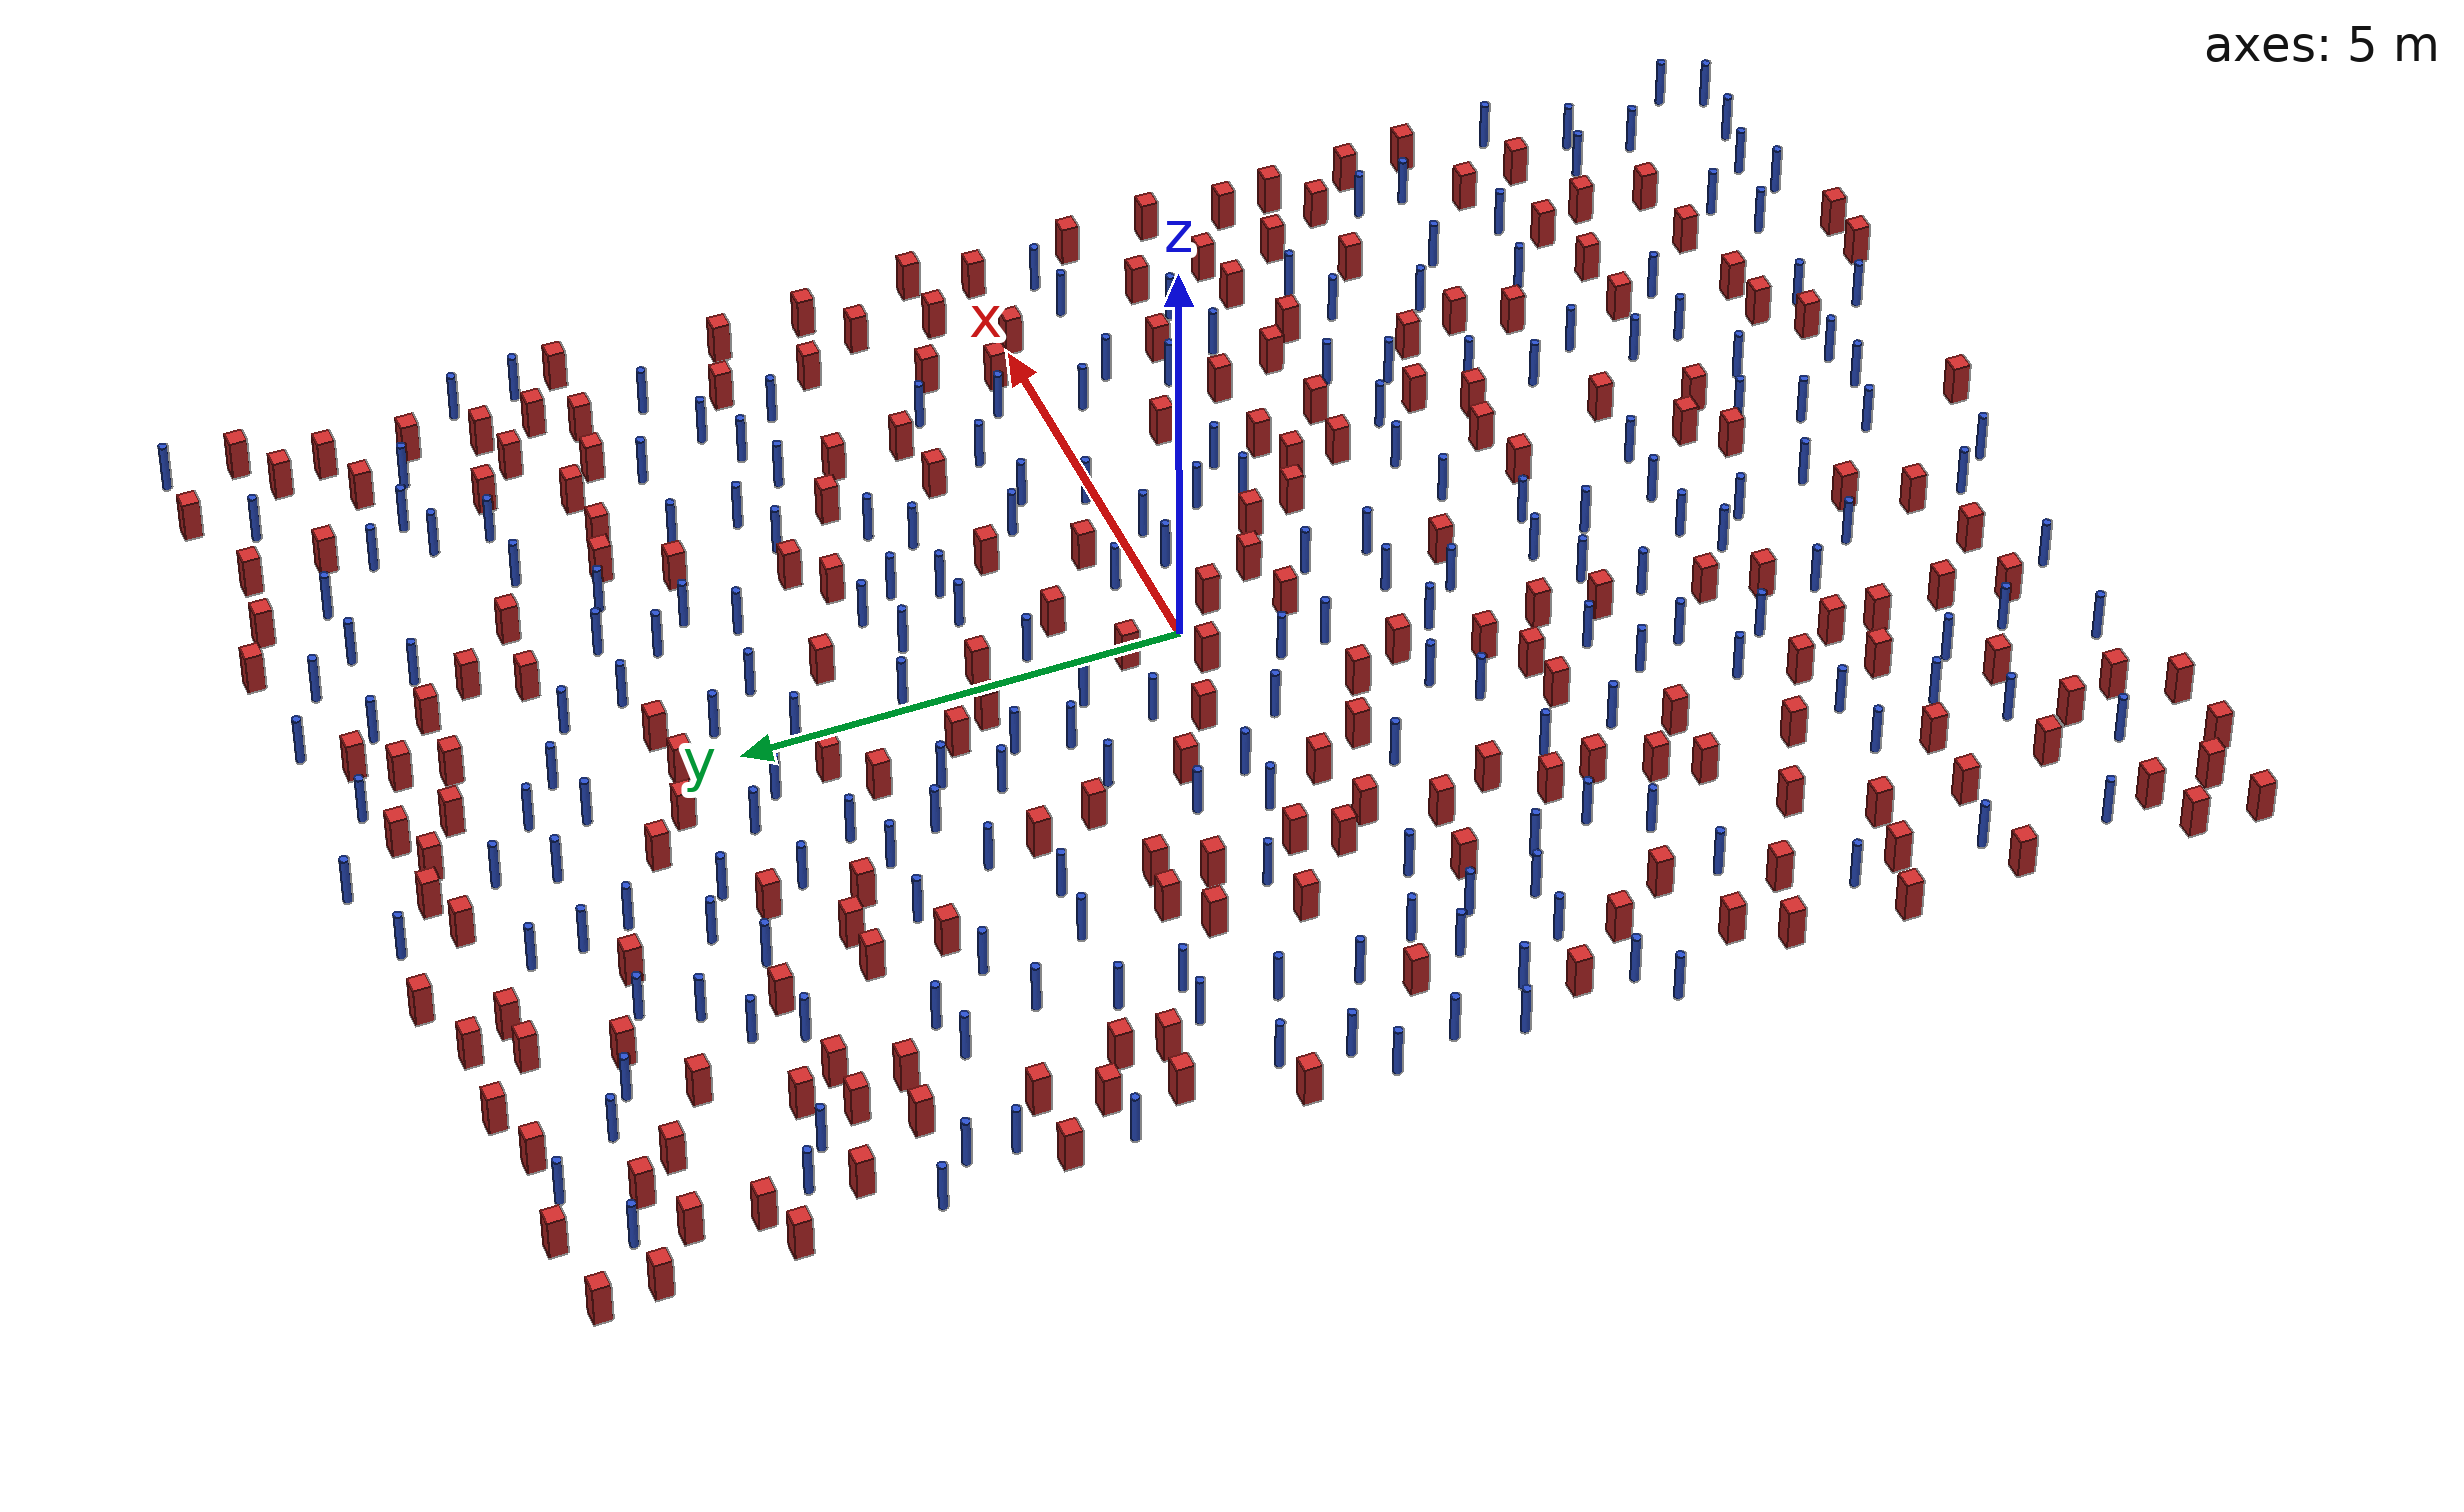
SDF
<sdf version="1.6">
  <model name="dense_33"><model name="square_post_obstacle0">
  <static>true</static>
  <pose frame="">3.83624007222 2.51242688066 8.22691968438e-08 7.2212513382e-06 -7.54495500217e-07 2.29674213826e-05</pose>
  <link name="link">
    <pose frame="">0 0 0.25 0 -0 0</pose>
    <inertial>
      <mass>100</mass>
      <inertia>
        <ixx>0.166667</ixx>
        <ixy>0</ixy>
        <ixz>0</ixz>
        <iyy>0.166667</iyy>
        <iyz>0</iyz>
        <izz>0.166667</izz>
      </inertia>
    </inertial>
    <collision name="collision">
      <geometry>
        <box>
          <size>.2 .2 .5</size>
        </box>
      </geometry>
      <max_contacts>10</max_contacts>
      <surface>
        <contact>
          <ode/>
        </contact>
        <bounce/>
        <friction>
          <torsional>
            <ode/>
          </torsional>
          <ode/>
        </friction>
      </surface>
    </collision>
    <visual name="visual">
      <geometry>
        <box>
          <size>.2 .2 .5</size>
        </box>
      </geometry>
      <material>
        <script>
          <name>Gazebo/Red</name>
          <uri>file://media/materials/scripts/gazebo.material</uri>
        </script>
      </material>
    </visual>
    <self_collide>0</self_collide>
    <kinematic>0</kinematic>
  </link>
</model>
<model name="square_post_obstacle1">
  <static>true</static>
  <pose frame="">5.38533942478 7.42540812029 8.22691968438e-08 7.2212513382e-06 -7.54495500217e-07 2.29674213826e-05</pose>
  <link name="link">
    <pose frame="">0 0 0.25 0 -0 0</pose>
    <inertial>
      <mass>100</mass>
      <inertia>
        <ixx>0.166667</ixx>
        <ixy>0</ixy>
        <ixz>0</ixz>
        <iyy>0.166667</iyy>
        <iyz>0</iyz>
        <izz>0.166667</izz>
      </inertia>
    </inertial>
    <collision name="collision">
      <geometry>
        <box>
          <size>.2 .2 .5</size>
        </box>
      </geometry>
      <max_contacts>10</max_contacts>
      <surface>
        <contact>
          <ode/>
        </contact>
        <bounce/>
        <friction>
          <torsional>
            <ode/>
          </torsional>
          <ode/>
        </friction>
      </surface>
    </collision>
    <visual name="visual">
      <geometry>
        <box>
          <size>.2 .2 .5</size>
        </box>
      </geometry>
      <material>
        <script>
          <name>Gazebo/Red</name>
          <uri>file://media/materials/scripts/gazebo.material</uri>
        </script>
      </material>
    </visual>
    <self_collide>0</self_collide>
    <kinematic>0</kinematic>
  </link>
</model>
<model name="pole_obstacle0">
  <static>true</static>
  <pose frame="">2.56448294464 8.85776135916 2.88873142074e-08 -9.90536692318e-09 4.6021994893e-07 -1.20965994988e-07</pose>
  <link name="link">
  <pose frame="">0 0 0.3 0 -0 0</pose>
    <inertial>
      <mass>1</mass>
      <inertia>
        <ixx>0.145833</ixx>
        <ixy>0</ixy>
        <ixz>0</ixz>
        <iyy>0.145833</iyy>
        <iyz>0</iyz>
        <izz>0.125</izz>
      </inertia>
    </inertial>
    <collision name="collision">
      <geometry>
        <cylinder>
          <radius>0.05</radius>
          <length>.6</length>
        </cylinder>
      </geometry>
      <max_contacts>10</max_contacts>
      <surface>
        <contact>
          <ode/>
        </contact>
        <bounce/>
        <friction>
          <torsional>
            <ode/>
          </torsional>
          <ode/>
        </friction>
      </surface>
    </collision>
    <visual name="visual">
      <geometry>
        <cylinder>
          <radius>0.05</radius>
          <length>.6</length>
        </cylinder>
      </geometry>
      <material>
        <script>
          <name>Gazebo/Blue</name>
          <uri>file://media/materials/scripts/gazebo.material</uri>
        </script>
      </material>
    </visual>
    <self_collide>0</self_collide>
    <kinematic>0</kinematic>
  </link>
</model>
<model name="square_post_obstacle2">
  <static>true</static>
  <pose frame="">5.382815112 2.22522824394 8.22691968438e-08 7.2212513382e-06 -7.54495500217e-07 2.29674213826e-05</pose>
  <link name="link">
    <pose frame="">0 0 0.25 0 -0 0</pose>
    <inertial>
      <mass>100</mass>
      <inertia>
        <ixx>0.166667</ixx>
        <ixy>0</ixy>
        <ixz>0</ixz>
        <iyy>0.166667</iyy>
        <iyz>0</iyz>
        <izz>0.166667</izz>
      </inertia>
    </inertial>
    <collision name="collision">
      <geometry>
        <box>
          <size>.2 .2 .5</size>
        </box>
      </geometry>
      <max_contacts>10</max_contacts>
      <surface>
        <contact>
          <ode/>
        </contact>
        <bounce/>
        <friction>
          <torsional>
            <ode/>
          </torsional>
          <ode/>
        </friction>
      </surface>
    </collision>
    <visual name="visual">
      <geometry>
        <box>
          <size>.2 .2 .5</size>
        </box>
      </geometry>
      <material>
        <script>
          <name>Gazebo/Red</name>
          <uri>file://media/materials/scripts/gazebo.material</uri>
        </script>
      </material>
    </visual>
    <self_collide>0</self_collide>
    <kinematic>0</kinematic>
  </link>
</model>
<model name="pole_obstacle1">
  <static>true</static>
  <pose frame="">2.42591077316 -8.50063717471 2.88873142074e-08 -9.90536692318e-09 4.6021994893e-07 -1.20965994988e-07</pose>
  <link name="link">
  <pose frame="">0 0 0.3 0 -0 0</pose>
    <inertial>
      <mass>1</mass>
      <inertia>
        <ixx>0.145833</ixx>
        <ixy>0</ixy>
        <ixz>0</ixz>
        <iyy>0.145833</iyy>
        <iyz>0</iyz>
        <izz>0.125</izz>
      </inertia>
    </inertial>
    <collision name="collision">
      <geometry>
        <cylinder>
          <radius>0.05</radius>
          <length>.6</length>
        </cylinder>
      </geometry>
      <max_contacts>10</max_contacts>
      <surface>
        <contact>
          <ode/>
        </contact>
        <bounce/>
        <friction>
          <torsional>
            <ode/>
          </torsional>
          <ode/>
        </friction>
      </surface>
    </collision>
    <visual name="visual">
      <geometry>
        <cylinder>
          <radius>0.05</radius>
          <length>.6</length>
        </cylinder>
      </geometry>
      <material>
        <script>
          <name>Gazebo/Blue</name>
          <uri>file://media/materials/scripts/gazebo.material</uri>
        </script>
      </material>
    </visual>
    <self_collide>0</self_collide>
    <kinematic>0</kinematic>
  </link>
</model>
<model name="square_post_obstacle3">
  <static>true</static>
  <pose frame="">3.03705830512 -1.04017219232 8.22691968438e-08 7.2212513382e-06 -7.54495500217e-07 2.29674213826e-05</pose>
  <link name="link">
    <pose frame="">0 0 0.25 0 -0 0</pose>
    <inertial>
      <mass>100</mass>
      <inertia>
        <ixx>0.166667</ixx>
        <ixy>0</ixy>
        <ixz>0</ixz>
        <iyy>0.166667</iyy>
        <iyz>0</iyz>
        <izz>0.166667</izz>
      </inertia>
    </inertial>
    <collision name="collision">
      <geometry>
        <box>
          <size>.2 .2 .5</size>
        </box>
      </geometry>
      <max_contacts>10</max_contacts>
      <surface>
        <contact>
          <ode/>
        </contact>
        <bounce/>
        <friction>
          <torsional>
            <ode/>
          </torsional>
          <ode/>
        </friction>
      </surface>
    </collision>
    <visual name="visual">
      <geometry>
        <box>
          <size>.2 .2 .5</size>
        </box>
      </geometry>
      <material>
        <script>
          <name>Gazebo/Red</name>
          <uri>file://media/materials/scripts/gazebo.material</uri>
        </script>
      </material>
    </visual>
    <self_collide>0</self_collide>
    <kinematic>0</kinematic>
  </link>
</model>
<model name="pole_obstacle2">
  <static>true</static>
  <pose frame="">4.54405223998 4.48123757993 2.88873142074e-08 -9.90536690842e-09 4.60219948965e-07 -1.20965994976e-07</pose>
  <link name="link">
  <pose frame="">0 0 0.3 0 -0 0</pose>
    <inertial>
      <mass>1</mass>
      <inertia>
        <ixx>0.145833</ixx>
        <ixy>0</ixy>
        <ixz>0</ixz>
        <iyy>0.145833</iyy>
        <iyz>0</iyz>
        <izz>0.125</izz>
      </inertia>
    </inertial>
    <collision name="collision">
      <geometry>
        <cylinder>
          <radius>0.05</radius>
          <length>.6</length>
        </cylinder>
      </geometry>
      <max_contacts>10</max_contacts>
      <surface>
        <contact>
          <ode/>
        </contact>
        <bounce/>
        <friction>
          <torsional>
            <ode/>
          </torsional>
          <ode/>
        </friction>
      </surface>
    </collision>
    <visual name="visual">
      <geometry>
        <cylinder>
          <radius>0.05</radius>
          <length>.6</length>
        </cylinder>
      </geometry>
      <material>
        <script>
          <name>Gazebo/Blue</name>
          <uri>file://media/materials/scripts/gazebo.material</uri>
        </script>
      </material>
    </visual>
    <self_collide>0</self_collide>
    <kinematic>0</kinematic>
  </link>
</model>
<model name="pole_obstacle3">
  <static>true</static>
  <pose frame="">1.09669443753 6.58516952447 2.88873142074e-08 -9.90536689852e-09 4.60219948989e-07 -1.2096599496e-07</pose>
  <link name="link">
  <pose frame="">0 0 0.3 0 -0 0</pose>
    <inertial>
      <mass>1</mass>
      <inertia>
        <ixx>0.145833</ixx>
        <ixy>0</ixy>
        <ixz>0</ixz>
        <iyy>0.145833</iyy>
        <iyz>0</iyz>
        <izz>0.125</izz>
      </inertia>
    </inertial>
    <collision name="collision">
      <geometry>
        <cylinder>
          <radius>0.05</radius>
          <length>.6</length>
        </cylinder>
      </geometry>
      <max_contacts>10</max_contacts>
      <surface>
        <contact>
          <ode/>
        </contact>
        <bounce/>
        <friction>
          <torsional>
            <ode/>
          </torsional>
          <ode/>
        </friction>
      </surface>
    </collision>
    <visual name="visual">
      <geometry>
        <cylinder>
          <radius>0.05</radius>
          <length>.6</length>
        </cylinder>
      </geometry>
      <material>
        <script>
          <name>Gazebo/Blue</name>
          <uri>file://media/materials/scripts/gazebo.material</uri>
        </script>
      </material>
    </visual>
    <self_collide>0</self_collide>
    <kinematic>0</kinematic>
  </link>
</model>
<model name="square_post_obstacle4">
  <static>true</static>
  <pose frame="">-1.2754052934 -3.62407108319 8.22691968438e-08 7.2212513382e-06 -7.54495500217e-07 2.29674213826e-05</pose>
  <link name="link">
    <pose frame="">0 0 0.25 0 -0 0</pose>
    <inertial>
      <mass>100</mass>
      <inertia>
        <ixx>0.166667</ixx>
        <ixy>0</ixy>
        <ixz>0</ixz>
        <iyy>0.166667</iyy>
        <iyz>0</iyz>
        <izz>0.166667</izz>
      </inertia>
    </inertial>
    <collision name="collision">
      <geometry>
        <box>
          <size>.2 .2 .5</size>
        </box>
      </geometry>
      <max_contacts>10</max_contacts>
      <surface>
        <contact>
          <ode/>
        </contact>
        <bounce/>
        <friction>
          <torsional>
            <ode/>
          </torsional>
          <ode/>
        </friction>
      </surface>
    </collision>
    <visual name="visual">
      <geometry>
        <box>
          <size>.2 .2 .5</size>
        </box>
      </geometry>
      <material>
        <script>
          <name>Gazebo/Red</name>
          <uri>file://media/materials/scripts/gazebo.material</uri>
        </script>
      </material>
    </visual>
    <self_collide>0</self_collide>
    <kinematic>0</kinematic>
  </link>
</model>
<model name="square_post_obstacle5">
  <static>true</static>
  <pose frame="">-5.93562843319 9.12042598517 8.22691968438e-08 7.22125133819e-06 -7.54495500217e-07 2.29674213826e-05</pose>
  <link name="link">
    <pose frame="">0 0 0.25 0 -0 0</pose>
    <inertial>
      <mass>100</mass>
      <inertia>
        <ixx>0.166667</ixx>
        <ixy>0</ixy>
        <ixz>0</ixz>
        <iyy>0.166667</iyy>
        <iyz>0</iyz>
        <izz>0.166667</izz>
      </inertia>
    </inertial>
    <collision name="collision">
      <geometry>
        <box>
          <size>.2 .2 .5</size>
        </box>
      </geometry>
      <max_contacts>10</max_contacts>
      <surface>
        <contact>
          <ode/>
        </contact>
        <bounce/>
        <friction>
          <torsional>
            <ode/>
          </torsional>
          <ode/>
        </friction>
      </surface>
    </collision>
    <visual name="visual">
      <geometry>
        <box>
          <size>.2 .2 .5</size>
        </box>
      </geometry>
      <material>
        <script>
          <name>Gazebo/Red</name>
          <uri>file://media/materials/scripts/gazebo.material</uri>
        </script>
      </material>
    </visual>
    <self_collide>0</self_collide>
    <kinematic>0</kinematic>
  </link>
</model>
<model name="square_post_obstacle6">
  <static>true</static>
  <pose frame="">-1.59563792283 -5.44610857162 8.22691968438e-08 7.2212513382e-06 -7.54495500217e-07 2.29674213826e-05</pose>
  <link name="link">
    <pose frame="">0 0 0.25 0 -0 0</pose>
    <inertial>
      <mass>100</mass>
      <inertia>
        <ixx>0.166667</ixx>
        <ixy>0</ixy>
        <ixz>0</ixz>
        <iyy>0.166667</iyy>
        <iyz>0</iyz>
        <izz>0.166667</izz>
      </inertia>
    </inertial>
    <collision name="collision">
      <geometry>
        <box>
          <size>.2 .2 .5</size>
        </box>
      </geometry>
      <max_contacts>10</max_contacts>
      <surface>
        <contact>
          <ode/>
        </contact>
        <bounce/>
        <friction>
          <torsional>
            <ode/>
          </torsional>
          <ode/>
        </friction>
      </surface>
    </collision>
    <visual name="visual">
      <geometry>
        <box>
          <size>.2 .2 .5</size>
        </box>
      </geometry>
      <material>
        <script>
          <name>Gazebo/Red</name>
          <uri>file://media/materials/scripts/gazebo.material</uri>
        </script>
      </material>
    </visual>
    <self_collide>0</self_collide>
    <kinematic>0</kinematic>
  </link>
</model>
<model name="pole_obstacle4">
  <static>true</static>
  <pose frame="">5.94569945255 -7.2721110719 2.88873142074e-08 -9.90536690842e-09 4.60219948965e-07 -1.20965994976e-07</pose>
  <link name="link">
  <pose frame="">0 0 0.3 0 -0 0</pose>
    <inertial>
      <mass>1</mass>
      <inertia>
        <ixx>0.145833</ixx>
        <ixy>0</ixy>
        <ixz>0</ixz>
        <iyy>0.145833</iyy>
        <iyz>0</iyz>
        <izz>0.125</izz>
      </inertia>
    </inertial>
    <collision name="collision">
      <geometry>
        <cylinder>
          <radius>0.05</radius>
          <length>.6</length>
        </cylinder>
      </geometry>
      <max_contacts>10</max_contacts>
      <surface>
        <contact>
          <ode/>
        </contact>
        <bounce/>
        <friction>
          <torsional>
            <ode/>
          </torsional>
          <ode/>
        </friction>
      </surface>
    </collision>
    <visual name="visual">
      <geometry>
        <cylinder>
          <radius>0.05</radius>
          <length>.6</length>
        </cylinder>
      </geometry>
      <material>
        <script>
          <name>Gazebo/Blue</name>
          <uri>file://media/materials/scripts/gazebo.material</uri>
        </script>
      </material>
    </visual>
    <self_collide>0</self_collide>
    <kinematic>0</kinematic>
  </link>
</model>
<model name="pole_obstacle5">
  <static>true</static>
  <pose frame="">-4.65952550141 -3.3882482919 2.88873142074e-08 -9.90536690245e-09 4.6021994898e-07 -1.20965994966e-07</pose>
  <link name="link">
  <pose frame="">0 0 0.3 0 -0 0</pose>
    <inertial>
      <mass>1</mass>
      <inertia>
        <ixx>0.145833</ixx>
        <ixy>0</ixy>
        <ixz>0</ixz>
        <iyy>0.145833</iyy>
        <iyz>0</iyz>
        <izz>0.125</izz>
      </inertia>
    </inertial>
    <collision name="collision">
      <geometry>
        <cylinder>
          <radius>0.05</radius>
          <length>.6</length>
        </cylinder>
      </geometry>
      <max_contacts>10</max_contacts>
      <surface>
        <contact>
          <ode/>
        </contact>
        <bounce/>
        <friction>
          <torsional>
            <ode/>
          </torsional>
          <ode/>
        </friction>
      </surface>
    </collision>
    <visual name="visual">
      <geometry>
        <cylinder>
          <radius>0.05</radius>
          <length>.6</length>
        </cylinder>
      </geometry>
      <material>
        <script>
          <name>Gazebo/Blue</name>
          <uri>file://media/materials/scripts/gazebo.material</uri>
        </script>
      </material>
    </visual>
    <self_collide>0</self_collide>
    <kinematic>0</kinematic>
  </link>
</model>
<model name="square_post_obstacle7">
  <static>true</static>
  <pose frame="">-1.21749053207 -2.01002110058 8.22691968438e-08 7.2212513382e-06 -7.54495500217e-07 2.29674213826e-05</pose>
  <link name="link">
    <pose frame="">0 0 0.25 0 -0 0</pose>
    <inertial>
      <mass>100</mass>
      <inertia>
        <ixx>0.166667</ixx>
        <ixy>0</ixy>
        <ixz>0</ixz>
        <iyy>0.166667</iyy>
        <iyz>0</iyz>
        <izz>0.166667</izz>
      </inertia>
    </inertial>
    <collision name="collision">
      <geometry>
        <box>
          <size>.2 .2 .5</size>
        </box>
      </geometry>
      <max_contacts>10</max_contacts>
      <surface>
        <contact>
          <ode/>
        </contact>
        <bounce/>
        <friction>
          <torsional>
            <ode/>
          </torsional>
          <ode/>
        </friction>
      </surface>
    </collision>
    <visual name="visual">
      <geometry>
        <box>
          <size>.2 .2 .5</size>
        </box>
      </geometry>
      <material>
        <script>
          <name>Gazebo/Red</name>
          <uri>file://media/materials/scripts/gazebo.material</uri>
        </script>
      </material>
    </visual>
    <self_collide>0</self_collide>
    <kinematic>0</kinematic>
  </link>
</model>
<model name="square_post_obstacle8">
  <static>true</static>
  <pose frame="">-6.37462192546 7.08235323561 8.22691968438e-08 7.2212513382e-06 -7.54495500217e-07 2.29674213826e-05</pose>
  <link name="link">
    <pose frame="">0 0 0.25 0 -0 0</pose>
    <inertial>
      <mass>100</mass>
      <inertia>
        <ixx>0.166667</ixx>
        <ixy>0</ixy>
        <ixz>0</ixz>
        <iyy>0.166667</iyy>
        <iyz>0</iyz>
        <izz>0.166667</izz>
      </inertia>
    </inertial>
    <collision name="collision">
      <geometry>
        <box>
          <size>.2 .2 .5</size>
        </box>
      </geometry>
      <max_contacts>10</max_contacts>
      <surface>
        <contact>
          <ode/>
        </contact>
        <bounce/>
        <friction>
          <torsional>
            <ode/>
          </torsional>
          <ode/>
        </friction>
      </surface>
    </collision>
    <visual name="visual">
      <geometry>
        <box>
          <size>.2 .2 .5</size>
        </box>
      </geometry>
      <material>
        <script>
          <name>Gazebo/Red</name>
          <uri>file://media/materials/scripts/gazebo.material</uri>
        </script>
      </material>
    </visual>
    <self_collide>0</self_collide>
    <kinematic>0</kinematic>
  </link>
</model>
<model name="pole_obstacle6">
  <static>true</static>
  <pose frame="">-2.38911364251 -4.31858731194 2.88873142074e-08 -9.90536689859e-09 4.60219948989e-07 -1.20965994961e-07</pose>
  <link name="link">
  <pose frame="">0 0 0.3 0 -0 0</pose>
    <inertial>
      <mass>1</mass>
      <inertia>
        <ixx>0.145833</ixx>
        <ixy>0</ixy>
        <ixz>0</ixz>
        <iyy>0.145833</iyy>
        <iyz>0</iyz>
        <izz>0.125</izz>
      </inertia>
    </inertial>
    <collision name="collision">
      <geometry>
        <cylinder>
          <radius>0.05</radius>
          <length>.6</length>
        </cylinder>
      </geometry>
      <max_contacts>10</max_contacts>
      <surface>
        <contact>
          <ode/>
        </contact>
        <bounce/>
        <friction>
          <torsional>
            <ode/>
          </torsional>
          <ode/>
        </friction>
      </surface>
    </collision>
    <visual name="visual">
      <geometry>
        <cylinder>
          <radius>0.05</radius>
          <length>.6</length>
        </cylinder>
      </geometry>
      <material>
        <script>
          <name>Gazebo/Blue</name>
          <uri>file://media/materials/scripts/gazebo.material</uri>
        </script>
      </material>
    </visual>
    <self_collide>0</self_collide>
    <kinematic>0</kinematic>
  </link>
</model>
<model name="pole_obstacle7">
  <static>true</static>
  <pose frame="">-6.87891514637 0.468989120806 2.88873142074e-08 -9.90536689483e-09 4.60219948998e-07 -1.20965994956e-07</pose>
  <link name="link">
  <pose frame="">0 0 0.3 0 -0 0</pose>
    <inertial>
      <mass>1</mass>
      <inertia>
        <ixx>0.145833</ixx>
        <ixy>0</ixy>
        <ixz>0</ixz>
        <iyy>0.145833</iyy>
        <iyz>0</iyz>
        <izz>0.125</izz>
      </inertia>
    </inertial>
    <collision name="collision">
      <geometry>
        <cylinder>
          <radius>0.05</radius>
          <length>.6</length>
        </cylinder>
      </geometry>
      <max_contacts>10</max_contacts>
      <surface>
        <contact>
          <ode/>
        </contact>
        <bounce/>
        <friction>
          <torsional>
            <ode/>
          </torsional>
          <ode/>
        </friction>
      </surface>
    </collision>
    <visual name="visual">
      <geometry>
        <cylinder>
          <radius>0.05</radius>
          <length>.6</length>
        </cylinder>
      </geometry>
      <material>
        <script>
          <name>Gazebo/Blue</name>
          <uri>file://media/materials/scripts/gazebo.material</uri>
        </script>
      </material>
    </visual>
    <self_collide>0</self_collide>
    <kinematic>0</kinematic>
  </link>
</model>
<model name="square_post_obstacle9">
  <static>true</static>
  <pose frame="">-4.64700420513 -6.66995732465 8.22691968438e-08 7.2212513382e-06 -7.54495500217e-07 2.29674213826e-05</pose>
  <link name="link">
    <pose frame="">0 0 0.25 0 -0 0</pose>
    <inertial>
      <mass>100</mass>
      <inertia>
        <ixx>0.166667</ixx>
        <ixy>0</ixy>
        <ixz>0</ixz>
        <iyy>0.166667</iyy>
        <iyz>0</iyz>
        <izz>0.166667</izz>
      </inertia>
    </inertial>
    <collision name="collision">
      <geometry>
        <box>
          <size>.2 .2 .5</size>
        </box>
      </geometry>
      <max_contacts>10</max_contacts>
      <surface>
        <contact>
          <ode/>
        </contact>
        <bounce/>
        <friction>
          <torsional>
            <ode/>
          </torsional>
          <ode/>
        </friction>
      </surface>
    </collision>
    <visual name="visual">
      <geometry>
        <box>
          <size>.2 .2 .5</size>
        </box>
      </geometry>
      <material>
        <script>
          <name>Gazebo/Red</name>
          <uri>file://media/materials/scripts/gazebo.material</uri>
        </script>
      </material>
    </visual>
    <self_collide>0</self_collide>
    <kinematic>0</kinematic>
  </link>
</model>
<model name="square_post_obstacle10">
  <static>true</static>
  <pose frame="">-5.9056552785 -4.26731862968 8.22691968438e-08 7.22125133819e-06 -7.54495500217e-07 2.29674213826e-05</pose>
  <link name="link">
    <pose frame="">0 0 0.25 0 -0 0</pose>
    <inertial>
      <mass>100</mass>
      <inertia>
        <ixx>0.166667</ixx>
        <ixy>0</ixy>
        <ixz>0</ixz>
        <iyy>0.166667</iyy>
        <iyz>0</iyz>
        <izz>0.166667</izz>
      </inertia>
    </inertial>
    <collision name="collision">
      <geometry>
        <box>
          <size>.2 .2 .5</size>
        </box>
      </geometry>
      <max_contacts>10</max_contacts>
      <surface>
        <contact>
          <ode/>
        </contact>
        <bounce/>
        <friction>
          <torsional>
            <ode/>
          </torsional>
          <ode/>
        </friction>
      </surface>
    </collision>
    <visual name="visual">
      <geometry>
        <box>
          <size>.2 .2 .5</size>
        </box>
      </geometry>
      <material>
        <script>
          <name>Gazebo/Red</name>
          <uri>file://media/materials/scripts/gazebo.material</uri>
        </script>
      </material>
    </visual>
    <self_collide>0</self_collide>
    <kinematic>0</kinematic>
  </link>
</model>
<model name="square_post_obstacle11">
  <static>true</static>
  <pose frame="">-3.14499950519 -5.83607089433 8.22691968438e-08 7.2212513382e-06 -7.54495500217e-07 2.29674213826e-05</pose>
  <link name="link">
    <pose frame="">0 0 0.25 0 -0 0</pose>
    <inertial>
      <mass>100</mass>
      <inertia>
        <ixx>0.166667</ixx>
        <ixy>0</ixy>
        <ixz>0</ixz>
        <iyy>0.166667</iyy>
        <iyz>0</iyz>
        <izz>0.166667</izz>
      </inertia>
    </inertial>
    <collision name="collision">
      <geometry>
        <box>
          <size>.2 .2 .5</size>
        </box>
      </geometry>
      <max_contacts>10</max_contacts>
      <surface>
        <contact>
          <ode/>
        </contact>
        <bounce/>
        <friction>
          <torsional>
            <ode/>
          </torsional>
          <ode/>
        </friction>
      </surface>
    </collision>
    <visual name="visual">
      <geometry>
        <box>
          <size>.2 .2 .5</size>
        </box>
      </geometry>
      <material>
        <script>
          <name>Gazebo/Red</name>
          <uri>file://media/materials/scripts/gazebo.material</uri>
        </script>
      </material>
    </visual>
    <self_collide>0</self_collide>
    <kinematic>0</kinematic>
  </link>
</model>
<model name="square_post_obstacle12">
  <static>true</static>
  <pose frame="">1.9961251198 -2.69683768258 8.22691968438e-08 7.2212513382e-06 -7.54495500217e-07 2.29674213826e-05</pose>
  <link name="link">
    <pose frame="">0 0 0.25 0 -0 0</pose>
    <inertial>
      <mass>100</mass>
      <inertia>
        <ixx>0.166667</ixx>
        <ixy>0</ixy>
        <ixz>0</ixz>
        <iyy>0.166667</iyy>
        <iyz>0</iyz>
        <izz>0.166667</izz>
      </inertia>
    </inertial>
    <collision name="collision">
      <geometry>
        <box>
          <size>.2 .2 .5</size>
        </box>
      </geometry>
      <max_contacts>10</max_contacts>
      <surface>
        <contact>
          <ode/>
        </contact>
        <bounce/>
        <friction>
          <torsional>
            <ode/>
          </torsional>
          <ode/>
        </friction>
      </surface>
    </collision>
    <visual name="visual">
      <geometry>
        <box>
          <size>.2 .2 .5</size>
        </box>
      </geometry>
      <material>
        <script>
          <name>Gazebo/Red</name>
          <uri>file://media/materials/scripts/gazebo.material</uri>
        </script>
      </material>
    </visual>
    <self_collide>0</self_collide>
    <kinematic>0</kinematic>
  </link>
</model>
<model name="square_post_obstacle13">
  <static>true</static>
  <pose frame="">3.24126532681 5.41806297462 8.22691968438e-08 7.2212513382e-06 -7.54495500217e-07 2.29674213826e-05</pose>
  <link name="link">
    <pose frame="">0 0 0.25 0 -0 0</pose>
    <inertial>
      <mass>100</mass>
      <inertia>
        <ixx>0.166667</ixx>
        <ixy>0</ixy>
        <ixz>0</ixz>
        <iyy>0.166667</iyy>
        <iyz>0</iyz>
        <izz>0.166667</izz>
      </inertia>
    </inertial>
    <collision name="collision">
      <geometry>
        <box>
          <size>.2 .2 .5</size>
        </box>
      </geometry>
      <max_contacts>10</max_contacts>
      <surface>
        <contact>
          <ode/>
        </contact>
        <bounce/>
        <friction>
          <torsional>
            <ode/>
          </torsional>
          <ode/>
        </friction>
      </surface>
    </collision>
    <visual name="visual">
      <geometry>
        <box>
          <size>.2 .2 .5</size>
        </box>
      </geometry>
      <material>
        <script>
          <name>Gazebo/Red</name>
          <uri>file://media/materials/scripts/gazebo.material</uri>
        </script>
      </material>
    </visual>
    <self_collide>0</self_collide>
    <kinematic>0</kinematic>
  </link>
</model>
<model name="pole_obstacle8">
  <static>true</static>
  <pose frame="">-3.47671300704 -7.40838706162 2.88873142074e-08 -9.90536692062e-09 4.60219948937e-07 -1.20965994985e-07</pose>
  <link name="link">
  <pose frame="">0 0 0.3 0 -0 0</pose>
    <inertial>
      <mass>1</mass>
      <inertia>
        <ixx>0.145833</ixx>
        <ixy>0</ixy>
        <ixz>0</ixz>
        <iyy>0.145833</iyy>
        <iyz>0</iyz>
        <izz>0.125</izz>
      </inertia>
    </inertial>
    <collision name="collision">
      <geometry>
        <cylinder>
          <radius>0.05</radius>
          <length>.6</length>
        </cylinder>
      </geometry>
      <max_contacts>10</max_contacts>
      <surface>
        <contact>
          <ode/>
        </contact>
        <bounce/>
        <friction>
          <torsional>
            <ode/>
          </torsional>
          <ode/>
        </friction>
      </surface>
    </collision>
    <visual name="visual">
      <geometry>
        <cylinder>
          <radius>0.05</radius>
          <length>.6</length>
        </cylinder>
      </geometry>
      <material>
        <script>
          <name>Gazebo/Blue</name>
          <uri>file://media/materials/scripts/gazebo.material</uri>
        </script>
      </material>
    </visual>
    <self_collide>0</self_collide>
    <kinematic>0</kinematic>
  </link>
</model>
<model name="square_post_obstacle14">
  <static>true</static>
  <pose frame="">-1.14787507344 -8.16569303393 8.22691968438e-08 7.22125133819e-06 -7.54495500217e-07 2.29674213826e-05</pose>
  <link name="link">
    <pose frame="">0 0 0.25 0 -0 0</pose>
    <inertial>
      <mass>100</mass>
      <inertia>
        <ixx>0.166667</ixx>
        <ixy>0</ixy>
        <ixz>0</ixz>
        <iyy>0.166667</iyy>
        <iyz>0</iyz>
        <izz>0.166667</izz>
      </inertia>
    </inertial>
    <collision name="collision">
      <geometry>
        <box>
          <size>.2 .2 .5</size>
        </box>
      </geometry>
      <max_contacts>10</max_contacts>
      <surface>
        <contact>
          <ode/>
        </contact>
        <bounce/>
        <friction>
          <torsional>
            <ode/>
          </torsional>
          <ode/>
        </friction>
      </surface>
    </collision>
    <visual name="visual">
      <geometry>
        <box>
          <size>.2 .2 .5</size>
        </box>
      </geometry>
      <material>
        <script>
          <name>Gazebo/Red</name>
          <uri>file://media/materials/scripts/gazebo.material</uri>
        </script>
      </material>
    </visual>
    <self_collide>0</self_collide>
    <kinematic>0</kinematic>
  </link>
</model>
<model name="square_post_obstacle15">
  <static>true</static>
  <pose frame="">0.545075643161 5.75793375403 8.22691968438e-08 7.2212513382e-06 -7.54495500217e-07 2.29674213826e-05</pose>
  <link name="link">
    <pose frame="">0 0 0.25 0 -0 0</pose>
    <inertial>
      <mass>100</mass>
      <inertia>
        <ixx>0.166667</ixx>
        <ixy>0</ixy>
        <ixz>0</ixz>
        <iyy>0.166667</iyy>
        <iyz>0</iyz>
        <izz>0.166667</izz>
      </inertia>
    </inertial>
    <collision name="collision">
      <geometry>
        <box>
          <size>.2 .2 .5</size>
        </box>
      </geometry>
      <max_contacts>10</max_contacts>
      <surface>
        <contact>
          <ode/>
        </contact>
        <bounce/>
        <friction>
          <torsional>
            <ode/>
          </torsional>
          <ode/>
        </friction>
      </surface>
    </collision>
    <visual name="visual">
      <geometry>
        <box>
          <size>.2 .2 .5</size>
        </box>
      </geometry>
      <material>
        <script>
          <name>Gazebo/Red</name>
          <uri>file://media/materials/scripts/gazebo.material</uri>
        </script>
      </material>
    </visual>
    <self_collide>0</self_collide>
    <kinematic>0</kinematic>
  </link>
</model>
<model name="square_post_obstacle16">
  <static>true</static>
  <pose frame="">-0.82586581585 -7.49425958499 8.22691968438e-08 7.2212513382e-06 -7.54495500217e-07 2.29674213826e-05</pose>
  <link name="link">
    <pose frame="">0 0 0.25 0 -0 0</pose>
    <inertial>
      <mass>100</mass>
      <inertia>
        <ixx>0.166667</ixx>
        <ixy>0</ixy>
        <ixz>0</ixz>
        <iyy>0.166667</iyy>
        <iyz>0</iyz>
        <izz>0.166667</izz>
      </inertia>
    </inertial>
    <collision name="collision">
      <geometry>
        <box>
          <size>.2 .2 .5</size>
        </box>
      </geometry>
      <max_contacts>10</max_contacts>
      <surface>
        <contact>
          <ode/>
        </contact>
        <bounce/>
        <friction>
          <torsional>
            <ode/>
          </torsional>
          <ode/>
        </friction>
      </surface>
    </collision>
    <visual name="visual">
      <geometry>
        <box>
          <size>.2 .2 .5</size>
        </box>
      </geometry>
      <material>
        <script>
          <name>Gazebo/Red</name>
          <uri>file://media/materials/scripts/gazebo.material</uri>
        </script>
      </material>
    </visual>
    <self_collide>0</self_collide>
    <kinematic>0</kinematic>
  </link>
</model>
<model name="pole_obstacle9">
  <static>true</static>
  <pose frame="">5.42084835923 -0.801809787041 2.88873142074e-08 -9.90536689837e-09 4.60219948989e-07 -1.2096599496e-07</pose>
  <link name="link">
  <pose frame="">0 0 0.3 0 -0 0</pose>
    <inertial>
      <mass>1</mass>
      <inertia>
        <ixx>0.145833</ixx>
        <ixy>0</ixy>
        <ixz>0</ixz>
        <iyy>0.145833</iyy>
        <iyz>0</iyz>
        <izz>0.125</izz>
      </inertia>
    </inertial>
    <collision name="collision">
      <geometry>
        <cylinder>
          <radius>0.05</radius>
          <length>.6</length>
        </cylinder>
      </geometry>
      <max_contacts>10</max_contacts>
      <surface>
        <contact>
          <ode/>
        </contact>
        <bounce/>
        <friction>
          <torsional>
            <ode/>
          </torsional>
          <ode/>
        </friction>
      </surface>
    </collision>
    <visual name="visual">
      <geometry>
        <cylinder>
          <radius>0.05</radius>
          <length>.6</length>
        </cylinder>
      </geometry>
      <material>
        <script>
          <name>Gazebo/Blue</name>
          <uri>file://media/materials/scripts/gazebo.material</uri>
        </script>
      </material>
    </visual>
    <self_collide>0</self_collide>
    <kinematic>0</kinematic>
  </link>
</model>
<model name="square_post_obstacle17">
  <static>true</static>
  <pose frame="">-3.48001019088 4.02182379612 8.22691968438e-08 7.22125133819e-06 -7.54495500217e-07 2.29674213826e-05</pose>
  <link name="link">
    <pose frame="">0 0 0.25 0 -0 0</pose>
    <inertial>
      <mass>100</mass>
      <inertia>
        <ixx>0.166667</ixx>
        <ixy>0</ixy>
        <ixz>0</ixz>
        <iyy>0.166667</iyy>
        <iyz>0</iyz>
        <izz>0.166667</izz>
      </inertia>
    </inertial>
    <collision name="collision">
      <geometry>
        <box>
          <size>.2 .2 .5</size>
        </box>
      </geometry>
      <max_contacts>10</max_contacts>
      <surface>
        <contact>
          <ode/>
        </contact>
        <bounce/>
        <friction>
          <torsional>
            <ode/>
          </torsional>
          <ode/>
        </friction>
      </surface>
    </collision>
    <visual name="visual">
      <geometry>
        <box>
          <size>.2 .2 .5</size>
        </box>
      </geometry>
      <material>
        <script>
          <name>Gazebo/Red</name>
          <uri>file://media/materials/scripts/gazebo.material</uri>
        </script>
      </material>
    </visual>
    <self_collide>0</self_collide>
    <kinematic>0</kinematic>
  </link>
</model>
<model name="square_post_obstacle18">
  <static>true</static>
  <pose frame="">4.81835636104 -4.06285529954 8.22691968438e-08 7.2212513382e-06 -7.54495500217e-07 2.29674213826e-05</pose>
  <link name="link">
    <pose frame="">0 0 0.25 0 -0 0</pose>
    <inertial>
      <mass>100</mass>
      <inertia>
        <ixx>0.166667</ixx>
        <ixy>0</ixy>
        <ixz>0</ixz>
        <iyy>0.166667</iyy>
        <iyz>0</iyz>
        <izz>0.166667</izz>
      </inertia>
    </inertial>
    <collision name="collision">
      <geometry>
        <box>
          <size>.2 .2 .5</size>
        </box>
      </geometry>
      <max_contacts>10</max_contacts>
      <surface>
        <contact>
          <ode/>
        </contact>
        <bounce/>
        <friction>
          <torsional>
            <ode/>
          </torsional>
          <ode/>
        </friction>
      </surface>
    </collision>
    <visual name="visual">
      <geometry>
        <box>
          <size>.2 .2 .5</size>
        </box>
      </geometry>
      <material>
        <script>
          <name>Gazebo/Red</name>
          <uri>file://media/materials/scripts/gazebo.material</uri>
        </script>
      </material>
    </visual>
    <self_collide>0</self_collide>
    <kinematic>0</kinematic>
  </link>
</model>
<model name="pole_obstacle10">
  <static>true</static>
  <pose frame="">-1.00870879884 7.38911551066 2.88873142074e-08 -9.90536689792e-09 4.6021994899e-07 -1.2096599496e-07</pose>
  <link name="link">
  <pose frame="">0 0 0.3 0 -0 0</pose>
    <inertial>
      <mass>1</mass>
      <inertia>
        <ixx>0.145833</ixx>
        <ixy>0</ixy>
        <ixz>0</ixz>
        <iyy>0.145833</iyy>
        <iyz>0</iyz>
        <izz>0.125</izz>
      </inertia>
    </inertial>
    <collision name="collision">
      <geometry>
        <cylinder>
          <radius>0.05</radius>
          <length>.6</length>
        </cylinder>
      </geometry>
      <max_contacts>10</max_contacts>
      <surface>
        <contact>
          <ode/>
        </contact>
        <bounce/>
        <friction>
          <torsional>
            <ode/>
          </torsional>
          <ode/>
        </friction>
      </surface>
    </collision>
    <visual name="visual">
      <geometry>
        <cylinder>
          <radius>0.05</radius>
          <length>.6</length>
        </cylinder>
      </geometry>
      <material>
        <script>
          <name>Gazebo/Blue</name>
          <uri>file://media/materials/scripts/gazebo.material</uri>
        </script>
      </material>
    </visual>
    <self_collide>0</self_collide>
    <kinematic>0</kinematic>
  </link>
</model>
<model name="square_post_obstacle19">
  <static>true</static>
  <pose frame="">4.84791716677 4.95255068701 8.22691968438e-08 7.2212513382e-06 -7.54495500217e-07 2.29674213826e-05</pose>
  <link name="link">
    <pose frame="">0 0 0.25 0 -0 0</pose>
    <inertial>
      <mass>100</mass>
      <inertia>
        <ixx>0.166667</ixx>
        <ixy>0</ixy>
        <ixz>0</ixz>
        <iyy>0.166667</iyy>
        <iyz>0</iyz>
        <izz>0.166667</izz>
      </inertia>
    </inertial>
    <collision name="collision">
      <geometry>
        <box>
          <size>.2 .2 .5</size>
        </box>
      </geometry>
      <max_contacts>10</max_contacts>
      <surface>
        <contact>
          <ode/>
        </contact>
        <bounce/>
        <friction>
          <torsional>
            <ode/>
          </torsional>
          <ode/>
        </friction>
      </surface>
    </collision>
    <visual name="visual">
      <geometry>
        <box>
          <size>.2 .2 .5</size>
        </box>
      </geometry>
      <material>
        <script>
          <name>Gazebo/Red</name>
          <uri>file://media/materials/scripts/gazebo.material</uri>
        </script>
      </material>
    </visual>
    <self_collide>0</self_collide>
    <kinematic>0</kinematic>
  </link>
</model>
<model name="pole_obstacle11">
  <static>true</static>
  <pose frame="">6.33991685977 -6.39898442457 2.88873142074e-08 -9.90536690842e-09 4.60219948965e-07 -1.20965994976e-07</pose>
  <link name="link">
  <pose frame="">0 0 0.3 0 -0 0</pose>
    <inertial>
      <mass>1</mass>
      <inertia>
        <ixx>0.145833</ixx>
        <ixy>0</ixy>
        <ixz>0</ixz>
        <iyy>0.145833</iyy>
        <iyz>0</iyz>
        <izz>0.125</izz>
      </inertia>
    </inertial>
    <collision name="collision">
      <geometry>
        <cylinder>
          <radius>0.05</radius>
          <length>.6</length>
        </cylinder>
      </geometry>
      <max_contacts>10</max_contacts>
      <surface>
        <contact>
          <ode/>
        </contact>
        <bounce/>
        <friction>
          <torsional>
            <ode/>
          </torsional>
          <ode/>
        </friction>
      </surface>
    </collision>
    <visual name="visual">
      <geometry>
        <cylinder>
          <radius>0.05</radius>
          <length>.6</length>
        </cylinder>
      </geometry>
      <material>
        <script>
          <name>Gazebo/Blue</name>
          <uri>file://media/materials/scripts/gazebo.material</uri>
        </script>
      </material>
    </visual>
    <self_collide>0</self_collide>
    <kinematic>0</kinematic>
  </link>
</model>
<model name="square_post_obstacle20">
  <static>true</static>
  <pose frame="">2.71749468923 6.65501447354 8.22691968438e-08 7.2212513382e-06 -7.54495500217e-07 2.29674213826e-05</pose>
  <link name="link">
    <pose frame="">0 0 0.25 0 -0 0</pose>
    <inertial>
      <mass>100</mass>
      <inertia>
        <ixx>0.166667</ixx>
        <ixy>0</ixy>
        <ixz>0</ixz>
        <iyy>0.166667</iyy>
        <iyz>0</iyz>
        <izz>0.166667</izz>
      </inertia>
    </inertial>
    <collision name="collision">
      <geometry>
        <box>
          <size>.2 .2 .5</size>
        </box>
      </geometry>
      <max_contacts>10</max_contacts>
      <surface>
        <contact>
          <ode/>
        </contact>
        <bounce/>
        <friction>
          <torsional>
            <ode/>
          </torsional>
          <ode/>
        </friction>
      </surface>
    </collision>
    <visual name="visual">
      <geometry>
        <box>
          <size>.2 .2 .5</size>
        </box>
      </geometry>
      <material>
        <script>
          <name>Gazebo/Red</name>
          <uri>file://media/materials/scripts/gazebo.material</uri>
        </script>
      </material>
    </visual>
    <self_collide>0</self_collide>
    <kinematic>0</kinematic>
  </link>
</model>
<model name="pole_obstacle12">
  <static>true</static>
  <pose frame="">2.40385313394 2.13299145493 2.88873142074e-08 -9.90536690232e-09 4.6021994898e-07 -1.20965994968e-07</pose>
  <link name="link">
  <pose frame="">0 0 0.3 0 -0 0</pose>
    <inertial>
      <mass>1</mass>
      <inertia>
        <ixx>0.145833</ixx>
        <ixy>0</ixy>
        <ixz>0</ixz>
        <iyy>0.145833</iyy>
        <iyz>0</iyz>
        <izz>0.125</izz>
      </inertia>
    </inertial>
    <collision name="collision">
      <geometry>
        <cylinder>
          <radius>0.05</radius>
          <length>.6</length>
        </cylinder>
      </geometry>
      <max_contacts>10</max_contacts>
      <surface>
        <contact>
          <ode/>
        </contact>
        <bounce/>
        <friction>
          <torsional>
            <ode/>
          </torsional>
          <ode/>
        </friction>
      </surface>
    </collision>
    <visual name="visual">
      <geometry>
        <cylinder>
          <radius>0.05</radius>
          <length>.6</length>
        </cylinder>
      </geometry>
      <material>
        <script>
          <name>Gazebo/Blue</name>
          <uri>file://media/materials/scripts/gazebo.material</uri>
        </script>
      </material>
    </visual>
    <self_collide>0</self_collide>
    <kinematic>0</kinematic>
  </link>
</model>
<model name="square_post_obstacle21">
  <static>true</static>
  <pose frame="">-2.66958991058 -7.7484911874 8.22691968438e-08 7.22125133819e-06 -7.54495500217e-07 2.29674213826e-05</pose>
  <link name="link">
    <pose frame="">0 0 0.25 0 -0 0</pose>
    <inertial>
      <mass>100</mass>
      <inertia>
        <ixx>0.166667</ixx>
        <ixy>0</ixy>
        <ixz>0</ixz>
        <iyy>0.166667</iyy>
        <iyz>0</iyz>
        <izz>0.166667</izz>
      </inertia>
    </inertial>
    <collision name="collision">
      <geometry>
        <box>
          <size>.2 .2 .5</size>
        </box>
      </geometry>
      <max_contacts>10</max_contacts>
      <surface>
        <contact>
          <ode/>
        </contact>
        <bounce/>
        <friction>
          <torsional>
            <ode/>
          </torsional>
          <ode/>
        </friction>
      </surface>
    </collision>
    <visual name="visual">
      <geometry>
        <box>
          <size>.2 .2 .5</size>
        </box>
      </geometry>
      <material>
        <script>
          <name>Gazebo/Red</name>
          <uri>file://media/materials/scripts/gazebo.material</uri>
        </script>
      </material>
    </visual>
    <self_collide>0</self_collide>
    <kinematic>0</kinematic>
  </link>
</model>
<model name="pole_obstacle13">
  <static>true</static>
  <pose frame="">-6.36341904587 -7.83813379284 2.88873142074e-08 -9.90536690842e-09 4.60219948965e-07 -1.20965994976e-07</pose>
  <link name="link">
  <pose frame="">0 0 0.3 0 -0 0</pose>
    <inertial>
      <mass>1</mass>
      <inertia>
        <ixx>0.145833</ixx>
        <ixy>0</ixy>
        <ixz>0</ixz>
        <iyy>0.145833</iyy>
        <iyz>0</iyz>
        <izz>0.125</izz>
      </inertia>
    </inertial>
    <collision name="collision">
      <geometry>
        <cylinder>
          <radius>0.05</radius>
          <length>.6</length>
        </cylinder>
      </geometry>
      <max_contacts>10</max_contacts>
      <surface>
        <contact>
          <ode/>
        </contact>
        <bounce/>
        <friction>
          <torsional>
            <ode/>
          </torsional>
          <ode/>
        </friction>
      </surface>
    </collision>
    <visual name="visual">
      <geometry>
        <cylinder>
          <radius>0.05</radius>
          <length>.6</length>
        </cylinder>
      </geometry>
      <material>
        <script>
          <name>Gazebo/Blue</name>
          <uri>file://media/materials/scripts/gazebo.material</uri>
        </script>
      </material>
    </visual>
    <self_collide>0</self_collide>
    <kinematic>0</kinematic>
  </link>
</model>
<model name="square_post_obstacle22">
  <static>true</static>
  <pose frame="">-3.4165327686 8.55188839009 8.22691968438e-08 7.22125133819e-06 -7.54495500217e-07 2.29674213826e-05</pose>
  <link name="link">
    <pose frame="">0 0 0.25 0 -0 0</pose>
    <inertial>
      <mass>100</mass>
      <inertia>
        <ixx>0.166667</ixx>
        <ixy>0</ixy>
        <ixz>0</ixz>
        <iyy>0.166667</iyy>
        <iyz>0</iyz>
        <izz>0.166667</izz>
      </inertia>
    </inertial>
    <collision name="collision">
      <geometry>
        <box>
          <size>.2 .2 .5</size>
        </box>
      </geometry>
      <max_contacts>10</max_contacts>
      <surface>
        <contact>
          <ode/>
        </contact>
        <bounce/>
        <friction>
          <torsional>
            <ode/>
          </torsional>
          <ode/>
        </friction>
      </surface>
    </collision>
    <visual name="visual">
      <geometry>
        <box>
          <size>.2 .2 .5</size>
        </box>
      </geometry>
      <material>
        <script>
          <name>Gazebo/Red</name>
          <uri>file://media/materials/scripts/gazebo.material</uri>
        </script>
      </material>
    </visual>
    <self_collide>0</self_collide>
    <kinematic>0</kinematic>
  </link>
</model>
<model name="pole_obstacle14">
  <static>true</static>
  <pose frame="">1.79109142378 -1.48081458562 2.88873142074e-08 -9.90536689672e-09 4.60219948993e-07 -1.20965994959e-07</pose>
  <link name="link">
  <pose frame="">0 0 0.3 0 -0 0</pose>
    <inertial>
      <mass>1</mass>
      <inertia>
        <ixx>0.145833</ixx>
        <ixy>0</ixy>
        <ixz>0</ixz>
        <iyy>0.145833</iyy>
        <iyz>0</iyz>
        <izz>0.125</izz>
      </inertia>
    </inertial>
    <collision name="collision">
      <geometry>
        <cylinder>
          <radius>0.05</radius>
          <length>.6</length>
        </cylinder>
      </geometry>
      <max_contacts>10</max_contacts>
      <surface>
        <contact>
          <ode/>
        </contact>
        <bounce/>
        <friction>
          <torsional>
            <ode/>
          </torsional>
          <ode/>
        </friction>
      </surface>
    </collision>
    <visual name="visual">
      <geometry>
        <cylinder>
          <radius>0.05</radius>
          <length>.6</length>
        </cylinder>
      </geometry>
      <material>
        <script>
          <name>Gazebo/Blue</name>
          <uri>file://media/materials/scripts/gazebo.material</uri>
        </script>
      </material>
    </visual>
    <self_collide>0</self_collide>
    <kinematic>0</kinematic>
  </link>
</model>
<model name="pole_obstacle15">
  <static>true</static>
  <pose frame="">2.63196269383 -4.54886136414 2.88873142074e-08 -9.90536689859e-09 4.60219948989e-07 -1.20965994961e-07</pose>
  <link name="link">
  <pose frame="">0 0 0.3 0 -0 0</pose>
    <inertial>
      <mass>1</mass>
      <inertia>
        <ixx>0.145833</ixx>
        <ixy>0</ixy>
        <ixz>0</ixz>
        <iyy>0.145833</iyy>
        <iyz>0</iyz>
        <izz>0.125</izz>
      </inertia>
    </inertial>
    <collision name="collision">
      <geometry>
        <cylinder>
          <radius>0.05</radius>
          <length>.6</length>
        </cylinder>
      </geometry>
      <max_contacts>10</max_contacts>
      <surface>
        <contact>
          <ode/>
        </contact>
        <bounce/>
        <friction>
          <torsional>
            <ode/>
          </torsional>
          <ode/>
        </friction>
      </surface>
    </collision>
    <visual name="visual">
      <geometry>
        <cylinder>
          <radius>0.05</radius>
          <length>.6</length>
        </cylinder>
      </geometry>
      <material>
        <script>
          <name>Gazebo/Blue</name>
          <uri>file://media/materials/scripts/gazebo.material</uri>
        </script>
      </material>
    </visual>
    <self_collide>0</self_collide>
    <kinematic>0</kinematic>
  </link>
</model>
<model name="pole_obstacle16">
  <static>true</static>
  <pose frame="">2.15621258761 -9.10988371699 2.88873142074e-08 -9.90536692318e-09 4.6021994893e-07 -1.20965994988e-07</pose>
  <link name="link">
  <pose frame="">0 0 0.3 0 -0 0</pose>
    <inertial>
      <mass>1</mass>
      <inertia>
        <ixx>0.145833</ixx>
        <ixy>0</ixy>
        <ixz>0</ixz>
        <iyy>0.145833</iyy>
        <iyz>0</iyz>
        <izz>0.125</izz>
      </inertia>
    </inertial>
    <collision name="collision">
      <geometry>
        <cylinder>
          <radius>0.05</radius>
          <length>.6</length>
        </cylinder>
      </geometry>
      <max_contacts>10</max_contacts>
      <surface>
        <contact>
          <ode/>
        </contact>
        <bounce/>
        <friction>
          <torsional>
            <ode/>
          </torsional>
          <ode/>
        </friction>
      </surface>
    </collision>
    <visual name="visual">
      <geometry>
        <cylinder>
          <radius>0.05</radius>
          <length>.6</length>
        </cylinder>
      </geometry>
      <material>
        <script>
          <name>Gazebo/Blue</name>
          <uri>file://media/materials/scripts/gazebo.material</uri>
        </script>
      </material>
    </visual>
    <self_collide>0</self_collide>
    <kinematic>0</kinematic>
  </link>
</model>
<model name="square_post_obstacle23">
  <static>true</static>
  <pose frame="">-5.64145572779 8.10161814968 8.22691968438e-08 7.22125133819e-06 -7.54495500217e-07 2.29674213826e-05</pose>
  <link name="link">
    <pose frame="">0 0 0.25 0 -0 0</pose>
    <inertial>
      <mass>100</mass>
      <inertia>
        <ixx>0.166667</ixx>
        <ixy>0</ixy>
        <ixz>0</ixz>
        <iyy>0.166667</iyy>
        <iyz>0</iyz>
        <izz>0.166667</izz>
      </inertia>
    </inertial>
    <collision name="collision">
      <geometry>
        <box>
          <size>.2 .2 .5</size>
        </box>
      </geometry>
      <max_contacts>10</max_contacts>
      <surface>
        <contact>
          <ode/>
        </contact>
        <bounce/>
        <friction>
          <torsional>
            <ode/>
          </torsional>
          <ode/>
        </friction>
      </surface>
    </collision>
    <visual name="visual">
      <geometry>
        <box>
          <size>.2 .2 .5</size>
        </box>
      </geometry>
      <material>
        <script>
          <name>Gazebo/Red</name>
          <uri>file://media/materials/scripts/gazebo.material</uri>
        </script>
      </material>
    </visual>
    <self_collide>0</self_collide>
    <kinematic>0</kinematic>
  </link>
</model>
<model name="pole_obstacle17">
  <static>true</static>
  <pose frame="">1.24541606687 5.88182453887 2.88873142074e-08 -9.90536689852e-09 4.60219948989e-07 -1.2096599496e-07</pose>
  <link name="link">
  <pose frame="">0 0 0.3 0 -0 0</pose>
    <inertial>
      <mass>1</mass>
      <inertia>
        <ixx>0.145833</ixx>
        <ixy>0</ixy>
        <ixz>0</ixz>
        <iyy>0.145833</iyy>
        <iyz>0</iyz>
        <izz>0.125</izz>
      </inertia>
    </inertial>
    <collision name="collision">
      <geometry>
        <cylinder>
          <radius>0.05</radius>
          <length>.6</length>
        </cylinder>
      </geometry>
      <max_contacts>10</max_contacts>
      <surface>
        <contact>
          <ode/>
        </contact>
        <bounce/>
        <friction>
          <torsional>
            <ode/>
          </torsional>
          <ode/>
        </friction>
      </surface>
    </collision>
    <visual name="visual">
      <geometry>
        <cylinder>
          <radius>0.05</radius>
          <length>.6</length>
        </cylinder>
      </geometry>
      <material>
        <script>
          <name>Gazebo/Blue</name>
          <uri>file://media/materials/scripts/gazebo.material</uri>
        </script>
      </material>
    </visual>
    <self_collide>0</self_collide>
    <kinematic>0</kinematic>
  </link>
</model>
<model name="square_post_obstacle24">
  <static>true</static>
  <pose frame="">-6.87117180458 8.34306343805 8.22691968438e-08 7.22125133819e-06 -7.54495500217e-07 2.29674213826e-05</pose>
  <link name="link">
    <pose frame="">0 0 0.25 0 -0 0</pose>
    <inertial>
      <mass>100</mass>
      <inertia>
        <ixx>0.166667</ixx>
        <ixy>0</ixy>
        <ixz>0</ixz>
        <iyy>0.166667</iyy>
        <iyz>0</iyz>
        <izz>0.166667</izz>
      </inertia>
    </inertial>
    <collision name="collision">
      <geometry>
        <box>
          <size>.2 .2 .5</size>
        </box>
      </geometry>
      <max_contacts>10</max_contacts>
      <surface>
        <contact>
          <ode/>
        </contact>
        <bounce/>
        <friction>
          <torsional>
            <ode/>
          </torsional>
          <ode/>
        </friction>
      </surface>
    </collision>
    <visual name="visual">
      <geometry>
        <box>
          <size>.2 .2 .5</size>
        </box>
      </geometry>
      <material>
        <script>
          <name>Gazebo/Red</name>
          <uri>file://media/materials/scripts/gazebo.material</uri>
        </script>
      </material>
    </visual>
    <self_collide>0</self_collide>
    <kinematic>0</kinematic>
  </link>
</model>
<model name="square_post_obstacle25">
  <static>true</static>
  <pose frame="">0.854887156329 7.91558917575 8.22691968438e-08 7.22125133819e-06 -7.54495500217e-07 2.29674213826e-05</pose>
  <link name="link">
    <pose frame="">0 0 0.25 0 -0 0</pose>
    <inertial>
      <mass>100</mass>
      <inertia>
        <ixx>0.166667</ixx>
        <ixy>0</ixy>
        <ixz>0</ixz>
        <iyy>0.166667</iyy>
        <iyz>0</iyz>
        <izz>0.166667</izz>
      </inertia>
    </inertial>
    <collision name="collision">
      <geometry>
        <box>
          <size>.2 .2 .5</size>
        </box>
      </geometry>
      <max_contacts>10</max_contacts>
      <surface>
        <contact>
          <ode/>
        </contact>
        <bounce/>
        <friction>
          <torsional>
            <ode/>
          </torsional>
          <ode/>
        </friction>
      </surface>
    </collision>
    <visual name="visual">
      <geometry>
        <box>
          <size>.2 .2 .5</size>
        </box>
      </geometry>
      <material>
        <script>
          <name>Gazebo/Red</name>
          <uri>file://media/materials/scripts/gazebo.material</uri>
        </script>
      </material>
    </visual>
    <self_collide>0</self_collide>
    <kinematic>0</kinematic>
  </link>
</model>
<model name="square_post_obstacle26">
  <static>true</static>
  <pose frame="">-6.24597658063 -9.10434536315 8.22691968438e-08 7.22125133819e-06 -7.54495500217e-07 2.29674213826e-05</pose>
  <link name="link">
    <pose frame="">0 0 0.25 0 -0 0</pose>
    <inertial>
      <mass>100</mass>
      <inertia>
        <ixx>0.166667</ixx>
        <ixy>0</ixy>
        <ixz>0</ixz>
        <iyy>0.166667</iyy>
        <iyz>0</iyz>
        <izz>0.166667</izz>
      </inertia>
    </inertial>
    <collision name="collision">
      <geometry>
        <box>
          <size>.2 .2 .5</size>
        </box>
      </geometry>
      <max_contacts>10</max_contacts>
      <surface>
        <contact>
          <ode/>
        </contact>
        <bounce/>
        <friction>
          <torsional>
            <ode/>
          </torsional>
          <ode/>
        </friction>
      </surface>
    </collision>
    <visual name="visual">
      <geometry>
        <box>
          <size>.2 .2 .5</size>
        </box>
      </geometry>
      <material>
        <script>
          <name>Gazebo/Red</name>
          <uri>file://media/materials/scripts/gazebo.material</uri>
        </script>
      </material>
    </visual>
    <self_collide>0</self_collide>
    <kinematic>0</kinematic>
  </link>
</model>
<model name="square_post_obstacle27">
  <static>true</static>
  <pose frame="">-0.036564975498 5.68744413716 8.22691968438e-08 7.2212513382e-06 -7.54495500217e-07 2.29674213826e-05</pose>
  <link name="link">
    <pose frame="">0 0 0.25 0 -0 0</pose>
    <inertial>
      <mass>100</mass>
      <inertia>
        <ixx>0.166667</ixx>
        <ixy>0</ixy>
        <ixz>0</ixz>
        <iyy>0.166667</iyy>
        <iyz>0</iyz>
        <izz>0.166667</izz>
      </inertia>
    </inertial>
    <collision name="collision">
      <geometry>
        <box>
          <size>.2 .2 .5</size>
        </box>
      </geometry>
      <max_contacts>10</max_contacts>
      <surface>
        <contact>
          <ode/>
        </contact>
        <bounce/>
        <friction>
          <torsional>
            <ode/>
          </torsional>
          <ode/>
        </friction>
      </surface>
    </collision>
    <visual name="visual">
      <geometry>
        <box>
          <size>.2 .2 .5</size>
        </box>
      </geometry>
      <material>
        <script>
          <name>Gazebo/Red</name>
          <uri>file://media/materials/scripts/gazebo.material</uri>
        </script>
      </material>
    </visual>
    <self_collide>0</self_collide>
    <kinematic>0</kinematic>
  </link>
</model>
<model name="pole_obstacle18">
  <static>true</static>
  <pose frame="">-1.86325711507 1.58406415004 2.88873142074e-08 -9.90536689672e-09 4.60219948993e-07 -1.20965994959e-07</pose>
  <link name="link">
  <pose frame="">0 0 0.3 0 -0 0</pose>
    <inertial>
      <mass>1</mass>
      <inertia>
        <ixx>0.145833</ixx>
        <ixy>0</ixy>
        <ixz>0</ixz>
        <iyy>0.145833</iyy>
        <iyz>0</iyz>
        <izz>0.125</izz>
      </inertia>
    </inertial>
    <collision name="collision">
      <geometry>
        <cylinder>
          <radius>0.05</radius>
          <length>.6</length>
        </cylinder>
      </geometry>
      <max_contacts>10</max_contacts>
      <surface>
        <contact>
          <ode/>
        </contact>
        <bounce/>
        <friction>
          <torsional>
            <ode/>
          </torsional>
          <ode/>
        </friction>
      </surface>
    </collision>
    <visual name="visual">
      <geometry>
        <cylinder>
          <radius>0.05</radius>
          <length>.6</length>
        </cylinder>
      </geometry>
      <material>
        <script>
          <name>Gazebo/Blue</name>
          <uri>file://media/materials/scripts/gazebo.material</uri>
        </script>
      </material>
    </visual>
    <self_collide>0</self_collide>
    <kinematic>0</kinematic>
  </link>
</model>
<model name="square_post_obstacle28">
  <static>true</static>
  <pose frame="">-6.87716300165 6.88733941895 8.22691968438e-08 7.2212513382e-06 -7.54495500217e-07 2.29674213826e-05</pose>
  <link name="link">
    <pose frame="">0 0 0.25 0 -0 0</pose>
    <inertial>
      <mass>100</mass>
      <inertia>
        <ixx>0.166667</ixx>
        <ixy>0</ixy>
        <ixz>0</ixz>
        <iyy>0.166667</iyy>
        <iyz>0</iyz>
        <izz>0.166667</izz>
      </inertia>
    </inertial>
    <collision name="collision">
      <geometry>
        <box>
          <size>.2 .2 .5</size>
        </box>
      </geometry>
      <max_contacts>10</max_contacts>
      <surface>
        <contact>
          <ode/>
        </contact>
        <bounce/>
        <friction>
          <torsional>
            <ode/>
          </torsional>
          <ode/>
        </friction>
      </surface>
    </collision>
    <visual name="visual">
      <geometry>
        <box>
          <size>.2 .2 .5</size>
        </box>
      </geometry>
      <material>
        <script>
          <name>Gazebo/Red</name>
          <uri>file://media/materials/scripts/gazebo.material</uri>
        </script>
      </material>
    </visual>
    <self_collide>0</self_collide>
    <kinematic>0</kinematic>
  </link>
</model>
<model name="pole_obstacle19">
  <static>true</static>
  <pose frame="">3.88683338803 -5.72605170219 2.88873142074e-08 -9.90536689859e-09 4.60219948989e-07 -1.20965994961e-07</pose>
  <link name="link">
  <pose frame="">0 0 0.3 0 -0 0</pose>
    <inertial>
      <mass>1</mass>
      <inertia>
        <ixx>0.145833</ixx>
        <ixy>0</ixy>
        <ixz>0</ixz>
        <iyy>0.145833</iyy>
        <iyz>0</iyz>
        <izz>0.125</izz>
      </inertia>
    </inertial>
    <collision name="collision">
      <geometry>
        <cylinder>
          <radius>0.05</radius>
          <length>.6</length>
        </cylinder>
      </geometry>
      <max_contacts>10</max_contacts>
      <surface>
        <contact>
          <ode/>
        </contact>
        <bounce/>
        <friction>
          <torsional>
            <ode/>
          </torsional>
          <ode/>
        </friction>
      </surface>
    </collision>
    <visual name="visual">
      <geometry>
        <cylinder>
          <radius>0.05</radius>
          <length>.6</length>
        </cylinder>
      </geometry>
      <material>
        <script>
          <name>Gazebo/Blue</name>
          <uri>file://media/materials/scripts/gazebo.material</uri>
        </script>
      </material>
    </visual>
    <self_collide>0</self_collide>
    <kinematic>0</kinematic>
  </link>
</model>
<model name="square_post_obstacle29">
  <static>true</static>
  <pose frame="">-0.556420358068 -0.08132773239 8.22691968438e-08 7.2212513382e-06 -7.54495500217e-07 2.29674213826e-05</pose>
  <link name="link">
    <pose frame="">0 0 0.25 0 -0 0</pose>
    <inertial>
      <mass>100</mass>
      <inertia>
        <ixx>0.166667</ixx>
        <ixy>0</ixy>
        <ixz>0</ixz>
        <iyy>0.166667</iyy>
        <iyz>0</iyz>
        <izz>0.166667</izz>
      </inertia>
    </inertial>
    <collision name="collision">
      <geometry>
        <box>
          <size>.2 .2 .5</size>
        </box>
      </geometry>
      <max_contacts>10</max_contacts>
      <surface>
        <contact>
          <ode/>
        </contact>
        <bounce/>
        <friction>
          <torsional>
            <ode/>
          </torsional>
          <ode/>
        </friction>
      </surface>
    </collision>
    <visual name="visual">
      <geometry>
        <box>
          <size>.2 .2 .5</size>
        </box>
      </geometry>
      <material>
        <script>
          <name>Gazebo/Red</name>
          <uri>file://media/materials/scripts/gazebo.material</uri>
        </script>
      </material>
    </visual>
    <self_collide>0</self_collide>
    <kinematic>0</kinematic>
  </link>
</model>
<model name="square_post_obstacle30">
  <static>true</static>
  <pose frame="">1.54722170927 -5.65805150016 8.22691968438e-08 7.2212513382e-06 -7.54495500217e-07 2.29674213826e-05</pose>
  <link name="link">
    <pose frame="">0 0 0.25 0 -0 0</pose>
    <inertial>
      <mass>100</mass>
      <inertia>
        <ixx>0.166667</ixx>
        <ixy>0</ixy>
        <ixz>0</ixz>
        <iyy>0.166667</iyy>
        <iyz>0</iyz>
        <izz>0.166667</izz>
      </inertia>
    </inertial>
    <collision name="collision">
      <geometry>
        <box>
          <size>.2 .2 .5</size>
        </box>
      </geometry>
      <max_contacts>10</max_contacts>
      <surface>
        <contact>
          <ode/>
        </contact>
        <bounce/>
        <friction>
          <torsional>
            <ode/>
          </torsional>
          <ode/>
        </friction>
      </surface>
    </collision>
    <visual name="visual">
      <geometry>
        <box>
          <size>.2 .2 .5</size>
        </box>
      </geometry>
      <material>
        <script>
          <name>Gazebo/Red</name>
          <uri>file://media/materials/scripts/gazebo.material</uri>
        </script>
      </material>
    </visual>
    <self_collide>0</self_collide>
    <kinematic>0</kinematic>
  </link>
</model>
<model name="pole_obstacle20">
  <static>true</static>
  <pose frame="">4.75549394992 -3.29048217303 2.88873142074e-08 -9.90536690245e-09 4.6021994898e-07 -1.20965994966e-07</pose>
  <link name="link">
  <pose frame="">0 0 0.3 0 -0 0</pose>
    <inertial>
      <mass>1</mass>
      <inertia>
        <ixx>0.145833</ixx>
        <ixy>0</ixy>
        <ixz>0</ixz>
        <iyy>0.145833</iyy>
        <iyz>0</iyz>
        <izz>0.125</izz>
      </inertia>
    </inertial>
    <collision name="collision">
      <geometry>
        <cylinder>
          <radius>0.05</radius>
          <length>.6</length>
        </cylinder>
      </geometry>
      <max_contacts>10</max_contacts>
      <surface>
        <contact>
          <ode/>
        </contact>
        <bounce/>
        <friction>
          <torsional>
            <ode/>
          </torsional>
          <ode/>
        </friction>
      </surface>
    </collision>
    <visual name="visual">
      <geometry>
        <cylinder>
          <radius>0.05</radius>
          <length>.6</length>
        </cylinder>
      </geometry>
      <material>
        <script>
          <name>Gazebo/Blue</name>
          <uri>file://media/materials/scripts/gazebo.material</uri>
        </script>
      </material>
    </visual>
    <self_collide>0</self_collide>
    <kinematic>0</kinematic>
  </link>
</model>
<model name="pole_obstacle21">
  <static>true</static>
  <pose frame="">-4.56347880412 -7.59551017704 2.88873142074e-08 -9.90536690842e-09 4.60219948965e-07 -1.20965994976e-07</pose>
  <link name="link">
  <pose frame="">0 0 0.3 0 -0 0</pose>
    <inertial>
      <mass>1</mass>
      <inertia>
        <ixx>0.145833</ixx>
        <ixy>0</ixy>
        <ixz>0</ixz>
        <iyy>0.145833</iyy>
        <iyz>0</iyz>
        <izz>0.125</izz>
      </inertia>
    </inertial>
    <collision name="collision">
      <geometry>
        <cylinder>
          <radius>0.05</radius>
          <length>.6</length>
        </cylinder>
      </geometry>
      <max_contacts>10</max_contacts>
      <surface>
        <contact>
          <ode/>
        </contact>
        <bounce/>
        <friction>
          <torsional>
            <ode/>
          </torsional>
          <ode/>
        </friction>
      </surface>
    </collision>
    <visual name="visual">
      <geometry>
        <cylinder>
          <radius>0.05</radius>
          <length>.6</length>
        </cylinder>
      </geometry>
      <material>
        <script>
          <name>Gazebo/Blue</name>
          <uri>file://media/materials/scripts/gazebo.material</uri>
        </script>
      </material>
    </visual>
    <self_collide>0</self_collide>
    <kinematic>0</kinematic>
  </link>
</model>
<model name="square_post_obstacle31">
  <static>true</static>
  <pose frame="">-5.44097862834 -5.64113850015 8.22691968438e-08 7.22125133819e-06 -7.54495500217e-07 2.29674213826e-05</pose>
  <link name="link">
    <pose frame="">0 0 0.25 0 -0 0</pose>
    <inertial>
      <mass>100</mass>
      <inertia>
        <ixx>0.166667</ixx>
        <ixy>0</ixy>
        <ixz>0</ixz>
        <iyy>0.166667</iyy>
        <iyz>0</iyz>
        <izz>0.166667</izz>
      </inertia>
    </inertial>
    <collision name="collision">
      <geometry>
        <box>
          <size>.2 .2 .5</size>
        </box>
      </geometry>
      <max_contacts>10</max_contacts>
      <surface>
        <contact>
          <ode/>
        </contact>
        <bounce/>
        <friction>
          <torsional>
            <ode/>
          </torsional>
          <ode/>
        </friction>
      </surface>
    </collision>
    <visual name="visual">
      <geometry>
        <box>
          <size>.2 .2 .5</size>
        </box>
      </geometry>
      <material>
        <script>
          <name>Gazebo/Red</name>
          <uri>file://media/materials/scripts/gazebo.material</uri>
        </script>
      </material>
    </visual>
    <self_collide>0</self_collide>
    <kinematic>0</kinematic>
  </link>
</model>
<model name="pole_obstacle22">
  <static>true</static>
  <pose frame="">0.875757972067 -7.02750956753 2.88873142074e-08 -9.90536689661e-09 4.60219948993e-07 -1.20965994957e-07</pose>
  <link name="link">
  <pose frame="">0 0 0.3 0 -0 0</pose>
    <inertial>
      <mass>1</mass>
      <inertia>
        <ixx>0.145833</ixx>
        <ixy>0</ixy>
        <ixz>0</ixz>
        <iyy>0.145833</iyy>
        <iyz>0</iyz>
        <izz>0.125</izz>
      </inertia>
    </inertial>
    <collision name="collision">
      <geometry>
        <cylinder>
          <radius>0.05</radius>
          <length>.6</length>
        </cylinder>
      </geometry>
      <max_contacts>10</max_contacts>
      <surface>
        <contact>
          <ode/>
        </contact>
        <bounce/>
        <friction>
          <torsional>
            <ode/>
          </torsional>
          <ode/>
        </friction>
      </surface>
    </collision>
    <visual name="visual">
      <geometry>
        <cylinder>
          <radius>0.05</radius>
          <length>.6</length>
        </cylinder>
      </geometry>
      <material>
        <script>
          <name>Gazebo/Blue</name>
          <uri>file://media/materials/scripts/gazebo.material</uri>
        </script>
      </material>
    </visual>
    <self_collide>0</self_collide>
    <kinematic>0</kinematic>
  </link>
</model>
<model name="pole_obstacle23">
  <static>true</static>
  <pose frame="">1.74170460834 2.64435976566 2.88873142074e-08 -9.90536689791e-09 4.6021994899e-07 -1.20965994959e-07</pose>
  <link name="link">
  <pose frame="">0 0 0.3 0 -0 0</pose>
    <inertial>
      <mass>1</mass>
      <inertia>
        <ixx>0.145833</ixx>
        <ixy>0</ixy>
        <ixz>0</ixz>
        <iyy>0.145833</iyy>
        <iyz>0</iyz>
        <izz>0.125</izz>
      </inertia>
    </inertial>
    <collision name="collision">
      <geometry>
        <cylinder>
          <radius>0.05</radius>
          <length>.6</length>
        </cylinder>
      </geometry>
      <max_contacts>10</max_contacts>
      <surface>
        <contact>
          <ode/>
        </contact>
        <bounce/>
        <friction>
          <torsional>
            <ode/>
          </torsional>
          <ode/>
        </friction>
      </surface>
    </collision>
    <visual name="visual">
      <geometry>
        <cylinder>
          <radius>0.05</radius>
          <length>.6</length>
        </cylinder>
      </geometry>
      <material>
        <script>
          <name>Gazebo/Blue</name>
          <uri>file://media/materials/scripts/gazebo.material</uri>
        </script>
      </material>
    </visual>
    <self_collide>0</self_collide>
    <kinematic>0</kinematic>
  </link>
</model>
<model name="pole_obstacle24">
  <static>true</static>
  <pose frame="">-2.53710232405 -9.05511088529 2.88873142074e-08 -9.90536692318e-09 4.6021994893e-07 -1.20965994988e-07</pose>
  <link name="link">
  <pose frame="">0 0 0.3 0 -0 0</pose>
    <inertial>
      <mass>1</mass>
      <inertia>
        <ixx>0.145833</ixx>
        <ixy>0</ixy>
        <ixz>0</ixz>
        <iyy>0.145833</iyy>
        <iyz>0</iyz>
        <izz>0.125</izz>
      </inertia>
    </inertial>
    <collision name="collision">
      <geometry>
        <cylinder>
          <radius>0.05</radius>
          <length>.6</length>
        </cylinder>
      </geometry>
      <max_contacts>10</max_contacts>
      <surface>
        <contact>
          <ode/>
        </contact>
        <bounce/>
        <friction>
          <torsional>
            <ode/>
          </torsional>
          <ode/>
        </friction>
      </surface>
    </collision>
    <visual name="visual">
      <geometry>
        <cylinder>
          <radius>0.05</radius>
          <length>.6</length>
        </cylinder>
      </geometry>
      <material>
        <script>
          <name>Gazebo/Blue</name>
          <uri>file://media/materials/scripts/gazebo.material</uri>
        </script>
      </material>
    </visual>
    <self_collide>0</self_collide>
    <kinematic>0</kinematic>
  </link>
</model>
<model name="pole_obstacle25">
  <static>true</static>
  <pose frame="">-0.136498784934 -4.70079630426 2.88873142074e-08 -9.90536689816e-09 4.6021994899e-07 -1.20965994961e-07</pose>
  <link name="link">
  <pose frame="">0 0 0.3 0 -0 0</pose>
    <inertial>
      <mass>1</mass>
      <inertia>
        <ixx>0.145833</ixx>
        <ixy>0</ixy>
        <ixz>0</ixz>
        <iyy>0.145833</iyy>
        <iyz>0</iyz>
        <izz>0.125</izz>
      </inertia>
    </inertial>
    <collision name="collision">
      <geometry>
        <cylinder>
          <radius>0.05</radius>
          <length>.6</length>
        </cylinder>
      </geometry>
      <max_contacts>10</max_contacts>
      <surface>
        <contact>
          <ode/>
        </contact>
        <bounce/>
        <friction>
          <torsional>
            <ode/>
          </torsional>
          <ode/>
        </friction>
      </surface>
    </collision>
    <visual name="visual">
      <geometry>
        <cylinder>
          <radius>0.05</radius>
          <length>.6</length>
        </cylinder>
      </geometry>
      <material>
        <script>
          <name>Gazebo/Blue</name>
          <uri>file://media/materials/scripts/gazebo.material</uri>
        </script>
      </material>
    </visual>
    <self_collide>0</self_collide>
    <kinematic>0</kinematic>
  </link>
</model>
<model name="pole_obstacle26">
  <static>true</static>
  <pose frame="">-6.83600896861 -0.968088789849 2.88873142074e-08 -9.90536689779e-09 4.60219948991e-07 -1.20965994959e-07</pose>
  <link name="link">
  <pose frame="">0 0 0.3 0 -0 0</pose>
    <inertial>
      <mass>1</mass>
      <inertia>
        <ixx>0.145833</ixx>
        <ixy>0</ixy>
        <ixz>0</ixz>
        <iyy>0.145833</iyy>
        <iyz>0</iyz>
        <izz>0.125</izz>
      </inertia>
    </inertial>
    <collision name="collision">
      <geometry>
        <cylinder>
          <radius>0.05</radius>
          <length>.6</length>
        </cylinder>
      </geometry>
      <max_contacts>10</max_contacts>
      <surface>
        <contact>
          <ode/>
        </contact>
        <bounce/>
        <friction>
          <torsional>
            <ode/>
          </torsional>
          <ode/>
        </friction>
      </surface>
    </collision>
    <visual name="visual">
      <geometry>
        <cylinder>
          <radius>0.05</radius>
          <length>.6</length>
        </cylinder>
      </geometry>
      <material>
        <script>
          <name>Gazebo/Blue</name>
          <uri>file://media/materials/scripts/gazebo.material</uri>
        </script>
      </material>
    </visual>
    <self_collide>0</self_collide>
    <kinematic>0</kinematic>
  </link>
</model>
<model name="pole_obstacle27">
  <static>true</static>
  <pose frame="">0.276519090718 -4.1411408936 2.88873142074e-08 -9.90536689592e-09 4.60219948995e-07 -1.20965994956e-07</pose>
  <link name="link">
  <pose frame="">0 0 0.3 0 -0 0</pose>
    <inertial>
      <mass>1</mass>
      <inertia>
        <ixx>0.145833</ixx>
        <ixy>0</ixy>
        <ixz>0</ixz>
        <iyy>0.145833</iyy>
        <iyz>0</iyz>
        <izz>0.125</izz>
      </inertia>
    </inertial>
    <collision name="collision">
      <geometry>
        <cylinder>
          <radius>0.05</radius>
          <length>.6</length>
        </cylinder>
      </geometry>
      <max_contacts>10</max_contacts>
      <surface>
        <contact>
          <ode/>
        </contact>
        <bounce/>
        <friction>
          <torsional>
            <ode/>
          </torsional>
          <ode/>
        </friction>
      </surface>
    </collision>
    <visual name="visual">
      <geometry>
        <cylinder>
          <radius>0.05</radius>
          <length>.6</length>
        </cylinder>
      </geometry>
      <material>
        <script>
          <name>Gazebo/Blue</name>
          <uri>file://media/materials/scripts/gazebo.material</uri>
        </script>
      </material>
    </visual>
    <self_collide>0</self_collide>
    <kinematic>0</kinematic>
  </link>
</model>
<model name="square_post_obstacle32">
  <static>true</static>
  <pose frame="">-5.50566018214 -3.09363316899 8.22691968438e-08 7.2212513382e-06 -7.54495500217e-07 2.29674213826e-05</pose>
  <link name="link">
    <pose frame="">0 0 0.25 0 -0 0</pose>
    <inertial>
      <mass>100</mass>
      <inertia>
        <ixx>0.166667</ixx>
        <ixy>0</ixy>
        <ixz>0</ixz>
        <iyy>0.166667</iyy>
        <iyz>0</iyz>
        <izz>0.166667</izz>
      </inertia>
    </inertial>
    <collision name="collision">
      <geometry>
        <box>
          <size>.2 .2 .5</size>
        </box>
      </geometry>
      <max_contacts>10</max_contacts>
      <surface>
        <contact>
          <ode/>
        </contact>
        <bounce/>
        <friction>
          <torsional>
            <ode/>
          </torsional>
          <ode/>
        </friction>
      </surface>
    </collision>
    <visual name="visual">
      <geometry>
        <box>
          <size>.2 .2 .5</size>
        </box>
      </geometry>
      <material>
        <script>
          <name>Gazebo/Red</name>
          <uri>file://media/materials/scripts/gazebo.material</uri>
        </script>
      </material>
    </visual>
    <self_collide>0</self_collide>
    <kinematic>0</kinematic>
  </link>
</model>
<model name="square_post_obstacle33">
  <static>true</static>
  <pose frame="">-1.17758744173 6.34055151604 8.22691968438e-08 7.2212513382e-06 -7.54495500217e-07 2.29674213826e-05</pose>
  <link name="link">
    <pose frame="">0 0 0.25 0 -0 0</pose>
    <inertial>
      <mass>100</mass>
      <inertia>
        <ixx>0.166667</ixx>
        <ixy>0</ixy>
        <ixz>0</ixz>
        <iyy>0.166667</iyy>
        <iyz>0</iyz>
        <izz>0.166667</izz>
      </inertia>
    </inertial>
    <collision name="collision">
      <geometry>
        <box>
          <size>.2 .2 .5</size>
        </box>
      </geometry>
      <max_contacts>10</max_contacts>
      <surface>
        <contact>
          <ode/>
        </contact>
        <bounce/>
        <friction>
          <torsional>
            <ode/>
          </torsional>
          <ode/>
        </friction>
      </surface>
    </collision>
    <visual name="visual">
      <geometry>
        <box>
          <size>.2 .2 .5</size>
        </box>
      </geometry>
      <material>
        <script>
          <name>Gazebo/Red</name>
          <uri>file://media/materials/scripts/gazebo.material</uri>
        </script>
      </material>
    </visual>
    <self_collide>0</self_collide>
    <kinematic>0</kinematic>
  </link>
</model>
<model name="pole_obstacle28">
  <static>true</static>
  <pose frame="">-6.19654823349 -6.47003015711 2.88873142074e-08 -9.90536690842e-09 4.60219948965e-07 -1.20965994976e-07</pose>
  <link name="link">
  <pose frame="">0 0 0.3 0 -0 0</pose>
    <inertial>
      <mass>1</mass>
      <inertia>
        <ixx>0.145833</ixx>
        <ixy>0</ixy>
        <ixz>0</ixz>
        <iyy>0.145833</iyy>
        <iyz>0</iyz>
        <izz>0.125</izz>
      </inertia>
    </inertial>
    <collision name="collision">
      <geometry>
        <cylinder>
          <radius>0.05</radius>
          <length>.6</length>
        </cylinder>
      </geometry>
      <max_contacts>10</max_contacts>
      <surface>
        <contact>
          <ode/>
        </contact>
        <bounce/>
        <friction>
          <torsional>
            <ode/>
          </torsional>
          <ode/>
        </friction>
      </surface>
    </collision>
    <visual name="visual">
      <geometry>
        <cylinder>
          <radius>0.05</radius>
          <length>.6</length>
        </cylinder>
      </geometry>
      <material>
        <script>
          <name>Gazebo/Blue</name>
          <uri>file://media/materials/scripts/gazebo.material</uri>
        </script>
      </material>
    </visual>
    <self_collide>0</self_collide>
    <kinematic>0</kinematic>
  </link>
</model>
<model name="pole_obstacle29">
  <static>true</static>
  <pose frame="">5.25513638725 8.67251936363 2.88873142074e-08 -9.9053668967e-09 4.60219948993e-07 -1.20965994957e-07</pose>
  <link name="link">
  <pose frame="">0 0 0.3 0 -0 0</pose>
    <inertial>
      <mass>1</mass>
      <inertia>
        <ixx>0.145833</ixx>
        <ixy>0</ixy>
        <ixz>0</ixz>
        <iyy>0.145833</iyy>
        <iyz>0</iyz>
        <izz>0.125</izz>
      </inertia>
    </inertial>
    <collision name="collision">
      <geometry>
        <cylinder>
          <radius>0.05</radius>
          <length>.6</length>
        </cylinder>
      </geometry>
      <max_contacts>10</max_contacts>
      <surface>
        <contact>
          <ode/>
        </contact>
        <bounce/>
        <friction>
          <torsional>
            <ode/>
          </torsional>
          <ode/>
        </friction>
      </surface>
    </collision>
    <visual name="visual">
      <geometry>
        <cylinder>
          <radius>0.05</radius>
          <length>.6</length>
        </cylinder>
      </geometry>
      <material>
        <script>
          <name>Gazebo/Blue</name>
          <uri>file://media/materials/scripts/gazebo.material</uri>
        </script>
      </material>
    </visual>
    <self_collide>0</self_collide>
    <kinematic>0</kinematic>
  </link>
</model>
<model name="square_post_obstacle34">
  <static>true</static>
  <pose frame="">-4.77567840381 8.94645558912 8.22691968438e-08 7.22125133819e-06 -7.54495500217e-07 2.29674213826e-05</pose>
  <link name="link">
    <pose frame="">0 0 0.25 0 -0 0</pose>
    <inertial>
      <mass>100</mass>
      <inertia>
        <ixx>0.166667</ixx>
        <ixy>0</ixy>
        <ixz>0</ixz>
        <iyy>0.166667</iyy>
        <iyz>0</iyz>
        <izz>0.166667</izz>
      </inertia>
    </inertial>
    <collision name="collision">
      <geometry>
        <box>
          <size>.2 .2 .5</size>
        </box>
      </geometry>
      <max_contacts>10</max_contacts>
      <surface>
        <contact>
          <ode/>
        </contact>
        <bounce/>
        <friction>
          <torsional>
            <ode/>
          </torsional>
          <ode/>
        </friction>
      </surface>
    </collision>
    <visual name="visual">
      <geometry>
        <box>
          <size>.2 .2 .5</size>
        </box>
      </geometry>
      <material>
        <script>
          <name>Gazebo/Red</name>
          <uri>file://media/materials/scripts/gazebo.material</uri>
        </script>
      </material>
    </visual>
    <self_collide>0</self_collide>
    <kinematic>0</kinematic>
  </link>
</model>
<model name="pole_obstacle30">
  <static>true</static>
  <pose frame="">-6.21394543785 -4.98661376894 2.88873142074e-08 -9.90536690842e-09 4.60219948965e-07 -1.20965994976e-07</pose>
  <link name="link">
  <pose frame="">0 0 0.3 0 -0 0</pose>
    <inertial>
      <mass>1</mass>
      <inertia>
        <ixx>0.145833</ixx>
        <ixy>0</ixy>
        <ixz>0</ixz>
        <iyy>0.145833</iyy>
        <iyz>0</iyz>
        <izz>0.125</izz>
      </inertia>
    </inertial>
    <collision name="collision">
      <geometry>
        <cylinder>
          <radius>0.05</radius>
          <length>.6</length>
        </cylinder>
      </geometry>
      <max_contacts>10</max_contacts>
      <surface>
        <contact>
          <ode/>
        </contact>
        <bounce/>
        <friction>
          <torsional>
            <ode/>
          </torsional>
          <ode/>
        </friction>
      </surface>
    </collision>
    <visual name="visual">
      <geometry>
        <cylinder>
          <radius>0.05</radius>
          <length>.6</length>
        </cylinder>
      </geometry>
      <material>
        <script>
          <name>Gazebo/Blue</name>
          <uri>file://media/materials/scripts/gazebo.material</uri>
        </script>
      </material>
    </visual>
    <self_collide>0</self_collide>
    <kinematic>0</kinematic>
  </link>
</model>
<model name="pole_obstacle31">
  <static>true</static>
  <pose frame="">4.84646633033 -5.91704571584 2.88873142074e-08 -9.90536690842e-09 4.60219948965e-07 -1.20965994976e-07</pose>
  <link name="link">
  <pose frame="">0 0 0.3 0 -0 0</pose>
    <inertial>
      <mass>1</mass>
      <inertia>
        <ixx>0.145833</ixx>
        <ixy>0</ixy>
        <ixz>0</ixz>
        <iyy>0.145833</iyy>
        <iyz>0</iyz>
        <izz>0.125</izz>
      </inertia>
    </inertial>
    <collision name="collision">
      <geometry>
        <cylinder>
          <radius>0.05</radius>
          <length>.6</length>
        </cylinder>
      </geometry>
      <max_contacts>10</max_contacts>
      <surface>
        <contact>
          <ode/>
        </contact>
        <bounce/>
        <friction>
          <torsional>
            <ode/>
          </torsional>
          <ode/>
        </friction>
      </surface>
    </collision>
    <visual name="visual">
      <geometry>
        <cylinder>
          <radius>0.05</radius>
          <length>.6</length>
        </cylinder>
      </geometry>
      <material>
        <script>
          <name>Gazebo/Blue</name>
          <uri>file://media/materials/scripts/gazebo.material</uri>
        </script>
      </material>
    </visual>
    <self_collide>0</self_collide>
    <kinematic>0</kinematic>
  </link>
</model>
<model name="pole_obstacle32">
  <static>true</static>
  <pose frame="">-3.21099400656 7.27937895278 2.88873142074e-08 -9.90536689859e-09 4.60219948989e-07 -1.20965994961e-07</pose>
  <link name="link">
  <pose frame="">0 0 0.3 0 -0 0</pose>
    <inertial>
      <mass>1</mass>
      <inertia>
        <ixx>0.145833</ixx>
        <ixy>0</ixy>
        <ixz>0</ixz>
        <iyy>0.145833</iyy>
        <iyz>0</iyz>
        <izz>0.125</izz>
      </inertia>
    </inertial>
    <collision name="collision">
      <geometry>
        <cylinder>
          <radius>0.05</radius>
          <length>.6</length>
        </cylinder>
      </geometry>
      <max_contacts>10</max_contacts>
      <surface>
        <contact>
          <ode/>
        </contact>
        <bounce/>
        <friction>
          <torsional>
            <ode/>
          </torsional>
          <ode/>
        </friction>
      </surface>
    </collision>
    <visual name="visual">
      <geometry>
        <cylinder>
          <radius>0.05</radius>
          <length>.6</length>
        </cylinder>
      </geometry>
      <material>
        <script>
          <name>Gazebo/Blue</name>
          <uri>file://media/materials/scripts/gazebo.material</uri>
        </script>
      </material>
    </visual>
    <self_collide>0</self_collide>
    <kinematic>0</kinematic>
  </link>
</model>
<model name="pole_obstacle33">
  <static>true</static>
  <pose frame="">-1.60469002589 4.37448494918 2.88873142074e-08 -9.90536689852e-09 4.60219948989e-07 -1.2096599496e-07</pose>
  <link name="link">
  <pose frame="">0 0 0.3 0 -0 0</pose>
    <inertial>
      <mass>1</mass>
      <inertia>
        <ixx>0.145833</ixx>
        <ixy>0</ixy>
        <ixz>0</ixz>
        <iyy>0.145833</iyy>
        <iyz>0</iyz>
        <izz>0.125</izz>
      </inertia>
    </inertial>
    <collision name="collision">
      <geometry>
        <cylinder>
          <radius>0.05</radius>
          <length>.6</length>
        </cylinder>
      </geometry>
      <max_contacts>10</max_contacts>
      <surface>
        <contact>
          <ode/>
        </contact>
        <bounce/>
        <friction>
          <torsional>
            <ode/>
          </torsional>
          <ode/>
        </friction>
      </surface>
    </collision>
    <visual name="visual">
      <geometry>
        <cylinder>
          <radius>0.05</radius>
          <length>.6</length>
        </cylinder>
      </geometry>
      <material>
        <script>
          <name>Gazebo/Blue</name>
          <uri>file://media/materials/scripts/gazebo.material</uri>
        </script>
      </material>
    </visual>
    <self_collide>0</self_collide>
    <kinematic>0</kinematic>
  </link>
</model>
<model name="square_post_obstacle35">
  <static>true</static>
  <pose frame="">-0.703884505129 5.88942801562 8.22691968438e-08 7.2212513382e-06 -7.54495500217e-07 2.29674213826e-05</pose>
  <link name="link">
    <pose frame="">0 0 0.25 0 -0 0</pose>
    <inertial>
      <mass>100</mass>
      <inertia>
        <ixx>0.166667</ixx>
        <ixy>0</ixy>
        <ixz>0</ixz>
        <iyy>0.166667</iyy>
        <iyz>0</iyz>
        <izz>0.166667</izz>
      </inertia>
    </inertial>
    <collision name="collision">
      <geometry>
        <box>
          <size>.2 .2 .5</size>
        </box>
      </geometry>
      <max_contacts>10</max_contacts>
      <surface>
        <contact>
          <ode/>
        </contact>
        <bounce/>
        <friction>
          <torsional>
            <ode/>
          </torsional>
          <ode/>
        </friction>
      </surface>
    </collision>
    <visual name="visual">
      <geometry>
        <box>
          <size>.2 .2 .5</size>
        </box>
      </geometry>
      <material>
        <script>
          <name>Gazebo/Red</name>
          <uri>file://media/materials/scripts/gazebo.material</uri>
        </script>
      </material>
    </visual>
    <self_collide>0</self_collide>
    <kinematic>0</kinematic>
  </link>
</model>
<model name="pole_obstacle34">
  <static>true</static>
  <pose frame="">-2.54288883217 3.1969439549 2.88873142074e-08 -9.90536690232e-09 4.6021994898e-07 -1.20965994968e-07</pose>
  <link name="link">
  <pose frame="">0 0 0.3 0 -0 0</pose>
    <inertial>
      <mass>1</mass>
      <inertia>
        <ixx>0.145833</ixx>
        <ixy>0</ixy>
        <ixz>0</ixz>
        <iyy>0.145833</iyy>
        <iyz>0</iyz>
        <izz>0.125</izz>
      </inertia>
    </inertial>
    <collision name="collision">
      <geometry>
        <cylinder>
          <radius>0.05</radius>
          <length>.6</length>
        </cylinder>
      </geometry>
      <max_contacts>10</max_contacts>
      <surface>
        <contact>
          <ode/>
        </contact>
        <bounce/>
        <friction>
          <torsional>
            <ode/>
          </torsional>
          <ode/>
        </friction>
      </surface>
    </collision>
    <visual name="visual">
      <geometry>
        <cylinder>
          <radius>0.05</radius>
          <length>.6</length>
        </cylinder>
      </geometry>
      <material>
        <script>
          <name>Gazebo/Blue</name>
          <uri>file://media/materials/scripts/gazebo.material</uri>
        </script>
      </material>
    </visual>
    <self_collide>0</self_collide>
    <kinematic>0</kinematic>
  </link>
</model>
<model name="pole_obstacle35">
  <static>true</static>
  <pose frame="">0.270229595099 1.65175155978 2.88873142074e-08 -9.90536689709e-09 4.60219948992e-07 -1.20965994957e-07</pose>
  <link name="link">
  <pose frame="">0 0 0.3 0 -0 0</pose>
    <inertial>
      <mass>1</mass>
      <inertia>
        <ixx>0.145833</ixx>
        <ixy>0</ixy>
        <ixz>0</ixz>
        <iyy>0.145833</iyy>
        <iyz>0</iyz>
        <izz>0.125</izz>
      </inertia>
    </inertial>
    <collision name="collision">
      <geometry>
        <cylinder>
          <radius>0.05</radius>
          <length>.6</length>
        </cylinder>
      </geometry>
      <max_contacts>10</max_contacts>
      <surface>
        <contact>
          <ode/>
        </contact>
        <bounce/>
        <friction>
          <torsional>
            <ode/>
          </torsional>
          <ode/>
        </friction>
      </surface>
    </collision>
    <visual name="visual">
      <geometry>
        <cylinder>
          <radius>0.05</radius>
          <length>.6</length>
        </cylinder>
      </geometry>
      <material>
        <script>
          <name>Gazebo/Blue</name>
          <uri>file://media/materials/scripts/gazebo.material</uri>
        </script>
      </material>
    </visual>
    <self_collide>0</self_collide>
    <kinematic>0</kinematic>
  </link>
</model>
<model name="pole_obstacle36">
  <static>true</static>
  <pose frame="">2.37809489842 0.126536309214 2.88873142074e-08 -9.90536689314e-09 4.60219949002e-07 -1.20965994953e-07</pose>
  <link name="link">
  <pose frame="">0 0 0.3 0 -0 0</pose>
    <inertial>
      <mass>1</mass>
      <inertia>
        <ixx>0.145833</ixx>
        <ixy>0</ixy>
        <ixz>0</ixz>
        <iyy>0.145833</iyy>
        <iyz>0</iyz>
        <izz>0.125</izz>
      </inertia>
    </inertial>
    <collision name="collision">
      <geometry>
        <cylinder>
          <radius>0.05</radius>
          <length>.6</length>
        </cylinder>
      </geometry>
      <max_contacts>10</max_contacts>
      <surface>
        <contact>
          <ode/>
        </contact>
        <bounce/>
        <friction>
          <torsional>
            <ode/>
          </torsional>
          <ode/>
        </friction>
      </surface>
    </collision>
    <visual name="visual">
      <geometry>
        <cylinder>
          <radius>0.05</radius>
          <length>.6</length>
        </cylinder>
      </geometry>
      <material>
        <script>
          <name>Gazebo/Blue</name>
          <uri>file://media/materials/scripts/gazebo.material</uri>
        </script>
      </material>
    </visual>
    <self_collide>0</self_collide>
    <kinematic>0</kinematic>
  </link>
</model>
<model name="square_post_obstacle36">
  <static>true</static>
  <pose frame="">1.43506323926 -1.91082934601 8.22691968438e-08 7.2212513382e-06 -7.54495500217e-07 2.29674213826e-05</pose>
  <link name="link">
    <pose frame="">0 0 0.25 0 -0 0</pose>
    <inertial>
      <mass>100</mass>
      <inertia>
        <ixx>0.166667</ixx>
        <ixy>0</ixy>
        <ixz>0</ixz>
        <iyy>0.166667</iyy>
        <iyz>0</iyz>
        <izz>0.166667</izz>
      </inertia>
    </inertial>
    <collision name="collision">
      <geometry>
        <box>
          <size>.2 .2 .5</size>
        </box>
      </geometry>
      <max_contacts>10</max_contacts>
      <surface>
        <contact>
          <ode/>
        </contact>
        <bounce/>
        <friction>
          <torsional>
            <ode/>
          </torsional>
          <ode/>
        </friction>
      </surface>
    </collision>
    <visual name="visual">
      <geometry>
        <box>
          <size>.2 .2 .5</size>
        </box>
      </geometry>
      <material>
        <script>
          <name>Gazebo/Red</name>
          <uri>file://media/materials/scripts/gazebo.material</uri>
        </script>
      </material>
    </visual>
    <self_collide>0</self_collide>
    <kinematic>0</kinematic>
  </link>
</model>
<model name="square_post_obstacle37">
  <static>true</static>
  <pose frame="">-5.12672349522 5.10152777755 8.22691968438e-08 7.22125133819e-06 -7.54495500217e-07 2.29674213826e-05</pose>
  <link name="link">
    <pose frame="">0 0 0.25 0 -0 0</pose>
    <inertial>
      <mass>100</mass>
      <inertia>
        <ixx>0.166667</ixx>
        <ixy>0</ixy>
        <ixz>0</ixz>
        <iyy>0.166667</iyy>
        <iyz>0</iyz>
        <izz>0.166667</izz>
      </inertia>
    </inertial>
    <collision name="collision">
      <geometry>
        <box>
          <size>.2 .2 .5</size>
        </box>
      </geometry>
      <max_contacts>10</max_contacts>
      <surface>
        <contact>
          <ode/>
        </contact>
        <bounce/>
        <friction>
          <torsional>
            <ode/>
          </torsional>
          <ode/>
        </friction>
      </surface>
    </collision>
    <visual name="visual">
      <geometry>
        <box>
          <size>.2 .2 .5</size>
        </box>
      </geometry>
      <material>
        <script>
          <name>Gazebo/Red</name>
          <uri>file://media/materials/scripts/gazebo.material</uri>
        </script>
      </material>
    </visual>
    <self_collide>0</self_collide>
    <kinematic>0</kinematic>
  </link>
</model>
<model name="pole_obstacle37">
  <static>true</static>
  <pose frame="">-1.09954351451 0.76246457824 2.88873142074e-08 -9.90536689692e-09 4.60219948993e-07 -1.20965994958e-07</pose>
  <link name="link">
  <pose frame="">0 0 0.3 0 -0 0</pose>
    <inertial>
      <mass>1</mass>
      <inertia>
        <ixx>0.145833</ixx>
        <ixy>0</ixy>
        <ixz>0</ixz>
        <iyy>0.145833</iyy>
        <iyz>0</iyz>
        <izz>0.125</izz>
      </inertia>
    </inertial>
    <collision name="collision">
      <geometry>
        <cylinder>
          <radius>0.05</radius>
          <length>.6</length>
        </cylinder>
      </geometry>
      <max_contacts>10</max_contacts>
      <surface>
        <contact>
          <ode/>
        </contact>
        <bounce/>
        <friction>
          <torsional>
            <ode/>
          </torsional>
          <ode/>
        </friction>
      </surface>
    </collision>
    <visual name="visual">
      <geometry>
        <cylinder>
          <radius>0.05</radius>
          <length>.6</length>
        </cylinder>
      </geometry>
      <material>
        <script>
          <name>Gazebo/Blue</name>
          <uri>file://media/materials/scripts/gazebo.material</uri>
        </script>
      </material>
    </visual>
    <self_collide>0</self_collide>
    <kinematic>0</kinematic>
  </link>
</model>
<model name="pole_obstacle38">
  <static>true</static>
  <pose frame="">-0.338095006668 -7.23412609482 2.88873142074e-08 -9.90536689683e-09 4.60219948993e-07 -1.20965994957e-07</pose>
  <link name="link">
  <pose frame="">0 0 0.3 0 -0 0</pose>
    <inertial>
      <mass>1</mass>
      <inertia>
        <ixx>0.145833</ixx>
        <ixy>0</ixy>
        <ixz>0</ixz>
        <iyy>0.145833</iyy>
        <iyz>0</iyz>
        <izz>0.125</izz>
      </inertia>
    </inertial>
    <collision name="collision">
      <geometry>
        <cylinder>
          <radius>0.05</radius>
          <length>.6</length>
        </cylinder>
      </geometry>
      <max_contacts>10</max_contacts>
      <surface>
        <contact>
          <ode/>
        </contact>
        <bounce/>
        <friction>
          <torsional>
            <ode/>
          </torsional>
          <ode/>
        </friction>
      </surface>
    </collision>
    <visual name="visual">
      <geometry>
        <cylinder>
          <radius>0.05</radius>
          <length>.6</length>
        </cylinder>
      </geometry>
      <material>
        <script>
          <name>Gazebo/Blue</name>
          <uri>file://media/materials/scripts/gazebo.material</uri>
        </script>
      </material>
    </visual>
    <self_collide>0</self_collide>
    <kinematic>0</kinematic>
  </link>
</model>
<model name="square_post_obstacle38">
  <static>true</static>
  <pose frame="">-3.99309158553 -5.34929670442 8.22691968438e-08 7.22125133819e-06 -7.54495500217e-07 2.29674213826e-05</pose>
  <link name="link">
    <pose frame="">0 0 0.25 0 -0 0</pose>
    <inertial>
      <mass>100</mass>
      <inertia>
        <ixx>0.166667</ixx>
        <ixy>0</ixy>
        <ixz>0</ixz>
        <iyy>0.166667</iyy>
        <iyz>0</iyz>
        <izz>0.166667</izz>
      </inertia>
    </inertial>
    <collision name="collision">
      <geometry>
        <box>
          <size>.2 .2 .5</size>
        </box>
      </geometry>
      <max_contacts>10</max_contacts>
      <surface>
        <contact>
          <ode/>
        </contact>
        <bounce/>
        <friction>
          <torsional>
            <ode/>
          </torsional>
          <ode/>
        </friction>
      </surface>
    </collision>
    <visual name="visual">
      <geometry>
        <box>
          <size>.2 .2 .5</size>
        </box>
      </geometry>
      <material>
        <script>
          <name>Gazebo/Red</name>
          <uri>file://media/materials/scripts/gazebo.material</uri>
        </script>
      </material>
    </visual>
    <self_collide>0</self_collide>
    <kinematic>0</kinematic>
  </link>
</model>
<model name="square_post_obstacle39">
  <static>true</static>
  <pose frame="">0.291065183571 -0.443880941189 8.22691968438e-08 7.2212513382e-06 -7.54495500217e-07 2.29674213826e-05</pose>
  <link name="link">
    <pose frame="">0 0 0.25 0 -0 0</pose>
    <inertial>
      <mass>100</mass>
      <inertia>
        <ixx>0.166667</ixx>
        <ixy>0</ixy>
        <ixz>0</ixz>
        <iyy>0.166667</iyy>
        <iyz>0</iyz>
        <izz>0.166667</izz>
      </inertia>
    </inertial>
    <collision name="collision">
      <geometry>
        <box>
          <size>.2 .2 .5</size>
        </box>
      </geometry>
      <max_contacts>10</max_contacts>
      <surface>
        <contact>
          <ode/>
        </contact>
        <bounce/>
        <friction>
          <torsional>
            <ode/>
          </torsional>
          <ode/>
        </friction>
      </surface>
    </collision>
    <visual name="visual">
      <geometry>
        <box>
          <size>.2 .2 .5</size>
        </box>
      </geometry>
      <material>
        <script>
          <name>Gazebo/Red</name>
          <uri>file://media/materials/scripts/gazebo.material</uri>
        </script>
      </material>
    </visual>
    <self_collide>0</self_collide>
    <kinematic>0</kinematic>
  </link>
</model>
<model name="pole_obstacle39">
  <static>true</static>
  <pose frame="">-0.334573769769 -4.00441448272 2.88873142074e-08 -9.90536689517e-09 4.60219948997e-07 -1.20965994954e-07</pose>
  <link name="link">
  <pose frame="">0 0 0.3 0 -0 0</pose>
    <inertial>
      <mass>1</mass>
      <inertia>
        <ixx>0.145833</ixx>
        <ixy>0</ixy>
        <ixz>0</ixz>
        <iyy>0.145833</iyy>
        <iyz>0</iyz>
        <izz>0.125</izz>
      </inertia>
    </inertial>
    <collision name="collision">
      <geometry>
        <cylinder>
          <radius>0.05</radius>
          <length>.6</length>
        </cylinder>
      </geometry>
      <max_contacts>10</max_contacts>
      <surface>
        <contact>
          <ode/>
        </contact>
        <bounce/>
        <friction>
          <torsional>
            <ode/>
          </torsional>
          <ode/>
        </friction>
      </surface>
    </collision>
    <visual name="visual">
      <geometry>
        <cylinder>
          <radius>0.05</radius>
          <length>.6</length>
        </cylinder>
      </geometry>
      <material>
        <script>
          <name>Gazebo/Blue</name>
          <uri>file://media/materials/scripts/gazebo.material</uri>
        </script>
      </material>
    </visual>
    <self_collide>0</self_collide>
    <kinematic>0</kinematic>
  </link>
</model>
<model name="pole_obstacle40">
  <static>true</static>
  <pose frame="">0.934463896359 -3.48514730612 2.88873142074e-08 -9.90536689636e-09 4.60219948994e-07 -1.20965994958e-07</pose>
  <link name="link">
  <pose frame="">0 0 0.3 0 -0 0</pose>
    <inertial>
      <mass>1</mass>
      <inertia>
        <ixx>0.145833</ixx>
        <ixy>0</ixy>
        <ixz>0</ixz>
        <iyy>0.145833</iyy>
        <iyz>0</iyz>
        <izz>0.125</izz>
      </inertia>
    </inertial>
    <collision name="collision">
      <geometry>
        <cylinder>
          <radius>0.05</radius>
          <length>.6</length>
        </cylinder>
      </geometry>
      <max_contacts>10</max_contacts>
      <surface>
        <contact>
          <ode/>
        </contact>
        <bounce/>
        <friction>
          <torsional>
            <ode/>
          </torsional>
          <ode/>
        </friction>
      </surface>
    </collision>
    <visual name="visual">
      <geometry>
        <cylinder>
          <radius>0.05</radius>
          <length>.6</length>
        </cylinder>
      </geometry>
      <material>
        <script>
          <name>Gazebo/Blue</name>
          <uri>file://media/materials/scripts/gazebo.material</uri>
        </script>
      </material>
    </visual>
    <self_collide>0</self_collide>
    <kinematic>0</kinematic>
  </link>
</model>
<model name="pole_obstacle41">
  <static>true</static>
  <pose frame="">-2.16148126206 -4.8774309605 2.88873142074e-08 -9.90536689859e-09 4.60219948989e-07 -1.20965994961e-07</pose>
  <link name="link">
  <pose frame="">0 0 0.3 0 -0 0</pose>
    <inertial>
      <mass>1</mass>
      <inertia>
        <ixx>0.145833</ixx>
        <ixy>0</ixy>
        <ixz>0</ixz>
        <iyy>0.145833</iyy>
        <iyz>0</iyz>
        <izz>0.125</izz>
      </inertia>
    </inertial>
    <collision name="collision">
      <geometry>
        <cylinder>
          <radius>0.05</radius>
          <length>.6</length>
        </cylinder>
      </geometry>
      <max_contacts>10</max_contacts>
      <surface>
        <contact>
          <ode/>
        </contact>
        <bounce/>
        <friction>
          <torsional>
            <ode/>
          </torsional>
          <ode/>
        </friction>
      </surface>
    </collision>
    <visual name="visual">
      <geometry>
        <cylinder>
          <radius>0.05</radius>
          <length>.6</length>
        </cylinder>
      </geometry>
      <material>
        <script>
          <name>Gazebo/Blue</name>
          <uri>file://media/materials/scripts/gazebo.material</uri>
        </script>
      </material>
    </visual>
    <self_collide>0</self_collide>
    <kinematic>0</kinematic>
  </link>
</model>
<model name="pole_obstacle42">
  <static>true</static>
  <pose frame="">3.45222762329 4.52914695269 2.88873142074e-08 -9.90536689859e-09 4.60219948989e-07 -1.20965994961e-07</pose>
  <link name="link">
  <pose frame="">0 0 0.3 0 -0 0</pose>
    <inertial>
      <mass>1</mass>
      <inertia>
        <ixx>0.145833</ixx>
        <ixy>0</ixy>
        <ixz>0</ixz>
        <iyy>0.145833</iyy>
        <iyz>0</iyz>
        <izz>0.125</izz>
      </inertia>
    </inertial>
    <collision name="collision">
      <geometry>
        <cylinder>
          <radius>0.05</radius>
          <length>.6</length>
        </cylinder>
      </geometry>
      <max_contacts>10</max_contacts>
      <surface>
        <contact>
          <ode/>
        </contact>
        <bounce/>
        <friction>
          <torsional>
            <ode/>
          </torsional>
          <ode/>
        </friction>
      </surface>
    </collision>
    <visual name="visual">
      <geometry>
        <cylinder>
          <radius>0.05</radius>
          <length>.6</length>
        </cylinder>
      </geometry>
      <material>
        <script>
          <name>Gazebo/Blue</name>
          <uri>file://media/materials/scripts/gazebo.material</uri>
        </script>
      </material>
    </visual>
    <self_collide>0</self_collide>
    <kinematic>0</kinematic>
  </link>
</model>
<model name="pole_obstacle43">
  <static>true</static>
  <pose frame="">5.73983670717 -4.57400133261 2.88873142074e-08 -9.90536690842e-09 4.60219948965e-07 -1.20965994976e-07</pose>
  <link name="link">
  <pose frame="">0 0 0.3 0 -0 0</pose>
    <inertial>
      <mass>1</mass>
      <inertia>
        <ixx>0.145833</ixx>
        <ixy>0</ixy>
        <ixz>0</ixz>
        <iyy>0.145833</iyy>
        <iyz>0</iyz>
        <izz>0.125</izz>
      </inertia>
    </inertial>
    <collision name="collision">
      <geometry>
        <cylinder>
          <radius>0.05</radius>
          <length>.6</length>
        </cylinder>
      </geometry>
      <max_contacts>10</max_contacts>
      <surface>
        <contact>
          <ode/>
        </contact>
        <bounce/>
        <friction>
          <torsional>
            <ode/>
          </torsional>
          <ode/>
        </friction>
      </surface>
    </collision>
    <visual name="visual">
      <geometry>
        <cylinder>
          <radius>0.05</radius>
          <length>.6</length>
        </cylinder>
      </geometry>
      <material>
        <script>
          <name>Gazebo/Blue</name>
          <uri>file://media/materials/scripts/gazebo.material</uri>
        </script>
      </material>
    </visual>
    <self_collide>0</self_collide>
    <kinematic>0</kinematic>
  </link>
</model>
<model name="square_post_obstacle40">
  <static>true</static>
  <pose frame="">-3.67037468231 -1.43494416955 8.22691968438e-08 7.2212513382e-06 -7.54495500217e-07 2.29674213826e-05</pose>
  <link name="link">
    <pose frame="">0 0 0.25 0 -0 0</pose>
    <inertial>
      <mass>100</mass>
      <inertia>
        <ixx>0.166667</ixx>
        <ixy>0</ixy>
        <ixz>0</ixz>
        <iyy>0.166667</iyy>
        <iyz>0</iyz>
        <izz>0.166667</izz>
      </inertia>
    </inertial>
    <collision name="collision">
      <geometry>
        <box>
          <size>.2 .2 .5</size>
        </box>
      </geometry>
      <max_contacts>10</max_contacts>
      <surface>
        <contact>
          <ode/>
        </contact>
        <bounce/>
        <friction>
          <torsional>
            <ode/>
          </torsional>
          <ode/>
        </friction>
      </surface>
    </collision>
    <visual name="visual">
      <geometry>
        <box>
          <size>.2 .2 .5</size>
        </box>
      </geometry>
      <material>
        <script>
          <name>Gazebo/Red</name>
          <uri>file://media/materials/scripts/gazebo.material</uri>
        </script>
      </material>
    </visual>
    <self_collide>0</self_collide>
    <kinematic>0</kinematic>
  </link>
</model>
<model name="square_post_obstacle41">
  <static>true</static>
  <pose frame="">-4.42755588617 0.425251060177 8.22691968438e-08 7.2212513382e-06 -7.54495500217e-07 2.29674213826e-05</pose>
  <link name="link">
    <pose frame="">0 0 0.25 0 -0 0</pose>
    <inertial>
      <mass>100</mass>
      <inertia>
        <ixx>0.166667</ixx>
        <ixy>0</ixy>
        <ixz>0</ixz>
        <iyy>0.166667</iyy>
        <iyz>0</iyz>
        <izz>0.166667</izz>
      </inertia>
    </inertial>
    <collision name="collision">
      <geometry>
        <box>
          <size>.2 .2 .5</size>
        </box>
      </geometry>
      <max_contacts>10</max_contacts>
      <surface>
        <contact>
          <ode/>
        </contact>
        <bounce/>
        <friction>
          <torsional>
            <ode/>
          </torsional>
          <ode/>
        </friction>
      </surface>
    </collision>
    <visual name="visual">
      <geometry>
        <box>
          <size>.2 .2 .5</size>
        </box>
      </geometry>
      <material>
        <script>
          <name>Gazebo/Red</name>
          <uri>file://media/materials/scripts/gazebo.material</uri>
        </script>
      </material>
    </visual>
    <self_collide>0</self_collide>
    <kinematic>0</kinematic>
  </link>
</model>
<model name="pole_obstacle44">
  <static>true</static>
  <pose frame="">4.18805613553 -3.57865037211 2.88873142074e-08 -9.90536690245e-09 4.6021994898e-07 -1.20965994966e-07</pose>
  <link name="link">
  <pose frame="">0 0 0.3 0 -0 0</pose>
    <inertial>
      <mass>1</mass>
      <inertia>
        <ixx>0.145833</ixx>
        <ixy>0</ixy>
        <ixz>0</ixz>
        <iyy>0.145833</iyy>
        <iyz>0</iyz>
        <izz>0.125</izz>
      </inertia>
    </inertial>
    <collision name="collision">
      <geometry>
        <cylinder>
          <radius>0.05</radius>
          <length>.6</length>
        </cylinder>
      </geometry>
      <max_contacts>10</max_contacts>
      <surface>
        <contact>
          <ode/>
        </contact>
        <bounce/>
        <friction>
          <torsional>
            <ode/>
          </torsional>
          <ode/>
        </friction>
      </surface>
    </collision>
    <visual name="visual">
      <geometry>
        <cylinder>
          <radius>0.05</radius>
          <length>.6</length>
        </cylinder>
      </geometry>
      <material>
        <script>
          <name>Gazebo/Blue</name>
          <uri>file://media/materials/scripts/gazebo.material</uri>
        </script>
      </material>
    </visual>
    <self_collide>0</self_collide>
    <kinematic>0</kinematic>
  </link>
</model>
<model name="pole_obstacle45">
  <static>true</static>
  <pose frame="">4.24681315724 -8.29589934181 2.88873142074e-08 -9.9053668967e-09 4.60219948993e-07 -1.20965994957e-07</pose>
  <link name="link">
  <pose frame="">0 0 0.3 0 -0 0</pose>
    <inertial>
      <mass>1</mass>
      <inertia>
        <ixx>0.145833</ixx>
        <ixy>0</ixy>
        <ixz>0</ixz>
        <iyy>0.145833</iyy>
        <iyz>0</iyz>
        <izz>0.125</izz>
      </inertia>
    </inertial>
    <collision name="collision">
      <geometry>
        <cylinder>
          <radius>0.05</radius>
          <length>.6</length>
        </cylinder>
      </geometry>
      <max_contacts>10</max_contacts>
      <surface>
        <contact>
          <ode/>
        </contact>
        <bounce/>
        <friction>
          <torsional>
            <ode/>
          </torsional>
          <ode/>
        </friction>
      </surface>
    </collision>
    <visual name="visual">
      <geometry>
        <cylinder>
          <radius>0.05</radius>
          <length>.6</length>
        </cylinder>
      </geometry>
      <material>
        <script>
          <name>Gazebo/Blue</name>
          <uri>file://media/materials/scripts/gazebo.material</uri>
        </script>
      </material>
    </visual>
    <self_collide>0</self_collide>
    <kinematic>0</kinematic>
  </link>
</model>
<model name="square_post_obstacle42">
  <static>true</static>
  <pose frame="">3.81387432583 -7.75912440305 8.22691968438e-08 7.2212513382e-06 -7.54495500217e-07 2.29674213826e-05</pose>
  <link name="link">
    <pose frame="">0 0 0.25 0 -0 0</pose>
    <inertial>
      <mass>100</mass>
      <inertia>
        <ixx>0.166667</ixx>
        <ixy>0</ixy>
        <ixz>0</ixz>
        <iyy>0.166667</iyy>
        <iyz>0</iyz>
        <izz>0.166667</izz>
      </inertia>
    </inertial>
    <collision name="collision">
      <geometry>
        <box>
          <size>.2 .2 .5</size>
        </box>
      </geometry>
      <max_contacts>10</max_contacts>
      <surface>
        <contact>
          <ode/>
        </contact>
        <bounce/>
        <friction>
          <torsional>
            <ode/>
          </torsional>
          <ode/>
        </friction>
      </surface>
    </collision>
    <visual name="visual">
      <geometry>
        <box>
          <size>.2 .2 .5</size>
        </box>
      </geometry>
      <material>
        <script>
          <name>Gazebo/Red</name>
          <uri>file://media/materials/scripts/gazebo.material</uri>
        </script>
      </material>
    </visual>
    <self_collide>0</self_collide>
    <kinematic>0</kinematic>
  </link>
</model>
<model name="square_post_obstacle43">
  <static>true</static>
  <pose frame="">3.32970911712 -4.12108888041 8.22691968438e-08 7.22125133819e-06 -7.54495500217e-07 2.29674213826e-05</pose>
  <link name="link">
    <pose frame="">0 0 0.25 0 -0 0</pose>
    <inertial>
      <mass>100</mass>
      <inertia>
        <ixx>0.166667</ixx>
        <ixy>0</ixy>
        <ixz>0</ixz>
        <iyy>0.166667</iyy>
        <iyz>0</iyz>
        <izz>0.166667</izz>
      </inertia>
    </inertial>
    <collision name="collision">
      <geometry>
        <box>
          <size>.2 .2 .5</size>
        </box>
      </geometry>
      <max_contacts>10</max_contacts>
      <surface>
        <contact>
          <ode/>
        </contact>
        <bounce/>
        <friction>
          <torsional>
            <ode/>
          </torsional>
          <ode/>
        </friction>
      </surface>
    </collision>
    <visual name="visual">
      <geometry>
        <box>
          <size>.2 .2 .5</size>
        </box>
      </geometry>
      <material>
        <script>
          <name>Gazebo/Red</name>
          <uri>file://media/materials/scripts/gazebo.material</uri>
        </script>
      </material>
    </visual>
    <self_collide>0</self_collide>
    <kinematic>0</kinematic>
  </link>
</model>
<model name="square_post_obstacle44">
  <static>true</static>
  <pose frame="">1.70687928684 7.89476095983 8.22691968438e-08 7.2212513382e-06 -7.54495500217e-07 2.29674213826e-05</pose>
  <link name="link">
    <pose frame="">0 0 0.25 0 -0 0</pose>
    <inertial>
      <mass>100</mass>
      <inertia>
        <ixx>0.166667</ixx>
        <ixy>0</ixy>
        <ixz>0</ixz>
        <iyy>0.166667</iyy>
        <iyz>0</iyz>
        <izz>0.166667</izz>
      </inertia>
    </inertial>
    <collision name="collision">
      <geometry>
        <box>
          <size>.2 .2 .5</size>
        </box>
      </geometry>
      <max_contacts>10</max_contacts>
      <surface>
        <contact>
          <ode/>
        </contact>
        <bounce/>
        <friction>
          <torsional>
            <ode/>
          </torsional>
          <ode/>
        </friction>
      </surface>
    </collision>
    <visual name="visual">
      <geometry>
        <box>
          <size>.2 .2 .5</size>
        </box>
      </geometry>
      <material>
        <script>
          <name>Gazebo/Red</name>
          <uri>file://media/materials/scripts/gazebo.material</uri>
        </script>
      </material>
    </visual>
    <self_collide>0</self_collide>
    <kinematic>0</kinematic>
  </link>
</model>
<model name="square_post_obstacle45">
  <static>true</static>
  <pose frame="">-2.3292405593 1.93314175684 8.22691968438e-08 7.2212513382e-06 -7.54495500217e-07 2.29674213826e-05</pose>
  <link name="link">
    <pose frame="">0 0 0.25 0 -0 0</pose>
    <inertial>
      <mass>100</mass>
      <inertia>
        <ixx>0.166667</ixx>
        <ixy>0</ixy>
        <ixz>0</ixz>
        <iyy>0.166667</iyy>
        <iyz>0</iyz>
        <izz>0.166667</izz>
      </inertia>
    </inertial>
    <collision name="collision">
      <geometry>
        <box>
          <size>.2 .2 .5</size>
        </box>
      </geometry>
      <max_contacts>10</max_contacts>
      <surface>
        <contact>
          <ode/>
        </contact>
        <bounce/>
        <friction>
          <torsional>
            <ode/>
          </torsional>
          <ode/>
        </friction>
      </surface>
    </collision>
    <visual name="visual">
      <geometry>
        <box>
          <size>.2 .2 .5</size>
        </box>
      </geometry>
      <material>
        <script>
          <name>Gazebo/Red</name>
          <uri>file://media/materials/scripts/gazebo.material</uri>
        </script>
      </material>
    </visual>
    <self_collide>0</self_collide>
    <kinematic>0</kinematic>
  </link>
</model>
<model name="square_post_obstacle46">
  <static>true</static>
  <pose frame="">-6.41098922806 -3.48403583572 8.22691968438e-08 7.2212513382e-06 -7.54495500217e-07 2.29674213826e-05</pose>
  <link name="link">
    <pose frame="">0 0 0.25 0 -0 0</pose>
    <inertial>
      <mass>100</mass>
      <inertia>
        <ixx>0.166667</ixx>
        <ixy>0</ixy>
        <ixz>0</ixz>
        <iyy>0.166667</iyy>
        <iyz>0</iyz>
        <izz>0.166667</izz>
      </inertia>
    </inertial>
    <collision name="collision">
      <geometry>
        <box>
          <size>.2 .2 .5</size>
        </box>
      </geometry>
      <max_contacts>10</max_contacts>
      <surface>
        <contact>
          <ode/>
        </contact>
        <bounce/>
        <friction>
          <torsional>
            <ode/>
          </torsional>
          <ode/>
        </friction>
      </surface>
    </collision>
    <visual name="visual">
      <geometry>
        <box>
          <size>.2 .2 .5</size>
        </box>
      </geometry>
      <material>
        <script>
          <name>Gazebo/Red</name>
          <uri>file://media/materials/scripts/gazebo.material</uri>
        </script>
      </material>
    </visual>
    <self_collide>0</self_collide>
    <kinematic>0</kinematic>
  </link>
</model>
<model name="square_post_obstacle47">
  <static>true</static>
  <pose frame="">4.80229484895 6.2104090487 8.22691968438e-08 7.2212513382e-06 -7.54495500217e-07 2.29674213826e-05</pose>
  <link name="link">
    <pose frame="">0 0 0.25 0 -0 0</pose>
    <inertial>
      <mass>100</mass>
      <inertia>
        <ixx>0.166667</ixx>
        <ixy>0</ixy>
        <ixz>0</ixz>
        <iyy>0.166667</iyy>
        <iyz>0</iyz>
        <izz>0.166667</izz>
      </inertia>
    </inertial>
    <collision name="collision">
      <geometry>
        <box>
          <size>.2 .2 .5</size>
        </box>
      </geometry>
      <max_contacts>10</max_contacts>
      <surface>
        <contact>
          <ode/>
        </contact>
        <bounce/>
        <friction>
          <torsional>
            <ode/>
          </torsional>
          <ode/>
        </friction>
      </surface>
    </collision>
    <visual name="visual">
      <geometry>
        <box>
          <size>.2 .2 .5</size>
        </box>
      </geometry>
      <material>
        <script>
          <name>Gazebo/Red</name>
          <uri>file://media/materials/scripts/gazebo.material</uri>
        </script>
      </material>
    </visual>
    <self_collide>0</self_collide>
    <kinematic>0</kinematic>
  </link>
</model>
<model name="square_post_obstacle48">
  <static>true</static>
  <pose frame="">-0.76025445014 2.84936493071 8.22691968438e-08 7.2212513382e-06 -7.54495500217e-07 2.29674213826e-05</pose>
  <link name="link">
    <pose frame="">0 0 0.25 0 -0 0</pose>
    <inertial>
      <mass>100</mass>
      <inertia>
        <ixx>0.166667</ixx>
        <ixy>0</ixy>
        <ixz>0</ixz>
        <iyy>0.166667</iyy>
        <iyz>0</iyz>
        <izz>0.166667</izz>
      </inertia>
    </inertial>
    <collision name="collision">
      <geometry>
        <box>
          <size>.2 .2 .5</size>
        </box>
      </geometry>
      <max_contacts>10</max_contacts>
      <surface>
        <contact>
          <ode/>
        </contact>
        <bounce/>
        <friction>
          <torsional>
            <ode/>
          </torsional>
          <ode/>
        </friction>
      </surface>
    </collision>
    <visual name="visual">
      <geometry>
        <box>
          <size>.2 .2 .5</size>
        </box>
      </geometry>
      <material>
        <script>
          <name>Gazebo/Red</name>
          <uri>file://media/materials/scripts/gazebo.material</uri>
        </script>
      </material>
    </visual>
    <self_collide>0</self_collide>
    <kinematic>0</kinematic>
  </link>
</model>
<model name="pole_obstacle46">
  <static>true</static>
  <pose frame="">-3.86575262702 0.615175832883 2.88873142074e-08 -9.90536690901e-09 4.60219948964e-07 -1.20965994979e-07</pose>
  <link name="link">
  <pose frame="">0 0 0.3 0 -0 0</pose>
    <inertial>
      <mass>1</mass>
      <inertia>
        <ixx>0.145833</ixx>
        <ixy>0</ixy>
        <ixz>0</ixz>
        <iyy>0.145833</iyy>
        <iyz>0</iyz>
        <izz>0.125</izz>
      </inertia>
    </inertial>
    <collision name="collision">
      <geometry>
        <cylinder>
          <radius>0.05</radius>
          <length>.6</length>
        </cylinder>
      </geometry>
      <max_contacts>10</max_contacts>
      <surface>
        <contact>
          <ode/>
        </contact>
        <bounce/>
        <friction>
          <torsional>
            <ode/>
          </torsional>
          <ode/>
        </friction>
      </surface>
    </collision>
    <visual name="visual">
      <geometry>
        <cylinder>
          <radius>0.05</radius>
          <length>.6</length>
        </cylinder>
      </geometry>
      <material>
        <script>
          <name>Gazebo/Blue</name>
          <uri>file://media/materials/scripts/gazebo.material</uri>
        </script>
      </material>
    </visual>
    <self_collide>0</self_collide>
    <kinematic>0</kinematic>
  </link>
</model>
<model name="pole_obstacle47">
  <static>true</static>
  <pose frame="">-3.19668900895 2.64612089134 2.88873142074e-08 -9.90536689597e-09 4.60219948995e-07 -1.20965994957e-07</pose>
  <link name="link">
  <pose frame="">0 0 0.3 0 -0 0</pose>
    <inertial>
      <mass>1</mass>
      <inertia>
        <ixx>0.145833</ixx>
        <ixy>0</ixy>
        <ixz>0</ixz>
        <iyy>0.145833</iyy>
        <iyz>0</iyz>
        <izz>0.125</izz>
      </inertia>
    </inertial>
    <collision name="collision">
      <geometry>
        <cylinder>
          <radius>0.05</radius>
          <length>.6</length>
        </cylinder>
      </geometry>
      <max_contacts>10</max_contacts>
      <surface>
        <contact>
          <ode/>
        </contact>
        <bounce/>
        <friction>
          <torsional>
            <ode/>
          </torsional>
          <ode/>
        </friction>
      </surface>
    </collision>
    <visual name="visual">
      <geometry>
        <cylinder>
          <radius>0.05</radius>
          <length>.6</length>
        </cylinder>
      </geometry>
      <material>
        <script>
          <name>Gazebo/Blue</name>
          <uri>file://media/materials/scripts/gazebo.material</uri>
        </script>
      </material>
    </visual>
    <self_collide>0</self_collide>
    <kinematic>0</kinematic>
  </link>
</model>
<model name="pole_obstacle48">
  <static>true</static>
  <pose frame="">5.63339297096 -7.92567552722 2.88873142074e-08 -9.90536690842e-09 4.60219948965e-07 -1.20965994976e-07</pose>
  <link name="link">
  <pose frame="">0 0 0.3 0 -0 0</pose>
    <inertial>
      <mass>1</mass>
      <inertia>
        <ixx>0.145833</ixx>
        <ixy>0</ixy>
        <ixz>0</ixz>
        <iyy>0.145833</iyy>
        <iyz>0</iyz>
        <izz>0.125</izz>
      </inertia>
    </inertial>
    <collision name="collision">
      <geometry>
        <cylinder>
          <radius>0.05</radius>
          <length>.6</length>
        </cylinder>
      </geometry>
      <max_contacts>10</max_contacts>
      <surface>
        <contact>
          <ode/>
        </contact>
        <bounce/>
        <friction>
          <torsional>
            <ode/>
          </torsional>
          <ode/>
        </friction>
      </surface>
    </collision>
    <visual name="visual">
      <geometry>
        <cylinder>
          <radius>0.05</radius>
          <length>.6</length>
        </cylinder>
      </geometry>
      <material>
        <script>
          <name>Gazebo/Blue</name>
          <uri>file://media/materials/scripts/gazebo.material</uri>
        </script>
      </material>
    </visual>
    <self_collide>0</self_collide>
    <kinematic>0</kinematic>
  </link>
</model>
<model name="pole_obstacle49">
  <static>true</static>
  <pose frame="">4.96978306461 2.81869666789 2.88873142074e-08 -9.90536690245e-09 4.6021994898e-07 -1.20965994966e-07</pose>
  <link name="link">
  <pose frame="">0 0 0.3 0 -0 0</pose>
    <inertial>
      <mass>1</mass>
      <inertia>
        <ixx>0.145833</ixx>
        <ixy>0</ixy>
        <ixz>0</ixz>
        <iyy>0.145833</iyy>
        <iyz>0</iyz>
        <izz>0.125</izz>
      </inertia>
    </inertial>
    <collision name="collision">
      <geometry>
        <cylinder>
          <radius>0.05</radius>
          <length>.6</length>
        </cylinder>
      </geometry>
      <max_contacts>10</max_contacts>
      <surface>
        <contact>
          <ode/>
        </contact>
        <bounce/>
        <friction>
          <torsional>
            <ode/>
          </torsional>
          <ode/>
        </friction>
      </surface>
    </collision>
    <visual name="visual">
      <geometry>
        <cylinder>
          <radius>0.05</radius>
          <length>.6</length>
        </cylinder>
      </geometry>
      <material>
        <script>
          <name>Gazebo/Blue</name>
          <uri>file://media/materials/scripts/gazebo.material</uri>
        </script>
      </material>
    </visual>
    <self_collide>0</self_collide>
    <kinematic>0</kinematic>
  </link>
</model>
<model name="pole_obstacle50">
  <static>true</static>
  <pose frame="">4.79215617096 7.14678605886 2.88873142074e-08 -9.90536690842e-09 4.60219948965e-07 -1.20965994976e-07</pose>
  <link name="link">
  <pose frame="">0 0 0.3 0 -0 0</pose>
    <inertial>
      <mass>1</mass>
      <inertia>
        <ixx>0.145833</ixx>
        <ixy>0</ixy>
        <ixz>0</ixz>
        <iyy>0.145833</iyy>
        <iyz>0</iyz>
        <izz>0.125</izz>
      </inertia>
    </inertial>
    <collision name="collision">
      <geometry>
        <cylinder>
          <radius>0.05</radius>
          <length>.6</length>
        </cylinder>
      </geometry>
      <max_contacts>10</max_contacts>
      <surface>
        <contact>
          <ode/>
        </contact>
        <bounce/>
        <friction>
          <torsional>
            <ode/>
          </torsional>
          <ode/>
        </friction>
      </surface>
    </collision>
    <visual name="visual">
      <geometry>
        <cylinder>
          <radius>0.05</radius>
          <length>.6</length>
        </cylinder>
      </geometry>
      <material>
        <script>
          <name>Gazebo/Blue</name>
          <uri>file://media/materials/scripts/gazebo.material</uri>
        </script>
      </material>
    </visual>
    <self_collide>0</self_collide>
    <kinematic>0</kinematic>
  </link>
</model>
<model name="square_post_obstacle49">
  <static>true</static>
  <pose frame="">2.70418464401 -2.73662805197 8.22691968438e-08 7.2212513382e-06 -7.54495500217e-07 2.29674213826e-05</pose>
  <link name="link">
    <pose frame="">0 0 0.25 0 -0 0</pose>
    <inertial>
      <mass>100</mass>
      <inertia>
        <ixx>0.166667</ixx>
        <ixy>0</ixy>
        <ixz>0</ixz>
        <iyy>0.166667</iyy>
        <iyz>0</iyz>
        <izz>0.166667</izz>
      </inertia>
    </inertial>
    <collision name="collision">
      <geometry>
        <box>
          <size>.2 .2 .5</size>
        </box>
      </geometry>
      <max_contacts>10</max_contacts>
      <surface>
        <contact>
          <ode/>
        </contact>
        <bounce/>
        <friction>
          <torsional>
            <ode/>
          </torsional>
          <ode/>
        </friction>
      </surface>
    </collision>
    <visual name="visual">
      <geometry>
        <box>
          <size>.2 .2 .5</size>
        </box>
      </geometry>
      <material>
        <script>
          <name>Gazebo/Red</name>
          <uri>file://media/materials/scripts/gazebo.material</uri>
        </script>
      </material>
    </visual>
    <self_collide>0</self_collide>
    <kinematic>0</kinematic>
  </link>
</model>
<model name="square_post_obstacle50">
  <static>true</static>
  <pose frame="">-3.63672029787 5.88860730451 8.22691968438e-08 7.2212513382e-06 -7.54495500217e-07 2.29674213826e-05</pose>
  <link name="link">
    <pose frame="">0 0 0.25 0 -0 0</pose>
    <inertial>
      <mass>100</mass>
      <inertia>
        <ixx>0.166667</ixx>
        <ixy>0</ixy>
        <ixz>0</ixz>
        <iyy>0.166667</iyy>
        <iyz>0</iyz>
        <izz>0.166667</izz>
      </inertia>
    </inertial>
    <collision name="collision">
      <geometry>
        <box>
          <size>.2 .2 .5</size>
        </box>
      </geometry>
      <max_contacts>10</max_contacts>
      <surface>
        <contact>
          <ode/>
        </contact>
        <bounce/>
        <friction>
          <torsional>
            <ode/>
          </torsional>
          <ode/>
        </friction>
      </surface>
    </collision>
    <visual name="visual">
      <geometry>
        <box>
          <size>.2 .2 .5</size>
        </box>
      </geometry>
      <material>
        <script>
          <name>Gazebo/Red</name>
          <uri>file://media/materials/scripts/gazebo.material</uri>
        </script>
      </material>
    </visual>
    <self_collide>0</self_collide>
    <kinematic>0</kinematic>
  </link>
</model>
<model name="square_post_obstacle51">
  <static>true</static>
  <pose frame="">3.16966110681 1.5908703172 8.22691968438e-08 7.2212513382e-06 -7.54495500217e-07 2.29674213826e-05</pose>
  <link name="link">
    <pose frame="">0 0 0.25 0 -0 0</pose>
    <inertial>
      <mass>100</mass>
      <inertia>
        <ixx>0.166667</ixx>
        <ixy>0</ixy>
        <ixz>0</ixz>
        <iyy>0.166667</iyy>
        <iyz>0</iyz>
        <izz>0.166667</izz>
      </inertia>
    </inertial>
    <collision name="collision">
      <geometry>
        <box>
          <size>.2 .2 .5</size>
        </box>
      </geometry>
      <max_contacts>10</max_contacts>
      <surface>
        <contact>
          <ode/>
        </contact>
        <bounce/>
        <friction>
          <torsional>
            <ode/>
          </torsional>
          <ode/>
        </friction>
      </surface>
    </collision>
    <visual name="visual">
      <geometry>
        <box>
          <size>.2 .2 .5</size>
        </box>
      </geometry>
      <material>
        <script>
          <name>Gazebo/Red</name>
          <uri>file://media/materials/scripts/gazebo.material</uri>
        </script>
      </material>
    </visual>
    <self_collide>0</self_collide>
    <kinematic>0</kinematic>
  </link>
</model>
<model name="square_post_obstacle52">
  <static>true</static>
  <pose frame="">0.821442402347 -6.34783365876 8.22691968438e-08 7.2212513382e-06 -7.54495500217e-07 2.29674213826e-05</pose>
  <link name="link">
    <pose frame="">0 0 0.25 0 -0 0</pose>
    <inertial>
      <mass>100</mass>
      <inertia>
        <ixx>0.166667</ixx>
        <ixy>0</ixy>
        <ixz>0</ixz>
        <iyy>0.166667</iyy>
        <iyz>0</iyz>
        <izz>0.166667</izz>
      </inertia>
    </inertial>
    <collision name="collision">
      <geometry>
        <box>
          <size>.2 .2 .5</size>
        </box>
      </geometry>
      <max_contacts>10</max_contacts>
      <surface>
        <contact>
          <ode/>
        </contact>
        <bounce/>
        <friction>
          <torsional>
            <ode/>
          </torsional>
          <ode/>
        </friction>
      </surface>
    </collision>
    <visual name="visual">
      <geometry>
        <box>
          <size>.2 .2 .5</size>
        </box>
      </geometry>
      <material>
        <script>
          <name>Gazebo/Red</name>
          <uri>file://media/materials/scripts/gazebo.material</uri>
        </script>
      </material>
    </visual>
    <self_collide>0</self_collide>
    <kinematic>0</kinematic>
  </link>
</model>
<model name="square_post_obstacle53">
  <static>true</static>
  <pose frame="">-0.59748888899 4.24093775849 8.22691968438e-08 7.2212513382e-06 -7.54495500217e-07 2.29674213826e-05</pose>
  <link name="link">
    <pose frame="">0 0 0.25 0 -0 0</pose>
    <inertial>
      <mass>100</mass>
      <inertia>
        <ixx>0.166667</ixx>
        <ixy>0</ixy>
        <ixz>0</ixz>
        <iyy>0.166667</iyy>
        <iyz>0</iyz>
        <izz>0.166667</izz>
      </inertia>
    </inertial>
    <collision name="collision">
      <geometry>
        <box>
          <size>.2 .2 .5</size>
        </box>
      </geometry>
      <max_contacts>10</max_contacts>
      <surface>
        <contact>
          <ode/>
        </contact>
        <bounce/>
        <friction>
          <torsional>
            <ode/>
          </torsional>
          <ode/>
        </friction>
      </surface>
    </collision>
    <visual name="visual">
      <geometry>
        <box>
          <size>.2 .2 .5</size>
        </box>
      </geometry>
      <material>
        <script>
          <name>Gazebo/Red</name>
          <uri>file://media/materials/scripts/gazebo.material</uri>
        </script>
      </material>
    </visual>
    <self_collide>0</self_collide>
    <kinematic>0</kinematic>
  </link>
</model>
<model name="pole_obstacle51">
  <static>true</static>
  <pose frame="">-1.51758317811 2.64322169742 2.88873142074e-08 -9.90536689791e-09 4.6021994899e-07 -1.20965994959e-07</pose>
  <link name="link">
  <pose frame="">0 0 0.3 0 -0 0</pose>
    <inertial>
      <mass>1</mass>
      <inertia>
        <ixx>0.145833</ixx>
        <ixy>0</ixy>
        <ixz>0</ixz>
        <iyy>0.145833</iyy>
        <iyz>0</iyz>
        <izz>0.125</izz>
      </inertia>
    </inertial>
    <collision name="collision">
      <geometry>
        <cylinder>
          <radius>0.05</radius>
          <length>.6</length>
        </cylinder>
      </geometry>
      <max_contacts>10</max_contacts>
      <surface>
        <contact>
          <ode/>
        </contact>
        <bounce/>
        <friction>
          <torsional>
            <ode/>
          </torsional>
          <ode/>
        </friction>
      </surface>
    </collision>
    <visual name="visual">
      <geometry>
        <cylinder>
          <radius>0.05</radius>
          <length>.6</length>
        </cylinder>
      </geometry>
      <material>
        <script>
          <name>Gazebo/Blue</name>
          <uri>file://media/materials/scripts/gazebo.material</uri>
        </script>
      </material>
    </visual>
    <self_collide>0</self_collide>
    <kinematic>0</kinematic>
  </link>
</model>
<model name="square_post_obstacle54">
  <static>true</static>
  <pose frame="">3.44279602956 -1.89878284545 8.22691968438e-08 7.2212513382e-06 -7.54495500217e-07 2.29674213826e-05</pose>
  <link name="link">
    <pose frame="">0 0 0.25 0 -0 0</pose>
    <inertial>
      <mass>100</mass>
      <inertia>
        <ixx>0.166667</ixx>
        <ixy>0</ixy>
        <ixz>0</ixz>
        <iyy>0.166667</iyy>
        <iyz>0</iyz>
        <izz>0.166667</izz>
      </inertia>
    </inertial>
    <collision name="collision">
      <geometry>
        <box>
          <size>.2 .2 .5</size>
        </box>
      </geometry>
      <max_contacts>10</max_contacts>
      <surface>
        <contact>
          <ode/>
        </contact>
        <bounce/>
        <friction>
          <torsional>
            <ode/>
          </torsional>
          <ode/>
        </friction>
      </surface>
    </collision>
    <visual name="visual">
      <geometry>
        <box>
          <size>.2 .2 .5</size>
        </box>
      </geometry>
      <material>
        <script>
          <name>Gazebo/Red</name>
          <uri>file://media/materials/scripts/gazebo.material</uri>
        </script>
      </material>
    </visual>
    <self_collide>0</self_collide>
    <kinematic>0</kinematic>
  </link>
</model>
<model name="square_post_obstacle55">
  <static>true</static>
  <pose frame="">6.15597478528 -0.0342775204876 8.22691968438e-08 7.2212513382e-06 -7.54495500217e-07 2.29674213826e-05</pose>
  <link name="link">
    <pose frame="">0 0 0.25 0 -0 0</pose>
    <inertial>
      <mass>100</mass>
      <inertia>
        <ixx>0.166667</ixx>
        <ixy>0</ixy>
        <ixz>0</ixz>
        <iyy>0.166667</iyy>
        <iyz>0</iyz>
        <izz>0.166667</izz>
      </inertia>
    </inertial>
    <collision name="collision">
      <geometry>
        <box>
          <size>.2 .2 .5</size>
        </box>
      </geometry>
      <max_contacts>10</max_contacts>
      <surface>
        <contact>
          <ode/>
        </contact>
        <bounce/>
        <friction>
          <torsional>
            <ode/>
          </torsional>
          <ode/>
        </friction>
      </surface>
    </collision>
    <visual name="visual">
      <geometry>
        <box>
          <size>.2 .2 .5</size>
        </box>
      </geometry>
      <material>
        <script>
          <name>Gazebo/Red</name>
          <uri>file://media/materials/scripts/gazebo.material</uri>
        </script>
      </material>
    </visual>
    <self_collide>0</self_collide>
    <kinematic>0</kinematic>
  </link>
</model>
<model name="pole_obstacle52">
  <static>true</static>
  <pose frame="">3.48553360079 6.30894622758 2.88873142074e-08 -9.90536689859e-09 4.60219948989e-07 -1.20965994961e-07</pose>
  <link name="link">
  <pose frame="">0 0 0.3 0 -0 0</pose>
    <inertial>
      <mass>1</mass>
      <inertia>
        <ixx>0.145833</ixx>
        <ixy>0</ixy>
        <ixz>0</ixz>
        <iyy>0.145833</iyy>
        <iyz>0</iyz>
        <izz>0.125</izz>
      </inertia>
    </inertial>
    <collision name="collision">
      <geometry>
        <cylinder>
          <radius>0.05</radius>
          <length>.6</length>
        </cylinder>
      </geometry>
      <max_contacts>10</max_contacts>
      <surface>
        <contact>
          <ode/>
        </contact>
        <bounce/>
        <friction>
          <torsional>
            <ode/>
          </torsional>
          <ode/>
        </friction>
      </surface>
    </collision>
    <visual name="visual">
      <geometry>
        <cylinder>
          <radius>0.05</radius>
          <length>.6</length>
        </cylinder>
      </geometry>
      <material>
        <script>
          <name>Gazebo/Blue</name>
          <uri>file://media/materials/scripts/gazebo.material</uri>
        </script>
      </material>
    </visual>
    <self_collide>0</self_collide>
    <kinematic>0</kinematic>
  </link>
</model>
<model name="square_post_obstacle56">
  <static>true</static>
  <pose frame="">-3.00138319875 4.88504545819 8.22691968438e-08 7.2212513382e-06 -7.54495500217e-07 2.29674213826e-05</pose>
  <link name="link">
    <pose frame="">0 0 0.25 0 -0 0</pose>
    <inertial>
      <mass>100</mass>
      <inertia>
        <ixx>0.166667</ixx>
        <ixy>0</ixy>
        <ixz>0</ixz>
        <iyy>0.166667</iyy>
        <iyz>0</iyz>
        <izz>0.166667</izz>
      </inertia>
    </inertial>
    <collision name="collision">
      <geometry>
        <box>
          <size>.2 .2 .5</size>
        </box>
      </geometry>
      <max_contacts>10</max_contacts>
      <surface>
        <contact>
          <ode/>
        </contact>
        <bounce/>
        <friction>
          <torsional>
            <ode/>
          </torsional>
          <ode/>
        </friction>
      </surface>
    </collision>
    <visual name="visual">
      <geometry>
        <box>
          <size>.2 .2 .5</size>
        </box>
      </geometry>
      <material>
        <script>
          <name>Gazebo/Red</name>
          <uri>file://media/materials/scripts/gazebo.material</uri>
        </script>
      </material>
    </visual>
    <self_collide>0</self_collide>
    <kinematic>0</kinematic>
  </link>
</model>
<model name="pole_obstacle53">
  <static>true</static>
  <pose frame="">-0.168261608615 -2.32770708085 2.88873142074e-08 -9.9053669244e-09 4.60219948928e-07 -1.20965994988e-07</pose>
  <link name="link">
  <pose frame="">0 0 0.3 0 -0 0</pose>
    <inertial>
      <mass>1</mass>
      <inertia>
        <ixx>0.145833</ixx>
        <ixy>0</ixy>
        <ixz>0</ixz>
        <iyy>0.145833</iyy>
        <iyz>0</iyz>
        <izz>0.125</izz>
      </inertia>
    </inertial>
    <collision name="collision">
      <geometry>
        <cylinder>
          <radius>0.05</radius>
          <length>.6</length>
        </cylinder>
      </geometry>
      <max_contacts>10</max_contacts>
      <surface>
        <contact>
          <ode/>
        </contact>
        <bounce/>
        <friction>
          <torsional>
            <ode/>
          </torsional>
          <ode/>
        </friction>
      </surface>
    </collision>
    <visual name="visual">
      <geometry>
        <cylinder>
          <radius>0.05</radius>
          <length>.6</length>
        </cylinder>
      </geometry>
      <material>
        <script>
          <name>Gazebo/Blue</name>
          <uri>file://media/materials/scripts/gazebo.material</uri>
        </script>
      </material>
    </visual>
    <self_collide>0</self_collide>
    <kinematic>0</kinematic>
  </link>
</model>
<model name="square_post_obstacle57">
  <static>true</static>
  <pose frame="">-2.29465638975 5.5310866146 8.22691968438e-08 7.2212513382e-06 -7.54495500217e-07 2.29674213826e-05</pose>
  <link name="link">
    <pose frame="">0 0 0.25 0 -0 0</pose>
    <inertial>
      <mass>100</mass>
      <inertia>
        <ixx>0.166667</ixx>
        <ixy>0</ixy>
        <ixz>0</ixz>
        <iyy>0.166667</iyy>
        <iyz>0</iyz>
        <izz>0.166667</izz>
      </inertia>
    </inertial>
    <collision name="collision">
      <geometry>
        <box>
          <size>.2 .2 .5</size>
        </box>
      </geometry>
      <max_contacts>10</max_contacts>
      <surface>
        <contact>
          <ode/>
        </contact>
        <bounce/>
        <friction>
          <torsional>
            <ode/>
          </torsional>
          <ode/>
        </friction>
      </surface>
    </collision>
    <visual name="visual">
      <geometry>
        <box>
          <size>.2 .2 .5</size>
        </box>
      </geometry>
      <material>
        <script>
          <name>Gazebo/Red</name>
          <uri>file://media/materials/scripts/gazebo.material</uri>
        </script>
      </material>
    </visual>
    <self_collide>0</self_collide>
    <kinematic>0</kinematic>
  </link>
</model>
<model name="pole_obstacle54">
  <static>true</static>
  <pose frame="">-3.19066047119 -2.83174068001 2.88873142074e-08 -9.90536690232e-09 4.6021994898e-07 -1.20965994968e-07</pose>
  <link name="link">
  <pose frame="">0 0 0.3 0 -0 0</pose>
    <inertial>
      <mass>1</mass>
      <inertia>
        <ixx>0.145833</ixx>
        <ixy>0</ixy>
        <ixz>0</ixz>
        <iyy>0.145833</iyy>
        <iyz>0</iyz>
        <izz>0.125</izz>
      </inertia>
    </inertial>
    <collision name="collision">
      <geometry>
        <cylinder>
          <radius>0.05</radius>
          <length>.6</length>
        </cylinder>
      </geometry>
      <max_contacts>10</max_contacts>
      <surface>
        <contact>
          <ode/>
        </contact>
        <bounce/>
        <friction>
          <torsional>
            <ode/>
          </torsional>
          <ode/>
        </friction>
      </surface>
    </collision>
    <visual name="visual">
      <geometry>
        <cylinder>
          <radius>0.05</radius>
          <length>.6</length>
        </cylinder>
      </geometry>
      <material>
        <script>
          <name>Gazebo/Blue</name>
          <uri>file://media/materials/scripts/gazebo.material</uri>
        </script>
      </material>
    </visual>
    <self_collide>0</self_collide>
    <kinematic>0</kinematic>
  </link>
</model>
<model name="pole_obstacle55">
  <static>true</static>
  <pose frame="">-2.13584533812 -2.56666124665 2.88873142074e-08 -9.90536690232e-09 4.6021994898e-07 -1.20965994968e-07</pose>
  <link name="link">
  <pose frame="">0 0 0.3 0 -0 0</pose>
    <inertial>
      <mass>1</mass>
      <inertia>
        <ixx>0.145833</ixx>
        <ixy>0</ixy>
        <ixz>0</ixz>
        <iyy>0.145833</iyy>
        <iyz>0</iyz>
        <izz>0.125</izz>
      </inertia>
    </inertial>
    <collision name="collision">
      <geometry>
        <cylinder>
          <radius>0.05</radius>
          <length>.6</length>
        </cylinder>
      </geometry>
      <max_contacts>10</max_contacts>
      <surface>
        <contact>
          <ode/>
        </contact>
        <bounce/>
        <friction>
          <torsional>
            <ode/>
          </torsional>
          <ode/>
        </friction>
      </surface>
    </collision>
    <visual name="visual">
      <geometry>
        <cylinder>
          <radius>0.05</radius>
          <length>.6</length>
        </cylinder>
      </geometry>
      <material>
        <script>
          <name>Gazebo/Blue</name>
          <uri>file://media/materials/scripts/gazebo.material</uri>
        </script>
      </material>
    </visual>
    <self_collide>0</self_collide>
    <kinematic>0</kinematic>
  </link>
</model>
<model name="square_post_obstacle58">
  <static>true</static>
  <pose frame="">-6.11708549932 -5.52535865049 8.22691968438e-08 7.22125133819e-06 -7.54495500217e-07 2.29674213826e-05</pose>
  <link name="link">
    <pose frame="">0 0 0.25 0 -0 0</pose>
    <inertial>
      <mass>100</mass>
      <inertia>
        <ixx>0.166667</ixx>
        <ixy>0</ixy>
        <ixz>0</ixz>
        <iyy>0.166667</iyy>
        <iyz>0</iyz>
        <izz>0.166667</izz>
      </inertia>
    </inertial>
    <collision name="collision">
      <geometry>
        <box>
          <size>.2 .2 .5</size>
        </box>
      </geometry>
      <max_contacts>10</max_contacts>
      <surface>
        <contact>
          <ode/>
        </contact>
        <bounce/>
        <friction>
          <torsional>
            <ode/>
          </torsional>
          <ode/>
        </friction>
      </surface>
    </collision>
    <visual name="visual">
      <geometry>
        <box>
          <size>.2 .2 .5</size>
        </box>
      </geometry>
      <material>
        <script>
          <name>Gazebo/Red</name>
          <uri>file://media/materials/scripts/gazebo.material</uri>
        </script>
      </material>
    </visual>
    <self_collide>0</self_collide>
    <kinematic>0</kinematic>
  </link>
</model>
<model name="square_post_obstacle59">
  <static>true</static>
  <pose frame="">2.38153384503 3.5671006401 8.22691968438e-08 7.2212513382e-06 -7.54495500217e-07 2.29674213826e-05</pose>
  <link name="link">
    <pose frame="">0 0 0.25 0 -0 0</pose>
    <inertial>
      <mass>100</mass>
      <inertia>
        <ixx>0.166667</ixx>
        <ixy>0</ixy>
        <ixz>0</ixz>
        <iyy>0.166667</iyy>
        <iyz>0</iyz>
        <izz>0.166667</izz>
      </inertia>
    </inertial>
    <collision name="collision">
      <geometry>
        <box>
          <size>.2 .2 .5</size>
        </box>
      </geometry>
      <max_contacts>10</max_contacts>
      <surface>
        <contact>
          <ode/>
        </contact>
        <bounce/>
        <friction>
          <torsional>
            <ode/>
          </torsional>
          <ode/>
        </friction>
      </surface>
    </collision>
    <visual name="visual">
      <geometry>
        <box>
          <size>.2 .2 .5</size>
        </box>
      </geometry>
      <material>
        <script>
          <name>Gazebo/Red</name>
          <uri>file://media/materials/scripts/gazebo.material</uri>
        </script>
      </material>
    </visual>
    <self_collide>0</self_collide>
    <kinematic>0</kinematic>
  </link>
</model>
<model name="square_post_obstacle60">
  <static>true</static>
  <pose frame="">2.89592068642 -9.46200235587 8.22691968438e-08 7.22125133819e-06 -7.54495500217e-07 2.29674213826e-05</pose>
  <link name="link">
    <pose frame="">0 0 0.25 0 -0 0</pose>
    <inertial>
      <mass>100</mass>
      <inertia>
        <ixx>0.166667</ixx>
        <ixy>0</ixy>
        <ixz>0</ixz>
        <iyy>0.166667</iyy>
        <iyz>0</iyz>
        <izz>0.166667</izz>
      </inertia>
    </inertial>
    <collision name="collision">
      <geometry>
        <box>
          <size>.2 .2 .5</size>
        </box>
      </geometry>
      <max_contacts>10</max_contacts>
      <surface>
        <contact>
          <ode/>
        </contact>
        <bounce/>
        <friction>
          <torsional>
            <ode/>
          </torsional>
          <ode/>
        </friction>
      </surface>
    </collision>
    <visual name="visual">
      <geometry>
        <box>
          <size>.2 .2 .5</size>
        </box>
      </geometry>
      <material>
        <script>
          <name>Gazebo/Red</name>
          <uri>file://media/materials/scripts/gazebo.material</uri>
        </script>
      </material>
    </visual>
    <self_collide>0</self_collide>
    <kinematic>0</kinematic>
  </link>
</model>
<model name="pole_obstacle56">
  <static>true</static>
  <pose frame="">-3.78361683981 -9.05528646652 2.88873142074e-08 -9.90536692318e-09 4.6021994893e-07 -1.20965994988e-07</pose>
  <link name="link">
  <pose frame="">0 0 0.3 0 -0 0</pose>
    <inertial>
      <mass>1</mass>
      <inertia>
        <ixx>0.145833</ixx>
        <ixy>0</ixy>
        <ixz>0</ixz>
        <iyy>0.145833</iyy>
        <iyz>0</iyz>
        <izz>0.125</izz>
      </inertia>
    </inertial>
    <collision name="collision">
      <geometry>
        <cylinder>
          <radius>0.05</radius>
          <length>.6</length>
        </cylinder>
      </geometry>
      <max_contacts>10</max_contacts>
      <surface>
        <contact>
          <ode/>
        </contact>
        <bounce/>
        <friction>
          <torsional>
            <ode/>
          </torsional>
          <ode/>
        </friction>
      </surface>
    </collision>
    <visual name="visual">
      <geometry>
        <cylinder>
          <radius>0.05</radius>
          <length>.6</length>
        </cylinder>
      </geometry>
      <material>
        <script>
          <name>Gazebo/Blue</name>
          <uri>file://media/materials/scripts/gazebo.material</uri>
        </script>
      </material>
    </visual>
    <self_collide>0</self_collide>
    <kinematic>0</kinematic>
  </link>
</model>
<model name="pole_obstacle57">
  <static>true</static>
  <pose frame="">6.34790196474 6.04743958054 2.88873142074e-08 -9.90536690842e-09 4.60219948965e-07 -1.20965994976e-07</pose>
  <link name="link">
  <pose frame="">0 0 0.3 0 -0 0</pose>
    <inertial>
      <mass>1</mass>
      <inertia>
        <ixx>0.145833</ixx>
        <ixy>0</ixy>
        <ixz>0</ixz>
        <iyy>0.145833</iyy>
        <iyz>0</iyz>
        <izz>0.125</izz>
      </inertia>
    </inertial>
    <collision name="collision">
      <geometry>
        <cylinder>
          <radius>0.05</radius>
          <length>.6</length>
        </cylinder>
      </geometry>
      <max_contacts>10</max_contacts>
      <surface>
        <contact>
          <ode/>
        </contact>
        <bounce/>
        <friction>
          <torsional>
            <ode/>
          </torsional>
          <ode/>
        </friction>
      </surface>
    </collision>
    <visual name="visual">
      <geometry>
        <cylinder>
          <radius>0.05</radius>
          <length>.6</length>
        </cylinder>
      </geometry>
      <material>
        <script>
          <name>Gazebo/Blue</name>
          <uri>file://media/materials/scripts/gazebo.material</uri>
        </script>
      </material>
    </visual>
    <self_collide>0</self_collide>
    <kinematic>0</kinematic>
  </link>
</model>
<model name="square_post_obstacle61">
  <static>true</static>
  <pose frame="">5.47166792737 -5.76206164102 8.22691968438e-08 7.22125133819e-06 -7.54495500217e-07 2.29674213826e-05</pose>
  <link name="link">
    <pose frame="">0 0 0.25 0 -0 0</pose>
    <inertial>
      <mass>100</mass>
      <inertia>
        <ixx>0.166667</ixx>
        <ixy>0</ixy>
        <ixz>0</ixz>
        <iyy>0.166667</iyy>
        <iyz>0</iyz>
        <izz>0.166667</izz>
      </inertia>
    </inertial>
    <collision name="collision">
      <geometry>
        <box>
          <size>.2 .2 .5</size>
        </box>
      </geometry>
      <max_contacts>10</max_contacts>
      <surface>
        <contact>
          <ode/>
        </contact>
        <bounce/>
        <friction>
          <torsional>
            <ode/>
          </torsional>
          <ode/>
        </friction>
      </surface>
    </collision>
    <visual name="visual">
      <geometry>
        <box>
          <size>.2 .2 .5</size>
        </box>
      </geometry>
      <material>
        <script>
          <name>Gazebo/Red</name>
          <uri>file://media/materials/scripts/gazebo.material</uri>
        </script>
      </material>
    </visual>
    <self_collide>0</self_collide>
    <kinematic>0</kinematic>
  </link>
</model>
<model name="pole_obstacle58">
  <static>true</static>
  <pose frame="">0.0468298334432 -5.59046638063 2.88873142074e-08 -9.90536689796e-09 4.6021994899e-07 -1.20965994961e-07</pose>
  <link name="link">
  <pose frame="">0 0 0.3 0 -0 0</pose>
    <inertial>
      <mass>1</mass>
      <inertia>
        <ixx>0.145833</ixx>
        <ixy>0</ixy>
        <ixz>0</ixz>
        <iyy>0.145833</iyy>
        <iyz>0</iyz>
        <izz>0.125</izz>
      </inertia>
    </inertial>
    <collision name="collision">
      <geometry>
        <cylinder>
          <radius>0.05</radius>
          <length>.6</length>
        </cylinder>
      </geometry>
      <max_contacts>10</max_contacts>
      <surface>
        <contact>
          <ode/>
        </contact>
        <bounce/>
        <friction>
          <torsional>
            <ode/>
          </torsional>
          <ode/>
        </friction>
      </surface>
    </collision>
    <visual name="visual">
      <geometry>
        <cylinder>
          <radius>0.05</radius>
          <length>.6</length>
        </cylinder>
      </geometry>
      <material>
        <script>
          <name>Gazebo/Blue</name>
          <uri>file://media/materials/scripts/gazebo.material</uri>
        </script>
      </material>
    </visual>
    <self_collide>0</self_collide>
    <kinematic>0</kinematic>
  </link>
</model>
<model name="pole_obstacle59">
  <static>true</static>
  <pose frame="">-3.87720584534 2.69231594019 2.88873142074e-08 -9.90536689597e-09 4.60219948995e-07 -1.20965994957e-07</pose>
  <link name="link">
  <pose frame="">0 0 0.3 0 -0 0</pose>
    <inertial>
      <mass>1</mass>
      <inertia>
        <ixx>0.145833</ixx>
        <ixy>0</ixy>
        <ixz>0</ixz>
        <iyy>0.145833</iyy>
        <iyz>0</iyz>
        <izz>0.125</izz>
      </inertia>
    </inertial>
    <collision name="collision">
      <geometry>
        <cylinder>
          <radius>0.05</radius>
          <length>.6</length>
        </cylinder>
      </geometry>
      <max_contacts>10</max_contacts>
      <surface>
        <contact>
          <ode/>
        </contact>
        <bounce/>
        <friction>
          <torsional>
            <ode/>
          </torsional>
          <ode/>
        </friction>
      </surface>
    </collision>
    <visual name="visual">
      <geometry>
        <cylinder>
          <radius>0.05</radius>
          <length>.6</length>
        </cylinder>
      </geometry>
      <material>
        <script>
          <name>Gazebo/Blue</name>
          <uri>file://media/materials/scripts/gazebo.material</uri>
        </script>
      </material>
    </visual>
    <self_collide>0</self_collide>
    <kinematic>0</kinematic>
  </link>
</model>
<model name="pole_obstacle60">
  <static>true</static>
  <pose frame="">-6.66156100792 -0.257047077942 2.88873142074e-08 -9.9053668927e-09 4.60219949003e-07 -1.20965994954e-07</pose>
  <link name="link">
  <pose frame="">0 0 0.3 0 -0 0</pose>
    <inertial>
      <mass>1</mass>
      <inertia>
        <ixx>0.145833</ixx>
        <ixy>0</ixy>
        <ixz>0</ixz>
        <iyy>0.145833</iyy>
        <iyz>0</iyz>
        <izz>0.125</izz>
      </inertia>
    </inertial>
    <collision name="collision">
      <geometry>
        <cylinder>
          <radius>0.05</radius>
          <length>.6</length>
        </cylinder>
      </geometry>
      <max_contacts>10</max_contacts>
      <surface>
        <contact>
          <ode/>
        </contact>
        <bounce/>
        <friction>
          <torsional>
            <ode/>
          </torsional>
          <ode/>
        </friction>
      </surface>
    </collision>
    <visual name="visual">
      <geometry>
        <cylinder>
          <radius>0.05</radius>
          <length>.6</length>
        </cylinder>
      </geometry>
      <material>
        <script>
          <name>Gazebo/Blue</name>
          <uri>file://media/materials/scripts/gazebo.material</uri>
        </script>
      </material>
    </visual>
    <self_collide>0</self_collide>
    <kinematic>0</kinematic>
  </link>
</model>
<model name="square_post_obstacle62">
  <static>true</static>
  <pose frame="">-2.37217873016 9.32070146877 8.22691968438e-08 7.22125133819e-06 -7.54495500217e-07 2.29674213826e-05</pose>
  <link name="link">
    <pose frame="">0 0 0.25 0 -0 0</pose>
    <inertial>
      <mass>100</mass>
      <inertia>
        <ixx>0.166667</ixx>
        <ixy>0</ixy>
        <ixz>0</ixz>
        <iyy>0.166667</iyy>
        <iyz>0</iyz>
        <izz>0.166667</izz>
      </inertia>
    </inertial>
    <collision name="collision">
      <geometry>
        <box>
          <size>.2 .2 .5</size>
        </box>
      </geometry>
      <max_contacts>10</max_contacts>
      <surface>
        <contact>
          <ode/>
        </contact>
        <bounce/>
        <friction>
          <torsional>
            <ode/>
          </torsional>
          <ode/>
        </friction>
      </surface>
    </collision>
    <visual name="visual">
      <geometry>
        <box>
          <size>.2 .2 .5</size>
        </box>
      </geometry>
      <material>
        <script>
          <name>Gazebo/Red</name>
          <uri>file://media/materials/scripts/gazebo.material</uri>
        </script>
      </material>
    </visual>
    <self_collide>0</self_collide>
    <kinematic>0</kinematic>
  </link>
</model>
<model name="square_post_obstacle63">
  <static>true</static>
  <pose frame="">5.36519493427 -1.69363180648 8.22691968438e-08 7.2212513382e-06 -7.54495500217e-07 2.29674213826e-05</pose>
  <link name="link">
    <pose frame="">0 0 0.25 0 -0 0</pose>
    <inertial>
      <mass>100</mass>
      <inertia>
        <ixx>0.166667</ixx>
        <ixy>0</ixy>
        <ixz>0</ixz>
        <iyy>0.166667</iyy>
        <iyz>0</iyz>
        <izz>0.166667</izz>
      </inertia>
    </inertial>
    <collision name="collision">
      <geometry>
        <box>
          <size>.2 .2 .5</size>
        </box>
      </geometry>
      <max_contacts>10</max_contacts>
      <surface>
        <contact>
          <ode/>
        </contact>
        <bounce/>
        <friction>
          <torsional>
            <ode/>
          </torsional>
          <ode/>
        </friction>
      </surface>
    </collision>
    <visual name="visual">
      <geometry>
        <box>
          <size>.2 .2 .5</size>
        </box>
      </geometry>
      <material>
        <script>
          <name>Gazebo/Red</name>
          <uri>file://media/materials/scripts/gazebo.material</uri>
        </script>
      </material>
    </visual>
    <self_collide>0</self_collide>
    <kinematic>0</kinematic>
  </link>
</model>
<model name="pole_obstacle61">
  <static>true</static>
  <pose frame="">2.11292469085 5.85276782938 2.88873142074e-08 -9.90536689859e-09 4.60219948989e-07 -1.20965994961e-07</pose>
  <link name="link">
  <pose frame="">0 0 0.3 0 -0 0</pose>
    <inertial>
      <mass>1</mass>
      <inertia>
        <ixx>0.145833</ixx>
        <ixy>0</ixy>
        <ixz>0</ixz>
        <iyy>0.145833</iyy>
        <iyz>0</iyz>
        <izz>0.125</izz>
      </inertia>
    </inertial>
    <collision name="collision">
      <geometry>
        <cylinder>
          <radius>0.05</radius>
          <length>.6</length>
        </cylinder>
      </geometry>
      <max_contacts>10</max_contacts>
      <surface>
        <contact>
          <ode/>
        </contact>
        <bounce/>
        <friction>
          <torsional>
            <ode/>
          </torsional>
          <ode/>
        </friction>
      </surface>
    </collision>
    <visual name="visual">
      <geometry>
        <cylinder>
          <radius>0.05</radius>
          <length>.6</length>
        </cylinder>
      </geometry>
      <material>
        <script>
          <name>Gazebo/Blue</name>
          <uri>file://media/materials/scripts/gazebo.material</uri>
        </script>
      </material>
    </visual>
    <self_collide>0</self_collide>
    <kinematic>0</kinematic>
  </link>
</model>
<model name="pole_obstacle62">
  <static>true</static>
  <pose frame="">-0.736655934792 -0.868895056181 2.88873142074e-08 -9.90536689967e-09 4.60219948986e-07 -1.20965994963e-07</pose>
  <link name="link">
  <pose frame="">0 0 0.3 0 -0 0</pose>
    <inertial>
      <mass>1</mass>
      <inertia>
        <ixx>0.145833</ixx>
        <ixy>0</ixy>
        <ixz>0</ixz>
        <iyy>0.145833</iyy>
        <iyz>0</iyz>
        <izz>0.125</izz>
      </inertia>
    </inertial>
    <collision name="collision">
      <geometry>
        <cylinder>
          <radius>0.05</radius>
          <length>.6</length>
        </cylinder>
      </geometry>
      <max_contacts>10</max_contacts>
      <surface>
        <contact>
          <ode/>
        </contact>
        <bounce/>
        <friction>
          <torsional>
            <ode/>
          </torsional>
          <ode/>
        </friction>
      </surface>
    </collision>
    <visual name="visual">
      <geometry>
        <cylinder>
          <radius>0.05</radius>
          <length>.6</length>
        </cylinder>
      </geometry>
      <material>
        <script>
          <name>Gazebo/Blue</name>
          <uri>file://media/materials/scripts/gazebo.material</uri>
        </script>
      </material>
    </visual>
    <self_collide>0</self_collide>
    <kinematic>0</kinematic>
  </link>
</model>
<model name="square_post_obstacle64">
  <static>true</static>
  <pose frame="">4.67546448075 -7.65855162713 8.22691968438e-08 7.2212513382e-06 -7.54495500217e-07 2.29674213826e-05</pose>
  <link name="link">
    <pose frame="">0 0 0.25 0 -0 0</pose>
    <inertial>
      <mass>100</mass>
      <inertia>
        <ixx>0.166667</ixx>
        <ixy>0</ixy>
        <ixz>0</ixz>
        <iyy>0.166667</iyy>
        <iyz>0</iyz>
        <izz>0.166667</izz>
      </inertia>
    </inertial>
    <collision name="collision">
      <geometry>
        <box>
          <size>.2 .2 .5</size>
        </box>
      </geometry>
      <max_contacts>10</max_contacts>
      <surface>
        <contact>
          <ode/>
        </contact>
        <bounce/>
        <friction>
          <torsional>
            <ode/>
          </torsional>
          <ode/>
        </friction>
      </surface>
    </collision>
    <visual name="visual">
      <geometry>
        <box>
          <size>.2 .2 .5</size>
        </box>
      </geometry>
      <material>
        <script>
          <name>Gazebo/Red</name>
          <uri>file://media/materials/scripts/gazebo.material</uri>
        </script>
      </material>
    </visual>
    <self_collide>0</self_collide>
    <kinematic>0</kinematic>
  </link>
</model>
<model name="square_post_obstacle65">
  <static>true</static>
  <pose frame="">-3.69109883029 -0.317123439873 8.22691968438e-08 7.2212513382e-06 -7.54495500217e-07 2.29674213826e-05</pose>
  <link name="link">
    <pose frame="">0 0 0.25 0 -0 0</pose>
    <inertial>
      <mass>100</mass>
      <inertia>
        <ixx>0.166667</ixx>
        <ixy>0</ixy>
        <ixz>0</ixz>
        <iyy>0.166667</iyy>
        <iyz>0</iyz>
        <izz>0.166667</izz>
      </inertia>
    </inertial>
    <collision name="collision">
      <geometry>
        <box>
          <size>.2 .2 .5</size>
        </box>
      </geometry>
      <max_contacts>10</max_contacts>
      <surface>
        <contact>
          <ode/>
        </contact>
        <bounce/>
        <friction>
          <torsional>
            <ode/>
          </torsional>
          <ode/>
        </friction>
      </surface>
    </collision>
    <visual name="visual">
      <geometry>
        <box>
          <size>.2 .2 .5</size>
        </box>
      </geometry>
      <material>
        <script>
          <name>Gazebo/Red</name>
          <uri>file://media/materials/scripts/gazebo.material</uri>
        </script>
      </material>
    </visual>
    <self_collide>0</self_collide>
    <kinematic>0</kinematic>
  </link>
</model>
<model name="pole_obstacle63">
  <static>true</static>
  <pose frame="">1.72531428644 9.30098951386 2.88873142074e-08 -9.90536690474e-09 4.60219948974e-07 -1.2096599497e-07</pose>
  <link name="link">
  <pose frame="">0 0 0.3 0 -0 0</pose>
    <inertial>
      <mass>1</mass>
      <inertia>
        <ixx>0.145833</ixx>
        <ixy>0</ixy>
        <ixz>0</ixz>
        <iyy>0.145833</iyy>
        <iyz>0</iyz>
        <izz>0.125</izz>
      </inertia>
    </inertial>
    <collision name="collision">
      <geometry>
        <cylinder>
          <radius>0.05</radius>
          <length>.6</length>
        </cylinder>
      </geometry>
      <max_contacts>10</max_contacts>
      <surface>
        <contact>
          <ode/>
        </contact>
        <bounce/>
        <friction>
          <torsional>
            <ode/>
          </torsional>
          <ode/>
        </friction>
      </surface>
    </collision>
    <visual name="visual">
      <geometry>
        <cylinder>
          <radius>0.05</radius>
          <length>.6</length>
        </cylinder>
      </geometry>
      <material>
        <script>
          <name>Gazebo/Blue</name>
          <uri>file://media/materials/scripts/gazebo.material</uri>
        </script>
      </material>
    </visual>
    <self_collide>0</self_collide>
    <kinematic>0</kinematic>
  </link>
</model>
<model name="square_post_obstacle66">
  <static>true</static>
  <pose frame="">2.36431062757 -7.97440526636 8.22691968438e-08 7.2212513382e-06 -7.54495500217e-07 2.29674213826e-05</pose>
  <link name="link">
    <pose frame="">0 0 0.25 0 -0 0</pose>
    <inertial>
      <mass>100</mass>
      <inertia>
        <ixx>0.166667</ixx>
        <ixy>0</ixy>
        <ixz>0</ixz>
        <iyy>0.166667</iyy>
        <iyz>0</iyz>
        <izz>0.166667</izz>
      </inertia>
    </inertial>
    <collision name="collision">
      <geometry>
        <box>
          <size>.2 .2 .5</size>
        </box>
      </geometry>
      <max_contacts>10</max_contacts>
      <surface>
        <contact>
          <ode/>
        </contact>
        <bounce/>
        <friction>
          <torsional>
            <ode/>
          </torsional>
          <ode/>
        </friction>
      </surface>
    </collision>
    <visual name="visual">
      <geometry>
        <box>
          <size>.2 .2 .5</size>
        </box>
      </geometry>
      <material>
        <script>
          <name>Gazebo/Red</name>
          <uri>file://media/materials/scripts/gazebo.material</uri>
        </script>
      </material>
    </visual>
    <self_collide>0</self_collide>
    <kinematic>0</kinematic>
  </link>
</model>
<model name="pole_obstacle64">
  <static>true</static>
  <pose frame="">1.84099775758 5.27077962144 2.88873142074e-08 -9.90536689852e-09 4.60219948989e-07 -1.2096599496e-07</pose>
  <link name="link">
  <pose frame="">0 0 0.3 0 -0 0</pose>
    <inertial>
      <mass>1</mass>
      <inertia>
        <ixx>0.145833</ixx>
        <ixy>0</ixy>
        <ixz>0</ixz>
        <iyy>0.145833</iyy>
        <iyz>0</iyz>
        <izz>0.125</izz>
      </inertia>
    </inertial>
    <collision name="collision">
      <geometry>
        <cylinder>
          <radius>0.05</radius>
          <length>.6</length>
        </cylinder>
      </geometry>
      <max_contacts>10</max_contacts>
      <surface>
        <contact>
          <ode/>
        </contact>
        <bounce/>
        <friction>
          <torsional>
            <ode/>
          </torsional>
          <ode/>
        </friction>
      </surface>
    </collision>
    <visual name="visual">
      <geometry>
        <cylinder>
          <radius>0.05</radius>
          <length>.6</length>
        </cylinder>
      </geometry>
      <material>
        <script>
          <name>Gazebo/Blue</name>
          <uri>file://media/materials/scripts/gazebo.material</uri>
        </script>
      </material>
    </visual>
    <self_collide>0</self_collide>
    <kinematic>0</kinematic>
  </link>
</model>
<model name="square_post_obstacle67">
  <static>true</static>
  <pose frame="">0.180488321997 2.25615456702 8.22691968438e-08 7.2212513382e-06 -7.54495500217e-07 2.29674213826e-05</pose>
  <link name="link">
    <pose frame="">0 0 0.25 0 -0 0</pose>
    <inertial>
      <mass>100</mass>
      <inertia>
        <ixx>0.166667</ixx>
        <ixy>0</ixy>
        <ixz>0</ixz>
        <iyy>0.166667</iyy>
        <iyz>0</iyz>
        <izz>0.166667</izz>
      </inertia>
    </inertial>
    <collision name="collision">
      <geometry>
        <box>
          <size>.2 .2 .5</size>
        </box>
      </geometry>
      <max_contacts>10</max_contacts>
      <surface>
        <contact>
          <ode/>
        </contact>
        <bounce/>
        <friction>
          <torsional>
            <ode/>
          </torsional>
          <ode/>
        </friction>
      </surface>
    </collision>
    <visual name="visual">
      <geometry>
        <box>
          <size>.2 .2 .5</size>
        </box>
      </geometry>
      <material>
        <script>
          <name>Gazebo/Red</name>
          <uri>file://media/materials/scripts/gazebo.material</uri>
        </script>
      </material>
    </visual>
    <self_collide>0</self_collide>
    <kinematic>0</kinematic>
  </link>
</model>
<model name="pole_obstacle65">
  <static>true</static>
  <pose frame="">5.40245872413 -9.02809396823 2.88873142074e-08 -9.9053668967e-09 4.60219948993e-07 -1.20965994957e-07</pose>
  <link name="link">
  <pose frame="">0 0 0.3 0 -0 0</pose>
    <inertial>
      <mass>1</mass>
      <inertia>
        <ixx>0.145833</ixx>
        <ixy>0</ixy>
        <ixz>0</ixz>
        <iyy>0.145833</iyy>
        <iyz>0</iyz>
        <izz>0.125</izz>
      </inertia>
    </inertial>
    <collision name="collision">
      <geometry>
        <cylinder>
          <radius>0.05</radius>
          <length>.6</length>
        </cylinder>
      </geometry>
      <max_contacts>10</max_contacts>
      <surface>
        <contact>
          <ode/>
        </contact>
        <bounce/>
        <friction>
          <torsional>
            <ode/>
          </torsional>
          <ode/>
        </friction>
      </surface>
    </collision>
    <visual name="visual">
      <geometry>
        <cylinder>
          <radius>0.05</radius>
          <length>.6</length>
        </cylinder>
      </geometry>
      <material>
        <script>
          <name>Gazebo/Blue</name>
          <uri>file://media/materials/scripts/gazebo.material</uri>
        </script>
      </material>
    </visual>
    <self_collide>0</self_collide>
    <kinematic>0</kinematic>
  </link>
</model>
<model name="square_post_obstacle68">
  <static>true</static>
  <pose frame="">5.53330720804 4.85079457492 8.22691968438e-08 7.2212513382e-06 -7.54495500217e-07 2.29674213826e-05</pose>
  <link name="link">
    <pose frame="">0 0 0.25 0 -0 0</pose>
    <inertial>
      <mass>100</mass>
      <inertia>
        <ixx>0.166667</ixx>
        <ixy>0</ixy>
        <ixz>0</ixz>
        <iyy>0.166667</iyy>
        <iyz>0</iyz>
        <izz>0.166667</izz>
      </inertia>
    </inertial>
    <collision name="collision">
      <geometry>
        <box>
          <size>.2 .2 .5</size>
        </box>
      </geometry>
      <max_contacts>10</max_contacts>
      <surface>
        <contact>
          <ode/>
        </contact>
        <bounce/>
        <friction>
          <torsional>
            <ode/>
          </torsional>
          <ode/>
        </friction>
      </surface>
    </collision>
    <visual name="visual">
      <geometry>
        <box>
          <size>.2 .2 .5</size>
        </box>
      </geometry>
      <material>
        <script>
          <name>Gazebo/Red</name>
          <uri>file://media/materials/scripts/gazebo.material</uri>
        </script>
      </material>
    </visual>
    <self_collide>0</self_collide>
    <kinematic>0</kinematic>
  </link>
</model>
<model name="pole_obstacle66">
  <static>true</static>
  <pose frame="">4.2906462166 6.96557399473 2.88873142074e-08 -9.90536690842e-09 4.60219948965e-07 -1.20965994976e-07</pose>
  <link name="link">
  <pose frame="">0 0 0.3 0 -0 0</pose>
    <inertial>
      <mass>1</mass>
      <inertia>
        <ixx>0.145833</ixx>
        <ixy>0</ixy>
        <ixz>0</ixz>
        <iyy>0.145833</iyy>
        <iyz>0</iyz>
        <izz>0.125</izz>
      </inertia>
    </inertial>
    <collision name="collision">
      <geometry>
        <cylinder>
          <radius>0.05</radius>
          <length>.6</length>
        </cylinder>
      </geometry>
      <max_contacts>10</max_contacts>
      <surface>
        <contact>
          <ode/>
        </contact>
        <bounce/>
        <friction>
          <torsional>
            <ode/>
          </torsional>
          <ode/>
        </friction>
      </surface>
    </collision>
    <visual name="visual">
      <geometry>
        <cylinder>
          <radius>0.05</radius>
          <length>.6</length>
        </cylinder>
      </geometry>
      <material>
        <script>
          <name>Gazebo/Blue</name>
          <uri>file://media/materials/scripts/gazebo.material</uri>
        </script>
      </material>
    </visual>
    <self_collide>0</self_collide>
    <kinematic>0</kinematic>
  </link>
</model>
<model name="square_post_obstacle69">
  <static>true</static>
  <pose frame="">-2.71679834702 -6.40995941505 8.22691968438e-08 7.2212513382e-06 -7.54495500217e-07 2.29674213826e-05</pose>
  <link name="link">
    <pose frame="">0 0 0.25 0 -0 0</pose>
    <inertial>
      <mass>100</mass>
      <inertia>
        <ixx>0.166667</ixx>
        <ixy>0</ixy>
        <ixz>0</ixz>
        <iyy>0.166667</iyy>
        <iyz>0</iyz>
        <izz>0.166667</izz>
      </inertia>
    </inertial>
    <collision name="collision">
      <geometry>
        <box>
          <size>.2 .2 .5</size>
        </box>
      </geometry>
      <max_contacts>10</max_contacts>
      <surface>
        <contact>
          <ode/>
        </contact>
        <bounce/>
        <friction>
          <torsional>
            <ode/>
          </torsional>
          <ode/>
        </friction>
      </surface>
    </collision>
    <visual name="visual">
      <geometry>
        <box>
          <size>.2 .2 .5</size>
        </box>
      </geometry>
      <material>
        <script>
          <name>Gazebo/Red</name>
          <uri>file://media/materials/scripts/gazebo.material</uri>
        </script>
      </material>
    </visual>
    <self_collide>0</self_collide>
    <kinematic>0</kinematic>
  </link>
</model>
<model name="square_post_obstacle70">
  <static>true</static>
  <pose frame="">-6.88262609973 -9.36276610339 8.22691968438e-08 7.22125133819e-06 -7.54495500217e-07 2.29674213826e-05</pose>
  <link name="link">
    <pose frame="">0 0 0.25 0 -0 0</pose>
    <inertial>
      <mass>100</mass>
      <inertia>
        <ixx>0.166667</ixx>
        <ixy>0</ixy>
        <ixz>0</ixz>
        <iyy>0.166667</iyy>
        <iyz>0</iyz>
        <izz>0.166667</izz>
      </inertia>
    </inertial>
    <collision name="collision">
      <geometry>
        <box>
          <size>.2 .2 .5</size>
        </box>
      </geometry>
      <max_contacts>10</max_contacts>
      <surface>
        <contact>
          <ode/>
        </contact>
        <bounce/>
        <friction>
          <torsional>
            <ode/>
          </torsional>
          <ode/>
        </friction>
      </surface>
    </collision>
    <visual name="visual">
      <geometry>
        <box>
          <size>.2 .2 .5</size>
        </box>
      </geometry>
      <material>
        <script>
          <name>Gazebo/Red</name>
          <uri>file://media/materials/scripts/gazebo.material</uri>
        </script>
      </material>
    </visual>
    <self_collide>0</self_collide>
    <kinematic>0</kinematic>
  </link>
</model>
<model name="pole_obstacle67">
  <static>true</static>
  <pose frame="">-4.49475943039 4.53554389528 2.88873142074e-08 -9.90536690842e-09 4.60219948965e-07 -1.20965994976e-07</pose>
  <link name="link">
  <pose frame="">0 0 0.3 0 -0 0</pose>
    <inertial>
      <mass>1</mass>
      <inertia>
        <ixx>0.145833</ixx>
        <ixy>0</ixy>
        <ixz>0</ixz>
        <iyy>0.145833</iyy>
        <iyz>0</iyz>
        <izz>0.125</izz>
      </inertia>
    </inertial>
    <collision name="collision">
      <geometry>
        <cylinder>
          <radius>0.05</radius>
          <length>.6</length>
        </cylinder>
      </geometry>
      <max_contacts>10</max_contacts>
      <surface>
        <contact>
          <ode/>
        </contact>
        <bounce/>
        <friction>
          <torsional>
            <ode/>
          </torsional>
          <ode/>
        </friction>
      </surface>
    </collision>
    <visual name="visual">
      <geometry>
        <cylinder>
          <radius>0.05</radius>
          <length>.6</length>
        </cylinder>
      </geometry>
      <material>
        <script>
          <name>Gazebo/Blue</name>
          <uri>file://media/materials/scripts/gazebo.material</uri>
        </script>
      </material>
    </visual>
    <self_collide>0</self_collide>
    <kinematic>0</kinematic>
  </link>
</model>
<model name="square_post_obstacle71">
  <static>true</static>
  <pose frame="">-0.935742254519 8.75219385343 8.22691968438e-08 7.22125133819e-06 -7.54495500217e-07 2.29674213826e-05</pose>
  <link name="link">
    <pose frame="">0 0 0.25 0 -0 0</pose>
    <inertial>
      <mass>100</mass>
      <inertia>
        <ixx>0.166667</ixx>
        <ixy>0</ixy>
        <ixz>0</ixz>
        <iyy>0.166667</iyy>
        <iyz>0</iyz>
        <izz>0.166667</izz>
      </inertia>
    </inertial>
    <collision name="collision">
      <geometry>
        <box>
          <size>.2 .2 .5</size>
        </box>
      </geometry>
      <max_contacts>10</max_contacts>
      <surface>
        <contact>
          <ode/>
        </contact>
        <bounce/>
        <friction>
          <torsional>
            <ode/>
          </torsional>
          <ode/>
        </friction>
      </surface>
    </collision>
    <visual name="visual">
      <geometry>
        <box>
          <size>.2 .2 .5</size>
        </box>
      </geometry>
      <material>
        <script>
          <name>Gazebo/Red</name>
          <uri>file://media/materials/scripts/gazebo.material</uri>
        </script>
      </material>
    </visual>
    <self_collide>0</self_collide>
    <kinematic>0</kinematic>
  </link>
</model>
<model name="pole_obstacle68">
  <static>true</static>
  <pose frame="">-6.39530534537 4.9442442855 2.88873142074e-08 -9.90536690842e-09 4.60219948965e-07 -1.20965994976e-07</pose>
  <link name="link">
  <pose frame="">0 0 0.3 0 -0 0</pose>
    <inertial>
      <mass>1</mass>
      <inertia>
        <ixx>0.145833</ixx>
        <ixy>0</ixy>
        <ixz>0</ixz>
        <iyy>0.145833</iyy>
        <iyz>0</iyz>
        <izz>0.125</izz>
      </inertia>
    </inertial>
    <collision name="collision">
      <geometry>
        <cylinder>
          <radius>0.05</radius>
          <length>.6</length>
        </cylinder>
      </geometry>
      <max_contacts>10</max_contacts>
      <surface>
        <contact>
          <ode/>
        </contact>
        <bounce/>
        <friction>
          <torsional>
            <ode/>
          </torsional>
          <ode/>
        </friction>
      </surface>
    </collision>
    <visual name="visual">
      <geometry>
        <cylinder>
          <radius>0.05</radius>
          <length>.6</length>
        </cylinder>
      </geometry>
      <material>
        <script>
          <name>Gazebo/Blue</name>
          <uri>file://media/materials/scripts/gazebo.material</uri>
        </script>
      </material>
    </visual>
    <self_collide>0</self_collide>
    <kinematic>0</kinematic>
  </link>
</model>
<model name="square_post_obstacle72">
  <static>true</static>
  <pose frame="">3.65188488439 9.097990519 8.22691968438e-08 7.22125133819e-06 -7.54495500217e-07 2.29674213826e-05</pose>
  <link name="link">
    <pose frame="">0 0 0.25 0 -0 0</pose>
    <inertial>
      <mass>100</mass>
      <inertia>
        <ixx>0.166667</ixx>
        <ixy>0</ixy>
        <ixz>0</ixz>
        <iyy>0.166667</iyy>
        <iyz>0</iyz>
        <izz>0.166667</izz>
      </inertia>
    </inertial>
    <collision name="collision">
      <geometry>
        <box>
          <size>.2 .2 .5</size>
        </box>
      </geometry>
      <max_contacts>10</max_contacts>
      <surface>
        <contact>
          <ode/>
        </contact>
        <bounce/>
        <friction>
          <torsional>
            <ode/>
          </torsional>
          <ode/>
        </friction>
      </surface>
    </collision>
    <visual name="visual">
      <geometry>
        <box>
          <size>.2 .2 .5</size>
        </box>
      </geometry>
      <material>
        <script>
          <name>Gazebo/Red</name>
          <uri>file://media/materials/scripts/gazebo.material</uri>
        </script>
      </material>
    </visual>
    <self_collide>0</self_collide>
    <kinematic>0</kinematic>
  </link>
</model>
<model name="square_post_obstacle73">
  <static>true</static>
  <pose frame="">-4.48367584579 -1.32753151781 8.22691968438e-08 7.2212513382e-06 -7.54495500217e-07 2.29674213826e-05</pose>
  <link name="link">
    <pose frame="">0 0 0.25 0 -0 0</pose>
    <inertial>
      <mass>100</mass>
      <inertia>
        <ixx>0.166667</ixx>
        <ixy>0</ixy>
        <ixz>0</ixz>
        <iyy>0.166667</iyy>
        <iyz>0</iyz>
        <izz>0.166667</izz>
      </inertia>
    </inertial>
    <collision name="collision">
      <geometry>
        <box>
          <size>.2 .2 .5</size>
        </box>
      </geometry>
      <max_contacts>10</max_contacts>
      <surface>
        <contact>
          <ode/>
        </contact>
        <bounce/>
        <friction>
          <torsional>
            <ode/>
          </torsional>
          <ode/>
        </friction>
      </surface>
    </collision>
    <visual name="visual">
      <geometry>
        <box>
          <size>.2 .2 .5</size>
        </box>
      </geometry>
      <material>
        <script>
          <name>Gazebo/Red</name>
          <uri>file://media/materials/scripts/gazebo.material</uri>
        </script>
      </material>
    </visual>
    <self_collide>0</self_collide>
    <kinematic>0</kinematic>
  </link>
</model>
<model name="square_post_obstacle74">
  <static>true</static>
  <pose frame="">4.74408689263 -6.88737826288 8.22691968438e-08 7.2212513382e-06 -7.54495500217e-07 2.29674213826e-05</pose>
  <link name="link">
    <pose frame="">0 0 0.25 0 -0 0</pose>
    <inertial>
      <mass>100</mass>
      <inertia>
        <ixx>0.166667</ixx>
        <ixy>0</ixy>
        <ixz>0</ixz>
        <iyy>0.166667</iyy>
        <iyz>0</iyz>
        <izz>0.166667</izz>
      </inertia>
    </inertial>
    <collision name="collision">
      <geometry>
        <box>
          <size>.2 .2 .5</size>
        </box>
      </geometry>
      <max_contacts>10</max_contacts>
      <surface>
        <contact>
          <ode/>
        </contact>
        <bounce/>
        <friction>
          <torsional>
            <ode/>
          </torsional>
          <ode/>
        </friction>
      </surface>
    </collision>
    <visual name="visual">
      <geometry>
        <box>
          <size>.2 .2 .5</size>
        </box>
      </geometry>
      <material>
        <script>
          <name>Gazebo/Red</name>
          <uri>file://media/materials/scripts/gazebo.material</uri>
        </script>
      </material>
    </visual>
    <self_collide>0</self_collide>
    <kinematic>0</kinematic>
  </link>
</model>
<model name="square_post_obstacle75">
  <static>true</static>
  <pose frame="">-5.78051265357 5.18833938208 8.22691968438e-08 7.2212513382e-06 -7.54495500217e-07 2.29674213826e-05</pose>
  <link name="link">
    <pose frame="">0 0 0.25 0 -0 0</pose>
    <inertial>
      <mass>100</mass>
      <inertia>
        <ixx>0.166667</ixx>
        <ixy>0</ixy>
        <ixz>0</ixz>
        <iyy>0.166667</iyy>
        <iyz>0</iyz>
        <izz>0.166667</izz>
      </inertia>
    </inertial>
    <collision name="collision">
      <geometry>
        <box>
          <size>.2 .2 .5</size>
        </box>
      </geometry>
      <max_contacts>10</max_contacts>
      <surface>
        <contact>
          <ode/>
        </contact>
        <bounce/>
        <friction>
          <torsional>
            <ode/>
          </torsional>
          <ode/>
        </friction>
      </surface>
    </collision>
    <visual name="visual">
      <geometry>
        <box>
          <size>.2 .2 .5</size>
        </box>
      </geometry>
      <material>
        <script>
          <name>Gazebo/Red</name>
          <uri>file://media/materials/scripts/gazebo.material</uri>
        </script>
      </material>
    </visual>
    <self_collide>0</self_collide>
    <kinematic>0</kinematic>
  </link>
</model>
<model name="pole_obstacle69">
  <static>true</static>
  <pose frame="">-6.17675090536 8.38403267028 2.88873142074e-08 -9.9053668967e-09 4.60219948993e-07 -1.20965994957e-07</pose>
  <link name="link">
  <pose frame="">0 0 0.3 0 -0 0</pose>
    <inertial>
      <mass>1</mass>
      <inertia>
        <ixx>0.145833</ixx>
        <ixy>0</ixy>
        <ixz>0</ixz>
        <iyy>0.145833</iyy>
        <iyz>0</iyz>
        <izz>0.125</izz>
      </inertia>
    </inertial>
    <collision name="collision">
      <geometry>
        <cylinder>
          <radius>0.05</radius>
          <length>.6</length>
        </cylinder>
      </geometry>
      <max_contacts>10</max_contacts>
      <surface>
        <contact>
          <ode/>
        </contact>
        <bounce/>
        <friction>
          <torsional>
            <ode/>
          </torsional>
          <ode/>
        </friction>
      </surface>
    </collision>
    <visual name="visual">
      <geometry>
        <cylinder>
          <radius>0.05</radius>
          <length>.6</length>
        </cylinder>
      </geometry>
      <material>
        <script>
          <name>Gazebo/Blue</name>
          <uri>file://media/materials/scripts/gazebo.material</uri>
        </script>
      </material>
    </visual>
    <self_collide>0</self_collide>
    <kinematic>0</kinematic>
  </link>
</model>
<model name="pole_obstacle70">
  <static>true</static>
  <pose frame="">4.27600694717 6.33198916929 2.88873142074e-08 -9.90536690842e-09 4.60219948965e-07 -1.20965994976e-07</pose>
  <link name="link">
  <pose frame="">0 0 0.3 0 -0 0</pose>
    <inertial>
      <mass>1</mass>
      <inertia>
        <ixx>0.145833</ixx>
        <ixy>0</ixy>
        <ixz>0</ixz>
        <iyy>0.145833</iyy>
        <iyz>0</iyz>
        <izz>0.125</izz>
      </inertia>
    </inertial>
    <collision name="collision">
      <geometry>
        <cylinder>
          <radius>0.05</radius>
          <length>.6</length>
        </cylinder>
      </geometry>
      <max_contacts>10</max_contacts>
      <surface>
        <contact>
          <ode/>
        </contact>
        <bounce/>
        <friction>
          <torsional>
            <ode/>
          </torsional>
          <ode/>
        </friction>
      </surface>
    </collision>
    <visual name="visual">
      <geometry>
        <cylinder>
          <radius>0.05</radius>
          <length>.6</length>
        </cylinder>
      </geometry>
      <material>
        <script>
          <name>Gazebo/Blue</name>
          <uri>file://media/materials/scripts/gazebo.material</uri>
        </script>
      </material>
    </visual>
    <self_collide>0</self_collide>
    <kinematic>0</kinematic>
  </link>
</model>
<model name="pole_obstacle71">
  <static>true</static>
  <pose frame="">0.417127205082 -1.63516056305 2.88873142074e-08 -9.90536689905e-09 4.60219948988e-07 -1.2096599496e-07</pose>
  <link name="link">
  <pose frame="">0 0 0.3 0 -0 0</pose>
    <inertial>
      <mass>1</mass>
      <inertia>
        <ixx>0.145833</ixx>
        <ixy>0</ixy>
        <ixz>0</ixz>
        <iyy>0.145833</iyy>
        <iyz>0</iyz>
        <izz>0.125</izz>
      </inertia>
    </inertial>
    <collision name="collision">
      <geometry>
        <cylinder>
          <radius>0.05</radius>
          <length>.6</length>
        </cylinder>
      </geometry>
      <max_contacts>10</max_contacts>
      <surface>
        <contact>
          <ode/>
        </contact>
        <bounce/>
        <friction>
          <torsional>
            <ode/>
          </torsional>
          <ode/>
        </friction>
      </surface>
    </collision>
    <visual name="visual">
      <geometry>
        <cylinder>
          <radius>0.05</radius>
          <length>.6</length>
        </cylinder>
      </geometry>
      <material>
        <script>
          <name>Gazebo/Blue</name>
          <uri>file://media/materials/scripts/gazebo.material</uri>
        </script>
      </material>
    </visual>
    <self_collide>0</self_collide>
    <kinematic>0</kinematic>
  </link>
</model>
<model name="square_post_obstacle76">
  <static>true</static>
  <pose frame="">2.43019952593 -1.94093527192 8.22691968438e-08 7.22125133819e-06 -7.54495500217e-07 2.29674213826e-05</pose>
  <link name="link">
    <pose frame="">0 0 0.25 0 -0 0</pose>
    <inertial>
      <mass>100</mass>
      <inertia>
        <ixx>0.166667</ixx>
        <ixy>0</ixy>
        <ixz>0</ixz>
        <iyy>0.166667</iyy>
        <iyz>0</iyz>
        <izz>0.166667</izz>
      </inertia>
    </inertial>
    <collision name="collision">
      <geometry>
        <box>
          <size>.2 .2 .5</size>
        </box>
      </geometry>
      <max_contacts>10</max_contacts>
      <surface>
        <contact>
          <ode/>
        </contact>
        <bounce/>
        <friction>
          <torsional>
            <ode/>
          </torsional>
          <ode/>
        </friction>
      </surface>
    </collision>
    <visual name="visual">
      <geometry>
        <box>
          <size>.2 .2 .5</size>
        </box>
      </geometry>
      <material>
        <script>
          <name>Gazebo/Red</name>
          <uri>file://media/materials/scripts/gazebo.material</uri>
        </script>
      </material>
    </visual>
    <self_collide>0</self_collide>
    <kinematic>0</kinematic>
  </link>
</model>
<model name="pole_obstacle72">
  <static>true</static>
  <pose frame="">-2.46842969681 6.21809078367 2.88873142074e-08 -9.90536689859e-09 4.60219948989e-07 -1.20965994961e-07</pose>
  <link name="link">
  <pose frame="">0 0 0.3 0 -0 0</pose>
    <inertial>
      <mass>1</mass>
      <inertia>
        <ixx>0.145833</ixx>
        <ixy>0</ixy>
        <ixz>0</ixz>
        <iyy>0.145833</iyy>
        <iyz>0</iyz>
        <izz>0.125</izz>
      </inertia>
    </inertial>
    <collision name="collision">
      <geometry>
        <cylinder>
          <radius>0.05</radius>
          <length>.6</length>
        </cylinder>
      </geometry>
      <max_contacts>10</max_contacts>
      <surface>
        <contact>
          <ode/>
        </contact>
        <bounce/>
        <friction>
          <torsional>
            <ode/>
          </torsional>
          <ode/>
        </friction>
      </surface>
    </collision>
    <visual name="visual">
      <geometry>
        <cylinder>
          <radius>0.05</radius>
          <length>.6</length>
        </cylinder>
      </geometry>
      <material>
        <script>
          <name>Gazebo/Blue</name>
          <uri>file://media/materials/scripts/gazebo.material</uri>
        </script>
      </material>
    </visual>
    <self_collide>0</self_collide>
    <kinematic>0</kinematic>
  </link>
</model>
<model name="pole_obstacle73">
  <static>true</static>
  <pose frame="">4.07469864643 0.484362611027 2.88873142074e-08 -9.90536689483e-09 4.60219948998e-07 -1.20965994956e-07</pose>
  <link name="link">
  <pose frame="">0 0 0.3 0 -0 0</pose>
    <inertial>
      <mass>1</mass>
      <inertia>
        <ixx>0.145833</ixx>
        <ixy>0</ixy>
        <ixz>0</ixz>
        <iyy>0.145833</iyy>
        <iyz>0</iyz>
        <izz>0.125</izz>
      </inertia>
    </inertial>
    <collision name="collision">
      <geometry>
        <cylinder>
          <radius>0.05</radius>
          <length>.6</length>
        </cylinder>
      </geometry>
      <max_contacts>10</max_contacts>
      <surface>
        <contact>
          <ode/>
        </contact>
        <bounce/>
        <friction>
          <torsional>
            <ode/>
          </torsional>
          <ode/>
        </friction>
      </surface>
    </collision>
    <visual name="visual">
      <geometry>
        <cylinder>
          <radius>0.05</radius>
          <length>.6</length>
        </cylinder>
      </geometry>
      <material>
        <script>
          <name>Gazebo/Blue</name>
          <uri>file://media/materials/scripts/gazebo.material</uri>
        </script>
      </material>
    </visual>
    <self_collide>0</self_collide>
    <kinematic>0</kinematic>
  </link>
</model>
<model name="pole_obstacle74">
  <static>true</static>
  <pose frame="">1.84000628943 -0.957431576368 2.88873142074e-08 -9.90536689879e-09 4.60219948988e-07 -1.20965994961e-07</pose>
  <link name="link">
  <pose frame="">0 0 0.3 0 -0 0</pose>
    <inertial>
      <mass>1</mass>
      <inertia>
        <ixx>0.145833</ixx>
        <ixy>0</ixy>
        <ixz>0</ixz>
        <iyy>0.145833</iyy>
        <iyz>0</iyz>
        <izz>0.125</izz>
      </inertia>
    </inertial>
    <collision name="collision">
      <geometry>
        <cylinder>
          <radius>0.05</radius>
          <length>.6</length>
        </cylinder>
      </geometry>
      <max_contacts>10</max_contacts>
      <surface>
        <contact>
          <ode/>
        </contact>
        <bounce/>
        <friction>
          <torsional>
            <ode/>
          </torsional>
          <ode/>
        </friction>
      </surface>
    </collision>
    <visual name="visual">
      <geometry>
        <cylinder>
          <radius>0.05</radius>
          <length>.6</length>
        </cylinder>
      </geometry>
      <material>
        <script>
          <name>Gazebo/Blue</name>
          <uri>file://media/materials/scripts/gazebo.material</uri>
        </script>
      </material>
    </visual>
    <self_collide>0</self_collide>
    <kinematic>0</kinematic>
  </link>
</model>
<model name="pole_obstacle75">
  <static>true</static>
  <pose frame="">-5.34147875425 8.87095544816 2.88873142074e-08 -9.9053668967e-09 4.60219948993e-07 -1.20965994957e-07</pose>
  <link name="link">
  <pose frame="">0 0 0.3 0 -0 0</pose>
    <inertial>
      <mass>1</mass>
      <inertia>
        <ixx>0.145833</ixx>
        <ixy>0</ixy>
        <ixz>0</ixz>
        <iyy>0.145833</iyy>
        <iyz>0</iyz>
        <izz>0.125</izz>
      </inertia>
    </inertial>
    <collision name="collision">
      <geometry>
        <cylinder>
          <radius>0.05</radius>
          <length>.6</length>
        </cylinder>
      </geometry>
      <max_contacts>10</max_contacts>
      <surface>
        <contact>
          <ode/>
        </contact>
        <bounce/>
        <friction>
          <torsional>
            <ode/>
          </torsional>
          <ode/>
        </friction>
      </surface>
    </collision>
    <visual name="visual">
      <geometry>
        <cylinder>
          <radius>0.05</radius>
          <length>.6</length>
        </cylinder>
      </geometry>
      <material>
        <script>
          <name>Gazebo/Blue</name>
          <uri>file://media/materials/scripts/gazebo.material</uri>
        </script>
      </material>
    </visual>
    <self_collide>0</self_collide>
    <kinematic>0</kinematic>
  </link>
</model>
<model name="pole_obstacle76">
  <static>true</static>
  <pose frame="">-1.1300364303 -8.77175911142 2.88873142074e-08 -9.90536690474e-09 4.60219948974e-07 -1.2096599497e-07</pose>
  <link name="link">
  <pose frame="">0 0 0.3 0 -0 0</pose>
    <inertial>
      <mass>1</mass>
      <inertia>
        <ixx>0.145833</ixx>
        <ixy>0</ixy>
        <ixz>0</ixz>
        <iyy>0.145833</iyy>
        <iyz>0</iyz>
        <izz>0.125</izz>
      </inertia>
    </inertial>
    <collision name="collision">
      <geometry>
        <cylinder>
          <radius>0.05</radius>
          <length>.6</length>
        </cylinder>
      </geometry>
      <max_contacts>10</max_contacts>
      <surface>
        <contact>
          <ode/>
        </contact>
        <bounce/>
        <friction>
          <torsional>
            <ode/>
          </torsional>
          <ode/>
        </friction>
      </surface>
    </collision>
    <visual name="visual">
      <geometry>
        <cylinder>
          <radius>0.05</radius>
          <length>.6</length>
        </cylinder>
      </geometry>
      <material>
        <script>
          <name>Gazebo/Blue</name>
          <uri>file://media/materials/scripts/gazebo.material</uri>
        </script>
      </material>
    </visual>
    <self_collide>0</self_collide>
    <kinematic>0</kinematic>
  </link>
</model>
<model name="pole_obstacle77">
  <static>true</static>
  <pose frame="">2.96060390333 -3.72544215415 2.88873142074e-08 -9.90536690232e-09 4.6021994898e-07 -1.20965994968e-07</pose>
  <link name="link">
  <pose frame="">0 0 0.3 0 -0 0</pose>
    <inertial>
      <mass>1</mass>
      <inertia>
        <ixx>0.145833</ixx>
        <ixy>0</ixy>
        <ixz>0</ixz>
        <iyy>0.145833</iyy>
        <iyz>0</iyz>
        <izz>0.125</izz>
      </inertia>
    </inertial>
    <collision name="collision">
      <geometry>
        <cylinder>
          <radius>0.05</radius>
          <length>.6</length>
        </cylinder>
      </geometry>
      <max_contacts>10</max_contacts>
      <surface>
        <contact>
          <ode/>
        </contact>
        <bounce/>
        <friction>
          <torsional>
            <ode/>
          </torsional>
          <ode/>
        </friction>
      </surface>
    </collision>
    <visual name="visual">
      <geometry>
        <cylinder>
          <radius>0.05</radius>
          <length>.6</length>
        </cylinder>
      </geometry>
      <material>
        <script>
          <name>Gazebo/Blue</name>
          <uri>file://media/materials/scripts/gazebo.material</uri>
        </script>
      </material>
    </visual>
    <self_collide>0</self_collide>
    <kinematic>0</kinematic>
  </link>
</model>
<model name="pole_obstacle78">
  <static>true</static>
  <pose frame="">4.20488533083 -0.853488228103 2.88873142074e-08 -9.90536689837e-09 4.60219948989e-07 -1.2096599496e-07</pose>
  <link name="link">
  <pose frame="">0 0 0.3 0 -0 0</pose>
    <inertial>
      <mass>1</mass>
      <inertia>
        <ixx>0.145833</ixx>
        <ixy>0</ixy>
        <ixz>0</ixz>
        <iyy>0.145833</iyy>
        <iyz>0</iyz>
        <izz>0.125</izz>
      </inertia>
    </inertial>
    <collision name="collision">
      <geometry>
        <cylinder>
          <radius>0.05</radius>
          <length>.6</length>
        </cylinder>
      </geometry>
      <max_contacts>10</max_contacts>
      <surface>
        <contact>
          <ode/>
        </contact>
        <bounce/>
        <friction>
          <torsional>
            <ode/>
          </torsional>
          <ode/>
        </friction>
      </surface>
    </collision>
    <visual name="visual">
      <geometry>
        <cylinder>
          <radius>0.05</radius>
          <length>.6</length>
        </cylinder>
      </geometry>
      <material>
        <script>
          <name>Gazebo/Blue</name>
          <uri>file://media/materials/scripts/gazebo.material</uri>
        </script>
      </material>
    </visual>
    <self_collide>0</self_collide>
    <kinematic>0</kinematic>
  </link>
</model>
<model name="square_post_obstacle77">
  <static>true</static>
  <pose frame="">1.78577934854 1.52558588114 8.22691968438e-08 7.2212513382e-06 -7.54495500217e-07 2.29674213826e-05</pose>
  <link name="link">
    <pose frame="">0 0 0.25 0 -0 0</pose>
    <inertial>
      <mass>100</mass>
      <inertia>
        <ixx>0.166667</ixx>
        <ixy>0</ixy>
        <ixz>0</ixz>
        <iyy>0.166667</iyy>
        <iyz>0</iyz>
        <izz>0.166667</izz>
      </inertia>
    </inertial>
    <collision name="collision">
      <geometry>
        <box>
          <size>.2 .2 .5</size>
        </box>
      </geometry>
      <max_contacts>10</max_contacts>
      <surface>
        <contact>
          <ode/>
        </contact>
        <bounce/>
        <friction>
          <torsional>
            <ode/>
          </torsional>
          <ode/>
        </friction>
      </surface>
    </collision>
    <visual name="visual">
      <geometry>
        <box>
          <size>.2 .2 .5</size>
        </box>
      </geometry>
      <material>
        <script>
          <name>Gazebo/Red</name>
          <uri>file://media/materials/scripts/gazebo.material</uri>
        </script>
      </material>
    </visual>
    <self_collide>0</self_collide>
    <kinematic>0</kinematic>
  </link>
</model>
<model name="pole_obstacle79">
  <static>true</static>
  <pose frame="">-4.94413660858 2.72137446118 2.88873142074e-08 -9.90536690245e-09 4.6021994898e-07 -1.20965994966e-07</pose>
  <link name="link">
  <pose frame="">0 0 0.3 0 -0 0</pose>
    <inertial>
      <mass>1</mass>
      <inertia>
        <ixx>0.145833</ixx>
        <ixy>0</ixy>
        <ixz>0</ixz>
        <iyy>0.145833</iyy>
        <iyz>0</iyz>
        <izz>0.125</izz>
      </inertia>
    </inertial>
    <collision name="collision">
      <geometry>
        <cylinder>
          <radius>0.05</radius>
          <length>.6</length>
        </cylinder>
      </geometry>
      <max_contacts>10</max_contacts>
      <surface>
        <contact>
          <ode/>
        </contact>
        <bounce/>
        <friction>
          <torsional>
            <ode/>
          </torsional>
          <ode/>
        </friction>
      </surface>
    </collision>
    <visual name="visual">
      <geometry>
        <cylinder>
          <radius>0.05</radius>
          <length>.6</length>
        </cylinder>
      </geometry>
      <material>
        <script>
          <name>Gazebo/Blue</name>
          <uri>file://media/materials/scripts/gazebo.material</uri>
        </script>
      </material>
    </visual>
    <self_collide>0</self_collide>
    <kinematic>0</kinematic>
  </link>
</model>
<model name="square_post_obstacle78">
  <static>true</static>
  <pose frame="">6.01532229847 7.6395633321 8.22691968438e-08 7.2212513382e-06 -7.54495500217e-07 2.29674213826e-05</pose>
  <link name="link">
    <pose frame="">0 0 0.25 0 -0 0</pose>
    <inertial>
      <mass>100</mass>
      <inertia>
        <ixx>0.166667</ixx>
        <ixy>0</ixy>
        <ixz>0</ixz>
        <iyy>0.166667</iyy>
        <iyz>0</iyz>
        <izz>0.166667</izz>
      </inertia>
    </inertial>
    <collision name="collision">
      <geometry>
        <box>
          <size>.2 .2 .5</size>
        </box>
      </geometry>
      <max_contacts>10</max_contacts>
      <surface>
        <contact>
          <ode/>
        </contact>
        <bounce/>
        <friction>
          <torsional>
            <ode/>
          </torsional>
          <ode/>
        </friction>
      </surface>
    </collision>
    <visual name="visual">
      <geometry>
        <box>
          <size>.2 .2 .5</size>
        </box>
      </geometry>
      <material>
        <script>
          <name>Gazebo/Red</name>
          <uri>file://media/materials/scripts/gazebo.material</uri>
        </script>
      </material>
    </visual>
    <self_collide>0</self_collide>
    <kinematic>0</kinematic>
  </link>
</model>
<model name="square_post_obstacle79">
  <static>true</static>
  <pose frame="">0.0546084250532 8.76833307048 8.22691968438e-08 7.22125133819e-06 -7.54495500217e-07 2.29674213826e-05</pose>
  <link name="link">
    <pose frame="">0 0 0.25 0 -0 0</pose>
    <inertial>
      <mass>100</mass>
      <inertia>
        <ixx>0.166667</ixx>
        <ixy>0</ixy>
        <ixz>0</ixz>
        <iyy>0.166667</iyy>
        <iyz>0</iyz>
        <izz>0.166667</izz>
      </inertia>
    </inertial>
    <collision name="collision">
      <geometry>
        <box>
          <size>.2 .2 .5</size>
        </box>
      </geometry>
      <max_contacts>10</max_contacts>
      <surface>
        <contact>
          <ode/>
        </contact>
        <bounce/>
        <friction>
          <torsional>
            <ode/>
          </torsional>
          <ode/>
        </friction>
      </surface>
    </collision>
    <visual name="visual">
      <geometry>
        <box>
          <size>.2 .2 .5</size>
        </box>
      </geometry>
      <material>
        <script>
          <name>Gazebo/Red</name>
          <uri>file://media/materials/scripts/gazebo.material</uri>
        </script>
      </material>
    </visual>
    <self_collide>0</self_collide>
    <kinematic>0</kinematic>
  </link>
</model>
<model name="pole_obstacle80">
  <static>true</static>
  <pose frame="">-2.12411606502 8.0563828312 2.88873142074e-08 -9.90536692318e-09 4.6021994893e-07 -1.20965994988e-07</pose>
  <link name="link">
  <pose frame="">0 0 0.3 0 -0 0</pose>
    <inertial>
      <mass>1</mass>
      <inertia>
        <ixx>0.145833</ixx>
        <ixy>0</ixy>
        <ixz>0</ixz>
        <iyy>0.145833</iyy>
        <iyz>0</iyz>
        <izz>0.125</izz>
      </inertia>
    </inertial>
    <collision name="collision">
      <geometry>
        <cylinder>
          <radius>0.05</radius>
          <length>.6</length>
        </cylinder>
      </geometry>
      <max_contacts>10</max_contacts>
      <surface>
        <contact>
          <ode/>
        </contact>
        <bounce/>
        <friction>
          <torsional>
            <ode/>
          </torsional>
          <ode/>
        </friction>
      </surface>
    </collision>
    <visual name="visual">
      <geometry>
        <cylinder>
          <radius>0.05</radius>
          <length>.6</length>
        </cylinder>
      </geometry>
      <material>
        <script>
          <name>Gazebo/Blue</name>
          <uri>file://media/materials/scripts/gazebo.material</uri>
        </script>
      </material>
    </visual>
    <self_collide>0</self_collide>
    <kinematic>0</kinematic>
  </link>
</model>
<model name="pole_obstacle81">
  <static>true</static>
  <pose frame="">0.903990162992 2.82774440364 2.88873142074e-08 -9.90536689636e-09 4.60219948994e-07 -1.20965994958e-07</pose>
  <link name="link">
  <pose frame="">0 0 0.3 0 -0 0</pose>
    <inertial>
      <mass>1</mass>
      <inertia>
        <ixx>0.145833</ixx>
        <ixy>0</ixy>
        <ixz>0</ixz>
        <iyy>0.145833</iyy>
        <iyz>0</iyz>
        <izz>0.125</izz>
      </inertia>
    </inertial>
    <collision name="collision">
      <geometry>
        <cylinder>
          <radius>0.05</radius>
          <length>.6</length>
        </cylinder>
      </geometry>
      <max_contacts>10</max_contacts>
      <surface>
        <contact>
          <ode/>
        </contact>
        <bounce/>
        <friction>
          <torsional>
            <ode/>
          </torsional>
          <ode/>
        </friction>
      </surface>
    </collision>
    <visual name="visual">
      <geometry>
        <cylinder>
          <radius>0.05</radius>
          <length>.6</length>
        </cylinder>
      </geometry>
      <material>
        <script>
          <name>Gazebo/Blue</name>
          <uri>file://media/materials/scripts/gazebo.material</uri>
        </script>
      </material>
    </visual>
    <self_collide>0</self_collide>
    <kinematic>0</kinematic>
  </link>
</model>
<model name="pole_obstacle82">
  <static>true</static>
  <pose frame="">5.95220081102 -0.693286450828 2.88873142074e-08 -9.90536689837e-09 4.60219948989e-07 -1.2096599496e-07</pose>
  <link name="link">
  <pose frame="">0 0 0.3 0 -0 0</pose>
    <inertial>
      <mass>1</mass>
      <inertia>
        <ixx>0.145833</ixx>
        <ixy>0</ixy>
        <ixz>0</ixz>
        <iyy>0.145833</iyy>
        <iyz>0</iyz>
        <izz>0.125</izz>
      </inertia>
    </inertial>
    <collision name="collision">
      <geometry>
        <cylinder>
          <radius>0.05</radius>
          <length>.6</length>
        </cylinder>
      </geometry>
      <max_contacts>10</max_contacts>
      <surface>
        <contact>
          <ode/>
        </contact>
        <bounce/>
        <friction>
          <torsional>
            <ode/>
          </torsional>
          <ode/>
        </friction>
      </surface>
    </collision>
    <visual name="visual">
      <geometry>
        <cylinder>
          <radius>0.05</radius>
          <length>.6</length>
        </cylinder>
      </geometry>
      <material>
        <script>
          <name>Gazebo/Blue</name>
          <uri>file://media/materials/scripts/gazebo.material</uri>
        </script>
      </material>
    </visual>
    <self_collide>0</self_collide>
    <kinematic>0</kinematic>
  </link>
</model>
<model name="pole_obstacle83">
  <static>true</static>
  <pose frame="">6.4319382459 9.32217653729 2.88873142074e-08 -9.9053668967e-09 4.60219948993e-07 -1.20965994957e-07</pose>
  <link name="link">
  <pose frame="">0 0 0.3 0 -0 0</pose>
    <inertial>
      <mass>1</mass>
      <inertia>
        <ixx>0.145833</ixx>
        <ixy>0</ixy>
        <ixz>0</ixz>
        <iyy>0.145833</iyy>
        <iyz>0</iyz>
        <izz>0.125</izz>
      </inertia>
    </inertial>
    <collision name="collision">
      <geometry>
        <cylinder>
          <radius>0.05</radius>
          <length>.6</length>
        </cylinder>
      </geometry>
      <max_contacts>10</max_contacts>
      <surface>
        <contact>
          <ode/>
        </contact>
        <bounce/>
        <friction>
          <torsional>
            <ode/>
          </torsional>
          <ode/>
        </friction>
      </surface>
    </collision>
    <visual name="visual">
      <geometry>
        <cylinder>
          <radius>0.05</radius>
          <length>.6</length>
        </cylinder>
      </geometry>
      <material>
        <script>
          <name>Gazebo/Blue</name>
          <uri>file://media/materials/scripts/gazebo.material</uri>
        </script>
      </material>
    </visual>
    <self_collide>0</self_collide>
    <kinematic>0</kinematic>
  </link>
</model>
<model name="pole_obstacle84">
  <static>true</static>
  <pose frame="">-5.74529104234 -1.82798175392 2.88873142074e-08 -9.90536689445e-09 4.60219948999e-07 -1.20965994956e-07</pose>
  <link name="link">
  <pose frame="">0 0 0.3 0 -0 0</pose>
    <inertial>
      <mass>1</mass>
      <inertia>
        <ixx>0.145833</ixx>
        <ixy>0</ixy>
        <ixz>0</ixz>
        <iyy>0.145833</iyy>
        <iyz>0</iyz>
        <izz>0.125</izz>
      </inertia>
    </inertial>
    <collision name="collision">
      <geometry>
        <cylinder>
          <radius>0.05</radius>
          <length>.6</length>
        </cylinder>
      </geometry>
      <max_contacts>10</max_contacts>
      <surface>
        <contact>
          <ode/>
        </contact>
        <bounce/>
        <friction>
          <torsional>
            <ode/>
          </torsional>
          <ode/>
        </friction>
      </surface>
    </collision>
    <visual name="visual">
      <geometry>
        <cylinder>
          <radius>0.05</radius>
          <length>.6</length>
        </cylinder>
      </geometry>
      <material>
        <script>
          <name>Gazebo/Blue</name>
          <uri>file://media/materials/scripts/gazebo.material</uri>
        </script>
      </material>
    </visual>
    <self_collide>0</self_collide>
    <kinematic>0</kinematic>
  </link>
</model>
<model name="pole_obstacle85">
  <static>true</static>
  <pose frame="">3.17345925248 -7.0504673911 2.88873142074e-08 -9.90536689859e-09 4.60219948989e-07 -1.20965994961e-07</pose>
  <link name="link">
  <pose frame="">0 0 0.3 0 -0 0</pose>
    <inertial>
      <mass>1</mass>
      <inertia>
        <ixx>0.145833</ixx>
        <ixy>0</ixy>
        <ixz>0</ixz>
        <iyy>0.145833</iyy>
        <iyz>0</iyz>
        <izz>0.125</izz>
      </inertia>
    </inertial>
    <collision name="collision">
      <geometry>
        <cylinder>
          <radius>0.05</radius>
          <length>.6</length>
        </cylinder>
      </geometry>
      <max_contacts>10</max_contacts>
      <surface>
        <contact>
          <ode/>
        </contact>
        <bounce/>
        <friction>
          <torsional>
            <ode/>
          </torsional>
          <ode/>
        </friction>
      </surface>
    </collision>
    <visual name="visual">
      <geometry>
        <cylinder>
          <radius>0.05</radius>
          <length>.6</length>
        </cylinder>
      </geometry>
      <material>
        <script>
          <name>Gazebo/Blue</name>
          <uri>file://media/materials/scripts/gazebo.material</uri>
        </script>
      </material>
    </visual>
    <self_collide>0</self_collide>
    <kinematic>0</kinematic>
  </link>
</model>
<model name="square_post_obstacle80">
  <static>true</static>
  <pose frame="">6.35391713439 -2.21293032174 8.22691968438e-08 7.2212513382e-06 -7.54495500217e-07 2.29674213826e-05</pose>
  <link name="link">
    <pose frame="">0 0 0.25 0 -0 0</pose>
    <inertial>
      <mass>100</mass>
      <inertia>
        <ixx>0.166667</ixx>
        <ixy>0</ixy>
        <ixz>0</ixz>
        <iyy>0.166667</iyy>
        <iyz>0</iyz>
        <izz>0.166667</izz>
      </inertia>
    </inertial>
    <collision name="collision">
      <geometry>
        <box>
          <size>.2 .2 .5</size>
        </box>
      </geometry>
      <max_contacts>10</max_contacts>
      <surface>
        <contact>
          <ode/>
        </contact>
        <bounce/>
        <friction>
          <torsional>
            <ode/>
          </torsional>
          <ode/>
        </friction>
      </surface>
    </collision>
    <visual name="visual">
      <geometry>
        <box>
          <size>.2 .2 .5</size>
        </box>
      </geometry>
      <material>
        <script>
          <name>Gazebo/Red</name>
          <uri>file://media/materials/scripts/gazebo.material</uri>
        </script>
      </material>
    </visual>
    <self_collide>0</self_collide>
    <kinematic>0</kinematic>
  </link>
</model>
<model name="pole_obstacle86">
  <static>true</static>
  <pose frame="">2.72855945239 2.5316916202 2.88873142074e-08 -9.90536690232e-09 4.6021994898e-07 -1.20965994968e-07</pose>
  <link name="link">
  <pose frame="">0 0 0.3 0 -0 0</pose>
    <inertial>
      <mass>1</mass>
      <inertia>
        <ixx>0.145833</ixx>
        <ixy>0</ixy>
        <ixz>0</ixz>
        <iyy>0.145833</iyy>
        <iyz>0</iyz>
        <izz>0.125</izz>
      </inertia>
    </inertial>
    <collision name="collision">
      <geometry>
        <cylinder>
          <radius>0.05</radius>
          <length>.6</length>
        </cylinder>
      </geometry>
      <max_contacts>10</max_contacts>
      <surface>
        <contact>
          <ode/>
        </contact>
        <bounce/>
        <friction>
          <torsional>
            <ode/>
          </torsional>
          <ode/>
        </friction>
      </surface>
    </collision>
    <visual name="visual">
      <geometry>
        <cylinder>
          <radius>0.05</radius>
          <length>.6</length>
        </cylinder>
      </geometry>
      <material>
        <script>
          <name>Gazebo/Blue</name>
          <uri>file://media/materials/scripts/gazebo.material</uri>
        </script>
      </material>
    </visual>
    <self_collide>0</self_collide>
    <kinematic>0</kinematic>
  </link>
</model>
<model name="pole_obstacle87">
  <static>true</static>
  <pose frame="">-1.94570496671 6.94355473399 2.88873142074e-08 -9.90536689852e-09 4.60219948989e-07 -1.2096599496e-07</pose>
  <link name="link">
  <pose frame="">0 0 0.3 0 -0 0</pose>
    <inertial>
      <mass>1</mass>
      <inertia>
        <ixx>0.145833</ixx>
        <ixy>0</ixy>
        <ixz>0</ixz>
        <iyy>0.145833</iyy>
        <iyz>0</iyz>
        <izz>0.125</izz>
      </inertia>
    </inertial>
    <collision name="collision">
      <geometry>
        <cylinder>
          <radius>0.05</radius>
          <length>.6</length>
        </cylinder>
      </geometry>
      <max_contacts>10</max_contacts>
      <surface>
        <contact>
          <ode/>
        </contact>
        <bounce/>
        <friction>
          <torsional>
            <ode/>
          </torsional>
          <ode/>
        </friction>
      </surface>
    </collision>
    <visual name="visual">
      <geometry>
        <cylinder>
          <radius>0.05</radius>
          <length>.6</length>
        </cylinder>
      </geometry>
      <material>
        <script>
          <name>Gazebo/Blue</name>
          <uri>file://media/materials/scripts/gazebo.material</uri>
        </script>
      </material>
    </visual>
    <self_collide>0</self_collide>
    <kinematic>0</kinematic>
  </link>
</model>
<model name="square_post_obstacle81">
  <static>true</static>
  <pose frame="">3.67498733498 -2.61809917828 8.22691968438e-08 7.2212513382e-06 -7.54495500217e-07 2.29674213826e-05</pose>
  <link name="link">
    <pose frame="">0 0 0.25 0 -0 0</pose>
    <inertial>
      <mass>100</mass>
      <inertia>
        <ixx>0.166667</ixx>
        <ixy>0</ixy>
        <ixz>0</ixz>
        <iyy>0.166667</iyy>
        <iyz>0</iyz>
        <izz>0.166667</izz>
      </inertia>
    </inertial>
    <collision name="collision">
      <geometry>
        <box>
          <size>.2 .2 .5</size>
        </box>
      </geometry>
      <max_contacts>10</max_contacts>
      <surface>
        <contact>
          <ode/>
        </contact>
        <bounce/>
        <friction>
          <torsional>
            <ode/>
          </torsional>
          <ode/>
        </friction>
      </surface>
    </collision>
    <visual name="visual">
      <geometry>
        <box>
          <size>.2 .2 .5</size>
        </box>
      </geometry>
      <material>
        <script>
          <name>Gazebo/Red</name>
          <uri>file://media/materials/scripts/gazebo.material</uri>
        </script>
      </material>
    </visual>
    <self_collide>0</self_collide>
    <kinematic>0</kinematic>
  </link>
</model>
<model name="pole_obstacle88">
  <static>true</static>
  <pose frame="">4.33021615819 -9.14010764335 2.88873142074e-08 -9.9053668967e-09 4.60219948993e-07 -1.20965994957e-07</pose>
  <link name="link">
  <pose frame="">0 0 0.3 0 -0 0</pose>
    <inertial>
      <mass>1</mass>
      <inertia>
        <ixx>0.145833</ixx>
        <ixy>0</ixy>
        <ixz>0</ixz>
        <iyy>0.145833</iyy>
        <iyz>0</iyz>
        <izz>0.125</izz>
      </inertia>
    </inertial>
    <collision name="collision">
      <geometry>
        <cylinder>
          <radius>0.05</radius>
          <length>.6</length>
        </cylinder>
      </geometry>
      <max_contacts>10</max_contacts>
      <surface>
        <contact>
          <ode/>
        </contact>
        <bounce/>
        <friction>
          <torsional>
            <ode/>
          </torsional>
          <ode/>
        </friction>
      </surface>
    </collision>
    <visual name="visual">
      <geometry>
        <cylinder>
          <radius>0.05</radius>
          <length>.6</length>
        </cylinder>
      </geometry>
      <material>
        <script>
          <name>Gazebo/Blue</name>
          <uri>file://media/materials/scripts/gazebo.material</uri>
        </script>
      </material>
    </visual>
    <self_collide>0</self_collide>
    <kinematic>0</kinematic>
  </link>
</model>
<model name="pole_obstacle89">
  <static>true</static>
  <pose frame="">-0.442863518455 -2.97269753947 2.88873142074e-08 -9.90536689663e-09 4.60219948993e-07 -1.20965994959e-07</pose>
  <link name="link">
  <pose frame="">0 0 0.3 0 -0 0</pose>
    <inertial>
      <mass>1</mass>
      <inertia>
        <ixx>0.145833</ixx>
        <ixy>0</ixy>
        <ixz>0</ixz>
        <iyy>0.145833</iyy>
        <iyz>0</iyz>
        <izz>0.125</izz>
      </inertia>
    </inertial>
    <collision name="collision">
      <geometry>
        <cylinder>
          <radius>0.05</radius>
          <length>.6</length>
        </cylinder>
      </geometry>
      <max_contacts>10</max_contacts>
      <surface>
        <contact>
          <ode/>
        </contact>
        <bounce/>
        <friction>
          <torsional>
            <ode/>
          </torsional>
          <ode/>
        </friction>
      </surface>
    </collision>
    <visual name="visual">
      <geometry>
        <cylinder>
          <radius>0.05</radius>
          <length>.6</length>
        </cylinder>
      </geometry>
      <material>
        <script>
          <name>Gazebo/Blue</name>
          <uri>file://media/materials/scripts/gazebo.material</uri>
        </script>
      </material>
    </visual>
    <self_collide>0</self_collide>
    <kinematic>0</kinematic>
  </link>
</model>
<model name="square_post_obstacle82">
  <static>true</static>
  <pose frame="">-0.445608533161 8.5755404694 8.22691968438e-08 7.22125133819e-06 -7.54495500217e-07 2.29674213826e-05</pose>
  <link name="link">
    <pose frame="">0 0 0.25 0 -0 0</pose>
    <inertial>
      <mass>100</mass>
      <inertia>
        <ixx>0.166667</ixx>
        <ixy>0</ixy>
        <ixz>0</ixz>
        <iyy>0.166667</iyy>
        <iyz>0</iyz>
        <izz>0.166667</izz>
      </inertia>
    </inertial>
    <collision name="collision">
      <geometry>
        <box>
          <size>.2 .2 .5</size>
        </box>
      </geometry>
      <max_contacts>10</max_contacts>
      <surface>
        <contact>
          <ode/>
        </contact>
        <bounce/>
        <friction>
          <torsional>
            <ode/>
          </torsional>
          <ode/>
        </friction>
      </surface>
    </collision>
    <visual name="visual">
      <geometry>
        <box>
          <size>.2 .2 .5</size>
        </box>
      </geometry>
      <material>
        <script>
          <name>Gazebo/Red</name>
          <uri>file://media/materials/scripts/gazebo.material</uri>
        </script>
      </material>
    </visual>
    <self_collide>0</self_collide>
    <kinematic>0</kinematic>
  </link>
</model>
<model name="pole_obstacle90">
  <static>true</static>
  <pose frame="">3.76343319215 8.34033600516 2.88873142074e-08 -9.90536692318e-09 4.6021994893e-07 -1.20965994988e-07</pose>
  <link name="link">
  <pose frame="">0 0 0.3 0 -0 0</pose>
    <inertial>
      <mass>1</mass>
      <inertia>
        <ixx>0.145833</ixx>
        <ixy>0</ixy>
        <ixz>0</ixz>
        <iyy>0.145833</iyy>
        <iyz>0</iyz>
        <izz>0.125</izz>
      </inertia>
    </inertial>
    <collision name="collision">
      <geometry>
        <cylinder>
          <radius>0.05</radius>
          <length>.6</length>
        </cylinder>
      </geometry>
      <max_contacts>10</max_contacts>
      <surface>
        <contact>
          <ode/>
        </contact>
        <bounce/>
        <friction>
          <torsional>
            <ode/>
          </torsional>
          <ode/>
        </friction>
      </surface>
    </collision>
    <visual name="visual">
      <geometry>
        <cylinder>
          <radius>0.05</radius>
          <length>.6</length>
        </cylinder>
      </geometry>
      <material>
        <script>
          <name>Gazebo/Blue</name>
          <uri>file://media/materials/scripts/gazebo.material</uri>
        </script>
      </material>
    </visual>
    <self_collide>0</self_collide>
    <kinematic>0</kinematic>
  </link>
</model>
<model name="pole_obstacle91">
  <static>true</static>
  <pose frame="">4.61235405896 -4.9973440382 2.88873142074e-08 -9.90536690842e-09 4.60219948965e-07 -1.20965994976e-07</pose>
  <link name="link">
  <pose frame="">0 0 0.3 0 -0 0</pose>
    <inertial>
      <mass>1</mass>
      <inertia>
        <ixx>0.145833</ixx>
        <ixy>0</ixy>
        <ixz>0</ixz>
        <iyy>0.145833</iyy>
        <iyz>0</iyz>
        <izz>0.125</izz>
      </inertia>
    </inertial>
    <collision name="collision">
      <geometry>
        <cylinder>
          <radius>0.05</radius>
          <length>.6</length>
        </cylinder>
      </geometry>
      <max_contacts>10</max_contacts>
      <surface>
        <contact>
          <ode/>
        </contact>
        <bounce/>
        <friction>
          <torsional>
            <ode/>
          </torsional>
          <ode/>
        </friction>
      </surface>
    </collision>
    <visual name="visual">
      <geometry>
        <cylinder>
          <radius>0.05</radius>
          <length>.6</length>
        </cylinder>
      </geometry>
      <material>
        <script>
          <name>Gazebo/Blue</name>
          <uri>file://media/materials/scripts/gazebo.material</uri>
        </script>
      </material>
    </visual>
    <self_collide>0</self_collide>
    <kinematic>0</kinematic>
  </link>
</model>
<model name="pole_obstacle92">
  <static>true</static>
  <pose frame="">-1.95416404792 -6.59630058341 2.88873142074e-08 -9.90536689721e-09 4.60219948992e-07 -1.20965994958e-07</pose>
  <link name="link">
  <pose frame="">0 0 0.3 0 -0 0</pose>
    <inertial>
      <mass>1</mass>
      <inertia>
        <ixx>0.145833</ixx>
        <ixy>0</ixy>
        <ixz>0</ixz>
        <iyy>0.145833</iyy>
        <iyz>0</iyz>
        <izz>0.125</izz>
      </inertia>
    </inertial>
    <collision name="collision">
      <geometry>
        <cylinder>
          <radius>0.05</radius>
          <length>.6</length>
        </cylinder>
      </geometry>
      <max_contacts>10</max_contacts>
      <surface>
        <contact>
          <ode/>
        </contact>
        <bounce/>
        <friction>
          <torsional>
            <ode/>
          </torsional>
          <ode/>
        </friction>
      </surface>
    </collision>
    <visual name="visual">
      <geometry>
        <cylinder>
          <radius>0.05</radius>
          <length>.6</length>
        </cylinder>
      </geometry>
      <material>
        <script>
          <name>Gazebo/Blue</name>
          <uri>file://media/materials/scripts/gazebo.material</uri>
        </script>
      </material>
    </visual>
    <self_collide>0</self_collide>
    <kinematic>0</kinematic>
  </link>
</model>
<model name="pole_obstacle93">
  <static>true</static>
  <pose frame="">-2.06820260938 5.07672958313 2.88873142074e-08 -9.90536689859e-09 4.60219948989e-07 -1.20965994961e-07</pose>
  <link name="link">
  <pose frame="">0 0 0.3 0 -0 0</pose>
    <inertial>
      <mass>1</mass>
      <inertia>
        <ixx>0.145833</ixx>
        <ixy>0</ixy>
        <ixz>0</ixz>
        <iyy>0.145833</iyy>
        <iyz>0</iyz>
        <izz>0.125</izz>
      </inertia>
    </inertial>
    <collision name="collision">
      <geometry>
        <cylinder>
          <radius>0.05</radius>
          <length>.6</length>
        </cylinder>
      </geometry>
      <max_contacts>10</max_contacts>
      <surface>
        <contact>
          <ode/>
        </contact>
        <bounce/>
        <friction>
          <torsional>
            <ode/>
          </torsional>
          <ode/>
        </friction>
      </surface>
    </collision>
    <visual name="visual">
      <geometry>
        <cylinder>
          <radius>0.05</radius>
          <length>.6</length>
        </cylinder>
      </geometry>
      <material>
        <script>
          <name>Gazebo/Blue</name>
          <uri>file://media/materials/scripts/gazebo.material</uri>
        </script>
      </material>
    </visual>
    <self_collide>0</self_collide>
    <kinematic>0</kinematic>
  </link>
</model>
<model name="pole_obstacle94">
  <static>true</static>
  <pose frame="">-4.30374474331 -2.81215744634 2.88873142074e-08 -9.90536690245e-09 4.6021994898e-07 -1.20965994966e-07</pose>
  <link name="link">
  <pose frame="">0 0 0.3 0 -0 0</pose>
    <inertial>
      <mass>1</mass>
      <inertia>
        <ixx>0.145833</ixx>
        <ixy>0</ixy>
        <ixz>0</ixz>
        <iyy>0.145833</iyy>
        <iyz>0</iyz>
        <izz>0.125</izz>
      </inertia>
    </inertial>
    <collision name="collision">
      <geometry>
        <cylinder>
          <radius>0.05</radius>
          <length>.6</length>
        </cylinder>
      </geometry>
      <max_contacts>10</max_contacts>
      <surface>
        <contact>
          <ode/>
        </contact>
        <bounce/>
        <friction>
          <torsional>
            <ode/>
          </torsional>
          <ode/>
        </friction>
      </surface>
    </collision>
    <visual name="visual">
      <geometry>
        <cylinder>
          <radius>0.05</radius>
          <length>.6</length>
        </cylinder>
      </geometry>
      <material>
        <script>
          <name>Gazebo/Blue</name>
          <uri>file://media/materials/scripts/gazebo.material</uri>
        </script>
      </material>
    </visual>
    <self_collide>0</self_collide>
    <kinematic>0</kinematic>
  </link>
</model>
<model name="square_post_obstacle83">
  <static>true</static>
  <pose frame="">-4.82357012245 -8.19386988251 8.22691968438e-08 7.2212513382e-06 -7.54495500217e-07 2.29674213826e-05</pose>
  <link name="link">
    <pose frame="">0 0 0.25 0 -0 0</pose>
    <inertial>
      <mass>100</mass>
      <inertia>
        <ixx>0.166667</ixx>
        <ixy>0</ixy>
        <ixz>0</ixz>
        <iyy>0.166667</iyy>
        <iyz>0</iyz>
        <izz>0.166667</izz>
      </inertia>
    </inertial>
    <collision name="collision">
      <geometry>
        <box>
          <size>.2 .2 .5</size>
        </box>
      </geometry>
      <max_contacts>10</max_contacts>
      <surface>
        <contact>
          <ode/>
        </contact>
        <bounce/>
        <friction>
          <torsional>
            <ode/>
          </torsional>
          <ode/>
        </friction>
      </surface>
    </collision>
    <visual name="visual">
      <geometry>
        <box>
          <size>.2 .2 .5</size>
        </box>
      </geometry>
      <material>
        <script>
          <name>Gazebo/Red</name>
          <uri>file://media/materials/scripts/gazebo.material</uri>
        </script>
      </material>
    </visual>
    <self_collide>0</self_collide>
    <kinematic>0</kinematic>
  </link>
</model>
<model name="pole_obstacle95">
  <static>true</static>
  <pose frame="">-2.70999887276 -1.32281034531 2.88873142074e-08 -9.90536689395e-09 4.60219949e-07 -1.20965994953e-07</pose>
  <link name="link">
  <pose frame="">0 0 0.3 0 -0 0</pose>
    <inertial>
      <mass>1</mass>
      <inertia>
        <ixx>0.145833</ixx>
        <ixy>0</ixy>
        <ixz>0</ixz>
        <iyy>0.145833</iyy>
        <iyz>0</iyz>
        <izz>0.125</izz>
      </inertia>
    </inertial>
    <collision name="collision">
      <geometry>
        <cylinder>
          <radius>0.05</radius>
          <length>.6</length>
        </cylinder>
      </geometry>
      <max_contacts>10</max_contacts>
      <surface>
        <contact>
          <ode/>
        </contact>
        <bounce/>
        <friction>
          <torsional>
            <ode/>
          </torsional>
          <ode/>
        </friction>
      </surface>
    </collision>
    <visual name="visual">
      <geometry>
        <cylinder>
          <radius>0.05</radius>
          <length>.6</length>
        </cylinder>
      </geometry>
      <material>
        <script>
          <name>Gazebo/Blue</name>
          <uri>file://media/materials/scripts/gazebo.material</uri>
        </script>
      </material>
    </visual>
    <self_collide>0</self_collide>
    <kinematic>0</kinematic>
  </link>
</model>
<model name="pole_obstacle96">
  <static>true</static>
  <pose frame="">-2.83037209132 0.151644809336 2.88873142074e-08 -9.90536689314e-09 4.60219949002e-07 -1.20965994953e-07</pose>
  <link name="link">
  <pose frame="">0 0 0.3 0 -0 0</pose>
    <inertial>
      <mass>1</mass>
      <inertia>
        <ixx>0.145833</ixx>
        <ixy>0</ixy>
        <ixz>0</ixz>
        <iyy>0.145833</iyy>
        <iyz>0</iyz>
        <izz>0.125</izz>
      </inertia>
    </inertial>
    <collision name="collision">
      <geometry>
        <cylinder>
          <radius>0.05</radius>
          <length>.6</length>
        </cylinder>
      </geometry>
      <max_contacts>10</max_contacts>
      <surface>
        <contact>
          <ode/>
        </contact>
        <bounce/>
        <friction>
          <torsional>
            <ode/>
          </torsional>
          <ode/>
        </friction>
      </surface>
    </collision>
    <visual name="visual">
      <geometry>
        <cylinder>
          <radius>0.05</radius>
          <length>.6</length>
        </cylinder>
      </geometry>
      <material>
        <script>
          <name>Gazebo/Blue</name>
          <uri>file://media/materials/scripts/gazebo.material</uri>
        </script>
      </material>
    </visual>
    <self_collide>0</self_collide>
    <kinematic>0</kinematic>
  </link>
</model>
<model name="square_post_obstacle84">
  <static>true</static>
  <pose frame="">6.20035590213 -3.09484886793 8.22691968438e-08 7.2212513382e-06 -7.54495500217e-07 2.29674213826e-05</pose>
  <link name="link">
    <pose frame="">0 0 0.25 0 -0 0</pose>
    <inertial>
      <mass>100</mass>
      <inertia>
        <ixx>0.166667</ixx>
        <ixy>0</ixy>
        <ixz>0</ixz>
        <iyy>0.166667</iyy>
        <iyz>0</iyz>
        <izz>0.166667</izz>
      </inertia>
    </inertial>
    <collision name="collision">
      <geometry>
        <box>
          <size>.2 .2 .5</size>
        </box>
      </geometry>
      <max_contacts>10</max_contacts>
      <surface>
        <contact>
          <ode/>
        </contact>
        <bounce/>
        <friction>
          <torsional>
            <ode/>
          </torsional>
          <ode/>
        </friction>
      </surface>
    </collision>
    <visual name="visual">
      <geometry>
        <box>
          <size>.2 .2 .5</size>
        </box>
      </geometry>
      <material>
        <script>
          <name>Gazebo/Red</name>
          <uri>file://media/materials/scripts/gazebo.material</uri>
        </script>
      </material>
    </visual>
    <self_collide>0</self_collide>
    <kinematic>0</kinematic>
  </link>
</model>
<model name="square_post_obstacle85">
  <static>true</static>
  <pose frame="">5.61468776246 9.29673372061 8.22691968438e-08 7.22125133819e-06 -7.54495500217e-07 2.29674213826e-05</pose>
  <link name="link">
    <pose frame="">0 0 0.25 0 -0 0</pose>
    <inertial>
      <mass>100</mass>
      <inertia>
        <ixx>0.166667</ixx>
        <ixy>0</ixy>
        <ixz>0</ixz>
        <iyy>0.166667</iyy>
        <iyz>0</iyz>
        <izz>0.166667</izz>
      </inertia>
    </inertial>
    <collision name="collision">
      <geometry>
        <box>
          <size>.2 .2 .5</size>
        </box>
      </geometry>
      <max_contacts>10</max_contacts>
      <surface>
        <contact>
          <ode/>
        </contact>
        <bounce/>
        <friction>
          <torsional>
            <ode/>
          </torsional>
          <ode/>
        </friction>
      </surface>
    </collision>
    <visual name="visual">
      <geometry>
        <box>
          <size>.2 .2 .5</size>
        </box>
      </geometry>
      <material>
        <script>
          <name>Gazebo/Red</name>
          <uri>file://media/materials/scripts/gazebo.material</uri>
        </script>
      </material>
    </visual>
    <self_collide>0</self_collide>
    <kinematic>0</kinematic>
  </link>
</model>
<model name="square_post_obstacle86">
  <static>true</static>
  <pose frame="">4.43594356492 5.3265579446 8.22691968438e-08 7.2212513382e-06 -7.54495500217e-07 2.29674213826e-05</pose>
  <link name="link">
    <pose frame="">0 0 0.25 0 -0 0</pose>
    <inertial>
      <mass>100</mass>
      <inertia>
        <ixx>0.166667</ixx>
        <ixy>0</ixy>
        <ixz>0</ixz>
        <iyy>0.166667</iyy>
        <iyz>0</iyz>
        <izz>0.166667</izz>
      </inertia>
    </inertial>
    <collision name="collision">
      <geometry>
        <box>
          <size>.2 .2 .5</size>
        </box>
      </geometry>
      <max_contacts>10</max_contacts>
      <surface>
        <contact>
          <ode/>
        </contact>
        <bounce/>
        <friction>
          <torsional>
            <ode/>
          </torsional>
          <ode/>
        </friction>
      </surface>
    </collision>
    <visual name="visual">
      <geometry>
        <box>
          <size>.2 .2 .5</size>
        </box>
      </geometry>
      <material>
        <script>
          <name>Gazebo/Red</name>
          <uri>file://media/materials/scripts/gazebo.material</uri>
        </script>
      </material>
    </visual>
    <self_collide>0</self_collide>
    <kinematic>0</kinematic>
  </link>
</model>
<model name="square_post_obstacle87">
  <static>true</static>
  <pose frame="">0.839269014489 3.77222593982 8.22691968438e-08 7.2212513382e-06 -7.54495500217e-07 2.29674213826e-05</pose>
  <link name="link">
    <pose frame="">0 0 0.25 0 -0 0</pose>
    <inertial>
      <mass>100</mass>
      <inertia>
        <ixx>0.166667</ixx>
        <ixy>0</ixy>
        <ixz>0</ixz>
        <iyy>0.166667</iyy>
        <iyz>0</iyz>
        <izz>0.166667</izz>
      </inertia>
    </inertial>
    <collision name="collision">
      <geometry>
        <box>
          <size>.2 .2 .5</size>
        </box>
      </geometry>
      <max_contacts>10</max_contacts>
      <surface>
        <contact>
          <ode/>
        </contact>
        <bounce/>
        <friction>
          <torsional>
            <ode/>
          </torsional>
          <ode/>
        </friction>
      </surface>
    </collision>
    <visual name="visual">
      <geometry>
        <box>
          <size>.2 .2 .5</size>
        </box>
      </geometry>
      <material>
        <script>
          <name>Gazebo/Red</name>
          <uri>file://media/materials/scripts/gazebo.material</uri>
        </script>
      </material>
    </visual>
    <self_collide>0</self_collide>
    <kinematic>0</kinematic>
  </link>
</model>
<model name="pole_obstacle97">
  <static>true</static>
  <pose frame="">-2.88442294583 -5.23039444212 2.88873142074e-08 -9.90536689859e-09 4.60219948989e-07 -1.20965994961e-07</pose>
  <link name="link">
  <pose frame="">0 0 0.3 0 -0 0</pose>
    <inertial>
      <mass>1</mass>
      <inertia>
        <ixx>0.145833</ixx>
        <ixy>0</ixy>
        <ixz>0</ixz>
        <iyy>0.145833</iyy>
        <iyz>0</iyz>
        <izz>0.125</izz>
      </inertia>
    </inertial>
    <collision name="collision">
      <geometry>
        <cylinder>
          <radius>0.05</radius>
          <length>.6</length>
        </cylinder>
      </geometry>
      <max_contacts>10</max_contacts>
      <surface>
        <contact>
          <ode/>
        </contact>
        <bounce/>
        <friction>
          <torsional>
            <ode/>
          </torsional>
          <ode/>
        </friction>
      </surface>
    </collision>
    <visual name="visual">
      <geometry>
        <cylinder>
          <radius>0.05</radius>
          <length>.6</length>
        </cylinder>
      </geometry>
      <material>
        <script>
          <name>Gazebo/Blue</name>
          <uri>file://media/materials/scripts/gazebo.material</uri>
        </script>
      </material>
    </visual>
    <self_collide>0</self_collide>
    <kinematic>0</kinematic>
  </link>
</model>
<model name="pole_obstacle98">
  <static>true</static>
  <pose frame="">4.92634855674 3.65364517422 2.88873142074e-08 -9.90536690245e-09 4.6021994898e-07 -1.20965994966e-07</pose>
  <link name="link">
  <pose frame="">0 0 0.3 0 -0 0</pose>
    <inertial>
      <mass>1</mass>
      <inertia>
        <ixx>0.145833</ixx>
        <ixy>0</ixy>
        <ixz>0</ixz>
        <iyy>0.145833</iyy>
        <iyz>0</iyz>
        <izz>0.125</izz>
      </inertia>
    </inertial>
    <collision name="collision">
      <geometry>
        <cylinder>
          <radius>0.05</radius>
          <length>.6</length>
        </cylinder>
      </geometry>
      <max_contacts>10</max_contacts>
      <surface>
        <contact>
          <ode/>
        </contact>
        <bounce/>
        <friction>
          <torsional>
            <ode/>
          </torsional>
          <ode/>
        </friction>
      </surface>
    </collision>
    <visual name="visual">
      <geometry>
        <cylinder>
          <radius>0.05</radius>
          <length>.6</length>
        </cylinder>
      </geometry>
      <material>
        <script>
          <name>Gazebo/Blue</name>
          <uri>file://media/materials/scripts/gazebo.material</uri>
        </script>
      </material>
    </visual>
    <self_collide>0</self_collide>
    <kinematic>0</kinematic>
  </link>
</model>
<model name="pole_obstacle99">
  <static>true</static>
  <pose frame="">-3.27478693399 -8.18617608352 2.88873142074e-08 -9.90536692318e-09 4.6021994893e-07 -1.20965994988e-07</pose>
  <link name="link">
  <pose frame="">0 0 0.3 0 -0 0</pose>
    <inertial>
      <mass>1</mass>
      <inertia>
        <ixx>0.145833</ixx>
        <ixy>0</ixy>
        <ixz>0</ixz>
        <iyy>0.145833</iyy>
        <iyz>0</iyz>
        <izz>0.125</izz>
      </inertia>
    </inertial>
    <collision name="collision">
      <geometry>
        <cylinder>
          <radius>0.05</radius>
          <length>.6</length>
        </cylinder>
      </geometry>
      <max_contacts>10</max_contacts>
      <surface>
        <contact>
          <ode/>
        </contact>
        <bounce/>
        <friction>
          <torsional>
            <ode/>
          </torsional>
          <ode/>
        </friction>
      </surface>
    </collision>
    <visual name="visual">
      <geometry>
        <cylinder>
          <radius>0.05</radius>
          <length>.6</length>
        </cylinder>
      </geometry>
      <material>
        <script>
          <name>Gazebo/Blue</name>
          <uri>file://media/materials/scripts/gazebo.material</uri>
        </script>
      </material>
    </visual>
    <self_collide>0</self_collide>
    <kinematic>0</kinematic>
  </link>
</model>
<model name="pole_obstacle100">
  <static>true</static>
  <pose frame="">-6.46769032376 0.794480643089 2.88873142074e-08 -9.90536689837e-09 4.60219948989e-07 -1.2096599496e-07</pose>
  <link name="link">
  <pose frame="">0 0 0.3 0 -0 0</pose>
    <inertial>
      <mass>1</mass>
      <inertia>
        <ixx>0.145833</ixx>
        <ixy>0</ixy>
        <ixz>0</ixz>
        <iyy>0.145833</iyy>
        <iyz>0</iyz>
        <izz>0.125</izz>
      </inertia>
    </inertial>
    <collision name="collision">
      <geometry>
        <cylinder>
          <radius>0.05</radius>
          <length>.6</length>
        </cylinder>
      </geometry>
      <max_contacts>10</max_contacts>
      <surface>
        <contact>
          <ode/>
        </contact>
        <bounce/>
        <friction>
          <torsional>
            <ode/>
          </torsional>
          <ode/>
        </friction>
      </surface>
    </collision>
    <visual name="visual">
      <geometry>
        <cylinder>
          <radius>0.05</radius>
          <length>.6</length>
        </cylinder>
      </geometry>
      <material>
        <script>
          <name>Gazebo/Blue</name>
          <uri>file://media/materials/scripts/gazebo.material</uri>
        </script>
      </material>
    </visual>
    <self_collide>0</self_collide>
    <kinematic>0</kinematic>
  </link>
</model>
<model name="square_post_obstacle88">
  <static>true</static>
  <pose frame="">-1.76935905454 -6.04848786119 8.22691968438e-08 7.2212513382e-06 -7.54495500217e-07 2.29674213826e-05</pose>
  <link name="link">
    <pose frame="">0 0 0.25 0 -0 0</pose>
    <inertial>
      <mass>100</mass>
      <inertia>
        <ixx>0.166667</ixx>
        <ixy>0</ixy>
        <ixz>0</ixz>
        <iyy>0.166667</iyy>
        <iyz>0</iyz>
        <izz>0.166667</izz>
      </inertia>
    </inertial>
    <collision name="collision">
      <geometry>
        <box>
          <size>.2 .2 .5</size>
        </box>
      </geometry>
      <max_contacts>10</max_contacts>
      <surface>
        <contact>
          <ode/>
        </contact>
        <bounce/>
        <friction>
          <torsional>
            <ode/>
          </torsional>
          <ode/>
        </friction>
      </surface>
    </collision>
    <visual name="visual">
      <geometry>
        <box>
          <size>.2 .2 .5</size>
        </box>
      </geometry>
      <material>
        <script>
          <name>Gazebo/Red</name>
          <uri>file://media/materials/scripts/gazebo.material</uri>
        </script>
      </material>
    </visual>
    <self_collide>0</self_collide>
    <kinematic>0</kinematic>
  </link>
</model>
<model name="pole_obstacle101">
  <static>true</static>
  <pose frame="">-0.317735804744 6.82541223297 2.88873142074e-08 -9.90536689683e-09 4.60219948993e-07 -1.20965994957e-07</pose>
  <link name="link">
  <pose frame="">0 0 0.3 0 -0 0</pose>
    <inertial>
      <mass>1</mass>
      <inertia>
        <ixx>0.145833</ixx>
        <ixy>0</ixy>
        <ixz>0</ixz>
        <iyy>0.145833</iyy>
        <iyz>0</iyz>
        <izz>0.125</izz>
      </inertia>
    </inertial>
    <collision name="collision">
      <geometry>
        <cylinder>
          <radius>0.05</radius>
          <length>.6</length>
        </cylinder>
      </geometry>
      <max_contacts>10</max_contacts>
      <surface>
        <contact>
          <ode/>
        </contact>
        <bounce/>
        <friction>
          <torsional>
            <ode/>
          </torsional>
          <ode/>
        </friction>
      </surface>
    </collision>
    <visual name="visual">
      <geometry>
        <cylinder>
          <radius>0.05</radius>
          <length>.6</length>
        </cylinder>
      </geometry>
      <material>
        <script>
          <name>Gazebo/Blue</name>
          <uri>file://media/materials/scripts/gazebo.material</uri>
        </script>
      </material>
    </visual>
    <self_collide>0</self_collide>
    <kinematic>0</kinematic>
  </link>
</model>
<model name="square_post_obstacle89">
  <static>true</static>
  <pose frame="">-5.77669745965 -9.44524650333 8.22691968438e-08 7.22125133819e-06 -7.54495500217e-07 2.29674213826e-05</pose>
  <link name="link">
    <pose frame="">0 0 0.25 0 -0 0</pose>
    <inertial>
      <mass>100</mass>
      <inertia>
        <ixx>0.166667</ixx>
        <ixy>0</ixy>
        <ixz>0</ixz>
        <iyy>0.166667</iyy>
        <iyz>0</iyz>
        <izz>0.166667</izz>
      </inertia>
    </inertial>
    <collision name="collision">
      <geometry>
        <box>
          <size>.2 .2 .5</size>
        </box>
      </geometry>
      <max_contacts>10</max_contacts>
      <surface>
        <contact>
          <ode/>
        </contact>
        <bounce/>
        <friction>
          <torsional>
            <ode/>
          </torsional>
          <ode/>
        </friction>
      </surface>
    </collision>
    <visual name="visual">
      <geometry>
        <box>
          <size>.2 .2 .5</size>
        </box>
      </geometry>
      <material>
        <script>
          <name>Gazebo/Red</name>
          <uri>file://media/materials/scripts/gazebo.material</uri>
        </script>
      </material>
    </visual>
    <self_collide>0</self_collide>
    <kinematic>0</kinematic>
  </link>
</model>
<model name="square_post_obstacle90">
  <static>true</static>
  <pose frame="">5.88691625211 8.18396295953 8.22691968438e-08 7.22125133819e-06 -7.54495500217e-07 2.29674213826e-05</pose>
  <link name="link">
    <pose frame="">0 0 0.25 0 -0 0</pose>
    <inertial>
      <mass>100</mass>
      <inertia>
        <ixx>0.166667</ixx>
        <ixy>0</ixy>
        <ixz>0</ixz>
        <iyy>0.166667</iyy>
        <iyz>0</iyz>
        <izz>0.166667</izz>
      </inertia>
    </inertial>
    <collision name="collision">
      <geometry>
        <box>
          <size>.2 .2 .5</size>
        </box>
      </geometry>
      <max_contacts>10</max_contacts>
      <surface>
        <contact>
          <ode/>
        </contact>
        <bounce/>
        <friction>
          <torsional>
            <ode/>
          </torsional>
          <ode/>
        </friction>
      </surface>
    </collision>
    <visual name="visual">
      <geometry>
        <box>
          <size>.2 .2 .5</size>
        </box>
      </geometry>
      <material>
        <script>
          <name>Gazebo/Red</name>
          <uri>file://media/materials/scripts/gazebo.material</uri>
        </script>
      </material>
    </visual>
    <self_collide>0</self_collide>
    <kinematic>0</kinematic>
  </link>
</model>
<model name="pole_obstacle102">
  <static>true</static>
  <pose frame="">-5.06370864584 -1.13273483864 2.88873142074e-08 -9.90536689445e-09 4.60219948999e-07 -1.20965994956e-07</pose>
  <link name="link">
  <pose frame="">0 0 0.3 0 -0 0</pose>
    <inertial>
      <mass>1</mass>
      <inertia>
        <ixx>0.145833</ixx>
        <ixy>0</ixy>
        <ixz>0</ixz>
        <iyy>0.145833</iyy>
        <iyz>0</iyz>
        <izz>0.125</izz>
      </inertia>
    </inertial>
    <collision name="collision">
      <geometry>
        <cylinder>
          <radius>0.05</radius>
          <length>.6</length>
        </cylinder>
      </geometry>
      <max_contacts>10</max_contacts>
      <surface>
        <contact>
          <ode/>
        </contact>
        <bounce/>
        <friction>
          <torsional>
            <ode/>
          </torsional>
          <ode/>
        </friction>
      </surface>
    </collision>
    <visual name="visual">
      <geometry>
        <cylinder>
          <radius>0.05</radius>
          <length>.6</length>
        </cylinder>
      </geometry>
      <material>
        <script>
          <name>Gazebo/Blue</name>
          <uri>file://media/materials/scripts/gazebo.material</uri>
        </script>
      </material>
    </visual>
    <self_collide>0</self_collide>
    <kinematic>0</kinematic>
  </link>
</model>
<model name="square_post_obstacle91">
  <static>true</static>
  <pose frame="">5.92783263245 6.71005214555 8.22691968438e-08 7.2212513382e-06 -7.54495500217e-07 2.29674213826e-05</pose>
  <link name="link">
    <pose frame="">0 0 0.25 0 -0 0</pose>
    <inertial>
      <mass>100</mass>
      <inertia>
        <ixx>0.166667</ixx>
        <ixy>0</ixy>
        <ixz>0</ixz>
        <iyy>0.166667</iyy>
        <iyz>0</iyz>
        <izz>0.166667</izz>
      </inertia>
    </inertial>
    <collision name="collision">
      <geometry>
        <box>
          <size>.2 .2 .5</size>
        </box>
      </geometry>
      <max_contacts>10</max_contacts>
      <surface>
        <contact>
          <ode/>
        </contact>
        <bounce/>
        <friction>
          <torsional>
            <ode/>
          </torsional>
          <ode/>
        </friction>
      </surface>
    </collision>
    <visual name="visual">
      <geometry>
        <box>
          <size>.2 .2 .5</size>
        </box>
      </geometry>
      <material>
        <script>
          <name>Gazebo/Red</name>
          <uri>file://media/materials/scripts/gazebo.material</uri>
        </script>
      </material>
    </visual>
    <self_collide>0</self_collide>
    <kinematic>0</kinematic>
  </link>
</model>
<model name="pole_obstacle103">
  <static>true</static>
  <pose frame="">1.84891390113 4.35850790932 2.88873142074e-08 -9.90536689852e-09 4.60219948989e-07 -1.2096599496e-07</pose>
  <link name="link">
  <pose frame="">0 0 0.3 0 -0 0</pose>
    <inertial>
      <mass>1</mass>
      <inertia>
        <ixx>0.145833</ixx>
        <ixy>0</ixy>
        <ixz>0</ixz>
        <iyy>0.145833</iyy>
        <iyz>0</iyz>
        <izz>0.125</izz>
      </inertia>
    </inertial>
    <collision name="collision">
      <geometry>
        <cylinder>
          <radius>0.05</radius>
          <length>.6</length>
        </cylinder>
      </geometry>
      <max_contacts>10</max_contacts>
      <surface>
        <contact>
          <ode/>
        </contact>
        <bounce/>
        <friction>
          <torsional>
            <ode/>
          </torsional>
          <ode/>
        </friction>
      </surface>
    </collision>
    <visual name="visual">
      <geometry>
        <cylinder>
          <radius>0.05</radius>
          <length>.6</length>
        </cylinder>
      </geometry>
      <material>
        <script>
          <name>Gazebo/Blue</name>
          <uri>file://media/materials/scripts/gazebo.material</uri>
        </script>
      </material>
    </visual>
    <self_collide>0</self_collide>
    <kinematic>0</kinematic>
  </link>
</model>
<model name="pole_obstacle104">
  <static>true</static>
  <pose frame="">5.45461209563 -7.16449207315 2.88873142074e-08 -9.90536690842e-09 4.60219948965e-07 -1.20965994976e-07</pose>
  <link name="link">
  <pose frame="">0 0 0.3 0 -0 0</pose>
    <inertial>
      <mass>1</mass>
      <inertia>
        <ixx>0.145833</ixx>
        <ixy>0</ixy>
        <ixz>0</ixz>
        <iyy>0.145833</iyy>
        <iyz>0</iyz>
        <izz>0.125</izz>
      </inertia>
    </inertial>
    <collision name="collision">
      <geometry>
        <cylinder>
          <radius>0.05</radius>
          <length>.6</length>
        </cylinder>
      </geometry>
      <max_contacts>10</max_contacts>
      <surface>
        <contact>
          <ode/>
        </contact>
        <bounce/>
        <friction>
          <torsional>
            <ode/>
          </torsional>
          <ode/>
        </friction>
      </surface>
    </collision>
    <visual name="visual">
      <geometry>
        <cylinder>
          <radius>0.05</radius>
          <length>.6</length>
        </cylinder>
      </geometry>
      <material>
        <script>
          <name>Gazebo/Blue</name>
          <uri>file://media/materials/scripts/gazebo.material</uri>
        </script>
      </material>
    </visual>
    <self_collide>0</self_collide>
    <kinematic>0</kinematic>
  </link>
</model>
<model name="square_post_obstacle92">
  <static>true</static>
  <pose frame="">-6.22331638182 3.3459680723 8.22691968438e-08 7.2212513382e-06 -7.54495500217e-07 2.29674213826e-05</pose>
  <link name="link">
    <pose frame="">0 0 0.25 0 -0 0</pose>
    <inertial>
      <mass>100</mass>
      <inertia>
        <ixx>0.166667</ixx>
        <ixy>0</ixy>
        <ixz>0</ixz>
        <iyy>0.166667</iyy>
        <iyz>0</iyz>
        <izz>0.166667</izz>
      </inertia>
    </inertial>
    <collision name="collision">
      <geometry>
        <box>
          <size>.2 .2 .5</size>
        </box>
      </geometry>
      <max_contacts>10</max_contacts>
      <surface>
        <contact>
          <ode/>
        </contact>
        <bounce/>
        <friction>
          <torsional>
            <ode/>
          </torsional>
          <ode/>
        </friction>
      </surface>
    </collision>
    <visual name="visual">
      <geometry>
        <box>
          <size>.2 .2 .5</size>
        </box>
      </geometry>
      <material>
        <script>
          <name>Gazebo/Red</name>
          <uri>file://media/materials/scripts/gazebo.material</uri>
        </script>
      </material>
    </visual>
    <self_collide>0</self_collide>
    <kinematic>0</kinematic>
  </link>
</model>
<model name="square_post_obstacle93">
  <static>true</static>
  <pose frame="">-3.35913928134 -0.696120156664 8.22691968438e-08 7.2212513382e-06 -7.54495500217e-07 2.29674213826e-05</pose>
  <link name="link">
    <pose frame="">0 0 0.25 0 -0 0</pose>
    <inertial>
      <mass>100</mass>
      <inertia>
        <ixx>0.166667</ixx>
        <ixy>0</ixy>
        <ixz>0</ixz>
        <iyy>0.166667</iyy>
        <iyz>0</iyz>
        <izz>0.166667</izz>
      </inertia>
    </inertial>
    <collision name="collision">
      <geometry>
        <box>
          <size>.2 .2 .5</size>
        </box>
      </geometry>
      <max_contacts>10</max_contacts>
      <surface>
        <contact>
          <ode/>
        </contact>
        <bounce/>
        <friction>
          <torsional>
            <ode/>
          </torsional>
          <ode/>
        </friction>
      </surface>
    </collision>
    <visual name="visual">
      <geometry>
        <box>
          <size>.2 .2 .5</size>
        </box>
      </geometry>
      <material>
        <script>
          <name>Gazebo/Red</name>
          <uri>file://media/materials/scripts/gazebo.material</uri>
        </script>
      </material>
    </visual>
    <self_collide>0</self_collide>
    <kinematic>0</kinematic>
  </link>
</model>
<model name="pole_obstacle105">
  <static>true</static>
  <pose frame="">-5.18200273573 -0.427077900193 2.88873142074e-08 -9.90536689981e-09 4.60219948986e-07 -1.20965994962e-07</pose>
  <link name="link">
  <pose frame="">0 0 0.3 0 -0 0</pose>
    <inertial>
      <mass>1</mass>
      <inertia>
        <ixx>0.145833</ixx>
        <ixy>0</ixy>
        <ixz>0</ixz>
        <iyy>0.145833</iyy>
        <iyz>0</iyz>
        <izz>0.125</izz>
      </inertia>
    </inertial>
    <collision name="collision">
      <geometry>
        <cylinder>
          <radius>0.05</radius>
          <length>.6</length>
        </cylinder>
      </geometry>
      <max_contacts>10</max_contacts>
      <surface>
        <contact>
          <ode/>
        </contact>
        <bounce/>
        <friction>
          <torsional>
            <ode/>
          </torsional>
          <ode/>
        </friction>
      </surface>
    </collision>
    <visual name="visual">
      <geometry>
        <cylinder>
          <radius>0.05</radius>
          <length>.6</length>
        </cylinder>
      </geometry>
      <material>
        <script>
          <name>Gazebo/Blue</name>
          <uri>file://media/materials/scripts/gazebo.material</uri>
        </script>
      </material>
    </visual>
    <self_collide>0</self_collide>
    <kinematic>0</kinematic>
  </link>
</model>
<model name="pole_obstacle106">
  <static>true</static>
  <pose frame="">-5.30336558549 -8.5383002827 2.88873142074e-08 -9.9053668967e-09 4.60219948993e-07 -1.20965994957e-07</pose>
  <link name="link">
  <pose frame="">0 0 0.3 0 -0 0</pose>
    <inertial>
      <mass>1</mass>
      <inertia>
        <ixx>0.145833</ixx>
        <ixy>0</ixy>
        <ixz>0</ixz>
        <iyy>0.145833</iyy>
        <iyz>0</iyz>
        <izz>0.125</izz>
      </inertia>
    </inertial>
    <collision name="collision">
      <geometry>
        <cylinder>
          <radius>0.05</radius>
          <length>.6</length>
        </cylinder>
      </geometry>
      <max_contacts>10</max_contacts>
      <surface>
        <contact>
          <ode/>
        </contact>
        <bounce/>
        <friction>
          <torsional>
            <ode/>
          </torsional>
          <ode/>
        </friction>
      </surface>
    </collision>
    <visual name="visual">
      <geometry>
        <cylinder>
          <radius>0.05</radius>
          <length>.6</length>
        </cylinder>
      </geometry>
      <material>
        <script>
          <name>Gazebo/Blue</name>
          <uri>file://media/materials/scripts/gazebo.material</uri>
        </script>
      </material>
    </visual>
    <self_collide>0</self_collide>
    <kinematic>0</kinematic>
  </link>
</model>
<model name="square_post_obstacle94">
  <static>true</static>
  <pose frame="">1.27769252155 -6.66860946533 8.22691968438e-08 7.2212513382e-06 -7.54495500217e-07 2.29674213826e-05</pose>
  <link name="link">
    <pose frame="">0 0 0.25 0 -0 0</pose>
    <inertial>
      <mass>100</mass>
      <inertia>
        <ixx>0.166667</ixx>
        <ixy>0</ixy>
        <ixz>0</ixz>
        <iyy>0.166667</iyy>
        <iyz>0</iyz>
        <izz>0.166667</izz>
      </inertia>
    </inertial>
    <collision name="collision">
      <geometry>
        <box>
          <size>.2 .2 .5</size>
        </box>
      </geometry>
      <max_contacts>10</max_contacts>
      <surface>
        <contact>
          <ode/>
        </contact>
        <bounce/>
        <friction>
          <torsional>
            <ode/>
          </torsional>
          <ode/>
        </friction>
      </surface>
    </collision>
    <visual name="visual">
      <geometry>
        <box>
          <size>.2 .2 .5</size>
        </box>
      </geometry>
      <material>
        <script>
          <name>Gazebo/Red</name>
          <uri>file://media/materials/scripts/gazebo.material</uri>
        </script>
      </material>
    </visual>
    <self_collide>0</self_collide>
    <kinematic>0</kinematic>
  </link>
</model>
<model name="pole_obstacle107">
  <static>true</static>
  <pose frame="">1.6254071019 -3.22953182577 2.88873142074e-08 -9.90536689791e-09 4.6021994899e-07 -1.20965994959e-07</pose>
  <link name="link">
  <pose frame="">0 0 0.3 0 -0 0</pose>
    <inertial>
      <mass>1</mass>
      <inertia>
        <ixx>0.145833</ixx>
        <ixy>0</ixy>
        <ixz>0</ixz>
        <iyy>0.145833</iyy>
        <iyz>0</iyz>
        <izz>0.125</izz>
      </inertia>
    </inertial>
    <collision name="collision">
      <geometry>
        <cylinder>
          <radius>0.05</radius>
          <length>.6</length>
        </cylinder>
      </geometry>
      <max_contacts>10</max_contacts>
      <surface>
        <contact>
          <ode/>
        </contact>
        <bounce/>
        <friction>
          <torsional>
            <ode/>
          </torsional>
          <ode/>
        </friction>
      </surface>
    </collision>
    <visual name="visual">
      <geometry>
        <cylinder>
          <radius>0.05</radius>
          <length>.6</length>
        </cylinder>
      </geometry>
      <material>
        <script>
          <name>Gazebo/Blue</name>
          <uri>file://media/materials/scripts/gazebo.material</uri>
        </script>
      </material>
    </visual>
    <self_collide>0</self_collide>
    <kinematic>0</kinematic>
  </link>
</model>
<model name="square_post_obstacle95">
  <static>true</static>
  <pose frame="">-1.95020607538 -3.23850889879 8.22691968438e-08 7.2212513382e-06 -7.54495500217e-07 2.29674213826e-05</pose>
  <link name="link">
    <pose frame="">0 0 0.25 0 -0 0</pose>
    <inertial>
      <mass>100</mass>
      <inertia>
        <ixx>0.166667</ixx>
        <ixy>0</ixy>
        <ixz>0</ixz>
        <iyy>0.166667</iyy>
        <iyz>0</iyz>
        <izz>0.166667</izz>
      </inertia>
    </inertial>
    <collision name="collision">
      <geometry>
        <box>
          <size>.2 .2 .5</size>
        </box>
      </geometry>
      <max_contacts>10</max_contacts>
      <surface>
        <contact>
          <ode/>
        </contact>
        <bounce/>
        <friction>
          <torsional>
            <ode/>
          </torsional>
          <ode/>
        </friction>
      </surface>
    </collision>
    <visual name="visual">
      <geometry>
        <box>
          <size>.2 .2 .5</size>
        </box>
      </geometry>
      <material>
        <script>
          <name>Gazebo/Red</name>
          <uri>file://media/materials/scripts/gazebo.material</uri>
        </script>
      </material>
    </visual>
    <self_collide>0</self_collide>
    <kinematic>0</kinematic>
  </link>
</model>
<model name="pole_obstacle108">
  <static>true</static>
  <pose frame="">0.42959844071 5.14114575836 2.88873142074e-08 -9.90536689683e-09 4.60219948993e-07 -1.20965994957e-07</pose>
  <link name="link">
  <pose frame="">0 0 0.3 0 -0 0</pose>
    <inertial>
      <mass>1</mass>
      <inertia>
        <ixx>0.145833</ixx>
        <ixy>0</ixy>
        <ixz>0</ixz>
        <iyy>0.145833</iyy>
        <iyz>0</iyz>
        <izz>0.125</izz>
      </inertia>
    </inertial>
    <collision name="collision">
      <geometry>
        <cylinder>
          <radius>0.05</radius>
          <length>.6</length>
        </cylinder>
      </geometry>
      <max_contacts>10</max_contacts>
      <surface>
        <contact>
          <ode/>
        </contact>
        <bounce/>
        <friction>
          <torsional>
            <ode/>
          </torsional>
          <ode/>
        </friction>
      </surface>
    </collision>
    <visual name="visual">
      <geometry>
        <cylinder>
          <radius>0.05</radius>
          <length>.6</length>
        </cylinder>
      </geometry>
      <material>
        <script>
          <name>Gazebo/Blue</name>
          <uri>file://media/materials/scripts/gazebo.material</uri>
        </script>
      </material>
    </visual>
    <self_collide>0</self_collide>
    <kinematic>0</kinematic>
  </link>
</model>
<model name="square_post_obstacle96">
  <static>true</static>
  <pose frame="">-4.14881035281 -4.2437548899 8.22691968438e-08 7.2212513382e-06 -7.54495500217e-07 2.29674213826e-05</pose>
  <link name="link">
    <pose frame="">0 0 0.25 0 -0 0</pose>
    <inertial>
      <mass>100</mass>
      <inertia>
        <ixx>0.166667</ixx>
        <ixy>0</ixy>
        <ixz>0</ixz>
        <iyy>0.166667</iyy>
        <iyz>0</iyz>
        <izz>0.166667</izz>
      </inertia>
    </inertial>
    <collision name="collision">
      <geometry>
        <box>
          <size>.2 .2 .5</size>
        </box>
      </geometry>
      <max_contacts>10</max_contacts>
      <surface>
        <contact>
          <ode/>
        </contact>
        <bounce/>
        <friction>
          <torsional>
            <ode/>
          </torsional>
          <ode/>
        </friction>
      </surface>
    </collision>
    <visual name="visual">
      <geometry>
        <box>
          <size>.2 .2 .5</size>
        </box>
      </geometry>
      <material>
        <script>
          <name>Gazebo/Red</name>
          <uri>file://media/materials/scripts/gazebo.material</uri>
        </script>
      </material>
    </visual>
    <self_collide>0</self_collide>
    <kinematic>0</kinematic>
  </link>
</model>
<model name="pole_obstacle109">
  <static>true</static>
  <pose frame="">-5.45994869018 2.03650640585 2.88873142074e-08 -9.90536689683e-09 4.60219948993e-07 -1.20965994957e-07</pose>
  <link name="link">
  <pose frame="">0 0 0.3 0 -0 0</pose>
    <inertial>
      <mass>1</mass>
      <inertia>
        <ixx>0.145833</ixx>
        <ixy>0</ixy>
        <ixz>0</ixz>
        <iyy>0.145833</iyy>
        <iyz>0</iyz>
        <izz>0.125</izz>
      </inertia>
    </inertial>
    <collision name="collision">
      <geometry>
        <cylinder>
          <radius>0.05</radius>
          <length>.6</length>
        </cylinder>
      </geometry>
      <max_contacts>10</max_contacts>
      <surface>
        <contact>
          <ode/>
        </contact>
        <bounce/>
        <friction>
          <torsional>
            <ode/>
          </torsional>
          <ode/>
        </friction>
      </surface>
    </collision>
    <visual name="visual">
      <geometry>
        <cylinder>
          <radius>0.05</radius>
          <length>.6</length>
        </cylinder>
      </geometry>
      <material>
        <script>
          <name>Gazebo/Blue</name>
          <uri>file://media/materials/scripts/gazebo.material</uri>
        </script>
      </material>
    </visual>
    <self_collide>0</self_collide>
    <kinematic>0</kinematic>
  </link>
</model>
<model name="square_post_obstacle97">
  <static>true</static>
  <pose frame="">3.88833576552 1.70321799984 8.22691968438e-08 7.2212513382e-06 -7.54495500217e-07 2.29674213826e-05</pose>
  <link name="link">
    <pose frame="">0 0 0.25 0 -0 0</pose>
    <inertial>
      <mass>100</mass>
      <inertia>
        <ixx>0.166667</ixx>
        <ixy>0</ixy>
        <ixz>0</ixz>
        <iyy>0.166667</iyy>
        <iyz>0</iyz>
        <izz>0.166667</izz>
      </inertia>
    </inertial>
    <collision name="collision">
      <geometry>
        <box>
          <size>.2 .2 .5</size>
        </box>
      </geometry>
      <max_contacts>10</max_contacts>
      <surface>
        <contact>
          <ode/>
        </contact>
        <bounce/>
        <friction>
          <torsional>
            <ode/>
          </torsional>
          <ode/>
        </friction>
      </surface>
    </collision>
    <visual name="visual">
      <geometry>
        <box>
          <size>.2 .2 .5</size>
        </box>
      </geometry>
      <material>
        <script>
          <name>Gazebo/Red</name>
          <uri>file://media/materials/scripts/gazebo.material</uri>
        </script>
      </material>
    </visual>
    <self_collide>0</self_collide>
    <kinematic>0</kinematic>
  </link>
</model>
<model name="square_post_obstacle98">
  <static>true</static>
  <pose frame="">-3.72768320635 7.62372427439 8.22691968438e-08 7.2212513382e-06 -7.54495500217e-07 2.29674213826e-05</pose>
  <link name="link">
    <pose frame="">0 0 0.25 0 -0 0</pose>
    <inertial>
      <mass>100</mass>
      <inertia>
        <ixx>0.166667</ixx>
        <ixy>0</ixy>
        <ixz>0</ixz>
        <iyy>0.166667</iyy>
        <iyz>0</iyz>
        <izz>0.166667</izz>
      </inertia>
    </inertial>
    <collision name="collision">
      <geometry>
        <box>
          <size>.2 .2 .5</size>
        </box>
      </geometry>
      <max_contacts>10</max_contacts>
      <surface>
        <contact>
          <ode/>
        </contact>
        <bounce/>
        <friction>
          <torsional>
            <ode/>
          </torsional>
          <ode/>
        </friction>
      </surface>
    </collision>
    <visual name="visual">
      <geometry>
        <box>
          <size>.2 .2 .5</size>
        </box>
      </geometry>
      <material>
        <script>
          <name>Gazebo/Red</name>
          <uri>file://media/materials/scripts/gazebo.material</uri>
        </script>
      </material>
    </visual>
    <self_collide>0</self_collide>
    <kinematic>0</kinematic>
  </link>
</model>
<model name="pole_obstacle110">
  <static>true</static>
  <pose frame="">3.91531271678 3.13103008259 2.88873142074e-08 -9.90536690232e-09 4.6021994898e-07 -1.20965994968e-07</pose>
  <link name="link">
  <pose frame="">0 0 0.3 0 -0 0</pose>
    <inertial>
      <mass>1</mass>
      <inertia>
        <ixx>0.145833</ixx>
        <ixy>0</ixy>
        <ixz>0</ixz>
        <iyy>0.145833</iyy>
        <iyz>0</iyz>
        <izz>0.125</izz>
      </inertia>
    </inertial>
    <collision name="collision">
      <geometry>
        <cylinder>
          <radius>0.05</radius>
          <length>.6</length>
        </cylinder>
      </geometry>
      <max_contacts>10</max_contacts>
      <surface>
        <contact>
          <ode/>
        </contact>
        <bounce/>
        <friction>
          <torsional>
            <ode/>
          </torsional>
          <ode/>
        </friction>
      </surface>
    </collision>
    <visual name="visual">
      <geometry>
        <cylinder>
          <radius>0.05</radius>
          <length>.6</length>
        </cylinder>
      </geometry>
      <material>
        <script>
          <name>Gazebo/Blue</name>
          <uri>file://media/materials/scripts/gazebo.material</uri>
        </script>
      </material>
    </visual>
    <self_collide>0</self_collide>
    <kinematic>0</kinematic>
  </link>
</model>
<model name="pole_obstacle111">
  <static>true</static>
  <pose frame="">-1.45840569961 9.23605950732 2.88873142074e-08 -9.90536690474e-09 4.60219948974e-07 -1.2096599497e-07</pose>
  <link name="link">
  <pose frame="">0 0 0.3 0 -0 0</pose>
    <inertial>
      <mass>1</mass>
      <inertia>
        <ixx>0.145833</ixx>
        <ixy>0</ixy>
        <ixz>0</ixz>
        <iyy>0.145833</iyy>
        <iyz>0</iyz>
        <izz>0.125</izz>
      </inertia>
    </inertial>
    <collision name="collision">
      <geometry>
        <cylinder>
          <radius>0.05</radius>
          <length>.6</length>
        </cylinder>
      </geometry>
      <max_contacts>10</max_contacts>
      <surface>
        <contact>
          <ode/>
        </contact>
        <bounce/>
        <friction>
          <torsional>
            <ode/>
          </torsional>
          <ode/>
        </friction>
      </surface>
    </collision>
    <visual name="visual">
      <geometry>
        <cylinder>
          <radius>0.05</radius>
          <length>.6</length>
        </cylinder>
      </geometry>
      <material>
        <script>
          <name>Gazebo/Blue</name>
          <uri>file://media/materials/scripts/gazebo.material</uri>
        </script>
      </material>
    </visual>
    <self_collide>0</self_collide>
    <kinematic>0</kinematic>
  </link>
</model>
<model name="pole_obstacle112">
  <static>true</static>
  <pose frame="">-3.77343231426 -6.00532183084 2.88873142074e-08 -9.90536692062e-09 4.60219948937e-07 -1.20965994985e-07</pose>
  <link name="link">
  <pose frame="">0 0 0.3 0 -0 0</pose>
    <inertial>
      <mass>1</mass>
      <inertia>
        <ixx>0.145833</ixx>
        <ixy>0</ixy>
        <ixz>0</ixz>
        <iyy>0.145833</iyy>
        <iyz>0</iyz>
        <izz>0.125</izz>
      </inertia>
    </inertial>
    <collision name="collision">
      <geometry>
        <cylinder>
          <radius>0.05</radius>
          <length>.6</length>
        </cylinder>
      </geometry>
      <max_contacts>10</max_contacts>
      <surface>
        <contact>
          <ode/>
        </contact>
        <bounce/>
        <friction>
          <torsional>
            <ode/>
          </torsional>
          <ode/>
        </friction>
      </surface>
    </collision>
    <visual name="visual">
      <geometry>
        <cylinder>
          <radius>0.05</radius>
          <length>.6</length>
        </cylinder>
      </geometry>
      <material>
        <script>
          <name>Gazebo/Blue</name>
          <uri>file://media/materials/scripts/gazebo.material</uri>
        </script>
      </material>
    </visual>
    <self_collide>0</self_collide>
    <kinematic>0</kinematic>
  </link>
</model>
<model name="square_post_obstacle99">
  <static>true</static>
  <pose frame="">-2.06198983256 0.784341106685 8.22691968438e-08 7.2212513382e-06 -7.54495500217e-07 2.29674213826e-05</pose>
  <link name="link">
    <pose frame="">0 0 0.25 0 -0 0</pose>
    <inertial>
      <mass>100</mass>
      <inertia>
        <ixx>0.166667</ixx>
        <ixy>0</ixy>
        <ixz>0</ixz>
        <iyy>0.166667</iyy>
        <iyz>0</iyz>
        <izz>0.166667</izz>
      </inertia>
    </inertial>
    <collision name="collision">
      <geometry>
        <box>
          <size>.2 .2 .5</size>
        </box>
      </geometry>
      <max_contacts>10</max_contacts>
      <surface>
        <contact>
          <ode/>
        </contact>
        <bounce/>
        <friction>
          <torsional>
            <ode/>
          </torsional>
          <ode/>
        </friction>
      </surface>
    </collision>
    <visual name="visual">
      <geometry>
        <box>
          <size>.2 .2 .5</size>
        </box>
      </geometry>
      <material>
        <script>
          <name>Gazebo/Red</name>
          <uri>file://media/materials/scripts/gazebo.material</uri>
        </script>
      </material>
    </visual>
    <self_collide>0</self_collide>
    <kinematic>0</kinematic>
  </link>
</model>
<model name="pole_obstacle113">
  <static>true</static>
  <pose frame="">-1.81401439702 3.50429759369 2.88873142074e-08 -9.90536689791e-09 4.6021994899e-07 -1.20965994959e-07</pose>
  <link name="link">
  <pose frame="">0 0 0.3 0 -0 0</pose>
    <inertial>
      <mass>1</mass>
      <inertia>
        <ixx>0.145833</ixx>
        <ixy>0</ixy>
        <ixz>0</ixz>
        <iyy>0.145833</iyy>
        <iyz>0</iyz>
        <izz>0.125</izz>
      </inertia>
    </inertial>
    <collision name="collision">
      <geometry>
        <cylinder>
          <radius>0.05</radius>
          <length>.6</length>
        </cylinder>
      </geometry>
      <max_contacts>10</max_contacts>
      <surface>
        <contact>
          <ode/>
        </contact>
        <bounce/>
        <friction>
          <torsional>
            <ode/>
          </torsional>
          <ode/>
        </friction>
      </surface>
    </collision>
    <visual name="visual">
      <geometry>
        <cylinder>
          <radius>0.05</radius>
          <length>.6</length>
        </cylinder>
      </geometry>
      <material>
        <script>
          <name>Gazebo/Blue</name>
          <uri>file://media/materials/scripts/gazebo.material</uri>
        </script>
      </material>
    </visual>
    <self_collide>0</self_collide>
    <kinematic>0</kinematic>
  </link>
</model>
<model name="square_post_obstacle100">
  <static>true</static>
  <pose frame="">-5.08372246234 6.20552039569 8.22691968438e-08 7.2212513382e-06 -7.54495500217e-07 2.29674213826e-05</pose>
  <link name="link">
    <pose frame="">0 0 0.25 0 -0 0</pose>
    <inertial>
      <mass>100</mass>
      <inertia>
        <ixx>0.166667</ixx>
        <ixy>0</ixy>
        <ixz>0</ixz>
        <iyy>0.166667</iyy>
        <iyz>0</iyz>
        <izz>0.166667</izz>
      </inertia>
    </inertial>
    <collision name="collision">
      <geometry>
        <box>
          <size>.2 .2 .5</size>
        </box>
      </geometry>
      <max_contacts>10</max_contacts>
      <surface>
        <contact>
          <ode/>
        </contact>
        <bounce/>
        <friction>
          <torsional>
            <ode/>
          </torsional>
          <ode/>
        </friction>
      </surface>
    </collision>
    <visual name="visual">
      <geometry>
        <box>
          <size>.2 .2 .5</size>
        </box>
      </geometry>
      <material>
        <script>
          <name>Gazebo/Red</name>
          <uri>file://media/materials/scripts/gazebo.material</uri>
        </script>
      </material>
    </visual>
    <self_collide>0</self_collide>
    <kinematic>0</kinematic>
  </link>
</model>
<model name="square_post_obstacle101">
  <static>true</static>
  <pose frame="">-4.93815484949 -4.85396404606 8.22691968438e-08 7.22125133819e-06 -7.54495500217e-07 2.29674213826e-05</pose>
  <link name="link">
    <pose frame="">0 0 0.25 0 -0 0</pose>
    <inertial>
      <mass>100</mass>
      <inertia>
        <ixx>0.166667</ixx>
        <ixy>0</ixy>
        <ixz>0</ixz>
        <iyy>0.166667</iyy>
        <iyz>0</iyz>
        <izz>0.166667</izz>
      </inertia>
    </inertial>
    <collision name="collision">
      <geometry>
        <box>
          <size>.2 .2 .5</size>
        </box>
      </geometry>
      <max_contacts>10</max_contacts>
      <surface>
        <contact>
          <ode/>
        </contact>
        <bounce/>
        <friction>
          <torsional>
            <ode/>
          </torsional>
          <ode/>
        </friction>
      </surface>
    </collision>
    <visual name="visual">
      <geometry>
        <box>
          <size>.2 .2 .5</size>
        </box>
      </geometry>
      <material>
        <script>
          <name>Gazebo/Red</name>
          <uri>file://media/materials/scripts/gazebo.material</uri>
        </script>
      </material>
    </visual>
    <self_collide>0</self_collide>
    <kinematic>0</kinematic>
  </link>
</model>
<model name="pole_obstacle114">
  <static>true</static>
  <pose frame="">0.621657186271 8.97539326978 2.88873142074e-08 -9.90536690779e-09 4.60219948967e-07 -1.20965994975e-07</pose>
  <link name="link">
  <pose frame="">0 0 0.3 0 -0 0</pose>
    <inertial>
      <mass>1</mass>
      <inertia>
        <ixx>0.145833</ixx>
        <ixy>0</ixy>
        <ixz>0</ixz>
        <iyy>0.145833</iyy>
        <iyz>0</iyz>
        <izz>0.125</izz>
      </inertia>
    </inertial>
    <collision name="collision">
      <geometry>
        <cylinder>
          <radius>0.05</radius>
          <length>.6</length>
        </cylinder>
      </geometry>
      <max_contacts>10</max_contacts>
      <surface>
        <contact>
          <ode/>
        </contact>
        <bounce/>
        <friction>
          <torsional>
            <ode/>
          </torsional>
          <ode/>
        </friction>
      </surface>
    </collision>
    <visual name="visual">
      <geometry>
        <cylinder>
          <radius>0.05</radius>
          <length>.6</length>
        </cylinder>
      </geometry>
      <material>
        <script>
          <name>Gazebo/Blue</name>
          <uri>file://media/materials/scripts/gazebo.material</uri>
        </script>
      </material>
    </visual>
    <self_collide>0</self_collide>
    <kinematic>0</kinematic>
  </link>
</model>
<model name="pole_obstacle115">
  <static>true</static>
  <pose frame="">1.72637377553 8.49153905973 2.88873142074e-08 -9.90536690474e-09 4.60219948974e-07 -1.2096599497e-07</pose>
  <link name="link">
  <pose frame="">0 0 0.3 0 -0 0</pose>
    <inertial>
      <mass>1</mass>
      <inertia>
        <ixx>0.145833</ixx>
        <ixy>0</ixy>
        <ixz>0</ixz>
        <iyy>0.145833</iyy>
        <iyz>0</iyz>
        <izz>0.125</izz>
      </inertia>
    </inertial>
    <collision name="collision">
      <geometry>
        <cylinder>
          <radius>0.05</radius>
          <length>.6</length>
        </cylinder>
      </geometry>
      <max_contacts>10</max_contacts>
      <surface>
        <contact>
          <ode/>
        </contact>
        <bounce/>
        <friction>
          <torsional>
            <ode/>
          </torsional>
          <ode/>
        </friction>
      </surface>
    </collision>
    <visual name="visual">
      <geometry>
        <cylinder>
          <radius>0.05</radius>
          <length>.6</length>
        </cylinder>
      </geometry>
      <material>
        <script>
          <name>Gazebo/Blue</name>
          <uri>file://media/materials/scripts/gazebo.material</uri>
        </script>
      </material>
    </visual>
    <self_collide>0</self_collide>
    <kinematic>0</kinematic>
  </link>
</model>
<model name="square_post_obstacle102">
  <static>true</static>
  <pose frame="">4.88188694029 -2.64655618236 8.22691968438e-08 7.2212513382e-06 -7.54495500217e-07 2.29674213826e-05</pose>
  <link name="link">
    <pose frame="">0 0 0.25 0 -0 0</pose>
    <inertial>
      <mass>100</mass>
      <inertia>
        <ixx>0.166667</ixx>
        <ixy>0</ixy>
        <ixz>0</ixz>
        <iyy>0.166667</iyy>
        <iyz>0</iyz>
        <izz>0.166667</izz>
      </inertia>
    </inertial>
    <collision name="collision">
      <geometry>
        <box>
          <size>.2 .2 .5</size>
        </box>
      </geometry>
      <max_contacts>10</max_contacts>
      <surface>
        <contact>
          <ode/>
        </contact>
        <bounce/>
        <friction>
          <torsional>
            <ode/>
          </torsional>
          <ode/>
        </friction>
      </surface>
    </collision>
    <visual name="visual">
      <geometry>
        <box>
          <size>.2 .2 .5</size>
        </box>
      </geometry>
      <material>
        <script>
          <name>Gazebo/Red</name>
          <uri>file://media/materials/scripts/gazebo.material</uri>
        </script>
      </material>
    </visual>
    <self_collide>0</self_collide>
    <kinematic>0</kinematic>
  </link>
</model>
<model name="pole_obstacle116">
  <static>true</static>
  <pose frame="">-4.52870570708 -2.11202772901 2.88873142074e-08 -9.90536690245e-09 4.6021994898e-07 -1.20965994966e-07</pose>
  <link name="link">
  <pose frame="">0 0 0.3 0 -0 0</pose>
    <inertial>
      <mass>1</mass>
      <inertia>
        <ixx>0.145833</ixx>
        <ixy>0</ixy>
        <ixz>0</ixz>
        <iyy>0.145833</iyy>
        <iyz>0</iyz>
        <izz>0.125</izz>
      </inertia>
    </inertial>
    <collision name="collision">
      <geometry>
        <cylinder>
          <radius>0.05</radius>
          <length>.6</length>
        </cylinder>
      </geometry>
      <max_contacts>10</max_contacts>
      <surface>
        <contact>
          <ode/>
        </contact>
        <bounce/>
        <friction>
          <torsional>
            <ode/>
          </torsional>
          <ode/>
        </friction>
      </surface>
    </collision>
    <visual name="visual">
      <geometry>
        <cylinder>
          <radius>0.05</radius>
          <length>.6</length>
        </cylinder>
      </geometry>
      <material>
        <script>
          <name>Gazebo/Blue</name>
          <uri>file://media/materials/scripts/gazebo.material</uri>
        </script>
      </material>
    </visual>
    <self_collide>0</self_collide>
    <kinematic>0</kinematic>
  </link>
</model>
<model name="pole_obstacle117">
  <static>true</static>
  <pose frame="">1.44780550081 3.08012326872 2.88873142074e-08 -9.90536689791e-09 4.6021994899e-07 -1.20965994959e-07</pose>
  <link name="link">
  <pose frame="">0 0 0.3 0 -0 0</pose>
    <inertial>
      <mass>1</mass>
      <inertia>
        <ixx>0.145833</ixx>
        <ixy>0</ixy>
        <ixz>0</ixz>
        <iyy>0.145833</iyy>
        <iyz>0</iyz>
        <izz>0.125</izz>
      </inertia>
    </inertial>
    <collision name="collision">
      <geometry>
        <cylinder>
          <radius>0.05</radius>
          <length>.6</length>
        </cylinder>
      </geometry>
      <max_contacts>10</max_contacts>
      <surface>
        <contact>
          <ode/>
        </contact>
        <bounce/>
        <friction>
          <torsional>
            <ode/>
          </torsional>
          <ode/>
        </friction>
      </surface>
    </collision>
    <visual name="visual">
      <geometry>
        <cylinder>
          <radius>0.05</radius>
          <length>.6</length>
        </cylinder>
      </geometry>
      <material>
        <script>
          <name>Gazebo/Blue</name>
          <uri>file://media/materials/scripts/gazebo.material</uri>
        </script>
      </material>
    </visual>
    <self_collide>0</self_collide>
    <kinematic>0</kinematic>
  </link>
</model>
<model name="pole_obstacle118">
  <static>true</static>
  <pose frame="">-0.703888527525 -9.21474772278 2.88873142074e-08 -9.90536690779e-09 4.60219948967e-07 -1.20965994975e-07</pose>
  <link name="link">
  <pose frame="">0 0 0.3 0 -0 0</pose>
    <inertial>
      <mass>1</mass>
      <inertia>
        <ixx>0.145833</ixx>
        <ixy>0</ixy>
        <ixz>0</ixz>
        <iyy>0.145833</iyy>
        <iyz>0</iyz>
        <izz>0.125</izz>
      </inertia>
    </inertial>
    <collision name="collision">
      <geometry>
        <cylinder>
          <radius>0.05</radius>
          <length>.6</length>
        </cylinder>
      </geometry>
      <max_contacts>10</max_contacts>
      <surface>
        <contact>
          <ode/>
        </contact>
        <bounce/>
        <friction>
          <torsional>
            <ode/>
          </torsional>
          <ode/>
        </friction>
      </surface>
    </collision>
    <visual name="visual">
      <geometry>
        <cylinder>
          <radius>0.05</radius>
          <length>.6</length>
        </cylinder>
      </geometry>
      <material>
        <script>
          <name>Gazebo/Blue</name>
          <uri>file://media/materials/scripts/gazebo.material</uri>
        </script>
      </material>
    </visual>
    <self_collide>0</self_collide>
    <kinematic>0</kinematic>
  </link>
</model>
<model name="square_post_obstacle103">
  <static>true</static>
  <pose frame="">-1.37432509559 0.291449256372 8.22691968438e-08 7.22125133819e-06 -7.54495500217e-07 2.29674213826e-05</pose>
  <link name="link">
    <pose frame="">0 0 0.25 0 -0 0</pose>
    <inertial>
      <mass>100</mass>
      <inertia>
        <ixx>0.166667</ixx>
        <ixy>0</ixy>
        <ixz>0</ixz>
        <iyy>0.166667</iyy>
        <iyz>0</iyz>
        <izz>0.166667</izz>
      </inertia>
    </inertial>
    <collision name="collision">
      <geometry>
        <box>
          <size>.2 .2 .5</size>
        </box>
      </geometry>
      <max_contacts>10</max_contacts>
      <surface>
        <contact>
          <ode/>
        </contact>
        <bounce/>
        <friction>
          <torsional>
            <ode/>
          </torsional>
          <ode/>
        </friction>
      </surface>
    </collision>
    <visual name="visual">
      <geometry>
        <box>
          <size>.2 .2 .5</size>
        </box>
      </geometry>
      <material>
        <script>
          <name>Gazebo/Red</name>
          <uri>file://media/materials/scripts/gazebo.material</uri>
        </script>
      </material>
    </visual>
    <self_collide>0</self_collide>
    <kinematic>0</kinematic>
  </link>
</model>
<model name="square_post_obstacle104">
  <static>true</static>
  <pose frame="">6.29627381877 -4.63678928945 8.22691968438e-08 7.22125133819e-06 -7.54495500217e-07 2.29674213826e-05</pose>
  <link name="link">
    <pose frame="">0 0 0.25 0 -0 0</pose>
    <inertial>
      <mass>100</mass>
      <inertia>
        <ixx>0.166667</ixx>
        <ixy>0</ixy>
        <ixz>0</ixz>
        <iyy>0.166667</iyy>
        <iyz>0</iyz>
        <izz>0.166667</izz>
      </inertia>
    </inertial>
    <collision name="collision">
      <geometry>
        <box>
          <size>.2 .2 .5</size>
        </box>
      </geometry>
      <max_contacts>10</max_contacts>
      <surface>
        <contact>
          <ode/>
        </contact>
        <bounce/>
        <friction>
          <torsional>
            <ode/>
          </torsional>
          <ode/>
        </friction>
      </surface>
    </collision>
    <visual name="visual">
      <geometry>
        <box>
          <size>.2 .2 .5</size>
        </box>
      </geometry>
      <material>
        <script>
          <name>Gazebo/Red</name>
          <uri>file://media/materials/scripts/gazebo.material</uri>
        </script>
      </material>
    </visual>
    <self_collide>0</self_collide>
    <kinematic>0</kinematic>
  </link>
</model>
<model name="square_post_obstacle105">
  <static>true</static>
  <pose frame="">5.73955564696 5.92797312336 8.22691968438e-08 7.2212513382e-06 -7.54495500217e-07 2.29674213826e-05</pose>
  <link name="link">
    <pose frame="">0 0 0.25 0 -0 0</pose>
    <inertial>
      <mass>100</mass>
      <inertia>
        <ixx>0.166667</ixx>
        <ixy>0</ixy>
        <ixz>0</ixz>
        <iyy>0.166667</iyy>
        <iyz>0</iyz>
        <izz>0.166667</izz>
      </inertia>
    </inertial>
    <collision name="collision">
      <geometry>
        <box>
          <size>.2 .2 .5</size>
        </box>
      </geometry>
      <max_contacts>10</max_contacts>
      <surface>
        <contact>
          <ode/>
        </contact>
        <bounce/>
        <friction>
          <torsional>
            <ode/>
          </torsional>
          <ode/>
        </friction>
      </surface>
    </collision>
    <visual name="visual">
      <geometry>
        <box>
          <size>.2 .2 .5</size>
        </box>
      </geometry>
      <material>
        <script>
          <name>Gazebo/Red</name>
          <uri>file://media/materials/scripts/gazebo.material</uri>
        </script>
      </material>
    </visual>
    <self_collide>0</self_collide>
    <kinematic>0</kinematic>
  </link>
</model>
<model name="square_post_obstacle106">
  <static>true</static>
  <pose frame="">-3.3530707692 -4.26904555448 8.22691968438e-08 7.2212513382e-06 -7.54495500217e-07 2.29674213826e-05</pose>
  <link name="link">
    <pose frame="">0 0 0.25 0 -0 0</pose>
    <inertial>
      <mass>100</mass>
      <inertia>
        <ixx>0.166667</ixx>
        <ixy>0</ixy>
        <ixz>0</ixz>
        <iyy>0.166667</iyy>
        <iyz>0</iyz>
        <izz>0.166667</izz>
      </inertia>
    </inertial>
    <collision name="collision">
      <geometry>
        <box>
          <size>.2 .2 .5</size>
        </box>
      </geometry>
      <max_contacts>10</max_contacts>
      <surface>
        <contact>
          <ode/>
        </contact>
        <bounce/>
        <friction>
          <torsional>
            <ode/>
          </torsional>
          <ode/>
        </friction>
      </surface>
    </collision>
    <visual name="visual">
      <geometry>
        <box>
          <size>.2 .2 .5</size>
        </box>
      </geometry>
      <material>
        <script>
          <name>Gazebo/Red</name>
          <uri>file://media/materials/scripts/gazebo.material</uri>
        </script>
      </material>
    </visual>
    <self_collide>0</self_collide>
    <kinematic>0</kinematic>
  </link>
</model>
<model name="square_post_obstacle107">
  <static>true</static>
  <pose frame="">2.05608606711 7.32635534466 8.22691968438e-08 7.22125133819e-06 -7.54495500217e-07 2.29674213826e-05</pose>
  <link name="link">
    <pose frame="">0 0 0.25 0 -0 0</pose>
    <inertial>
      <mass>100</mass>
      <inertia>
        <ixx>0.166667</ixx>
        <ixy>0</ixy>
        <ixz>0</ixz>
        <iyy>0.166667</iyy>
        <iyz>0</iyz>
        <izz>0.166667</izz>
      </inertia>
    </inertial>
    <collision name="collision">
      <geometry>
        <box>
          <size>.2 .2 .5</size>
        </box>
      </geometry>
      <max_contacts>10</max_contacts>
      <surface>
        <contact>
          <ode/>
        </contact>
        <bounce/>
        <friction>
          <torsional>
            <ode/>
          </torsional>
          <ode/>
        </friction>
      </surface>
    </collision>
    <visual name="visual">
      <geometry>
        <box>
          <size>.2 .2 .5</size>
        </box>
      </geometry>
      <material>
        <script>
          <name>Gazebo/Red</name>
          <uri>file://media/materials/scripts/gazebo.material</uri>
        </script>
      </material>
    </visual>
    <self_collide>0</self_collide>
    <kinematic>0</kinematic>
  </link>
</model>
<model name="pole_obstacle119">
  <static>true</static>
  <pose frame="">-0.703013685076 4.8703206893 2.88873142074e-08 -9.90536689661e-09 4.60219948993e-07 -1.20965994957e-07</pose>
  <link name="link">
  <pose frame="">0 0 0.3 0 -0 0</pose>
    <inertial>
      <mass>1</mass>
      <inertia>
        <ixx>0.145833</ixx>
        <ixy>0</ixy>
        <ixz>0</ixz>
        <iyy>0.145833</iyy>
        <iyz>0</iyz>
        <izz>0.125</izz>
      </inertia>
    </inertial>
    <collision name="collision">
      <geometry>
        <cylinder>
          <radius>0.05</radius>
          <length>.6</length>
        </cylinder>
      </geometry>
      <max_contacts>10</max_contacts>
      <surface>
        <contact>
          <ode/>
        </contact>
        <bounce/>
        <friction>
          <torsional>
            <ode/>
          </torsional>
          <ode/>
        </friction>
      </surface>
    </collision>
    <visual name="visual">
      <geometry>
        <cylinder>
          <radius>0.05</radius>
          <length>.6</length>
        </cylinder>
      </geometry>
      <material>
        <script>
          <name>Gazebo/Blue</name>
          <uri>file://media/materials/scripts/gazebo.material</uri>
        </script>
      </material>
    </visual>
    <self_collide>0</self_collide>
    <kinematic>0</kinematic>
  </link>
</model>
<model name="square_post_obstacle108">
  <static>true</static>
  <pose frame="">1.93378803866 -8.38054636904 8.22691968438e-08 7.22125133819e-06 -7.54495500217e-07 2.29674213826e-05</pose>
  <link name="link">
    <pose frame="">0 0 0.25 0 -0 0</pose>
    <inertial>
      <mass>100</mass>
      <inertia>
        <ixx>0.166667</ixx>
        <ixy>0</ixy>
        <ixz>0</ixz>
        <iyy>0.166667</iyy>
        <iyz>0</iyz>
        <izz>0.166667</izz>
      </inertia>
    </inertial>
    <collision name="collision">
      <geometry>
        <box>
          <size>.2 .2 .5</size>
        </box>
      </geometry>
      <max_contacts>10</max_contacts>
      <surface>
        <contact>
          <ode/>
        </contact>
        <bounce/>
        <friction>
          <torsional>
            <ode/>
          </torsional>
          <ode/>
        </friction>
      </surface>
    </collision>
    <visual name="visual">
      <geometry>
        <box>
          <size>.2 .2 .5</size>
        </box>
      </geometry>
      <material>
        <script>
          <name>Gazebo/Red</name>
          <uri>file://media/materials/scripts/gazebo.material</uri>
        </script>
      </material>
    </visual>
    <self_collide>0</self_collide>
    <kinematic>0</kinematic>
  </link>
</model>
<model name="square_post_obstacle109">
  <static>true</static>
  <pose frame="">-4.10915286289 9.12331559307 8.22691968438e-08 7.22125133819e-06 -7.54495500217e-07 2.29674213826e-05</pose>
  <link name="link">
    <pose frame="">0 0 0.25 0 -0 0</pose>
    <inertial>
      <mass>100</mass>
      <inertia>
        <ixx>0.166667</ixx>
        <ixy>0</ixy>
        <ixz>0</ixz>
        <iyy>0.166667</iyy>
        <iyz>0</iyz>
        <izz>0.166667</izz>
      </inertia>
    </inertial>
    <collision name="collision">
      <geometry>
        <box>
          <size>.2 .2 .5</size>
        </box>
      </geometry>
      <max_contacts>10</max_contacts>
      <surface>
        <contact>
          <ode/>
        </contact>
        <bounce/>
        <friction>
          <torsional>
            <ode/>
          </torsional>
          <ode/>
        </friction>
      </surface>
    </collision>
    <visual name="visual">
      <geometry>
        <box>
          <size>.2 .2 .5</size>
        </box>
      </geometry>
      <material>
        <script>
          <name>Gazebo/Red</name>
          <uri>file://media/materials/scripts/gazebo.material</uri>
        </script>
      </material>
    </visual>
    <self_collide>0</self_collide>
    <kinematic>0</kinematic>
  </link>
</model>
<model name="square_post_obstacle110">
  <static>true</static>
  <pose frame="">-2.74950368555 -6.93772427673 8.22691968438e-08 7.22125133819e-06 -7.54495500217e-07 2.29674213826e-05</pose>
  <link name="link">
    <pose frame="">0 0 0.25 0 -0 0</pose>
    <inertial>
      <mass>100</mass>
      <inertia>
        <ixx>0.166667</ixx>
        <ixy>0</ixy>
        <ixz>0</ixz>
        <iyy>0.166667</iyy>
        <iyz>0</iyz>
        <izz>0.166667</izz>
      </inertia>
    </inertial>
    <collision name="collision">
      <geometry>
        <box>
          <size>.2 .2 .5</size>
        </box>
      </geometry>
      <max_contacts>10</max_contacts>
      <surface>
        <contact>
          <ode/>
        </contact>
        <bounce/>
        <friction>
          <torsional>
            <ode/>
          </torsional>
          <ode/>
        </friction>
      </surface>
    </collision>
    <visual name="visual">
      <geometry>
        <box>
          <size>.2 .2 .5</size>
        </box>
      </geometry>
      <material>
        <script>
          <name>Gazebo/Red</name>
          <uri>file://media/materials/scripts/gazebo.material</uri>
        </script>
      </material>
    </visual>
    <self_collide>0</self_collide>
    <kinematic>0</kinematic>
  </link>
</model>
<model name="square_post_obstacle111">
  <static>true</static>
  <pose frame="">-5.30519801797 7.65576824097 8.22691968438e-08 7.22125133819e-06 -7.54495500217e-07 2.29674213826e-05</pose>
  <link name="link">
    <pose frame="">0 0 0.25 0 -0 0</pose>
    <inertial>
      <mass>100</mass>
      <inertia>
        <ixx>0.166667</ixx>
        <ixy>0</ixy>
        <ixz>0</ixz>
        <iyy>0.166667</iyy>
        <iyz>0</iyz>
        <izz>0.166667</izz>
      </inertia>
    </inertial>
    <collision name="collision">
      <geometry>
        <box>
          <size>.2 .2 .5</size>
        </box>
      </geometry>
      <max_contacts>10</max_contacts>
      <surface>
        <contact>
          <ode/>
        </contact>
        <bounce/>
        <friction>
          <torsional>
            <ode/>
          </torsional>
          <ode/>
        </friction>
      </surface>
    </collision>
    <visual name="visual">
      <geometry>
        <box>
          <size>.2 .2 .5</size>
        </box>
      </geometry>
      <material>
        <script>
          <name>Gazebo/Red</name>
          <uri>file://media/materials/scripts/gazebo.material</uri>
        </script>
      </material>
    </visual>
    <self_collide>0</self_collide>
    <kinematic>0</kinematic>
  </link>
</model>
<model name="pole_obstacle120">
  <static>true</static>
  <pose frame="">-6.59694678575 -2.29969951514 2.88873142074e-08 -9.90536690245e-09 4.6021994898e-07 -1.20965994966e-07</pose>
  <link name="link">
  <pose frame="">0 0 0.3 0 -0 0</pose>
    <inertial>
      <mass>1</mass>
      <inertia>
        <ixx>0.145833</ixx>
        <ixy>0</ixy>
        <ixz>0</ixz>
        <iyy>0.145833</iyy>
        <iyz>0</iyz>
        <izz>0.125</izz>
      </inertia>
    </inertial>
    <collision name="collision">
      <geometry>
        <cylinder>
          <radius>0.05</radius>
          <length>.6</length>
        </cylinder>
      </geometry>
      <max_contacts>10</max_contacts>
      <surface>
        <contact>
          <ode/>
        </contact>
        <bounce/>
        <friction>
          <torsional>
            <ode/>
          </torsional>
          <ode/>
        </friction>
      </surface>
    </collision>
    <visual name="visual">
      <geometry>
        <cylinder>
          <radius>0.05</radius>
          <length>.6</length>
        </cylinder>
      </geometry>
      <material>
        <script>
          <name>Gazebo/Blue</name>
          <uri>file://media/materials/scripts/gazebo.material</uri>
        </script>
      </material>
    </visual>
    <self_collide>0</self_collide>
    <kinematic>0</kinematic>
  </link>
</model>
<model name="square_post_obstacle112">
  <static>true</static>
  <pose frame="">-3.3585120181 1.6616357976 8.22691968438e-08 7.2212513382e-06 -7.54495500217e-07 2.29674213826e-05</pose>
  <link name="link">
    <pose frame="">0 0 0.25 0 -0 0</pose>
    <inertial>
      <mass>100</mass>
      <inertia>
        <ixx>0.166667</ixx>
        <ixy>0</ixy>
        <ixz>0</ixz>
        <iyy>0.166667</iyy>
        <iyz>0</iyz>
        <izz>0.166667</izz>
      </inertia>
    </inertial>
    <collision name="collision">
      <geometry>
        <box>
          <size>.2 .2 .5</size>
        </box>
      </geometry>
      <max_contacts>10</max_contacts>
      <surface>
        <contact>
          <ode/>
        </contact>
        <bounce/>
        <friction>
          <torsional>
            <ode/>
          </torsional>
          <ode/>
        </friction>
      </surface>
    </collision>
    <visual name="visual">
      <geometry>
        <box>
          <size>.2 .2 .5</size>
        </box>
      </geometry>
      <material>
        <script>
          <name>Gazebo/Red</name>
          <uri>file://media/materials/scripts/gazebo.material</uri>
        </script>
      </material>
    </visual>
    <self_collide>0</self_collide>
    <kinematic>0</kinematic>
  </link>
</model>
<model name="pole_obstacle121">
  <static>true</static>
  <pose frame="">-0.471133806877 9.4948521679 2.88873142074e-08 -9.90536690305e-09 4.60219948978e-07 -1.20965994968e-07</pose>
  <link name="link">
  <pose frame="">0 0 0.3 0 -0 0</pose>
    <inertial>
      <mass>1</mass>
      <inertia>
        <ixx>0.145833</ixx>
        <ixy>0</ixy>
        <ixz>0</ixz>
        <iyy>0.145833</iyy>
        <iyz>0</iyz>
        <izz>0.125</izz>
      </inertia>
    </inertial>
    <collision name="collision">
      <geometry>
        <cylinder>
          <radius>0.05</radius>
          <length>.6</length>
        </cylinder>
      </geometry>
      <max_contacts>10</max_contacts>
      <surface>
        <contact>
          <ode/>
        </contact>
        <bounce/>
        <friction>
          <torsional>
            <ode/>
          </torsional>
          <ode/>
        </friction>
      </surface>
    </collision>
    <visual name="visual">
      <geometry>
        <cylinder>
          <radius>0.05</radius>
          <length>.6</length>
        </cylinder>
      </geometry>
      <material>
        <script>
          <name>Gazebo/Blue</name>
          <uri>file://media/materials/scripts/gazebo.material</uri>
        </script>
      </material>
    </visual>
    <self_collide>0</self_collide>
    <kinematic>0</kinematic>
  </link>
</model>
<model name="pole_obstacle122">
  <static>true</static>
  <pose frame="">0.194609521674 -8.26870954095 2.88873142074e-08 -9.90536690875e-09 4.60219948965e-07 -1.20965994978e-07</pose>
  <link name="link">
  <pose frame="">0 0 0.3 0 -0 0</pose>
    <inertial>
      <mass>1</mass>
      <inertia>
        <ixx>0.145833</ixx>
        <ixy>0</ixy>
        <ixz>0</ixz>
        <iyy>0.145833</iyy>
        <iyz>0</iyz>
        <izz>0.125</izz>
      </inertia>
    </inertial>
    <collision name="collision">
      <geometry>
        <cylinder>
          <radius>0.05</radius>
          <length>.6</length>
        </cylinder>
      </geometry>
      <max_contacts>10</max_contacts>
      <surface>
        <contact>
          <ode/>
        </contact>
        <bounce/>
        <friction>
          <torsional>
            <ode/>
          </torsional>
          <ode/>
        </friction>
      </surface>
    </collision>
    <visual name="visual">
      <geometry>
        <cylinder>
          <radius>0.05</radius>
          <length>.6</length>
        </cylinder>
      </geometry>
      <material>
        <script>
          <name>Gazebo/Blue</name>
          <uri>file://media/materials/scripts/gazebo.material</uri>
        </script>
      </material>
    </visual>
    <self_collide>0</self_collide>
    <kinematic>0</kinematic>
  </link>
</model>
<model name="pole_obstacle123">
  <static>true</static>
  <pose frame="">2.26566526271 -6.40397473487 2.88873142074e-08 -9.90536689859e-09 4.60219948989e-07 -1.20965994961e-07</pose>
  <link name="link">
  <pose frame="">0 0 0.3 0 -0 0</pose>
    <inertial>
      <mass>1</mass>
      <inertia>
        <ixx>0.145833</ixx>
        <ixy>0</ixy>
        <ixz>0</ixz>
        <iyy>0.145833</iyy>
        <iyz>0</iyz>
        <izz>0.125</izz>
      </inertia>
    </inertial>
    <collision name="collision">
      <geometry>
        <cylinder>
          <radius>0.05</radius>
          <length>.6</length>
        </cylinder>
      </geometry>
      <max_contacts>10</max_contacts>
      <surface>
        <contact>
          <ode/>
        </contact>
        <bounce/>
        <friction>
          <torsional>
            <ode/>
          </torsional>
          <ode/>
        </friction>
      </surface>
    </collision>
    <visual name="visual">
      <geometry>
        <cylinder>
          <radius>0.05</radius>
          <length>.6</length>
        </cylinder>
      </geometry>
      <material>
        <script>
          <name>Gazebo/Blue</name>
          <uri>file://media/materials/scripts/gazebo.material</uri>
        </script>
      </material>
    </visual>
    <self_collide>0</self_collide>
    <kinematic>0</kinematic>
  </link>
</model>
<model name="pole_obstacle124">
  <static>true</static>
  <pose frame="">2.97431112962 8.32802126655 2.88873142074e-08 -9.90536692318e-09 4.6021994893e-07 -1.20965994988e-07</pose>
  <link name="link">
  <pose frame="">0 0 0.3 0 -0 0</pose>
    <inertial>
      <mass>1</mass>
      <inertia>
        <ixx>0.145833</ixx>
        <ixy>0</ixy>
        <ixz>0</ixz>
        <iyy>0.145833</iyy>
        <iyz>0</iyz>
        <izz>0.125</izz>
      </inertia>
    </inertial>
    <collision name="collision">
      <geometry>
        <cylinder>
          <radius>0.05</radius>
          <length>.6</length>
        </cylinder>
      </geometry>
      <max_contacts>10</max_contacts>
      <surface>
        <contact>
          <ode/>
        </contact>
        <bounce/>
        <friction>
          <torsional>
            <ode/>
          </torsional>
          <ode/>
        </friction>
      </surface>
    </collision>
    <visual name="visual">
      <geometry>
        <cylinder>
          <radius>0.05</radius>
          <length>.6</length>
        </cylinder>
      </geometry>
      <material>
        <script>
          <name>Gazebo/Blue</name>
          <uri>file://media/materials/scripts/gazebo.material</uri>
        </script>
      </material>
    </visual>
    <self_collide>0</self_collide>
    <kinematic>0</kinematic>
  </link>
</model>
<model name="pole_obstacle125">
  <static>true</static>
  <pose frame="">0.729081423939 -5.63401056482 2.88873142074e-08 -9.90536689661e-09 4.60219948993e-07 -1.20965994957e-07</pose>
  <link name="link">
  <pose frame="">0 0 0.3 0 -0 0</pose>
    <inertial>
      <mass>1</mass>
      <inertia>
        <ixx>0.145833</ixx>
        <ixy>0</ixy>
        <ixz>0</ixz>
        <iyy>0.145833</iyy>
        <iyz>0</iyz>
        <izz>0.125</izz>
      </inertia>
    </inertial>
    <collision name="collision">
      <geometry>
        <cylinder>
          <radius>0.05</radius>
          <length>.6</length>
        </cylinder>
      </geometry>
      <max_contacts>10</max_contacts>
      <surface>
        <contact>
          <ode/>
        </contact>
        <bounce/>
        <friction>
          <torsional>
            <ode/>
          </torsional>
          <ode/>
        </friction>
      </surface>
    </collision>
    <visual name="visual">
      <geometry>
        <cylinder>
          <radius>0.05</radius>
          <length>.6</length>
        </cylinder>
      </geometry>
      <material>
        <script>
          <name>Gazebo/Blue</name>
          <uri>file://media/materials/scripts/gazebo.material</uri>
        </script>
      </material>
    </visual>
    <self_collide>0</self_collide>
    <kinematic>0</kinematic>
  </link>
</model>
<model name="pole_obstacle126">
  <static>true</static>
  <pose frame="">-0.164030379375 7.41375744552 2.88873142074e-08 -9.90536689816e-09 4.6021994899e-07 -1.20965994961e-07</pose>
  <link name="link">
  <pose frame="">0 0 0.3 0 -0 0</pose>
    <inertial>
      <mass>1</mass>
      <inertia>
        <ixx>0.145833</ixx>
        <ixy>0</ixy>
        <ixz>0</ixz>
        <iyy>0.145833</iyy>
        <iyz>0</iyz>
        <izz>0.125</izz>
      </inertia>
    </inertial>
    <collision name="collision">
      <geometry>
        <cylinder>
          <radius>0.05</radius>
          <length>.6</length>
        </cylinder>
      </geometry>
      <max_contacts>10</max_contacts>
      <surface>
        <contact>
          <ode/>
        </contact>
        <bounce/>
        <friction>
          <torsional>
            <ode/>
          </torsional>
          <ode/>
        </friction>
      </surface>
    </collision>
    <visual name="visual">
      <geometry>
        <cylinder>
          <radius>0.05</radius>
          <length>.6</length>
        </cylinder>
      </geometry>
      <material>
        <script>
          <name>Gazebo/Blue</name>
          <uri>file://media/materials/scripts/gazebo.material</uri>
        </script>
      </material>
    </visual>
    <self_collide>0</self_collide>
    <kinematic>0</kinematic>
  </link>
</model>
<model name="pole_obstacle127">
  <static>true</static>
  <pose frame="">-4.63939595051 3.49998136539 2.88873142074e-08 -9.90536690245e-09 4.6021994898e-07 -1.20965994966e-07</pose>
  <link name="link">
  <pose frame="">0 0 0.3 0 -0 0</pose>
    <inertial>
      <mass>1</mass>
      <inertia>
        <ixx>0.145833</ixx>
        <ixy>0</ixy>
        <ixz>0</ixz>
        <iyy>0.145833</iyy>
        <iyz>0</iyz>
        <izz>0.125</izz>
      </inertia>
    </inertial>
    <collision name="collision">
      <geometry>
        <cylinder>
          <radius>0.05</radius>
          <length>.6</length>
        </cylinder>
      </geometry>
      <max_contacts>10</max_contacts>
      <surface>
        <contact>
          <ode/>
        </contact>
        <bounce/>
        <friction>
          <torsional>
            <ode/>
          </torsional>
          <ode/>
        </friction>
      </surface>
    </collision>
    <visual name="visual">
      <geometry>
        <cylinder>
          <radius>0.05</radius>
          <length>.6</length>
        </cylinder>
      </geometry>
      <material>
        <script>
          <name>Gazebo/Blue</name>
          <uri>file://media/materials/scripts/gazebo.material</uri>
        </script>
      </material>
    </visual>
    <self_collide>0</self_collide>
    <kinematic>0</kinematic>
  </link>
</model>
<model name="square_post_obstacle113">
  <static>true</static>
  <pose frame="">6.26256643777 1.96622092662 8.22691968438e-08 7.2212513382e-06 -7.54495500217e-07 2.29674213826e-05</pose>
  <link name="link">
    <pose frame="">0 0 0.25 0 -0 0</pose>
    <inertial>
      <mass>100</mass>
      <inertia>
        <ixx>0.166667</ixx>
        <ixy>0</ixy>
        <ixz>0</ixz>
        <iyy>0.166667</iyy>
        <iyz>0</iyz>
        <izz>0.166667</izz>
      </inertia>
    </inertial>
    <collision name="collision">
      <geometry>
        <box>
          <size>.2 .2 .5</size>
        </box>
      </geometry>
      <max_contacts>10</max_contacts>
      <surface>
        <contact>
          <ode/>
        </contact>
        <bounce/>
        <friction>
          <torsional>
            <ode/>
          </torsional>
          <ode/>
        </friction>
      </surface>
    </collision>
    <visual name="visual">
      <geometry>
        <box>
          <size>.2 .2 .5</size>
        </box>
      </geometry>
      <material>
        <script>
          <name>Gazebo/Red</name>
          <uri>file://media/materials/scripts/gazebo.material</uri>
        </script>
      </material>
    </visual>
    <self_collide>0</self_collide>
    <kinematic>0</kinematic>
  </link>
</model>
<model name="pole_obstacle128">
  <static>true</static>
  <pose frame="">5.64203505612 4.08700018968 2.88873142074e-08 -9.90536690842e-09 4.60219948965e-07 -1.20965994976e-07</pose>
  <link name="link">
  <pose frame="">0 0 0.3 0 -0 0</pose>
    <inertial>
      <mass>1</mass>
      <inertia>
        <ixx>0.145833</ixx>
        <ixy>0</ixy>
        <ixz>0</ixz>
        <iyy>0.145833</iyy>
        <iyz>0</iyz>
        <izz>0.125</izz>
      </inertia>
    </inertial>
    <collision name="collision">
      <geometry>
        <cylinder>
          <radius>0.05</radius>
          <length>.6</length>
        </cylinder>
      </geometry>
      <max_contacts>10</max_contacts>
      <surface>
        <contact>
          <ode/>
        </contact>
        <bounce/>
        <friction>
          <torsional>
            <ode/>
          </torsional>
          <ode/>
        </friction>
      </surface>
    </collision>
    <visual name="visual">
      <geometry>
        <cylinder>
          <radius>0.05</radius>
          <length>.6</length>
        </cylinder>
      </geometry>
      <material>
        <script>
          <name>Gazebo/Blue</name>
          <uri>file://media/materials/scripts/gazebo.material</uri>
        </script>
      </material>
    </visual>
    <self_collide>0</self_collide>
    <kinematic>0</kinematic>
  </link>
</model>
<model name="pole_obstacle129">
  <static>true</static>
  <pose frame="">-2.37041582681 -5.73426669056 2.88873142074e-08 -9.90536689859e-09 4.60219948989e-07 -1.20965994961e-07</pose>
  <link name="link">
  <pose frame="">0 0 0.3 0 -0 0</pose>
    <inertial>
      <mass>1</mass>
      <inertia>
        <ixx>0.145833</ixx>
        <ixy>0</ixy>
        <ixz>0</ixz>
        <iyy>0.145833</iyy>
        <iyz>0</iyz>
        <izz>0.125</izz>
      </inertia>
    </inertial>
    <collision name="collision">
      <geometry>
        <cylinder>
          <radius>0.05</radius>
          <length>.6</length>
        </cylinder>
      </geometry>
      <max_contacts>10</max_contacts>
      <surface>
        <contact>
          <ode/>
        </contact>
        <bounce/>
        <friction>
          <torsional>
            <ode/>
          </torsional>
          <ode/>
        </friction>
      </surface>
    </collision>
    <visual name="visual">
      <geometry>
        <cylinder>
          <radius>0.05</radius>
          <length>.6</length>
        </cylinder>
      </geometry>
      <material>
        <script>
          <name>Gazebo/Blue</name>
          <uri>file://media/materials/scripts/gazebo.material</uri>
        </script>
      </material>
    </visual>
    <self_collide>0</self_collide>
    <kinematic>0</kinematic>
  </link>
</model>
<model name="square_post_obstacle114">
  <static>true</static>
  <pose frame="">6.46413071267 4.8251905256 8.22691968438e-08 7.2212513382e-06 -7.54495500217e-07 2.29674213826e-05</pose>
  <link name="link">
    <pose frame="">0 0 0.25 0 -0 0</pose>
    <inertial>
      <mass>100</mass>
      <inertia>
        <ixx>0.166667</ixx>
        <ixy>0</ixy>
        <ixz>0</ixz>
        <iyy>0.166667</iyy>
        <iyz>0</iyz>
        <izz>0.166667</izz>
      </inertia>
    </inertial>
    <collision name="collision">
      <geometry>
        <box>
          <size>.2 .2 .5</size>
        </box>
      </geometry>
      <max_contacts>10</max_contacts>
      <surface>
        <contact>
          <ode/>
        </contact>
        <bounce/>
        <friction>
          <torsional>
            <ode/>
          </torsional>
          <ode/>
        </friction>
      </surface>
    </collision>
    <visual name="visual">
      <geometry>
        <box>
          <size>.2 .2 .5</size>
        </box>
      </geometry>
      <material>
        <script>
          <name>Gazebo/Red</name>
          <uri>file://media/materials/scripts/gazebo.material</uri>
        </script>
      </material>
    </visual>
    <self_collide>0</self_collide>
    <kinematic>0</kinematic>
  </link>
</model>
<model name="pole_obstacle130">
  <static>true</static>
  <pose frame="">2.19633119858 1.05908401135 2.88873142074e-08 -9.90536689395e-09 4.60219949e-07 -1.20965994953e-07</pose>
  <link name="link">
  <pose frame="">0 0 0.3 0 -0 0</pose>
    <inertial>
      <mass>1</mass>
      <inertia>
        <ixx>0.145833</ixx>
        <ixy>0</ixy>
        <ixz>0</ixz>
        <iyy>0.145833</iyy>
        <iyz>0</iyz>
        <izz>0.125</izz>
      </inertia>
    </inertial>
    <collision name="collision">
      <geometry>
        <cylinder>
          <radius>0.05</radius>
          <length>.6</length>
        </cylinder>
      </geometry>
      <max_contacts>10</max_contacts>
      <surface>
        <contact>
          <ode/>
        </contact>
        <bounce/>
        <friction>
          <torsional>
            <ode/>
          </torsional>
          <ode/>
        </friction>
      </surface>
    </collision>
    <visual name="visual">
      <geometry>
        <cylinder>
          <radius>0.05</radius>
          <length>.6</length>
        </cylinder>
      </geometry>
      <material>
        <script>
          <name>Gazebo/Blue</name>
          <uri>file://media/materials/scripts/gazebo.material</uri>
        </script>
      </material>
    </visual>
    <self_collide>0</self_collide>
    <kinematic>0</kinematic>
  </link>
</model>
<model name="pole_obstacle131">
  <static>true</static>
  <pose frame="">-4.47870647593 -6.07964429749 2.88873142074e-08 -9.90536690842e-09 4.60219948965e-07 -1.20965994976e-07</pose>
  <link name="link">
  <pose frame="">0 0 0.3 0 -0 0</pose>
    <inertial>
      <mass>1</mass>
      <inertia>
        <ixx>0.145833</ixx>
        <ixy>0</ixy>
        <ixz>0</ixz>
        <iyy>0.145833</iyy>
        <iyz>0</iyz>
        <izz>0.125</izz>
      </inertia>
    </inertial>
    <collision name="collision">
      <geometry>
        <cylinder>
          <radius>0.05</radius>
          <length>.6</length>
        </cylinder>
      </geometry>
      <max_contacts>10</max_contacts>
      <surface>
        <contact>
          <ode/>
        </contact>
        <bounce/>
        <friction>
          <torsional>
            <ode/>
          </torsional>
          <ode/>
        </friction>
      </surface>
    </collision>
    <visual name="visual">
      <geometry>
        <cylinder>
          <radius>0.05</radius>
          <length>.6</length>
        </cylinder>
      </geometry>
      <material>
        <script>
          <name>Gazebo/Blue</name>
          <uri>file://media/materials/scripts/gazebo.material</uri>
        </script>
      </material>
    </visual>
    <self_collide>0</self_collide>
    <kinematic>0</kinematic>
  </link>
</model>
<model name="pole_obstacle132">
  <static>true</static>
  <pose frame="">-1.74237011918 -2.15348211563 2.88873142074e-08 -9.90536689791e-09 4.6021994899e-07 -1.20965994959e-07</pose>
  <link name="link">
  <pose frame="">0 0 0.3 0 -0 0</pose>
    <inertial>
      <mass>1</mass>
      <inertia>
        <ixx>0.145833</ixx>
        <ixy>0</ixy>
        <ixz>0</ixz>
        <iyy>0.145833</iyy>
        <iyz>0</iyz>
        <izz>0.125</izz>
      </inertia>
    </inertial>
    <collision name="collision">
      <geometry>
        <cylinder>
          <radius>0.05</radius>
          <length>.6</length>
        </cylinder>
      </geometry>
      <max_contacts>10</max_contacts>
      <surface>
        <contact>
          <ode/>
        </contact>
        <bounce/>
        <friction>
          <torsional>
            <ode/>
          </torsional>
          <ode/>
        </friction>
      </surface>
    </collision>
    <visual name="visual">
      <geometry>
        <cylinder>
          <radius>0.05</radius>
          <length>.6</length>
        </cylinder>
      </geometry>
      <material>
        <script>
          <name>Gazebo/Blue</name>
          <uri>file://media/materials/scripts/gazebo.material</uri>
        </script>
      </material>
    </visual>
    <self_collide>0</self_collide>
    <kinematic>0</kinematic>
  </link>
</model>
<model name="pole_obstacle133">
  <static>true</static>
  <pose frame="">-6.86737726866 5.37982593358 2.88873142074e-08 -9.90536690842e-09 4.60219948965e-07 -1.20965994976e-07</pose>
  <link name="link">
  <pose frame="">0 0 0.3 0 -0 0</pose>
    <inertial>
      <mass>1</mass>
      <inertia>
        <ixx>0.145833</ixx>
        <ixy>0</ixy>
        <ixz>0</ixz>
        <iyy>0.145833</iyy>
        <iyz>0</iyz>
        <izz>0.125</izz>
      </inertia>
    </inertial>
    <collision name="collision">
      <geometry>
        <cylinder>
          <radius>0.05</radius>
          <length>.6</length>
        </cylinder>
      </geometry>
      <max_contacts>10</max_contacts>
      <surface>
        <contact>
          <ode/>
        </contact>
        <bounce/>
        <friction>
          <torsional>
            <ode/>
          </torsional>
          <ode/>
        </friction>
      </surface>
    </collision>
    <visual name="visual">
      <geometry>
        <cylinder>
          <radius>0.05</radius>
          <length>.6</length>
        </cylinder>
      </geometry>
      <material>
        <script>
          <name>Gazebo/Blue</name>
          <uri>file://media/materials/scripts/gazebo.material</uri>
        </script>
      </material>
    </visual>
    <self_collide>0</self_collide>
    <kinematic>0</kinematic>
  </link>
</model>
<model name="square_post_obstacle115">
  <static>true</static>
  <pose frame="">6.20726638023 2.98246089201 8.22691968438e-08 7.2212513382e-06 -7.54495500217e-07 2.29674213826e-05</pose>
  <link name="link">
    <pose frame="">0 0 0.25 0 -0 0</pose>
    <inertial>
      <mass>100</mass>
      <inertia>
        <ixx>0.166667</ixx>
        <ixy>0</ixy>
        <ixz>0</ixz>
        <iyy>0.166667</iyy>
        <iyz>0</iyz>
        <izz>0.166667</izz>
      </inertia>
    </inertial>
    <collision name="collision">
      <geometry>
        <box>
          <size>.2 .2 .5</size>
        </box>
      </geometry>
      <max_contacts>10</max_contacts>
      <surface>
        <contact>
          <ode/>
        </contact>
        <bounce/>
        <friction>
          <torsional>
            <ode/>
          </torsional>
          <ode/>
        </friction>
      </surface>
    </collision>
    <visual name="visual">
      <geometry>
        <box>
          <size>.2 .2 .5</size>
        </box>
      </geometry>
      <material>
        <script>
          <name>Gazebo/Red</name>
          <uri>file://media/materials/scripts/gazebo.material</uri>
        </script>
      </material>
    </visual>
    <self_collide>0</self_collide>
    <kinematic>0</kinematic>
  </link>
</model>
<model name="pole_obstacle134">
  <static>true</static>
  <pose frame="">-5.57746530238 -0.80158244859 2.88873142074e-08 -9.90536689837e-09 4.60219948989e-07 -1.2096599496e-07</pose>
  <link name="link">
  <pose frame="">0 0 0.3 0 -0 0</pose>
    <inertial>
      <mass>1</mass>
      <inertia>
        <ixx>0.145833</ixx>
        <ixy>0</ixy>
        <ixz>0</ixz>
        <iyy>0.145833</iyy>
        <iyz>0</iyz>
        <izz>0.125</izz>
      </inertia>
    </inertial>
    <collision name="collision">
      <geometry>
        <cylinder>
          <radius>0.05</radius>
          <length>.6</length>
        </cylinder>
      </geometry>
      <max_contacts>10</max_contacts>
      <surface>
        <contact>
          <ode/>
        </contact>
        <bounce/>
        <friction>
          <torsional>
            <ode/>
          </torsional>
          <ode/>
        </friction>
      </surface>
    </collision>
    <visual name="visual">
      <geometry>
        <cylinder>
          <radius>0.05</radius>
          <length>.6</length>
        </cylinder>
      </geometry>
      <material>
        <script>
          <name>Gazebo/Blue</name>
          <uri>file://media/materials/scripts/gazebo.material</uri>
        </script>
      </material>
    </visual>
    <self_collide>0</self_collide>
    <kinematic>0</kinematic>
  </link>
</model>
<model name="pole_obstacle135">
  <static>true</static>
  <pose frame="">3.9585466595 -4.5466361467 2.88873142074e-08 -9.90536690327e-09 4.60219948978e-07 -1.20965994969e-07</pose>
  <link name="link">
  <pose frame="">0 0 0.3 0 -0 0</pose>
    <inertial>
      <mass>1</mass>
      <inertia>
        <ixx>0.145833</ixx>
        <ixy>0</ixy>
        <ixz>0</ixz>
        <iyy>0.145833</iyy>
        <iyz>0</iyz>
        <izz>0.125</izz>
      </inertia>
    </inertial>
    <collision name="collision">
      <geometry>
        <cylinder>
          <radius>0.05</radius>
          <length>.6</length>
        </cylinder>
      </geometry>
      <max_contacts>10</max_contacts>
      <surface>
        <contact>
          <ode/>
        </contact>
        <bounce/>
        <friction>
          <torsional>
            <ode/>
          </torsional>
          <ode/>
        </friction>
      </surface>
    </collision>
    <visual name="visual">
      <geometry>
        <cylinder>
          <radius>0.05</radius>
          <length>.6</length>
        </cylinder>
      </geometry>
      <material>
        <script>
          <name>Gazebo/Blue</name>
          <uri>file://media/materials/scripts/gazebo.material</uri>
        </script>
      </material>
    </visual>
    <self_collide>0</self_collide>
    <kinematic>0</kinematic>
  </link>
</model>
<model name="square_post_obstacle116">
  <static>true</static>
  <pose frame="">4.49857906016 8.96372978199 8.22691968438e-08 7.22125133819e-06 -7.54495500217e-07 2.29674213826e-05</pose>
  <link name="link">
    <pose frame="">0 0 0.25 0 -0 0</pose>
    <inertial>
      <mass>100</mass>
      <inertia>
        <ixx>0.166667</ixx>
        <ixy>0</ixy>
        <ixz>0</ixz>
        <iyy>0.166667</iyy>
        <iyz>0</iyz>
        <izz>0.166667</izz>
      </inertia>
    </inertial>
    <collision name="collision">
      <geometry>
        <box>
          <size>.2 .2 .5</size>
        </box>
      </geometry>
      <max_contacts>10</max_contacts>
      <surface>
        <contact>
          <ode/>
        </contact>
        <bounce/>
        <friction>
          <torsional>
            <ode/>
          </torsional>
          <ode/>
        </friction>
      </surface>
    </collision>
    <visual name="visual">
      <geometry>
        <box>
          <size>.2 .2 .5</size>
        </box>
      </geometry>
      <material>
        <script>
          <name>Gazebo/Red</name>
          <uri>file://media/materials/scripts/gazebo.material</uri>
        </script>
      </material>
    </visual>
    <self_collide>0</self_collide>
    <kinematic>0</kinematic>
  </link>
</model>
<model name="square_post_obstacle117">
  <static>true</static>
  <pose frame="">6.38656473912 8.52065170554 8.22691968438e-08 7.22125133819e-06 -7.54495500217e-07 2.29674213826e-05</pose>
  <link name="link">
    <pose frame="">0 0 0.25 0 -0 0</pose>
    <inertial>
      <mass>100</mass>
      <inertia>
        <ixx>0.166667</ixx>
        <ixy>0</ixy>
        <ixz>0</ixz>
        <iyy>0.166667</iyy>
        <iyz>0</iyz>
        <izz>0.166667</izz>
      </inertia>
    </inertial>
    <collision name="collision">
      <geometry>
        <box>
          <size>.2 .2 .5</size>
        </box>
      </geometry>
      <max_contacts>10</max_contacts>
      <surface>
        <contact>
          <ode/>
        </contact>
        <bounce/>
        <friction>
          <torsional>
            <ode/>
          </torsional>
          <ode/>
        </friction>
      </surface>
    </collision>
    <visual name="visual">
      <geometry>
        <box>
          <size>.2 .2 .5</size>
        </box>
      </geometry>
      <material>
        <script>
          <name>Gazebo/Red</name>
          <uri>file://media/materials/scripts/gazebo.material</uri>
        </script>
      </material>
    </visual>
    <self_collide>0</self_collide>
    <kinematic>0</kinematic>
  </link>
</model>
<model name="pole_obstacle136">
  <static>true</static>
  <pose frame="">3.83574169156 -0.425570946888 2.88873142074e-08 -9.90536689307e-09 4.60219949002e-07 -1.20965994954e-07</pose>
  <link name="link">
  <pose frame="">0 0 0.3 0 -0 0</pose>
    <inertial>
      <mass>1</mass>
      <inertia>
        <ixx>0.145833</ixx>
        <ixy>0</ixy>
        <ixz>0</ixz>
        <iyy>0.145833</iyy>
        <iyz>0</iyz>
        <izz>0.125</izz>
      </inertia>
    </inertial>
    <collision name="collision">
      <geometry>
        <cylinder>
          <radius>0.05</radius>
          <length>.6</length>
        </cylinder>
      </geometry>
      <max_contacts>10</max_contacts>
      <surface>
        <contact>
          <ode/>
        </contact>
        <bounce/>
        <friction>
          <torsional>
            <ode/>
          </torsional>
          <ode/>
        </friction>
      </surface>
    </collision>
    <visual name="visual">
      <geometry>
        <cylinder>
          <radius>0.05</radius>
          <length>.6</length>
        </cylinder>
      </geometry>
      <material>
        <script>
          <name>Gazebo/Blue</name>
          <uri>file://media/materials/scripts/gazebo.material</uri>
        </script>
      </material>
    </visual>
    <self_collide>0</self_collide>
    <kinematic>0</kinematic>
  </link>
</model>
<model name="square_post_obstacle118">
  <static>true</static>
  <pose frame="">6.30571054112 -1.22626909529 8.22691968438e-08 7.2212513382e-06 -7.54495500217e-07 2.29674213826e-05</pose>
  <link name="link">
    <pose frame="">0 0 0.25 0 -0 0</pose>
    <inertial>
      <mass>100</mass>
      <inertia>
        <ixx>0.166667</ixx>
        <ixy>0</ixy>
        <ixz>0</ixz>
        <iyy>0.166667</iyy>
        <iyz>0</iyz>
        <izz>0.166667</izz>
      </inertia>
    </inertial>
    <collision name="collision">
      <geometry>
        <box>
          <size>.2 .2 .5</size>
        </box>
      </geometry>
      <max_contacts>10</max_contacts>
      <surface>
        <contact>
          <ode/>
        </contact>
        <bounce/>
        <friction>
          <torsional>
            <ode/>
          </torsional>
          <ode/>
        </friction>
      </surface>
    </collision>
    <visual name="visual">
      <geometry>
        <box>
          <size>.2 .2 .5</size>
        </box>
      </geometry>
      <material>
        <script>
          <name>Gazebo/Red</name>
          <uri>file://media/materials/scripts/gazebo.material</uri>
        </script>
      </material>
    </visual>
    <self_collide>0</self_collide>
    <kinematic>0</kinematic>
  </link>
</model>
<model name="pole_obstacle137">
  <static>true</static>
  <pose frame="">-2.98501468799 4.15358794354 2.88873142074e-08 -9.90536689859e-09 4.60219948989e-07 -1.20965994961e-07</pose>
  <link name="link">
  <pose frame="">0 0 0.3 0 -0 0</pose>
    <inertial>
      <mass>1</mass>
      <inertia>
        <ixx>0.145833</ixx>
        <ixy>0</ixy>
        <ixz>0</ixz>
        <iyy>0.145833</iyy>
        <iyz>0</iyz>
        <izz>0.125</izz>
      </inertia>
    </inertial>
    <collision name="collision">
      <geometry>
        <cylinder>
          <radius>0.05</radius>
          <length>.6</length>
        </cylinder>
      </geometry>
      <max_contacts>10</max_contacts>
      <surface>
        <contact>
          <ode/>
        </contact>
        <bounce/>
        <friction>
          <torsional>
            <ode/>
          </torsional>
          <ode/>
        </friction>
      </surface>
    </collision>
    <visual name="visual">
      <geometry>
        <cylinder>
          <radius>0.05</radius>
          <length>.6</length>
        </cylinder>
      </geometry>
      <material>
        <script>
          <name>Gazebo/Blue</name>
          <uri>file://media/materials/scripts/gazebo.material</uri>
        </script>
      </material>
    </visual>
    <self_collide>0</self_collide>
    <kinematic>0</kinematic>
  </link>
</model>
<model name="pole_obstacle138">
  <static>true</static>
  <pose frame="">-3.95874128711 6.32804297368 2.88873142074e-08 -9.90536689401e-09 4.60219948999e-07 -1.20965994955e-07</pose>
  <link name="link">
  <pose frame="">0 0 0.3 0 -0 0</pose>
    <inertial>
      <mass>1</mass>
      <inertia>
        <ixx>0.145833</ixx>
        <ixy>0</ixy>
        <ixz>0</ixz>
        <iyy>0.145833</iyy>
        <iyz>0</iyz>
        <izz>0.125</izz>
      </inertia>
    </inertial>
    <collision name="collision">
      <geometry>
        <cylinder>
          <radius>0.05</radius>
          <length>.6</length>
        </cylinder>
      </geometry>
      <max_contacts>10</max_contacts>
      <surface>
        <contact>
          <ode/>
        </contact>
        <bounce/>
        <friction>
          <torsional>
            <ode/>
          </torsional>
          <ode/>
        </friction>
      </surface>
    </collision>
    <visual name="visual">
      <geometry>
        <cylinder>
          <radius>0.05</radius>
          <length>.6</length>
        </cylinder>
      </geometry>
      <material>
        <script>
          <name>Gazebo/Blue</name>
          <uri>file://media/materials/scripts/gazebo.material</uri>
        </script>
      </material>
    </visual>
    <self_collide>0</self_collide>
    <kinematic>0</kinematic>
  </link>
</model>
<model name="square_post_obstacle119">
  <static>true</static>
  <pose frame="">-4.52333108467 7.09971369178 8.22691968438e-08 7.22125133819e-06 -7.54495500217e-07 2.29674213826e-05</pose>
  <link name="link">
    <pose frame="">0 0 0.25 0 -0 0</pose>
    <inertial>
      <mass>100</mass>
      <inertia>
        <ixx>0.166667</ixx>
        <ixy>0</ixy>
        <ixz>0</ixz>
        <iyy>0.166667</iyy>
        <iyz>0</iyz>
        <izz>0.166667</izz>
      </inertia>
    </inertial>
    <collision name="collision">
      <geometry>
        <box>
          <size>.2 .2 .5</size>
        </box>
      </geometry>
      <max_contacts>10</max_contacts>
      <surface>
        <contact>
          <ode/>
        </contact>
        <bounce/>
        <friction>
          <torsional>
            <ode/>
          </torsional>
          <ode/>
        </friction>
      </surface>
    </collision>
    <visual name="visual">
      <geometry>
        <box>
          <size>.2 .2 .5</size>
        </box>
      </geometry>
      <material>
        <script>
          <name>Gazebo/Red</name>
          <uri>file://media/materials/scripts/gazebo.material</uri>
        </script>
      </material>
    </visual>
    <self_collide>0</self_collide>
    <kinematic>0</kinematic>
  </link>
</model>
<model name="square_post_obstacle120">
  <static>true</static>
  <pose frame="">4.34455785927 -1.52694982655 8.22691968438e-08 7.2212513382e-06 -7.54495500217e-07 2.29674213826e-05</pose>
  <link name="link">
    <pose frame="">0 0 0.25 0 -0 0</pose>
    <inertial>
      <mass>100</mass>
      <inertia>
        <ixx>0.166667</ixx>
        <ixy>0</ixy>
        <ixz>0</ixz>
        <iyy>0.166667</iyy>
        <iyz>0</iyz>
        <izz>0.166667</izz>
      </inertia>
    </inertial>
    <collision name="collision">
      <geometry>
        <box>
          <size>.2 .2 .5</size>
        </box>
      </geometry>
      <max_contacts>10</max_contacts>
      <surface>
        <contact>
          <ode/>
        </contact>
        <bounce/>
        <friction>
          <torsional>
            <ode/>
          </torsional>
          <ode/>
        </friction>
      </surface>
    </collision>
    <visual name="visual">
      <geometry>
        <box>
          <size>.2 .2 .5</size>
        </box>
      </geometry>
      <material>
        <script>
          <name>Gazebo/Red</name>
          <uri>file://media/materials/scripts/gazebo.material</uri>
        </script>
      </material>
    </visual>
    <self_collide>0</self_collide>
    <kinematic>0</kinematic>
  </link>
</model>
<model name="square_post_obstacle121">
  <static>true</static>
  <pose frame="">1.22984521523 -1.33582807082 8.22691968438e-08 7.2212513382e-06 -7.54495500217e-07 2.29674213826e-05</pose>
  <link name="link">
    <pose frame="">0 0 0.25 0 -0 0</pose>
    <inertial>
      <mass>100</mass>
      <inertia>
        <ixx>0.166667</ixx>
        <ixy>0</ixy>
        <ixz>0</ixz>
        <iyy>0.166667</iyy>
        <iyz>0</iyz>
        <izz>0.166667</izz>
      </inertia>
    </inertial>
    <collision name="collision">
      <geometry>
        <box>
          <size>.2 .2 .5</size>
        </box>
      </geometry>
      <max_contacts>10</max_contacts>
      <surface>
        <contact>
          <ode/>
        </contact>
        <bounce/>
        <friction>
          <torsional>
            <ode/>
          </torsional>
          <ode/>
        </friction>
      </surface>
    </collision>
    <visual name="visual">
      <geometry>
        <box>
          <size>.2 .2 .5</size>
        </box>
      </geometry>
      <material>
        <script>
          <name>Gazebo/Red</name>
          <uri>file://media/materials/scripts/gazebo.material</uri>
        </script>
      </material>
    </visual>
    <self_collide>0</self_collide>
    <kinematic>0</kinematic>
  </link>
</model>
<model name="square_post_obstacle122">
  <static>true</static>
  <pose frame="">5.08522231821 -0.0623883740543 8.22691968438e-08 7.2212513382e-06 -7.54495500217e-07 2.29674213826e-05</pose>
  <link name="link">
    <pose frame="">0 0 0.25 0 -0 0</pose>
    <inertial>
      <mass>100</mass>
      <inertia>
        <ixx>0.166667</ixx>
        <ixy>0</ixy>
        <ixz>0</ixz>
        <iyy>0.166667</iyy>
        <iyz>0</iyz>
        <izz>0.166667</izz>
      </inertia>
    </inertial>
    <collision name="collision">
      <geometry>
        <box>
          <size>.2 .2 .5</size>
        </box>
      </geometry>
      <max_contacts>10</max_contacts>
      <surface>
        <contact>
          <ode/>
        </contact>
        <bounce/>
        <friction>
          <torsional>
            <ode/>
          </torsional>
          <ode/>
        </friction>
      </surface>
    </collision>
    <visual name="visual">
      <geometry>
        <box>
          <size>.2 .2 .5</size>
        </box>
      </geometry>
      <material>
        <script>
          <name>Gazebo/Red</name>
          <uri>file://media/materials/scripts/gazebo.material</uri>
        </script>
      </material>
    </visual>
    <self_collide>0</self_collide>
    <kinematic>0</kinematic>
  </link>
</model>
<model name="pole_obstacle139">
  <static>true</static>
  <pose frame="">1.56623452454 -7.34113062217 2.88873142074e-08 -9.90536689852e-09 4.60219948989e-07 -1.2096599496e-07</pose>
  <link name="link">
  <pose frame="">0 0 0.3 0 -0 0</pose>
    <inertial>
      <mass>1</mass>
      <inertia>
        <ixx>0.145833</ixx>
        <ixy>0</ixy>
        <ixz>0</ixz>
        <iyy>0.145833</iyy>
        <iyz>0</iyz>
        <izz>0.125</izz>
      </inertia>
    </inertial>
    <collision name="collision">
      <geometry>
        <cylinder>
          <radius>0.05</radius>
          <length>.6</length>
        </cylinder>
      </geometry>
      <max_contacts>10</max_contacts>
      <surface>
        <contact>
          <ode/>
        </contact>
        <bounce/>
        <friction>
          <torsional>
            <ode/>
          </torsional>
          <ode/>
        </friction>
      </surface>
    </collision>
    <visual name="visual">
      <geometry>
        <cylinder>
          <radius>0.05</radius>
          <length>.6</length>
        </cylinder>
      </geometry>
      <material>
        <script>
          <name>Gazebo/Blue</name>
          <uri>file://media/materials/scripts/gazebo.material</uri>
        </script>
      </material>
    </visual>
    <self_collide>0</self_collide>
    <kinematic>0</kinematic>
  </link>
</model>
<model name="square_post_obstacle123">
  <static>true</static>
  <pose frame="">4.08386492266 -2.98659497327 8.22691968438e-08 7.2212513382e-06 -7.54495500217e-07 2.29674213826e-05</pose>
  <link name="link">
    <pose frame="">0 0 0.25 0 -0 0</pose>
    <inertial>
      <mass>100</mass>
      <inertia>
        <ixx>0.166667</ixx>
        <ixy>0</ixy>
        <ixz>0</ixz>
        <iyy>0.166667</iyy>
        <iyz>0</iyz>
        <izz>0.166667</izz>
      </inertia>
    </inertial>
    <collision name="collision">
      <geometry>
        <box>
          <size>.2 .2 .5</size>
        </box>
      </geometry>
      <max_contacts>10</max_contacts>
      <surface>
        <contact>
          <ode/>
        </contact>
        <bounce/>
        <friction>
          <torsional>
            <ode/>
          </torsional>
          <ode/>
        </friction>
      </surface>
    </collision>
    <visual name="visual">
      <geometry>
        <box>
          <size>.2 .2 .5</size>
        </box>
      </geometry>
      <material>
        <script>
          <name>Gazebo/Red</name>
          <uri>file://media/materials/scripts/gazebo.material</uri>
        </script>
      </material>
    </visual>
    <self_collide>0</self_collide>
    <kinematic>0</kinematic>
  </link>
</model>
<model name="square_post_obstacle124">
  <static>true</static>
  <pose frame="">-6.3651759394 2.61168579341 8.22691968438e-08 7.2212513382e-06 -7.54495500217e-07 2.29674213826e-05</pose>
  <link name="link">
    <pose frame="">0 0 0.25 0 -0 0</pose>
    <inertial>
      <mass>100</mass>
      <inertia>
        <ixx>0.166667</ixx>
        <ixy>0</ixy>
        <ixz>0</ixz>
        <iyy>0.166667</iyy>
        <iyz>0</iyz>
        <izz>0.166667</izz>
      </inertia>
    </inertial>
    <collision name="collision">
      <geometry>
        <box>
          <size>.2 .2 .5</size>
        </box>
      </geometry>
      <max_contacts>10</max_contacts>
      <surface>
        <contact>
          <ode/>
        </contact>
        <bounce/>
        <friction>
          <torsional>
            <ode/>
          </torsional>
          <ode/>
        </friction>
      </surface>
    </collision>
    <visual name="visual">
      <geometry>
        <box>
          <size>.2 .2 .5</size>
        </box>
      </geometry>
      <material>
        <script>
          <name>Gazebo/Red</name>
          <uri>file://media/materials/scripts/gazebo.material</uri>
        </script>
      </material>
    </visual>
    <self_collide>0</self_collide>
    <kinematic>0</kinematic>
  </link>
</model>
<model name="square_post_obstacle125">
  <static>true</static>
  <pose frame="">-1.50068093244 -1.42296836731 8.22691968438e-08 7.2212513382e-06 -7.54495500217e-07 2.29674213826e-05</pose>
  <link name="link">
    <pose frame="">0 0 0.25 0 -0 0</pose>
    <inertial>
      <mass>100</mass>
      <inertia>
        <ixx>0.166667</ixx>
        <ixy>0</ixy>
        <ixz>0</ixz>
        <iyy>0.166667</iyy>
        <iyz>0</iyz>
        <izz>0.166667</izz>
      </inertia>
    </inertial>
    <collision name="collision">
      <geometry>
        <box>
          <size>.2 .2 .5</size>
        </box>
      </geometry>
      <max_contacts>10</max_contacts>
      <surface>
        <contact>
          <ode/>
        </contact>
        <bounce/>
        <friction>
          <torsional>
            <ode/>
          </torsional>
          <ode/>
        </friction>
      </surface>
    </collision>
    <visual name="visual">
      <geometry>
        <box>
          <size>.2 .2 .5</size>
        </box>
      </geometry>
      <material>
        <script>
          <name>Gazebo/Red</name>
          <uri>file://media/materials/scripts/gazebo.material</uri>
        </script>
      </material>
    </visual>
    <self_collide>0</self_collide>
    <kinematic>0</kinematic>
  </link>
</model>
<model name="pole_obstacle140">
  <static>true</static>
  <pose frame="">3.84799419947 -1.46541904409 2.88873142074e-08 -9.90536689395e-09 4.60219949e-07 -1.20965994953e-07</pose>
  <link name="link">
  <pose frame="">0 0 0.3 0 -0 0</pose>
    <inertial>
      <mass>1</mass>
      <inertia>
        <ixx>0.145833</ixx>
        <ixy>0</ixy>
        <ixz>0</ixz>
        <iyy>0.145833</iyy>
        <iyz>0</iyz>
        <izz>0.125</izz>
      </inertia>
    </inertial>
    <collision name="collision">
      <geometry>
        <cylinder>
          <radius>0.05</radius>
          <length>.6</length>
        </cylinder>
      </geometry>
      <max_contacts>10</max_contacts>
      <surface>
        <contact>
          <ode/>
        </contact>
        <bounce/>
        <friction>
          <torsional>
            <ode/>
          </torsional>
          <ode/>
        </friction>
      </surface>
    </collision>
    <visual name="visual">
      <geometry>
        <cylinder>
          <radius>0.05</radius>
          <length>.6</length>
        </cylinder>
      </geometry>
      <material>
        <script>
          <name>Gazebo/Blue</name>
          <uri>file://media/materials/scripts/gazebo.material</uri>
        </script>
      </material>
    </visual>
    <self_collide>0</self_collide>
    <kinematic>0</kinematic>
  </link>
</model>
<model name="pole_obstacle141">
  <static>true</static>
  <pose frame="">-5.65762176191 6.21097255029 2.88873142074e-08 -9.90536690842e-09 4.60219948965e-07 -1.20965994976e-07</pose>
  <link name="link">
  <pose frame="">0 0 0.3 0 -0 0</pose>
    <inertial>
      <mass>1</mass>
      <inertia>
        <ixx>0.145833</ixx>
        <ixy>0</ixy>
        <ixz>0</ixz>
        <iyy>0.145833</iyy>
        <iyz>0</iyz>
        <izz>0.125</izz>
      </inertia>
    </inertial>
    <collision name="collision">
      <geometry>
        <cylinder>
          <radius>0.05</radius>
          <length>.6</length>
        </cylinder>
      </geometry>
      <max_contacts>10</max_contacts>
      <surface>
        <contact>
          <ode/>
        </contact>
        <bounce/>
        <friction>
          <torsional>
            <ode/>
          </torsional>
          <ode/>
        </friction>
      </surface>
    </collision>
    <visual name="visual">
      <geometry>
        <cylinder>
          <radius>0.05</radius>
          <length>.6</length>
        </cylinder>
      </geometry>
      <material>
        <script>
          <name>Gazebo/Blue</name>
          <uri>file://media/materials/scripts/gazebo.material</uri>
        </script>
      </material>
    </visual>
    <self_collide>0</self_collide>
    <kinematic>0</kinematic>
  </link>
</model>
<model name="square_post_obstacle126">
  <static>true</static>
  <pose frame="">-2.25302487423 -1.09808245157 8.22691968438e-08 7.2212513382e-06 -7.54495500217e-07 2.29674213826e-05</pose>
  <link name="link">
    <pose frame="">0 0 0.25 0 -0 0</pose>
    <inertial>
      <mass>100</mass>
      <inertia>
        <ixx>0.166667</ixx>
        <ixy>0</ixy>
        <ixz>0</ixz>
        <iyy>0.166667</iyy>
        <iyz>0</iyz>
        <izz>0.166667</izz>
      </inertia>
    </inertial>
    <collision name="collision">
      <geometry>
        <box>
          <size>.2 .2 .5</size>
        </box>
      </geometry>
      <max_contacts>10</max_contacts>
      <surface>
        <contact>
          <ode/>
        </contact>
        <bounce/>
        <friction>
          <torsional>
            <ode/>
          </torsional>
          <ode/>
        </friction>
      </surface>
    </collision>
    <visual name="visual">
      <geometry>
        <box>
          <size>.2 .2 .5</size>
        </box>
      </geometry>
      <material>
        <script>
          <name>Gazebo/Red</name>
          <uri>file://media/materials/scripts/gazebo.material</uri>
        </script>
      </material>
    </visual>
    <self_collide>0</self_collide>
    <kinematic>0</kinematic>
  </link>
</model>
<model name="square_post_obstacle127">
  <static>true</static>
  <pose frame="">-3.88136101379 1.74502235189 8.22691968438e-08 7.2212513382e-06 -7.54495500217e-07 2.29674213826e-05</pose>
  <link name="link">
    <pose frame="">0 0 0.25 0 -0 0</pose>
    <inertial>
      <mass>100</mass>
      <inertia>
        <ixx>0.166667</ixx>
        <ixy>0</ixy>
        <ixz>0</ixz>
        <iyy>0.166667</iyy>
        <iyz>0</iyz>
        <izz>0.166667</izz>
      </inertia>
    </inertial>
    <collision name="collision">
      <geometry>
        <box>
          <size>.2 .2 .5</size>
        </box>
      </geometry>
      <max_contacts>10</max_contacts>
      <surface>
        <contact>
          <ode/>
        </contact>
        <bounce/>
        <friction>
          <torsional>
            <ode/>
          </torsional>
          <ode/>
        </friction>
      </surface>
    </collision>
    <visual name="visual">
      <geometry>
        <box>
          <size>.2 .2 .5</size>
        </box>
      </geometry>
      <material>
        <script>
          <name>Gazebo/Red</name>
          <uri>file://media/materials/scripts/gazebo.material</uri>
        </script>
      </material>
    </visual>
    <self_collide>0</self_collide>
    <kinematic>0</kinematic>
  </link>
</model>
<model name="square_post_obstacle128">
  <static>true</static>
  <pose frame="">-5.27940183446 -7.68370082758 8.22691968438e-08 7.22125133819e-06 -7.54495500217e-07 2.29674213826e-05</pose>
  <link name="link">
    <pose frame="">0 0 0.25 0 -0 0</pose>
    <inertial>
      <mass>100</mass>
      <inertia>
        <ixx>0.166667</ixx>
        <ixy>0</ixy>
        <ixz>0</ixz>
        <iyy>0.166667</iyy>
        <iyz>0</iyz>
        <izz>0.166667</izz>
      </inertia>
    </inertial>
    <collision name="collision">
      <geometry>
        <box>
          <size>.2 .2 .5</size>
        </box>
      </geometry>
      <max_contacts>10</max_contacts>
      <surface>
        <contact>
          <ode/>
        </contact>
        <bounce/>
        <friction>
          <torsional>
            <ode/>
          </torsional>
          <ode/>
        </friction>
      </surface>
    </collision>
    <visual name="visual">
      <geometry>
        <box>
          <size>.2 .2 .5</size>
        </box>
      </geometry>
      <material>
        <script>
          <name>Gazebo/Red</name>
          <uri>file://media/materials/scripts/gazebo.material</uri>
        </script>
      </material>
    </visual>
    <self_collide>0</self_collide>
    <kinematic>0</kinematic>
  </link>
</model>
<model name="square_post_obstacle129">
  <static>true</static>
  <pose frame="">0.987850540642 8.4367337381 8.22691968438e-08 7.22125133819e-06 -7.54495500217e-07 2.29674213826e-05</pose>
  <link name="link">
    <pose frame="">0 0 0.25 0 -0 0</pose>
    <inertial>
      <mass>100</mass>
      <inertia>
        <ixx>0.166667</ixx>
        <ixy>0</ixy>
        <ixz>0</ixz>
        <iyy>0.166667</iyy>
        <iyz>0</iyz>
        <izz>0.166667</izz>
      </inertia>
    </inertial>
    <collision name="collision">
      <geometry>
        <box>
          <size>.2 .2 .5</size>
        </box>
      </geometry>
      <max_contacts>10</max_contacts>
      <surface>
        <contact>
          <ode/>
        </contact>
        <bounce/>
        <friction>
          <torsional>
            <ode/>
          </torsional>
          <ode/>
        </friction>
      </surface>
    </collision>
    <visual name="visual">
      <geometry>
        <box>
          <size>.2 .2 .5</size>
        </box>
      </geometry>
      <material>
        <script>
          <name>Gazebo/Red</name>
          <uri>file://media/materials/scripts/gazebo.material</uri>
        </script>
      </material>
    </visual>
    <self_collide>0</self_collide>
    <kinematic>0</kinematic>
  </link>
</model>
<model name="pole_obstacle142">
  <static>true</static>
  <pose frame="">-0.623662029821 1.36064106724 2.88873142074e-08 -9.90536689855e-09 4.60219948989e-07 -1.20965994962e-07</pose>
  <link name="link">
  <pose frame="">0 0 0.3 0 -0 0</pose>
    <inertial>
      <mass>1</mass>
      <inertia>
        <ixx>0.145833</ixx>
        <ixy>0</ixy>
        <ixz>0</ixz>
        <iyy>0.145833</iyy>
        <iyz>0</iyz>
        <izz>0.125</izz>
      </inertia>
    </inertial>
    <collision name="collision">
      <geometry>
        <cylinder>
          <radius>0.05</radius>
          <length>.6</length>
        </cylinder>
      </geometry>
      <max_contacts>10</max_contacts>
      <surface>
        <contact>
          <ode/>
        </contact>
        <bounce/>
        <friction>
          <torsional>
            <ode/>
          </torsional>
          <ode/>
        </friction>
      </surface>
    </collision>
    <visual name="visual">
      <geometry>
        <cylinder>
          <radius>0.05</radius>
          <length>.6</length>
        </cylinder>
      </geometry>
      <material>
        <script>
          <name>Gazebo/Blue</name>
          <uri>file://media/materials/scripts/gazebo.material</uri>
        </script>
      </material>
    </visual>
    <self_collide>0</self_collide>
    <kinematic>0</kinematic>
  </link>
</model>
<model name="square_post_obstacle130">
  <static>true</static>
  <pose frame="">1.94695780721 -2.12262764754 8.22691968438e-08 7.2212513382e-06 -7.54495500217e-07 2.29674213826e-05</pose>
  <link name="link">
    <pose frame="">0 0 0.25 0 -0 0</pose>
    <inertial>
      <mass>100</mass>
      <inertia>
        <ixx>0.166667</ixx>
        <ixy>0</ixy>
        <ixz>0</ixz>
        <iyy>0.166667</iyy>
        <iyz>0</iyz>
        <izz>0.166667</izz>
      </inertia>
    </inertial>
    <collision name="collision">
      <geometry>
        <box>
          <size>.2 .2 .5</size>
        </box>
      </geometry>
      <max_contacts>10</max_contacts>
      <surface>
        <contact>
          <ode/>
        </contact>
        <bounce/>
        <friction>
          <torsional>
            <ode/>
          </torsional>
          <ode/>
        </friction>
      </surface>
    </collision>
    <visual name="visual">
      <geometry>
        <box>
          <size>.2 .2 .5</size>
        </box>
      </geometry>
      <material>
        <script>
          <name>Gazebo/Red</name>
          <uri>file://media/materials/scripts/gazebo.material</uri>
        </script>
      </material>
    </visual>
    <self_collide>0</self_collide>
    <kinematic>0</kinematic>
  </link>
</model>
<model name="square_post_obstacle131">
  <static>true</static>
  <pose frame="">2.4654375011 -3.82063461845 8.22691968438e-08 7.2212513382e-06 -7.54495500217e-07 2.29674213826e-05</pose>
  <link name="link">
    <pose frame="">0 0 0.25 0 -0 0</pose>
    <inertial>
      <mass>100</mass>
      <inertia>
        <ixx>0.166667</ixx>
        <ixy>0</ixy>
        <ixz>0</ixz>
        <iyy>0.166667</iyy>
        <iyz>0</iyz>
        <izz>0.166667</izz>
      </inertia>
    </inertial>
    <collision name="collision">
      <geometry>
        <box>
          <size>.2 .2 .5</size>
        </box>
      </geometry>
      <max_contacts>10</max_contacts>
      <surface>
        <contact>
          <ode/>
        </contact>
        <bounce/>
        <friction>
          <torsional>
            <ode/>
          </torsional>
          <ode/>
        </friction>
      </surface>
    </collision>
    <visual name="visual">
      <geometry>
        <box>
          <size>.2 .2 .5</size>
        </box>
      </geometry>
      <material>
        <script>
          <name>Gazebo/Red</name>
          <uri>file://media/materials/scripts/gazebo.material</uri>
        </script>
      </material>
    </visual>
    <self_collide>0</self_collide>
    <kinematic>0</kinematic>
  </link>
</model>
<model name="square_post_obstacle132">
  <static>true</static>
  <pose frame="">4.51642917863 8.11499714552 8.22691968438e-08 7.22125133819e-06 -7.54495500217e-07 2.29674213826e-05</pose>
  <link name="link">
    <pose frame="">0 0 0.25 0 -0 0</pose>
    <inertial>
      <mass>100</mass>
      <inertia>
        <ixx>0.166667</ixx>
        <ixy>0</ixy>
        <ixz>0</ixz>
        <iyy>0.166667</iyy>
        <iyz>0</iyz>
        <izz>0.166667</izz>
      </inertia>
    </inertial>
    <collision name="collision">
      <geometry>
        <box>
          <size>.2 .2 .5</size>
        </box>
      </geometry>
      <max_contacts>10</max_contacts>
      <surface>
        <contact>
          <ode/>
        </contact>
        <bounce/>
        <friction>
          <torsional>
            <ode/>
          </torsional>
          <ode/>
        </friction>
      </surface>
    </collision>
    <visual name="visual">
      <geometry>
        <box>
          <size>.2 .2 .5</size>
        </box>
      </geometry>
      <material>
        <script>
          <name>Gazebo/Red</name>
          <uri>file://media/materials/scripts/gazebo.material</uri>
        </script>
      </material>
    </visual>
    <self_collide>0</self_collide>
    <kinematic>0</kinematic>
  </link>
</model>
<model name="pole_obstacle143">
  <static>true</static>
  <pose frame="">0.610256985986 -7.67362917847 2.88873142074e-08 -9.90536689661e-09 4.60219948993e-07 -1.20965994957e-07</pose>
  <link name="link">
  <pose frame="">0 0 0.3 0 -0 0</pose>
    <inertial>
      <mass>1</mass>
      <inertia>
        <ixx>0.145833</ixx>
        <ixy>0</ixy>
        <ixz>0</ixz>
        <iyy>0.145833</iyy>
        <iyz>0</iyz>
        <izz>0.125</izz>
      </inertia>
    </inertial>
    <collision name="collision">
      <geometry>
        <cylinder>
          <radius>0.05</radius>
          <length>.6</length>
        </cylinder>
      </geometry>
      <max_contacts>10</max_contacts>
      <surface>
        <contact>
          <ode/>
        </contact>
        <bounce/>
        <friction>
          <torsional>
            <ode/>
          </torsional>
          <ode/>
        </friction>
      </surface>
    </collision>
    <visual name="visual">
      <geometry>
        <cylinder>
          <radius>0.05</radius>
          <length>.6</length>
        </cylinder>
      </geometry>
      <material>
        <script>
          <name>Gazebo/Blue</name>
          <uri>file://media/materials/scripts/gazebo.material</uri>
        </script>
      </material>
    </visual>
    <self_collide>0</self_collide>
    <kinematic>0</kinematic>
  </link>
</model>
<model name="square_post_obstacle133">
  <static>true</static>
  <pose frame="">-6.5034825335 -1.71776491912 8.22691968438e-08 7.2212513382e-06 -7.54495500217e-07 2.29674213826e-05</pose>
  <link name="link">
    <pose frame="">0 0 0.25 0 -0 0</pose>
    <inertial>
      <mass>100</mass>
      <inertia>
        <ixx>0.166667</ixx>
        <ixy>0</ixy>
        <ixz>0</ixz>
        <iyy>0.166667</iyy>
        <iyz>0</iyz>
        <izz>0.166667</izz>
      </inertia>
    </inertial>
    <collision name="collision">
      <geometry>
        <box>
          <size>.2 .2 .5</size>
        </box>
      </geometry>
      <max_contacts>10</max_contacts>
      <surface>
        <contact>
          <ode/>
        </contact>
        <bounce/>
        <friction>
          <torsional>
            <ode/>
          </torsional>
          <ode/>
        </friction>
      </surface>
    </collision>
    <visual name="visual">
      <geometry>
        <box>
          <size>.2 .2 .5</size>
        </box>
      </geometry>
      <material>
        <script>
          <name>Gazebo/Red</name>
          <uri>file://media/materials/scripts/gazebo.material</uri>
        </script>
      </material>
    </visual>
    <self_collide>0</self_collide>
    <kinematic>0</kinematic>
  </link>
</model>
<model name="pole_obstacle144">
  <static>true</static>
  <pose frame="">-1.3946650245 -7.24782701896 2.88873142074e-08 -9.90536689852e-09 4.60219948989e-07 -1.2096599496e-07</pose>
  <link name="link">
  <pose frame="">0 0 0.3 0 -0 0</pose>
    <inertial>
      <mass>1</mass>
      <inertia>
        <ixx>0.145833</ixx>
        <ixy>0</ixy>
        <ixz>0</ixz>
        <iyy>0.145833</iyy>
        <iyz>0</iyz>
        <izz>0.125</izz>
      </inertia>
    </inertial>
    <collision name="collision">
      <geometry>
        <cylinder>
          <radius>0.05</radius>
          <length>.6</length>
        </cylinder>
      </geometry>
      <max_contacts>10</max_contacts>
      <surface>
        <contact>
          <ode/>
        </contact>
        <bounce/>
        <friction>
          <torsional>
            <ode/>
          </torsional>
          <ode/>
        </friction>
      </surface>
    </collision>
    <visual name="visual">
      <geometry>
        <cylinder>
          <radius>0.05</radius>
          <length>.6</length>
        </cylinder>
      </geometry>
      <material>
        <script>
          <name>Gazebo/Blue</name>
          <uri>file://media/materials/scripts/gazebo.material</uri>
        </script>
      </material>
    </visual>
    <self_collide>0</self_collide>
    <kinematic>0</kinematic>
  </link>
</model>
<model name="square_post_obstacle134">
  <static>true</static>
  <pose frame="">4.82399494446 1.03815677405 8.22691968438e-08 7.2212513382e-06 -7.54495500217e-07 2.29674213826e-05</pose>
  <link name="link">
    <pose frame="">0 0 0.25 0 -0 0</pose>
    <inertial>
      <mass>100</mass>
      <inertia>
        <ixx>0.166667</ixx>
        <ixy>0</ixy>
        <ixz>0</ixz>
        <iyy>0.166667</iyy>
        <iyz>0</iyz>
        <izz>0.166667</izz>
      </inertia>
    </inertial>
    <collision name="collision">
      <geometry>
        <box>
          <size>.2 .2 .5</size>
        </box>
      </geometry>
      <max_contacts>10</max_contacts>
      <surface>
        <contact>
          <ode/>
        </contact>
        <bounce/>
        <friction>
          <torsional>
            <ode/>
          </torsional>
          <ode/>
        </friction>
      </surface>
    </collision>
    <visual name="visual">
      <geometry>
        <box>
          <size>.2 .2 .5</size>
        </box>
      </geometry>
      <material>
        <script>
          <name>Gazebo/Red</name>
          <uri>file://media/materials/scripts/gazebo.material</uri>
        </script>
      </material>
    </visual>
    <self_collide>0</self_collide>
    <kinematic>0</kinematic>
  </link>
</model>
<model name="square_post_obstacle135">
  <static>true</static>
  <pose frame="">-2.47656776019 -3.29210974904 8.22691968438e-08 7.2212513382e-06 -7.54495500217e-07 2.29674213826e-05</pose>
  <link name="link">
    <pose frame="">0 0 0.25 0 -0 0</pose>
    <inertial>
      <mass>100</mass>
      <inertia>
        <ixx>0.166667</ixx>
        <ixy>0</ixy>
        <ixz>0</ixz>
        <iyy>0.166667</iyy>
        <iyz>0</iyz>
        <izz>0.166667</izz>
      </inertia>
    </inertial>
    <collision name="collision">
      <geometry>
        <box>
          <size>.2 .2 .5</size>
        </box>
      </geometry>
      <max_contacts>10</max_contacts>
      <surface>
        <contact>
          <ode/>
        </contact>
        <bounce/>
        <friction>
          <torsional>
            <ode/>
          </torsional>
          <ode/>
        </friction>
      </surface>
    </collision>
    <visual name="visual">
      <geometry>
        <box>
          <size>.2 .2 .5</size>
        </box>
      </geometry>
      <material>
        <script>
          <name>Gazebo/Red</name>
          <uri>file://media/materials/scripts/gazebo.material</uri>
        </script>
      </material>
    </visual>
    <self_collide>0</self_collide>
    <kinematic>0</kinematic>
  </link>
</model>
<model name="pole_obstacle145">
  <static>true</static>
  <pose frame="">3.45163261709 3.77494347246 2.88873142074e-08 -9.90536690232e-09 4.6021994898e-07 -1.20965994968e-07</pose>
  <link name="link">
  <pose frame="">0 0 0.3 0 -0 0</pose>
    <inertial>
      <mass>1</mass>
      <inertia>
        <ixx>0.145833</ixx>
        <ixy>0</ixy>
        <ixz>0</ixz>
        <iyy>0.145833</iyy>
        <iyz>0</iyz>
        <izz>0.125</izz>
      </inertia>
    </inertial>
    <collision name="collision">
      <geometry>
        <cylinder>
          <radius>0.05</radius>
          <length>.6</length>
        </cylinder>
      </geometry>
      <max_contacts>10</max_contacts>
      <surface>
        <contact>
          <ode/>
        </contact>
        <bounce/>
        <friction>
          <torsional>
            <ode/>
          </torsional>
          <ode/>
        </friction>
      </surface>
    </collision>
    <visual name="visual">
      <geometry>
        <cylinder>
          <radius>0.05</radius>
          <length>.6</length>
        </cylinder>
      </geometry>
      <material>
        <script>
          <name>Gazebo/Blue</name>
          <uri>file://media/materials/scripts/gazebo.material</uri>
        </script>
      </material>
    </visual>
    <self_collide>0</self_collide>
    <kinematic>0</kinematic>
  </link>
</model>
<model name="square_post_obstacle136">
  <static>true</static>
  <pose frame="">3.02696672588 -6.56655635011 8.22691968438e-08 7.2212513382e-06 -7.54495500217e-07 2.29674213826e-05</pose>
  <link name="link">
    <pose frame="">0 0 0.25 0 -0 0</pose>
    <inertial>
      <mass>100</mass>
      <inertia>
        <ixx>0.166667</ixx>
        <ixy>0</ixy>
        <ixz>0</ixz>
        <iyy>0.166667</iyy>
        <iyz>0</iyz>
        <izz>0.166667</izz>
      </inertia>
    </inertial>
    <collision name="collision">
      <geometry>
        <box>
          <size>.2 .2 .5</size>
        </box>
      </geometry>
      <max_contacts>10</max_contacts>
      <surface>
        <contact>
          <ode/>
        </contact>
        <bounce/>
        <friction>
          <torsional>
            <ode/>
          </torsional>
          <ode/>
        </friction>
      </surface>
    </collision>
    <visual name="visual">
      <geometry>
        <box>
          <size>.2 .2 .5</size>
        </box>
      </geometry>
      <material>
        <script>
          <name>Gazebo/Red</name>
          <uri>file://media/materials/scripts/gazebo.material</uri>
        </script>
      </material>
    </visual>
    <self_collide>0</self_collide>
    <kinematic>0</kinematic>
  </link>
</model>
<model name="pole_obstacle146">
  <static>true</static>
  <pose frame="">-0.855158592107 -4.33155472386 2.88873142074e-08 -9.90536689661e-09 4.60219948993e-07 -1.20965994957e-07</pose>
  <link name="link">
  <pose frame="">0 0 0.3 0 -0 0</pose>
    <inertial>
      <mass>1</mass>
      <inertia>
        <ixx>0.145833</ixx>
        <ixy>0</ixy>
        <ixz>0</ixz>
        <iyy>0.145833</iyy>
        <iyz>0</iyz>
        <izz>0.125</izz>
      </inertia>
    </inertial>
    <collision name="collision">
      <geometry>
        <cylinder>
          <radius>0.05</radius>
          <length>.6</length>
        </cylinder>
      </geometry>
      <max_contacts>10</max_contacts>
      <surface>
        <contact>
          <ode/>
        </contact>
        <bounce/>
        <friction>
          <torsional>
            <ode/>
          </torsional>
          <ode/>
        </friction>
      </surface>
    </collision>
    <visual name="visual">
      <geometry>
        <cylinder>
          <radius>0.05</radius>
          <length>.6</length>
        </cylinder>
      </geometry>
      <material>
        <script>
          <name>Gazebo/Blue</name>
          <uri>file://media/materials/scripts/gazebo.material</uri>
        </script>
      </material>
    </visual>
    <self_collide>0</self_collide>
    <kinematic>0</kinematic>
  </link>
</model>
<model name="pole_obstacle147">
  <static>true</static>
  <pose frame="">-4.24439784083 7.77678593425 2.88873142074e-08 -9.90536690842e-09 4.60219948965e-07 -1.20965994976e-07</pose>
  <link name="link">
  <pose frame="">0 0 0.3 0 -0 0</pose>
    <inertial>
      <mass>1</mass>
      <inertia>
        <ixx>0.145833</ixx>
        <ixy>0</ixy>
        <ixz>0</ixz>
        <iyy>0.145833</iyy>
        <iyz>0</iyz>
        <izz>0.125</izz>
      </inertia>
    </inertial>
    <collision name="collision">
      <geometry>
        <cylinder>
          <radius>0.05</radius>
          <length>.6</length>
        </cylinder>
      </geometry>
      <max_contacts>10</max_contacts>
      <surface>
        <contact>
          <ode/>
        </contact>
        <bounce/>
        <friction>
          <torsional>
            <ode/>
          </torsional>
          <ode/>
        </friction>
      </surface>
    </collision>
    <visual name="visual">
      <geometry>
        <cylinder>
          <radius>0.05</radius>
          <length>.6</length>
        </cylinder>
      </geometry>
      <material>
        <script>
          <name>Gazebo/Blue</name>
          <uri>file://media/materials/scripts/gazebo.material</uri>
        </script>
      </material>
    </visual>
    <self_collide>0</self_collide>
    <kinematic>0</kinematic>
  </link>
</model>
<model name="pole_obstacle148">
  <static>true</static>
  <pose frame="">-2.24395691298 0.18627187099 2.88873142074e-08 -9.90536689209e-09 4.60219949004e-07 -1.20965994952e-07</pose>
  <link name="link">
  <pose frame="">0 0 0.3 0 -0 0</pose>
    <inertial>
      <mass>1</mass>
      <inertia>
        <ixx>0.145833</ixx>
        <ixy>0</ixy>
        <ixz>0</ixz>
        <iyy>0.145833</iyy>
        <iyz>0</iyz>
        <izz>0.125</izz>
      </inertia>
    </inertial>
    <collision name="collision">
      <geometry>
        <cylinder>
          <radius>0.05</radius>
          <length>.6</length>
        </cylinder>
      </geometry>
      <max_contacts>10</max_contacts>
      <surface>
        <contact>
          <ode/>
        </contact>
        <bounce/>
        <friction>
          <torsional>
            <ode/>
          </torsional>
          <ode/>
        </friction>
      </surface>
    </collision>
    <visual name="visual">
      <geometry>
        <cylinder>
          <radius>0.05</radius>
          <length>.6</length>
        </cylinder>
      </geometry>
      <material>
        <script>
          <name>Gazebo/Blue</name>
          <uri>file://media/materials/scripts/gazebo.material</uri>
        </script>
      </material>
    </visual>
    <self_collide>0</self_collide>
    <kinematic>0</kinematic>
  </link>
</model>
<model name="square_post_obstacle137">
  <static>true</static>
  <pose frame="">-4.28153225228 1.38378155328 8.22691968438e-08 7.2212513382e-06 -7.54495500217e-07 2.29674213826e-05</pose>
  <link name="link">
    <pose frame="">0 0 0.25 0 -0 0</pose>
    <inertial>
      <mass>100</mass>
      <inertia>
        <ixx>0.166667</ixx>
        <ixy>0</ixy>
        <ixz>0</ixz>
        <iyy>0.166667</iyy>
        <iyz>0</iyz>
        <izz>0.166667</izz>
      </inertia>
    </inertial>
    <collision name="collision">
      <geometry>
        <box>
          <size>.2 .2 .5</size>
        </box>
      </geometry>
      <max_contacts>10</max_contacts>
      <surface>
        <contact>
          <ode/>
        </contact>
        <bounce/>
        <friction>
          <torsional>
            <ode/>
          </torsional>
          <ode/>
        </friction>
      </surface>
    </collision>
    <visual name="visual">
      <geometry>
        <box>
          <size>.2 .2 .5</size>
        </box>
      </geometry>
      <material>
        <script>
          <name>Gazebo/Red</name>
          <uri>file://media/materials/scripts/gazebo.material</uri>
        </script>
      </material>
    </visual>
    <self_collide>0</self_collide>
    <kinematic>0</kinematic>
  </link>
</model>
<model name="square_post_obstacle138">
  <static>true</static>
  <pose frame="">-0.497539895993 2.41606536747 8.22691968438e-08 7.2212513382e-06 -7.54495500217e-07 2.29674213826e-05</pose>
  <link name="link">
    <pose frame="">0 0 0.25 0 -0 0</pose>
    <inertial>
      <mass>100</mass>
      <inertia>
        <ixx>0.166667</ixx>
        <ixy>0</ixy>
        <ixz>0</ixz>
        <iyy>0.166667</iyy>
        <iyz>0</iyz>
        <izz>0.166667</izz>
      </inertia>
    </inertial>
    <collision name="collision">
      <geometry>
        <box>
          <size>.2 .2 .5</size>
        </box>
      </geometry>
      <max_contacts>10</max_contacts>
      <surface>
        <contact>
          <ode/>
        </contact>
        <bounce/>
        <friction>
          <torsional>
            <ode/>
          </torsional>
          <ode/>
        </friction>
      </surface>
    </collision>
    <visual name="visual">
      <geometry>
        <box>
          <size>.2 .2 .5</size>
        </box>
      </geometry>
      <material>
        <script>
          <name>Gazebo/Red</name>
          <uri>file://media/materials/scripts/gazebo.material</uri>
        </script>
      </material>
    </visual>
    <self_collide>0</self_collide>
    <kinematic>0</kinematic>
  </link>
</model>
<model name="square_post_obstacle139">
  <static>true</static>
  <pose frame="">0.611379766811 -1.0570797218 8.22691968438e-08 7.2212513382e-06 -7.54495500217e-07 2.29674213826e-05</pose>
  <link name="link">
    <pose frame="">0 0 0.25 0 -0 0</pose>
    <inertial>
      <mass>100</mass>
      <inertia>
        <ixx>0.166667</ixx>
        <ixy>0</ixy>
        <ixz>0</ixz>
        <iyy>0.166667</iyy>
        <iyz>0</iyz>
        <izz>0.166667</izz>
      </inertia>
    </inertial>
    <collision name="collision">
      <geometry>
        <box>
          <size>.2 .2 .5</size>
        </box>
      </geometry>
      <max_contacts>10</max_contacts>
      <surface>
        <contact>
          <ode/>
        </contact>
        <bounce/>
        <friction>
          <torsional>
            <ode/>
          </torsional>
          <ode/>
        </friction>
      </surface>
    </collision>
    <visual name="visual">
      <geometry>
        <box>
          <size>.2 .2 .5</size>
        </box>
      </geometry>
      <material>
        <script>
          <name>Gazebo/Red</name>
          <uri>file://media/materials/scripts/gazebo.material</uri>
        </script>
      </material>
    </visual>
    <self_collide>0</self_collide>
    <kinematic>0</kinematic>
  </link>
</model>
<model name="square_post_obstacle140">
  <static>true</static>
  <pose frame="">-5.68146453484 3.00118193066 8.22691968438e-08 7.2212513382e-06 -7.54495500217e-07 2.29674213826e-05</pose>
  <link name="link">
    <pose frame="">0 0 0.25 0 -0 0</pose>
    <inertial>
      <mass>100</mass>
      <inertia>
        <ixx>0.166667</ixx>
        <ixy>0</ixy>
        <ixz>0</ixz>
        <iyy>0.166667</iyy>
        <iyz>0</iyz>
        <izz>0.166667</izz>
      </inertia>
    </inertial>
    <collision name="collision">
      <geometry>
        <box>
          <size>.2 .2 .5</size>
        </box>
      </geometry>
      <max_contacts>10</max_contacts>
      <surface>
        <contact>
          <ode/>
        </contact>
        <bounce/>
        <friction>
          <torsional>
            <ode/>
          </torsional>
          <ode/>
        </friction>
      </surface>
    </collision>
    <visual name="visual">
      <geometry>
        <box>
          <size>.2 .2 .5</size>
        </box>
      </geometry>
      <material>
        <script>
          <name>Gazebo/Red</name>
          <uri>file://media/materials/scripts/gazebo.material</uri>
        </script>
      </material>
    </visual>
    <self_collide>0</self_collide>
    <kinematic>0</kinematic>
  </link>
</model>
<model name="pole_obstacle149">
  <static>true</static>
  <pose frame="">-3.47620801916 6.70368195335 2.88873142074e-08 -9.90536689859e-09 4.60219948989e-07 -1.20965994961e-07</pose>
  <link name="link">
  <pose frame="">0 0 0.3 0 -0 0</pose>
    <inertial>
      <mass>1</mass>
      <inertia>
        <ixx>0.145833</ixx>
        <ixy>0</ixy>
        <ixz>0</ixz>
        <iyy>0.145833</iyy>
        <iyz>0</iyz>
        <izz>0.125</izz>
      </inertia>
    </inertial>
    <collision name="collision">
      <geometry>
        <cylinder>
          <radius>0.05</radius>
          <length>.6</length>
        </cylinder>
      </geometry>
      <max_contacts>10</max_contacts>
      <surface>
        <contact>
          <ode/>
        </contact>
        <bounce/>
        <friction>
          <torsional>
            <ode/>
          </torsional>
          <ode/>
        </friction>
      </surface>
    </collision>
    <visual name="visual">
      <geometry>
        <cylinder>
          <radius>0.05</radius>
          <length>.6</length>
        </cylinder>
      </geometry>
      <material>
        <script>
          <name>Gazebo/Blue</name>
          <uri>file://media/materials/scripts/gazebo.material</uri>
        </script>
      </material>
    </visual>
    <self_collide>0</self_collide>
    <kinematic>0</kinematic>
  </link>
</model>
<model name="pole_obstacle150">
  <static>true</static>
  <pose frame="">5.76836640152 -5.12678289055 2.88873142074e-08 -9.90536690842e-09 4.60219948965e-07 -1.20965994976e-07</pose>
  <link name="link">
  <pose frame="">0 0 0.3 0 -0 0</pose>
    <inertial>
      <mass>1</mass>
      <inertia>
        <ixx>0.145833</ixx>
        <ixy>0</ixy>
        <ixz>0</ixz>
        <iyy>0.145833</iyy>
        <iyz>0</iyz>
        <izz>0.125</izz>
      </inertia>
    </inertial>
    <collision name="collision">
      <geometry>
        <cylinder>
          <radius>0.05</radius>
          <length>.6</length>
        </cylinder>
      </geometry>
      <max_contacts>10</max_contacts>
      <surface>
        <contact>
          <ode/>
        </contact>
        <bounce/>
        <friction>
          <torsional>
            <ode/>
          </torsional>
          <ode/>
        </friction>
      </surface>
    </collision>
    <visual name="visual">
      <geometry>
        <cylinder>
          <radius>0.05</radius>
          <length>.6</length>
        </cylinder>
      </geometry>
      <material>
        <script>
          <name>Gazebo/Blue</name>
          <uri>file://media/materials/scripts/gazebo.material</uri>
        </script>
      </material>
    </visual>
    <self_collide>0</self_collide>
    <kinematic>0</kinematic>
  </link>
</model>
<model name="pole_obstacle151">
  <static>true</static>
  <pose frame="">4.15476049797 -2.11767099768 2.88873142074e-08 -9.90536690245e-09 4.6021994898e-07 -1.20965994966e-07</pose>
  <link name="link">
  <pose frame="">0 0 0.3 0 -0 0</pose>
    <inertial>
      <mass>1</mass>
      <inertia>
        <ixx>0.145833</ixx>
        <ixy>0</ixy>
        <ixz>0</ixz>
        <iyy>0.145833</iyy>
        <iyz>0</iyz>
        <izz>0.125</izz>
      </inertia>
    </inertial>
    <collision name="collision">
      <geometry>
        <cylinder>
          <radius>0.05</radius>
          <length>.6</length>
        </cylinder>
      </geometry>
      <max_contacts>10</max_contacts>
      <surface>
        <contact>
          <ode/>
        </contact>
        <bounce/>
        <friction>
          <torsional>
            <ode/>
          </torsional>
          <ode/>
        </friction>
      </surface>
    </collision>
    <visual name="visual">
      <geometry>
        <cylinder>
          <radius>0.05</radius>
          <length>.6</length>
        </cylinder>
      </geometry>
      <material>
        <script>
          <name>Gazebo/Blue</name>
          <uri>file://media/materials/scripts/gazebo.material</uri>
        </script>
      </material>
    </visual>
    <self_collide>0</self_collide>
    <kinematic>0</kinematic>
  </link>
</model>
<model name="square_post_obstacle141">
  <static>true</static>
  <pose frame="">-5.94275235487 -2.42327255967 8.22691968438e-08 7.2212513382e-06 -7.54495500217e-07 2.29674213826e-05</pose>
  <link name="link">
    <pose frame="">0 0 0.25 0 -0 0</pose>
    <inertial>
      <mass>100</mass>
      <inertia>
        <ixx>0.166667</ixx>
        <ixy>0</ixy>
        <ixz>0</ixz>
        <iyy>0.166667</iyy>
        <iyz>0</iyz>
        <izz>0.166667</izz>
      </inertia>
    </inertial>
    <collision name="collision">
      <geometry>
        <box>
          <size>.2 .2 .5</size>
        </box>
      </geometry>
      <max_contacts>10</max_contacts>
      <surface>
        <contact>
          <ode/>
        </contact>
        <bounce/>
        <friction>
          <torsional>
            <ode/>
          </torsional>
          <ode/>
        </friction>
      </surface>
    </collision>
    <visual name="visual">
      <geometry>
        <box>
          <size>.2 .2 .5</size>
        </box>
      </geometry>
      <material>
        <script>
          <name>Gazebo/Red</name>
          <uri>file://media/materials/scripts/gazebo.material</uri>
        </script>
      </material>
    </visual>
    <self_collide>0</self_collide>
    <kinematic>0</kinematic>
  </link>
</model>
<model name="pole_obstacle152">
  <static>true</static>
  <pose frame="">-3.06912791709 -3.67023295797 2.88873142074e-08 -9.90536689597e-09 4.60219948995e-07 -1.20965994957e-07</pose>
  <link name="link">
  <pose frame="">0 0 0.3 0 -0 0</pose>
    <inertial>
      <mass>1</mass>
      <inertia>
        <ixx>0.145833</ixx>
        <ixy>0</ixy>
        <ixz>0</ixz>
        <iyy>0.145833</iyy>
        <iyz>0</iyz>
        <izz>0.125</izz>
      </inertia>
    </inertial>
    <collision name="collision">
      <geometry>
        <cylinder>
          <radius>0.05</radius>
          <length>.6</length>
        </cylinder>
      </geometry>
      <max_contacts>10</max_contacts>
      <surface>
        <contact>
          <ode/>
        </contact>
        <bounce/>
        <friction>
          <torsional>
            <ode/>
          </torsional>
          <ode/>
        </friction>
      </surface>
    </collision>
    <visual name="visual">
      <geometry>
        <cylinder>
          <radius>0.05</radius>
          <length>.6</length>
        </cylinder>
      </geometry>
      <material>
        <script>
          <name>Gazebo/Blue</name>
          <uri>file://media/materials/scripts/gazebo.material</uri>
        </script>
      </material>
    </visual>
    <self_collide>0</self_collide>
    <kinematic>0</kinematic>
  </link>
</model>
<model name="pole_obstacle153">
  <static>true</static>
  <pose frame="">4.89638608414 -1.90839739125 2.88873142074e-08 -9.90536689445e-09 4.60219948999e-07 -1.20965994956e-07</pose>
  <link name="link">
  <pose frame="">0 0 0.3 0 -0 0</pose>
    <inertial>
      <mass>1</mass>
      <inertia>
        <ixx>0.145833</ixx>
        <ixy>0</ixy>
        <ixz>0</ixz>
        <iyy>0.145833</iyy>
        <iyz>0</iyz>
        <izz>0.125</izz>
      </inertia>
    </inertial>
    <collision name="collision">
      <geometry>
        <cylinder>
          <radius>0.05</radius>
          <length>.6</length>
        </cylinder>
      </geometry>
      <max_contacts>10</max_contacts>
      <surface>
        <contact>
          <ode/>
        </contact>
        <bounce/>
        <friction>
          <torsional>
            <ode/>
          </torsional>
          <ode/>
        </friction>
      </surface>
    </collision>
    <visual name="visual">
      <geometry>
        <cylinder>
          <radius>0.05</radius>
          <length>.6</length>
        </cylinder>
      </geometry>
      <material>
        <script>
          <name>Gazebo/Blue</name>
          <uri>file://media/materials/scripts/gazebo.material</uri>
        </script>
      </material>
    </visual>
    <self_collide>0</self_collide>
    <kinematic>0</kinematic>
  </link>
</model>
<model name="square_post_obstacle142">
  <static>true</static>
  <pose frame="">0.071001083052 -3.07878242798 8.22691968438e-08 7.2212513382e-06 -7.54495500217e-07 2.29674213826e-05</pose>
  <link name="link">
    <pose frame="">0 0 0.25 0 -0 0</pose>
    <inertial>
      <mass>100</mass>
      <inertia>
        <ixx>0.166667</ixx>
        <ixy>0</ixy>
        <ixz>0</ixz>
        <iyy>0.166667</iyy>
        <iyz>0</iyz>
        <izz>0.166667</izz>
      </inertia>
    </inertial>
    <collision name="collision">
      <geometry>
        <box>
          <size>.2 .2 .5</size>
        </box>
      </geometry>
      <max_contacts>10</max_contacts>
      <surface>
        <contact>
          <ode/>
        </contact>
        <bounce/>
        <friction>
          <torsional>
            <ode/>
          </torsional>
          <ode/>
        </friction>
      </surface>
    </collision>
    <visual name="visual">
      <geometry>
        <box>
          <size>.2 .2 .5</size>
        </box>
      </geometry>
      <material>
        <script>
          <name>Gazebo/Red</name>
          <uri>file://media/materials/scripts/gazebo.material</uri>
        </script>
      </material>
    </visual>
    <self_collide>0</self_collide>
    <kinematic>0</kinematic>
  </link>
</model>
<model name="square_post_obstacle143">
  <static>true</static>
  <pose frame="">-0.0618423853352 -1.19813843578 8.22691968438e-08 7.2212513382e-06 -7.54495500217e-07 2.29674213826e-05</pose>
  <link name="link">
    <pose frame="">0 0 0.25 0 -0 0</pose>
    <inertial>
      <mass>100</mass>
      <inertia>
        <ixx>0.166667</ixx>
        <ixy>0</ixy>
        <ixz>0</ixz>
        <iyy>0.166667</iyy>
        <iyz>0</iyz>
        <izz>0.166667</izz>
      </inertia>
    </inertial>
    <collision name="collision">
      <geometry>
        <box>
          <size>.2 .2 .5</size>
        </box>
      </geometry>
      <max_contacts>10</max_contacts>
      <surface>
        <contact>
          <ode/>
        </contact>
        <bounce/>
        <friction>
          <torsional>
            <ode/>
          </torsional>
          <ode/>
        </friction>
      </surface>
    </collision>
    <visual name="visual">
      <geometry>
        <box>
          <size>.2 .2 .5</size>
        </box>
      </geometry>
      <material>
        <script>
          <name>Gazebo/Red</name>
          <uri>file://media/materials/scripts/gazebo.material</uri>
        </script>
      </material>
    </visual>
    <self_collide>0</self_collide>
    <kinematic>0</kinematic>
  </link>
</model>
<model name="pole_obstacle154">
  <static>true</static>
  <pose frame="">2.39464396893 -7.01355959331 2.88873142074e-08 -9.90536689859e-09 4.60219948989e-07 -1.20965994961e-07</pose>
  <link name="link">
  <pose frame="">0 0 0.3 0 -0 0</pose>
    <inertial>
      <mass>1</mass>
      <inertia>
        <ixx>0.145833</ixx>
        <ixy>0</ixy>
        <ixz>0</ixz>
        <iyy>0.145833</iyy>
        <iyz>0</iyz>
        <izz>0.125</izz>
      </inertia>
    </inertial>
    <collision name="collision">
      <geometry>
        <cylinder>
          <radius>0.05</radius>
          <length>.6</length>
        </cylinder>
      </geometry>
      <max_contacts>10</max_contacts>
      <surface>
        <contact>
          <ode/>
        </contact>
        <bounce/>
        <friction>
          <torsional>
            <ode/>
          </torsional>
          <ode/>
        </friction>
      </surface>
    </collision>
    <visual name="visual">
      <geometry>
        <cylinder>
          <radius>0.05</radius>
          <length>.6</length>
        </cylinder>
      </geometry>
      <material>
        <script>
          <name>Gazebo/Blue</name>
          <uri>file://media/materials/scripts/gazebo.material</uri>
        </script>
      </material>
    </visual>
    <self_collide>0</self_collide>
    <kinematic>0</kinematic>
  </link>
</model>
<model name="square_post_obstacle144">
  <static>true</static>
  <pose frame="">5.44558175526 -2.5311218658 8.22691968438e-08 7.2212513382e-06 -7.54495500217e-07 2.29674213826e-05</pose>
  <link name="link">
    <pose frame="">0 0 0.25 0 -0 0</pose>
    <inertial>
      <mass>100</mass>
      <inertia>
        <ixx>0.166667</ixx>
        <ixy>0</ixy>
        <ixz>0</ixz>
        <iyy>0.166667</iyy>
        <iyz>0</iyz>
        <izz>0.166667</izz>
      </inertia>
    </inertial>
    <collision name="collision">
      <geometry>
        <box>
          <size>.2 .2 .5</size>
        </box>
      </geometry>
      <max_contacts>10</max_contacts>
      <surface>
        <contact>
          <ode/>
        </contact>
        <bounce/>
        <friction>
          <torsional>
            <ode/>
          </torsional>
          <ode/>
        </friction>
      </surface>
    </collision>
    <visual name="visual">
      <geometry>
        <box>
          <size>.2 .2 .5</size>
        </box>
      </geometry>
      <material>
        <script>
          <name>Gazebo/Red</name>
          <uri>file://media/materials/scripts/gazebo.material</uri>
        </script>
      </material>
    </visual>
    <self_collide>0</self_collide>
    <kinematic>0</kinematic>
  </link>
</model>
<model name="pole_obstacle155">
  <static>true</static>
  <pose frame="">-1.28062165056 -4.8508417895 2.88873142074e-08 -9.90536689852e-09 4.60219948989e-07 -1.2096599496e-07</pose>
  <link name="link">
  <pose frame="">0 0 0.3 0 -0 0</pose>
    <inertial>
      <mass>1</mass>
      <inertia>
        <ixx>0.145833</ixx>
        <ixy>0</ixy>
        <ixz>0</ixz>
        <iyy>0.145833</iyy>
        <iyz>0</iyz>
        <izz>0.125</izz>
      </inertia>
    </inertial>
    <collision name="collision">
      <geometry>
        <cylinder>
          <radius>0.05</radius>
          <length>.6</length>
        </cylinder>
      </geometry>
      <max_contacts>10</max_contacts>
      <surface>
        <contact>
          <ode/>
        </contact>
        <bounce/>
        <friction>
          <torsional>
            <ode/>
          </torsional>
          <ode/>
        </friction>
      </surface>
    </collision>
    <visual name="visual">
      <geometry>
        <cylinder>
          <radius>0.05</radius>
          <length>.6</length>
        </cylinder>
      </geometry>
      <material>
        <script>
          <name>Gazebo/Blue</name>
          <uri>file://media/materials/scripts/gazebo.material</uri>
        </script>
      </material>
    </visual>
    <self_collide>0</self_collide>
    <kinematic>0</kinematic>
  </link>
</model>
<model name="square_post_obstacle145">
  <static>true</static>
  <pose frame="">-4.79969181084 5.74741233806 8.22691968438e-08 7.2212513382e-06 -7.54495500217e-07 2.29674213826e-05</pose>
  <link name="link">
    <pose frame="">0 0 0.25 0 -0 0</pose>
    <inertial>
      <mass>100</mass>
      <inertia>
        <ixx>0.166667</ixx>
        <ixy>0</ixy>
        <ixz>0</ixz>
        <iyy>0.166667</iyy>
        <iyz>0</iyz>
        <izz>0.166667</izz>
      </inertia>
    </inertial>
    <collision name="collision">
      <geometry>
        <box>
          <size>.2 .2 .5</size>
        </box>
      </geometry>
      <max_contacts>10</max_contacts>
      <surface>
        <contact>
          <ode/>
        </contact>
        <bounce/>
        <friction>
          <torsional>
            <ode/>
          </torsional>
          <ode/>
        </friction>
      </surface>
    </collision>
    <visual name="visual">
      <geometry>
        <box>
          <size>.2 .2 .5</size>
        </box>
      </geometry>
      <material>
        <script>
          <name>Gazebo/Red</name>
          <uri>file://media/materials/scripts/gazebo.material</uri>
        </script>
      </material>
    </visual>
    <self_collide>0</self_collide>
    <kinematic>0</kinematic>
  </link>
</model>
<model name="square_post_obstacle146">
  <static>true</static>
  <pose frame="">-2.90618953374 8.57259789773 8.22691968438e-08 7.22125133819e-06 -7.54495500217e-07 2.29674213826e-05</pose>
  <link name="link">
    <pose frame="">0 0 0.25 0 -0 0</pose>
    <inertial>
      <mass>100</mass>
      <inertia>
        <ixx>0.166667</ixx>
        <ixy>0</ixy>
        <ixz>0</ixz>
        <iyy>0.166667</iyy>
        <iyz>0</iyz>
        <izz>0.166667</izz>
      </inertia>
    </inertial>
    <collision name="collision">
      <geometry>
        <box>
          <size>.2 .2 .5</size>
        </box>
      </geometry>
      <max_contacts>10</max_contacts>
      <surface>
        <contact>
          <ode/>
        </contact>
        <bounce/>
        <friction>
          <torsional>
            <ode/>
          </torsional>
          <ode/>
        </friction>
      </surface>
    </collision>
    <visual name="visual">
      <geometry>
        <box>
          <size>.2 .2 .5</size>
        </box>
      </geometry>
      <material>
        <script>
          <name>Gazebo/Red</name>
          <uri>file://media/materials/scripts/gazebo.material</uri>
        </script>
      </material>
    </visual>
    <self_collide>0</self_collide>
    <kinematic>0</kinematic>
  </link>
</model>
<model name="pole_obstacle156">
  <static>true</static>
  <pose frame="">0.146905843867 3.12225252958 2.88873142074e-08 -9.90536692387e-09 4.60219948929e-07 -1.20965994988e-07</pose>
  <link name="link">
  <pose frame="">0 0 0.3 0 -0 0</pose>
    <inertial>
      <mass>1</mass>
      <inertia>
        <ixx>0.145833</ixx>
        <ixy>0</ixy>
        <ixz>0</ixz>
        <iyy>0.145833</iyy>
        <iyz>0</iyz>
        <izz>0.125</izz>
      </inertia>
    </inertial>
    <collision name="collision">
      <geometry>
        <cylinder>
          <radius>0.05</radius>
          <length>.6</length>
        </cylinder>
      </geometry>
      <max_contacts>10</max_contacts>
      <surface>
        <contact>
          <ode/>
        </contact>
        <bounce/>
        <friction>
          <torsional>
            <ode/>
          </torsional>
          <ode/>
        </friction>
      </surface>
    </collision>
    <visual name="visual">
      <geometry>
        <cylinder>
          <radius>0.05</radius>
          <length>.6</length>
        </cylinder>
      </geometry>
      <material>
        <script>
          <name>Gazebo/Blue</name>
          <uri>file://media/materials/scripts/gazebo.material</uri>
        </script>
      </material>
    </visual>
    <self_collide>0</self_collide>
    <kinematic>0</kinematic>
  </link>
</model>
<model name="square_post_obstacle147">
  <static>true</static>
  <pose frame="">2.14414794296 -4.38584023331 8.22691968438e-08 7.22125133819e-06 -7.54495500217e-07 2.29674213826e-05</pose>
  <link name="link">
    <pose frame="">0 0 0.25 0 -0 0</pose>
    <inertial>
      <mass>100</mass>
      <inertia>
        <ixx>0.166667</ixx>
        <ixy>0</ixy>
        <ixz>0</ixz>
        <iyy>0.166667</iyy>
        <iyz>0</iyz>
        <izz>0.166667</izz>
      </inertia>
    </inertial>
    <collision name="collision">
      <geometry>
        <box>
          <size>.2 .2 .5</size>
        </box>
      </geometry>
      <max_contacts>10</max_contacts>
      <surface>
        <contact>
          <ode/>
        </contact>
        <bounce/>
        <friction>
          <torsional>
            <ode/>
          </torsional>
          <ode/>
        </friction>
      </surface>
    </collision>
    <visual name="visual">
      <geometry>
        <box>
          <size>.2 .2 .5</size>
        </box>
      </geometry>
      <material>
        <script>
          <name>Gazebo/Red</name>
          <uri>file://media/materials/scripts/gazebo.material</uri>
        </script>
      </material>
    </visual>
    <self_collide>0</self_collide>
    <kinematic>0</kinematic>
  </link>
</model>
<model name="square_post_obstacle148">
  <static>true</static>
  <pose frame="">5.65416510397 -6.48351450138 8.22691968438e-08 7.2212513382e-06 -7.54495500217e-07 2.29674213826e-05</pose>
  <link name="link">
    <pose frame="">0 0 0.25 0 -0 0</pose>
    <inertial>
      <mass>100</mass>
      <inertia>
        <ixx>0.166667</ixx>
        <ixy>0</ixy>
        <ixz>0</ixz>
        <iyy>0.166667</iyy>
        <iyz>0</iyz>
        <izz>0.166667</izz>
      </inertia>
    </inertial>
    <collision name="collision">
      <geometry>
        <box>
          <size>.2 .2 .5</size>
        </box>
      </geometry>
      <max_contacts>10</max_contacts>
      <surface>
        <contact>
          <ode/>
        </contact>
        <bounce/>
        <friction>
          <torsional>
            <ode/>
          </torsional>
          <ode/>
        </friction>
      </surface>
    </collision>
    <visual name="visual">
      <geometry>
        <box>
          <size>.2 .2 .5</size>
        </box>
      </geometry>
      <material>
        <script>
          <name>Gazebo/Red</name>
          <uri>file://media/materials/scripts/gazebo.material</uri>
        </script>
      </material>
    </visual>
    <self_collide>0</self_collide>
    <kinematic>0</kinematic>
  </link>
</model>
<model name="square_post_obstacle149">
  <static>true</static>
  <pose frame="">4.58742224713 0.311804804169 8.22691968438e-08 7.2212513382e-06 -7.54495500217e-07 2.29674213826e-05</pose>
  <link name="link">
    <pose frame="">0 0 0.25 0 -0 0</pose>
    <inertial>
      <mass>100</mass>
      <inertia>
        <ixx>0.166667</ixx>
        <ixy>0</ixy>
        <ixz>0</ixz>
        <iyy>0.166667</iyy>
        <iyz>0</iyz>
        <izz>0.166667</izz>
      </inertia>
    </inertial>
    <collision name="collision">
      <geometry>
        <box>
          <size>.2 .2 .5</size>
        </box>
      </geometry>
      <max_contacts>10</max_contacts>
      <surface>
        <contact>
          <ode/>
        </contact>
        <bounce/>
        <friction>
          <torsional>
            <ode/>
          </torsional>
          <ode/>
        </friction>
      </surface>
    </collision>
    <visual name="visual">
      <geometry>
        <box>
          <size>.2 .2 .5</size>
        </box>
      </geometry>
      <material>
        <script>
          <name>Gazebo/Red</name>
          <uri>file://media/materials/scripts/gazebo.material</uri>
        </script>
      </material>
    </visual>
    <self_collide>0</self_collide>
    <kinematic>0</kinematic>
  </link>
</model>
<model name="square_post_obstacle150">
  <static>true</static>
  <pose frame="">-2.49573122469 2.61455028491 8.22691968438e-08 7.2212513382e-06 -7.54495500217e-07 2.29674213826e-05</pose>
  <link name="link">
    <pose frame="">0 0 0.25 0 -0 0</pose>
    <inertial>
      <mass>100</mass>
      <inertia>
        <ixx>0.166667</ixx>
        <ixy>0</ixy>
        <ixz>0</ixz>
        <iyy>0.166667</iyy>
        <iyz>0</iyz>
        <izz>0.166667</izz>
      </inertia>
    </inertial>
    <collision name="collision">
      <geometry>
        <box>
          <size>.2 .2 .5</size>
        </box>
      </geometry>
      <max_contacts>10</max_contacts>
      <surface>
        <contact>
          <ode/>
        </contact>
        <bounce/>
        <friction>
          <torsional>
            <ode/>
          </torsional>
          <ode/>
        </friction>
      </surface>
    </collision>
    <visual name="visual">
      <geometry>
        <box>
          <size>.2 .2 .5</size>
        </box>
      </geometry>
      <material>
        <script>
          <name>Gazebo/Red</name>
          <uri>file://media/materials/scripts/gazebo.material</uri>
        </script>
      </material>
    </visual>
    <self_collide>0</self_collide>
    <kinematic>0</kinematic>
  </link>
</model>
<model name="square_post_obstacle151">
  <static>true</static>
  <pose frame="">-5.48025696798 -6.62304917347 8.22691968438e-08 7.22125133819e-06 -7.54495500217e-07 2.29674213826e-05</pose>
  <link name="link">
    <pose frame="">0 0 0.25 0 -0 0</pose>
    <inertial>
      <mass>100</mass>
      <inertia>
        <ixx>0.166667</ixx>
        <ixy>0</ixy>
        <ixz>0</ixz>
        <iyy>0.166667</iyy>
        <iyz>0</iyz>
        <izz>0.166667</izz>
      </inertia>
    </inertial>
    <collision name="collision">
      <geometry>
        <box>
          <size>.2 .2 .5</size>
        </box>
      </geometry>
      <max_contacts>10</max_contacts>
      <surface>
        <contact>
          <ode/>
        </contact>
        <bounce/>
        <friction>
          <torsional>
            <ode/>
          </torsional>
          <ode/>
        </friction>
      </surface>
    </collision>
    <visual name="visual">
      <geometry>
        <box>
          <size>.2 .2 .5</size>
        </box>
      </geometry>
      <material>
        <script>
          <name>Gazebo/Red</name>
          <uri>file://media/materials/scripts/gazebo.material</uri>
        </script>
      </material>
    </visual>
    <self_collide>0</self_collide>
    <kinematic>0</kinematic>
  </link>
</model>
<model name="pole_obstacle157">
  <static>true</static>
  <pose frame="">2.29760389699 -5.19435872439 2.88873142074e-08 -9.90536689859e-09 4.60219948989e-07 -1.20965994961e-07</pose>
  <link name="link">
  <pose frame="">0 0 0.3 0 -0 0</pose>
    <inertial>
      <mass>1</mass>
      <inertia>
        <ixx>0.145833</ixx>
        <ixy>0</ixy>
        <ixz>0</ixz>
        <iyy>0.145833</iyy>
        <iyz>0</iyz>
        <izz>0.125</izz>
      </inertia>
    </inertial>
    <collision name="collision">
      <geometry>
        <cylinder>
          <radius>0.05</radius>
          <length>.6</length>
        </cylinder>
      </geometry>
      <max_contacts>10</max_contacts>
      <surface>
        <contact>
          <ode/>
        </contact>
        <bounce/>
        <friction>
          <torsional>
            <ode/>
          </torsional>
          <ode/>
        </friction>
      </surface>
    </collision>
    <visual name="visual">
      <geometry>
        <cylinder>
          <radius>0.05</radius>
          <length>.6</length>
        </cylinder>
      </geometry>
      <material>
        <script>
          <name>Gazebo/Blue</name>
          <uri>file://media/materials/scripts/gazebo.material</uri>
        </script>
      </material>
    </visual>
    <self_collide>0</self_collide>
    <kinematic>0</kinematic>
  </link>
</model>
<model name="pole_obstacle158">
  <static>true</static>
  <pose frame="">-1.22019224946 3.20839405339 2.88873142074e-08 -9.90536689791e-09 4.6021994899e-07 -1.20965994959e-07</pose>
  <link name="link">
  <pose frame="">0 0 0.3 0 -0 0</pose>
    <inertial>
      <mass>1</mass>
      <inertia>
        <ixx>0.145833</ixx>
        <ixy>0</ixy>
        <ixz>0</ixz>
        <iyy>0.145833</iyy>
        <iyz>0</iyz>
        <izz>0.125</izz>
      </inertia>
    </inertial>
    <collision name="collision">
      <geometry>
        <cylinder>
          <radius>0.05</radius>
          <length>.6</length>
        </cylinder>
      </geometry>
      <max_contacts>10</max_contacts>
      <surface>
        <contact>
          <ode/>
        </contact>
        <bounce/>
        <friction>
          <torsional>
            <ode/>
          </torsional>
          <ode/>
        </friction>
      </surface>
    </collision>
    <visual name="visual">
      <geometry>
        <cylinder>
          <radius>0.05</radius>
          <length>.6</length>
        </cylinder>
      </geometry>
      <material>
        <script>
          <name>Gazebo/Blue</name>
          <uri>file://media/materials/scripts/gazebo.material</uri>
        </script>
      </material>
    </visual>
    <self_collide>0</self_collide>
    <kinematic>0</kinematic>
  </link>
</model>
<model name="pole_obstacle159">
  <static>true</static>
  <pose frame="">-0.587049338085 -5.63316280716 2.88873142074e-08 -9.90536689661e-09 4.60219948993e-07 -1.20965994957e-07</pose>
  <link name="link">
  <pose frame="">0 0 0.3 0 -0 0</pose>
    <inertial>
      <mass>1</mass>
      <inertia>
        <ixx>0.145833</ixx>
        <ixy>0</ixy>
        <ixz>0</ixz>
        <iyy>0.145833</iyy>
        <iyz>0</iyz>
        <izz>0.125</izz>
      </inertia>
    </inertial>
    <collision name="collision">
      <geometry>
        <cylinder>
          <radius>0.05</radius>
          <length>.6</length>
        </cylinder>
      </geometry>
      <max_contacts>10</max_contacts>
      <surface>
        <contact>
          <ode/>
        </contact>
        <bounce/>
        <friction>
          <torsional>
            <ode/>
          </torsional>
          <ode/>
        </friction>
      </surface>
    </collision>
    <visual name="visual">
      <geometry>
        <cylinder>
          <radius>0.05</radius>
          <length>.6</length>
        </cylinder>
      </geometry>
      <material>
        <script>
          <name>Gazebo/Blue</name>
          <uri>file://media/materials/scripts/gazebo.material</uri>
        </script>
      </material>
    </visual>
    <self_collide>0</self_collide>
    <kinematic>0</kinematic>
  </link>
</model>
<model name="square_post_obstacle152">
  <static>true</static>
  <pose frame="">-2.84612910032 -8.46383877984 8.22691968438e-08 7.22125133819e-06 -7.54495500217e-07 2.29674213826e-05</pose>
  <link name="link">
    <pose frame="">0 0 0.25 0 -0 0</pose>
    <inertial>
      <mass>100</mass>
      <inertia>
        <ixx>0.166667</ixx>
        <ixy>0</ixy>
        <ixz>0</ixz>
        <iyy>0.166667</iyy>
        <iyz>0</iyz>
        <izz>0.166667</izz>
      </inertia>
    </inertial>
    <collision name="collision">
      <geometry>
        <box>
          <size>.2 .2 .5</size>
        </box>
      </geometry>
      <max_contacts>10</max_contacts>
      <surface>
        <contact>
          <ode/>
        </contact>
        <bounce/>
        <friction>
          <torsional>
            <ode/>
          </torsional>
          <ode/>
        </friction>
      </surface>
    </collision>
    <visual name="visual">
      <geometry>
        <box>
          <size>.2 .2 .5</size>
        </box>
      </geometry>
      <material>
        <script>
          <name>Gazebo/Red</name>
          <uri>file://media/materials/scripts/gazebo.material</uri>
        </script>
      </material>
    </visual>
    <self_collide>0</self_collide>
    <kinematic>0</kinematic>
  </link>
</model>
<model name="square_post_obstacle153">
  <static>true</static>
  <pose frame="">1.46635950178 0.523437475604 8.22691968438e-08 7.22125133819e-06 -7.54495500217e-07 2.29674213826e-05</pose>
  <link name="link">
    <pose frame="">0 0 0.25 0 -0 0</pose>
    <inertial>
      <mass>100</mass>
      <inertia>
        <ixx>0.166667</ixx>
        <ixy>0</ixy>
        <ixz>0</ixz>
        <iyy>0.166667</iyy>
        <iyz>0</iyz>
        <izz>0.166667</izz>
      </inertia>
    </inertial>
    <collision name="collision">
      <geometry>
        <box>
          <size>.2 .2 .5</size>
        </box>
      </geometry>
      <max_contacts>10</max_contacts>
      <surface>
        <contact>
          <ode/>
        </contact>
        <bounce/>
        <friction>
          <torsional>
            <ode/>
          </torsional>
          <ode/>
        </friction>
      </surface>
    </collision>
    <visual name="visual">
      <geometry>
        <box>
          <size>.2 .2 .5</size>
        </box>
      </geometry>
      <material>
        <script>
          <name>Gazebo/Red</name>
          <uri>file://media/materials/scripts/gazebo.material</uri>
        </script>
      </material>
    </visual>
    <self_collide>0</self_collide>
    <kinematic>0</kinematic>
  </link>
</model>
<model name="pole_obstacle160">
  <static>true</static>
  <pose frame="">0.448117975223 -2.37401821134 2.88873142074e-08 -9.90536689663e-09 4.60219948993e-07 -1.20965994959e-07</pose>
  <link name="link">
  <pose frame="">0 0 0.3 0 -0 0</pose>
    <inertial>
      <mass>1</mass>
      <inertia>
        <ixx>0.145833</ixx>
        <ixy>0</ixy>
        <ixz>0</ixz>
        <iyy>0.145833</iyy>
        <iyz>0</iyz>
        <izz>0.125</izz>
      </inertia>
    </inertial>
    <collision name="collision">
      <geometry>
        <cylinder>
          <radius>0.05</radius>
          <length>.6</length>
        </cylinder>
      </geometry>
      <max_contacts>10</max_contacts>
      <surface>
        <contact>
          <ode/>
        </contact>
        <bounce/>
        <friction>
          <torsional>
            <ode/>
          </torsional>
          <ode/>
        </friction>
      </surface>
    </collision>
    <visual name="visual">
      <geometry>
        <cylinder>
          <radius>0.05</radius>
          <length>.6</length>
        </cylinder>
      </geometry>
      <material>
        <script>
          <name>Gazebo/Blue</name>
          <uri>file://media/materials/scripts/gazebo.material</uri>
        </script>
      </material>
    </visual>
    <self_collide>0</self_collide>
    <kinematic>0</kinematic>
  </link>
</model>
<model name="pole_obstacle161">
  <static>true</static>
  <pose frame="">-4.72980134902 8.09144017754 2.88873142074e-08 -9.9053668967e-09 4.60219948993e-07 -1.20965994957e-07</pose>
  <link name="link">
  <pose frame="">0 0 0.3 0 -0 0</pose>
    <inertial>
      <mass>1</mass>
      <inertia>
        <ixx>0.145833</ixx>
        <ixy>0</ixy>
        <ixz>0</ixz>
        <iyy>0.145833</iyy>
        <iyz>0</iyz>
        <izz>0.125</izz>
      </inertia>
    </inertial>
    <collision name="collision">
      <geometry>
        <cylinder>
          <radius>0.05</radius>
          <length>.6</length>
        </cylinder>
      </geometry>
      <max_contacts>10</max_contacts>
      <surface>
        <contact>
          <ode/>
        </contact>
        <bounce/>
        <friction>
          <torsional>
            <ode/>
          </torsional>
          <ode/>
        </friction>
      </surface>
    </collision>
    <visual name="visual">
      <geometry>
        <cylinder>
          <radius>0.05</radius>
          <length>.6</length>
        </cylinder>
      </geometry>
      <material>
        <script>
          <name>Gazebo/Blue</name>
          <uri>file://media/materials/scripts/gazebo.material</uri>
        </script>
      </material>
    </visual>
    <self_collide>0</self_collide>
    <kinematic>0</kinematic>
  </link>
</model>
<model name="pole_obstacle162">
  <static>true</static>
  <pose frame="">0.963282266873 0.354120849791 2.88873142074e-08 -9.90536689826e-09 4.6021994899e-07 -1.2096599496e-07</pose>
  <link name="link">
  <pose frame="">0 0 0.3 0 -0 0</pose>
    <inertial>
      <mass>1</mass>
      <inertia>
        <ixx>0.145833</ixx>
        <ixy>0</ixy>
        <ixz>0</ixz>
        <iyy>0.145833</iyy>
        <iyz>0</iyz>
        <izz>0.125</izz>
      </inertia>
    </inertial>
    <collision name="collision">
      <geometry>
        <cylinder>
          <radius>0.05</radius>
          <length>.6</length>
        </cylinder>
      </geometry>
      <max_contacts>10</max_contacts>
      <surface>
        <contact>
          <ode/>
        </contact>
        <bounce/>
        <friction>
          <torsional>
            <ode/>
          </torsional>
          <ode/>
        </friction>
      </surface>
    </collision>
    <visual name="visual">
      <geometry>
        <cylinder>
          <radius>0.05</radius>
          <length>.6</length>
        </cylinder>
      </geometry>
      <material>
        <script>
          <name>Gazebo/Blue</name>
          <uri>file://media/materials/scripts/gazebo.material</uri>
        </script>
      </material>
    </visual>
    <self_collide>0</self_collide>
    <kinematic>0</kinematic>
  </link>
</model>
<model name="square_post_obstacle154">
  <static>true</static>
  <pose frame="">-6.33509438747 6.03175751005 8.22691968438e-08 7.22125133819e-06 -7.54495500217e-07 2.29674213826e-05</pose>
  <link name="link">
    <pose frame="">0 0 0.25 0 -0 0</pose>
    <inertial>
      <mass>100</mass>
      <inertia>
        <ixx>0.166667</ixx>
        <ixy>0</ixy>
        <ixz>0</ixz>
        <iyy>0.166667</iyy>
        <iyz>0</iyz>
        <izz>0.166667</izz>
      </inertia>
    </inertial>
    <collision name="collision">
      <geometry>
        <box>
          <size>.2 .2 .5</size>
        </box>
      </geometry>
      <max_contacts>10</max_contacts>
      <surface>
        <contact>
          <ode/>
        </contact>
        <bounce/>
        <friction>
          <torsional>
            <ode/>
          </torsional>
          <ode/>
        </friction>
      </surface>
    </collision>
    <visual name="visual">
      <geometry>
        <box>
          <size>.2 .2 .5</size>
        </box>
      </geometry>
      <material>
        <script>
          <name>Gazebo/Red</name>
          <uri>file://media/materials/scripts/gazebo.material</uri>
        </script>
      </material>
    </visual>
    <self_collide>0</self_collide>
    <kinematic>0</kinematic>
  </link>
</model>
<model name="pole_obstacle163">
  <static>true</static>
  <pose frame="">-0.589168247462 -6.3353899388 2.88873142074e-08 -9.90536689661e-09 4.60219948993e-07 -1.20965994957e-07</pose>
  <link name="link">
  <pose frame="">0 0 0.3 0 -0 0</pose>
    <inertial>
      <mass>1</mass>
      <inertia>
        <ixx>0.145833</ixx>
        <ixy>0</ixy>
        <ixz>0</ixz>
        <iyy>0.145833</iyy>
        <iyz>0</iyz>
        <izz>0.125</izz>
      </inertia>
    </inertial>
    <collision name="collision">
      <geometry>
        <cylinder>
          <radius>0.05</radius>
          <length>.6</length>
        </cylinder>
      </geometry>
      <max_contacts>10</max_contacts>
      <surface>
        <contact>
          <ode/>
        </contact>
        <bounce/>
        <friction>
          <torsional>
            <ode/>
          </torsional>
          <ode/>
        </friction>
      </surface>
    </collision>
    <visual name="visual">
      <geometry>
        <cylinder>
          <radius>0.05</radius>
          <length>.6</length>
        </cylinder>
      </geometry>
      <material>
        <script>
          <name>Gazebo/Blue</name>
          <uri>file://media/materials/scripts/gazebo.material</uri>
        </script>
      </material>
    </visual>
    <self_collide>0</self_collide>
    <kinematic>0</kinematic>
  </link>
</model>
<model name="square_post_obstacle155">
  <static>true</static>
  <pose frame="">3.21469308663 2.82212066429 8.22691968438e-08 7.2212513382e-06 -7.54495500217e-07 2.29674213826e-05</pose>
  <link name="link">
    <pose frame="">0 0 0.25 0 -0 0</pose>
    <inertial>
      <mass>100</mass>
      <inertia>
        <ixx>0.166667</ixx>
        <ixy>0</ixy>
        <ixz>0</ixz>
        <iyy>0.166667</iyy>
        <iyz>0</iyz>
        <izz>0.166667</izz>
      </inertia>
    </inertial>
    <collision name="collision">
      <geometry>
        <box>
          <size>.2 .2 .5</size>
        </box>
      </geometry>
      <max_contacts>10</max_contacts>
      <surface>
        <contact>
          <ode/>
        </contact>
        <bounce/>
        <friction>
          <torsional>
            <ode/>
          </torsional>
          <ode/>
        </friction>
      </surface>
    </collision>
    <visual name="visual">
      <geometry>
        <box>
          <size>.2 .2 .5</size>
        </box>
      </geometry>
      <material>
        <script>
          <name>Gazebo/Red</name>
          <uri>file://media/materials/scripts/gazebo.material</uri>
        </script>
      </material>
    </visual>
    <self_collide>0</self_collide>
    <kinematic>0</kinematic>
  </link>
</model>
<model name="square_post_obstacle156">
  <static>true</static>
  <pose frame="">-6.94376687297 9.0074527485 8.22691968438e-08 7.22125133819e-06 -7.54495500217e-07 2.29674213826e-05</pose>
  <link name="link">
    <pose frame="">0 0 0.25 0 -0 0</pose>
    <inertial>
      <mass>100</mass>
      <inertia>
        <ixx>0.166667</ixx>
        <ixy>0</ixy>
        <ixz>0</ixz>
        <iyy>0.166667</iyy>
        <iyz>0</iyz>
        <izz>0.166667</izz>
      </inertia>
    </inertial>
    <collision name="collision">
      <geometry>
        <box>
          <size>.2 .2 .5</size>
        </box>
      </geometry>
      <max_contacts>10</max_contacts>
      <surface>
        <contact>
          <ode/>
        </contact>
        <bounce/>
        <friction>
          <torsional>
            <ode/>
          </torsional>
          <ode/>
        </friction>
      </surface>
    </collision>
    <visual name="visual">
      <geometry>
        <box>
          <size>.2 .2 .5</size>
        </box>
      </geometry>
      <material>
        <script>
          <name>Gazebo/Red</name>
          <uri>file://media/materials/scripts/gazebo.material</uri>
        </script>
      </material>
    </visual>
    <self_collide>0</self_collide>
    <kinematic>0</kinematic>
  </link>
</model>
<model name="square_post_obstacle157">
  <static>true</static>
  <pose frame="">-6.82456306523 -8.6108630661 8.22691968438e-08 7.22125133819e-06 -7.54495500217e-07 2.29674213826e-05</pose>
  <link name="link">
    <pose frame="">0 0 0.25 0 -0 0</pose>
    <inertial>
      <mass>100</mass>
      <inertia>
        <ixx>0.166667</ixx>
        <ixy>0</ixy>
        <ixz>0</ixz>
        <iyy>0.166667</iyy>
        <iyz>0</iyz>
        <izz>0.166667</izz>
      </inertia>
    </inertial>
    <collision name="collision">
      <geometry>
        <box>
          <size>.2 .2 .5</size>
        </box>
      </geometry>
      <max_contacts>10</max_contacts>
      <surface>
        <contact>
          <ode/>
        </contact>
        <bounce/>
        <friction>
          <torsional>
            <ode/>
          </torsional>
          <ode/>
        </friction>
      </surface>
    </collision>
    <visual name="visual">
      <geometry>
        <box>
          <size>.2 .2 .5</size>
        </box>
      </geometry>
      <material>
        <script>
          <name>Gazebo/Red</name>
          <uri>file://media/materials/scripts/gazebo.material</uri>
        </script>
      </material>
    </visual>
    <self_collide>0</self_collide>
    <kinematic>0</kinematic>
  </link>
</model>
<model name="pole_obstacle164">
  <static>true</static>
  <pose frame="">-2.9962092758 5.81579159369 2.88873142074e-08 -9.90536689859e-09 4.60219948989e-07 -1.20965994961e-07</pose>
  <link name="link">
  <pose frame="">0 0 0.3 0 -0 0</pose>
    <inertial>
      <mass>1</mass>
      <inertia>
        <ixx>0.145833</ixx>
        <ixy>0</ixy>
        <ixz>0</ixz>
        <iyy>0.145833</iyy>
        <iyz>0</iyz>
        <izz>0.125</izz>
      </inertia>
    </inertial>
    <collision name="collision">
      <geometry>
        <cylinder>
          <radius>0.05</radius>
          <length>.6</length>
        </cylinder>
      </geometry>
      <max_contacts>10</max_contacts>
      <surface>
        <contact>
          <ode/>
        </contact>
        <bounce/>
        <friction>
          <torsional>
            <ode/>
          </torsional>
          <ode/>
        </friction>
      </surface>
    </collision>
    <visual name="visual">
      <geometry>
        <cylinder>
          <radius>0.05</radius>
          <length>.6</length>
        </cylinder>
      </geometry>
      <material>
        <script>
          <name>Gazebo/Blue</name>
          <uri>file://media/materials/scripts/gazebo.material</uri>
        </script>
      </material>
    </visual>
    <self_collide>0</self_collide>
    <kinematic>0</kinematic>
  </link>
</model>
<model name="pole_obstacle165">
  <static>true</static>
  <pose frame="">-2.12249119777 4.12237480363 2.88873142074e-08 -9.90536689859e-09 4.60219948989e-07 -1.20965994961e-07</pose>
  <link name="link">
  <pose frame="">0 0 0.3 0 -0 0</pose>
    <inertial>
      <mass>1</mass>
      <inertia>
        <ixx>0.145833</ixx>
        <ixy>0</ixy>
        <ixz>0</ixz>
        <iyy>0.145833</iyy>
        <iyz>0</iyz>
        <izz>0.125</izz>
      </inertia>
    </inertial>
    <collision name="collision">
      <geometry>
        <cylinder>
          <radius>0.05</radius>
          <length>.6</length>
        </cylinder>
      </geometry>
      <max_contacts>10</max_contacts>
      <surface>
        <contact>
          <ode/>
        </contact>
        <bounce/>
        <friction>
          <torsional>
            <ode/>
          </torsional>
          <ode/>
        </friction>
      </surface>
    </collision>
    <visual name="visual">
      <geometry>
        <cylinder>
          <radius>0.05</radius>
          <length>.6</length>
        </cylinder>
      </geometry>
      <material>
        <script>
          <name>Gazebo/Blue</name>
          <uri>file://media/materials/scripts/gazebo.material</uri>
        </script>
      </material>
    </visual>
    <self_collide>0</self_collide>
    <kinematic>0</kinematic>
  </link>
</model>
<model name="pole_obstacle166">
  <static>true</static>
  <pose frame="">-5.08399902172 -1.87522627431 2.88873142074e-08 -9.90536689445e-09 4.60219948999e-07 -1.20965994956e-07</pose>
  <link name="link">
  <pose frame="">0 0 0.3 0 -0 0</pose>
    <inertial>
      <mass>1</mass>
      <inertia>
        <ixx>0.145833</ixx>
        <ixy>0</ixy>
        <ixz>0</ixz>
        <iyy>0.145833</iyy>
        <iyz>0</iyz>
        <izz>0.125</izz>
      </inertia>
    </inertial>
    <collision name="collision">
      <geometry>
        <cylinder>
          <radius>0.05</radius>
          <length>.6</length>
        </cylinder>
      </geometry>
      <max_contacts>10</max_contacts>
      <surface>
        <contact>
          <ode/>
        </contact>
        <bounce/>
        <friction>
          <torsional>
            <ode/>
          </torsional>
          <ode/>
        </friction>
      </surface>
    </collision>
    <visual name="visual">
      <geometry>
        <cylinder>
          <radius>0.05</radius>
          <length>.6</length>
        </cylinder>
      </geometry>
      <material>
        <script>
          <name>Gazebo/Blue</name>
          <uri>file://media/materials/scripts/gazebo.material</uri>
        </script>
      </material>
    </visual>
    <self_collide>0</self_collide>
    <kinematic>0</kinematic>
  </link>
</model>
<model name="square_post_obstacle158">
  <static>true</static>
  <pose frame="">1.79593519436 6.75226161145 8.22691968438e-08 7.2212513382e-06 -7.54495500217e-07 2.29674213826e-05</pose>
  <link name="link">
    <pose frame="">0 0 0.25 0 -0 0</pose>
    <inertial>
      <mass>100</mass>
      <inertia>
        <ixx>0.166667</ixx>
        <ixy>0</ixy>
        <ixz>0</ixz>
        <iyy>0.166667</iyy>
        <iyz>0</iyz>
        <izz>0.166667</izz>
      </inertia>
    </inertial>
    <collision name="collision">
      <geometry>
        <box>
          <size>.2 .2 .5</size>
        </box>
      </geometry>
      <max_contacts>10</max_contacts>
      <surface>
        <contact>
          <ode/>
        </contact>
        <bounce/>
        <friction>
          <torsional>
            <ode/>
          </torsional>
          <ode/>
        </friction>
      </surface>
    </collision>
    <visual name="visual">
      <geometry>
        <box>
          <size>.2 .2 .5</size>
        </box>
      </geometry>
      <material>
        <script>
          <name>Gazebo/Red</name>
          <uri>file://media/materials/scripts/gazebo.material</uri>
        </script>
      </material>
    </visual>
    <self_collide>0</self_collide>
    <kinematic>0</kinematic>
  </link>
</model>
<model name="square_post_obstacle159">
  <static>true</static>
  <pose frame="">5.83000862717 -4.07713889261 8.22691968438e-08 7.2212513382e-06 -7.54495500217e-07 2.29674213826e-05</pose>
  <link name="link">
    <pose frame="">0 0 0.25 0 -0 0</pose>
    <inertial>
      <mass>100</mass>
      <inertia>
        <ixx>0.166667</ixx>
        <ixy>0</ixy>
        <ixz>0</ixz>
        <iyy>0.166667</iyy>
        <iyz>0</iyz>
        <izz>0.166667</izz>
      </inertia>
    </inertial>
    <collision name="collision">
      <geometry>
        <box>
          <size>.2 .2 .5</size>
        </box>
      </geometry>
      <max_contacts>10</max_contacts>
      <surface>
        <contact>
          <ode/>
        </contact>
        <bounce/>
        <friction>
          <torsional>
            <ode/>
          </torsional>
          <ode/>
        </friction>
      </surface>
    </collision>
    <visual name="visual">
      <geometry>
        <box>
          <size>.2 .2 .5</size>
        </box>
      </geometry>
      <material>
        <script>
          <name>Gazebo/Red</name>
          <uri>file://media/materials/scripts/gazebo.material</uri>
        </script>
      </material>
    </visual>
    <self_collide>0</self_collide>
    <kinematic>0</kinematic>
  </link>
</model>
<model name="pole_obstacle167">
  <static>true</static>
  <pose frame="">0.897670462561 4.56794282939 2.88873142074e-08 -9.90536689661e-09 4.60219948993e-07 -1.20965994957e-07</pose>
  <link name="link">
  <pose frame="">0 0 0.3 0 -0 0</pose>
    <inertial>
      <mass>1</mass>
      <inertia>
        <ixx>0.145833</ixx>
        <ixy>0</ixy>
        <ixz>0</ixz>
        <iyy>0.145833</iyy>
        <iyz>0</iyz>
        <izz>0.125</izz>
      </inertia>
    </inertial>
    <collision name="collision">
      <geometry>
        <cylinder>
          <radius>0.05</radius>
          <length>.6</length>
        </cylinder>
      </geometry>
      <max_contacts>10</max_contacts>
      <surface>
        <contact>
          <ode/>
        </contact>
        <bounce/>
        <friction>
          <torsional>
            <ode/>
          </torsional>
          <ode/>
        </friction>
      </surface>
    </collision>
    <visual name="visual">
      <geometry>
        <cylinder>
          <radius>0.05</radius>
          <length>.6</length>
        </cylinder>
      </geometry>
      <material>
        <script>
          <name>Gazebo/Blue</name>
          <uri>file://media/materials/scripts/gazebo.material</uri>
        </script>
      </material>
    </visual>
    <self_collide>0</self_collide>
    <kinematic>0</kinematic>
  </link>
</model>
<model name="square_post_obstacle160">
  <static>true</static>
  <pose frame="">-3.95504426674 -7.76349050526 8.22691968438e-08 7.22125133819e-06 -7.54495500217e-07 2.29674213826e-05</pose>
  <link name="link">
    <pose frame="">0 0 0.25 0 -0 0</pose>
    <inertial>
      <mass>100</mass>
      <inertia>
        <ixx>0.166667</ixx>
        <ixy>0</ixy>
        <ixz>0</ixz>
        <iyy>0.166667</iyy>
        <iyz>0</iyz>
        <izz>0.166667</izz>
      </inertia>
    </inertial>
    <collision name="collision">
      <geometry>
        <box>
          <size>.2 .2 .5</size>
        </box>
      </geometry>
      <max_contacts>10</max_contacts>
      <surface>
        <contact>
          <ode/>
        </contact>
        <bounce/>
        <friction>
          <torsional>
            <ode/>
          </torsional>
          <ode/>
        </friction>
      </surface>
    </collision>
    <visual name="visual">
      <geometry>
        <box>
          <size>.2 .2 .5</size>
        </box>
      </geometry>
      <material>
        <script>
          <name>Gazebo/Red</name>
          <uri>file://media/materials/scripts/gazebo.material</uri>
        </script>
      </material>
    </visual>
    <self_collide>0</self_collide>
    <kinematic>0</kinematic>
  </link>
</model>
<model name="pole_obstacle168">
  <static>true</static>
  <pose frame="">2.37585581294 -1.38696411558 2.88873142074e-08 -9.90536689395e-09 4.60219949e-07 -1.20965994953e-07</pose>
  <link name="link">
  <pose frame="">0 0 0.3 0 -0 0</pose>
    <inertial>
      <mass>1</mass>
      <inertia>
        <ixx>0.145833</ixx>
        <ixy>0</ixy>
        <ixz>0</ixz>
        <iyy>0.145833</iyy>
        <iyz>0</iyz>
        <izz>0.125</izz>
      </inertia>
    </inertial>
    <collision name="collision">
      <geometry>
        <cylinder>
          <radius>0.05</radius>
          <length>.6</length>
        </cylinder>
      </geometry>
      <max_contacts>10</max_contacts>
      <surface>
        <contact>
          <ode/>
        </contact>
        <bounce/>
        <friction>
          <torsional>
            <ode/>
          </torsional>
          <ode/>
        </friction>
      </surface>
    </collision>
    <visual name="visual">
      <geometry>
        <cylinder>
          <radius>0.05</radius>
          <length>.6</length>
        </cylinder>
      </geometry>
      <material>
        <script>
          <name>Gazebo/Blue</name>
          <uri>file://media/materials/scripts/gazebo.material</uri>
        </script>
      </material>
    </visual>
    <self_collide>0</self_collide>
    <kinematic>0</kinematic>
  </link>
</model>
<model name="pole_obstacle169">
  <static>true</static>
  <pose frame="">-1.54444981959 -0.451463594082 2.88873142074e-08 -9.90536689816e-09 4.6021994899e-07 -1.2096599496e-07</pose>
  <link name="link">
  <pose frame="">0 0 0.3 0 -0 0</pose>
    <inertial>
      <mass>1</mass>
      <inertia>
        <ixx>0.145833</ixx>
        <ixy>0</ixy>
        <ixz>0</ixz>
        <iyy>0.145833</iyy>
        <iyz>0</iyz>
        <izz>0.125</izz>
      </inertia>
    </inertial>
    <collision name="collision">
      <geometry>
        <cylinder>
          <radius>0.05</radius>
          <length>.6</length>
        </cylinder>
      </geometry>
      <max_contacts>10</max_contacts>
      <surface>
        <contact>
          <ode/>
        </contact>
        <bounce/>
        <friction>
          <torsional>
            <ode/>
          </torsional>
          <ode/>
        </friction>
      </surface>
    </collision>
    <visual name="visual">
      <geometry>
        <cylinder>
          <radius>0.05</radius>
          <length>.6</length>
        </cylinder>
      </geometry>
      <material>
        <script>
          <name>Gazebo/Blue</name>
          <uri>file://media/materials/scripts/gazebo.material</uri>
        </script>
      </material>
    </visual>
    <self_collide>0</self_collide>
    <kinematic>0</kinematic>
  </link>
</model>
<model name="pole_obstacle170">
  <static>true</static>
  <pose frame="">-0.697428145118 -1.38971903456 2.88873142074e-08 -9.90536689855e-09 4.60219948989e-07 -1.20965994962e-07</pose>
  <link name="link">
  <pose frame="">0 0 0.3 0 -0 0</pose>
    <inertial>
      <mass>1</mass>
      <inertia>
        <ixx>0.145833</ixx>
        <ixy>0</ixy>
        <ixz>0</ixz>
        <iyy>0.145833</iyy>
        <iyz>0</iyz>
        <izz>0.125</izz>
      </inertia>
    </inertial>
    <collision name="collision">
      <geometry>
        <cylinder>
          <radius>0.05</radius>
          <length>.6</length>
        </cylinder>
      </geometry>
      <max_contacts>10</max_contacts>
      <surface>
        <contact>
          <ode/>
        </contact>
        <bounce/>
        <friction>
          <torsional>
            <ode/>
          </torsional>
          <ode/>
        </friction>
      </surface>
    </collision>
    <visual name="visual">
      <geometry>
        <cylinder>
          <radius>0.05</radius>
          <length>.6</length>
        </cylinder>
      </geometry>
      <material>
        <script>
          <name>Gazebo/Blue</name>
          <uri>file://media/materials/scripts/gazebo.material</uri>
        </script>
      </material>
    </visual>
    <self_collide>0</self_collide>
    <kinematic>0</kinematic>
  </link>
</model>
<model name="square_post_obstacle161">
  <static>true</static>
  <pose frame="">-3.60506771669 1.11968436048 8.22691968438e-08 7.2212513382e-06 -7.54495500217e-07 2.29674213826e-05</pose>
  <link name="link">
    <pose frame="">0 0 0.25 0 -0 0</pose>
    <inertial>
      <mass>100</mass>
      <inertia>
        <ixx>0.166667</ixx>
        <ixy>0</ixy>
        <ixz>0</ixz>
        <iyy>0.166667</iyy>
        <iyz>0</iyz>
        <izz>0.166667</izz>
      </inertia>
    </inertial>
    <collision name="collision">
      <geometry>
        <box>
          <size>.2 .2 .5</size>
        </box>
      </geometry>
      <max_contacts>10</max_contacts>
      <surface>
        <contact>
          <ode/>
        </contact>
        <bounce/>
        <friction>
          <torsional>
            <ode/>
          </torsional>
          <ode/>
        </friction>
      </surface>
    </collision>
    <visual name="visual">
      <geometry>
        <box>
          <size>.2 .2 .5</size>
        </box>
      </geometry>
      <material>
        <script>
          <name>Gazebo/Red</name>
          <uri>file://media/materials/scripts/gazebo.material</uri>
        </script>
      </material>
    </visual>
    <self_collide>0</self_collide>
    <kinematic>0</kinematic>
  </link>
</model>
<model name="pole_obstacle171">
  <static>true</static>
  <pose frame="">-1.82932170319 -3.9567540276 2.88873142074e-08 -9.90536689586e-09 4.60219948995e-07 -1.20965994956e-07</pose>
  <link name="link">
  <pose frame="">0 0 0.3 0 -0 0</pose>
    <inertial>
      <mass>1</mass>
      <inertia>
        <ixx>0.145833</ixx>
        <ixy>0</ixy>
        <ixz>0</ixz>
        <iyy>0.145833</iyy>
        <iyz>0</iyz>
        <izz>0.125</izz>
      </inertia>
    </inertial>
    <collision name="collision">
      <geometry>
        <cylinder>
          <radius>0.05</radius>
          <length>.6</length>
        </cylinder>
      </geometry>
      <max_contacts>10</max_contacts>
      <surface>
        <contact>
          <ode/>
        </contact>
        <bounce/>
        <friction>
          <torsional>
            <ode/>
          </torsional>
          <ode/>
        </friction>
      </surface>
    </collision>
    <visual name="visual">
      <geometry>
        <cylinder>
          <radius>0.05</radius>
          <length>.6</length>
        </cylinder>
      </geometry>
      <material>
        <script>
          <name>Gazebo/Blue</name>
          <uri>file://media/materials/scripts/gazebo.material</uri>
        </script>
      </material>
    </visual>
    <self_collide>0</self_collide>
    <kinematic>0</kinematic>
  </link>
</model>
<model name="square_post_obstacle162">
  <static>true</static>
  <pose frame="">-3.71229348641 -3.15207496332 8.22691968438e-08 7.2212513382e-06 -7.54495500217e-07 2.29674213826e-05</pose>
  <link name="link">
    <pose frame="">0 0 0.25 0 -0 0</pose>
    <inertial>
      <mass>100</mass>
      <inertia>
        <ixx>0.166667</ixx>
        <ixy>0</ixy>
        <ixz>0</ixz>
        <iyy>0.166667</iyy>
        <iyz>0</iyz>
        <izz>0.166667</izz>
      </inertia>
    </inertial>
    <collision name="collision">
      <geometry>
        <box>
          <size>.2 .2 .5</size>
        </box>
      </geometry>
      <max_contacts>10</max_contacts>
      <surface>
        <contact>
          <ode/>
        </contact>
        <bounce/>
        <friction>
          <torsional>
            <ode/>
          </torsional>
          <ode/>
        </friction>
      </surface>
    </collision>
    <visual name="visual">
      <geometry>
        <box>
          <size>.2 .2 .5</size>
        </box>
      </geometry>
      <material>
        <script>
          <name>Gazebo/Red</name>
          <uri>file://media/materials/scripts/gazebo.material</uri>
        </script>
      </material>
    </visual>
    <self_collide>0</self_collide>
    <kinematic>0</kinematic>
  </link>
</model>
<model name="pole_obstacle172">
  <static>true</static>
  <pose frame="">-5.44013622281 1.16555940778 2.88873142074e-08 -9.90536689445e-09 4.60219948999e-07 -1.20965994956e-07</pose>
  <link name="link">
  <pose frame="">0 0 0.3 0 -0 0</pose>
    <inertial>
      <mass>1</mass>
      <inertia>
        <ixx>0.145833</ixx>
        <ixy>0</ixy>
        <ixz>0</ixz>
        <iyy>0.145833</iyy>
        <iyz>0</iyz>
        <izz>0.125</izz>
      </inertia>
    </inertial>
    <collision name="collision">
      <geometry>
        <cylinder>
          <radius>0.05</radius>
          <length>.6</length>
        </cylinder>
      </geometry>
      <max_contacts>10</max_contacts>
      <surface>
        <contact>
          <ode/>
        </contact>
        <bounce/>
        <friction>
          <torsional>
            <ode/>
          </torsional>
          <ode/>
        </friction>
      </surface>
    </collision>
    <visual name="visual">
      <geometry>
        <cylinder>
          <radius>0.05</radius>
          <length>.6</length>
        </cylinder>
      </geometry>
      <material>
        <script>
          <name>Gazebo/Blue</name>
          <uri>file://media/materials/scripts/gazebo.material</uri>
        </script>
      </material>
    </visual>
    <self_collide>0</self_collide>
    <kinematic>0</kinematic>
  </link>
</model>
<model name="square_post_obstacle163">
  <static>true</static>
  <pose frame="">-1.40123818037 -4.29416679502 8.22691968438e-08 7.2212513382e-06 -7.54495500217e-07 2.29674213826e-05</pose>
  <link name="link">
    <pose frame="">0 0 0.25 0 -0 0</pose>
    <inertial>
      <mass>100</mass>
      <inertia>
        <ixx>0.166667</ixx>
        <ixy>0</ixy>
        <ixz>0</ixz>
        <iyy>0.166667</iyy>
        <iyz>0</iyz>
        <izz>0.166667</izz>
      </inertia>
    </inertial>
    <collision name="collision">
      <geometry>
        <box>
          <size>.2 .2 .5</size>
        </box>
      </geometry>
      <max_contacts>10</max_contacts>
      <surface>
        <contact>
          <ode/>
        </contact>
        <bounce/>
        <friction>
          <torsional>
            <ode/>
          </torsional>
          <ode/>
        </friction>
      </surface>
    </collision>
    <visual name="visual">
      <geometry>
        <box>
          <size>.2 .2 .5</size>
        </box>
      </geometry>
      <material>
        <script>
          <name>Gazebo/Red</name>
          <uri>file://media/materials/scripts/gazebo.material</uri>
        </script>
      </material>
    </visual>
    <self_collide>0</self_collide>
    <kinematic>0</kinematic>
  </link>
</model>
<model name="pole_obstacle173">
  <static>true</static>
  <pose frame="">3.19298927482 -3.08118370872 2.88873142074e-08 -9.90536690232e-09 4.6021994898e-07 -1.20965994968e-07</pose>
  <link name="link">
  <pose frame="">0 0 0.3 0 -0 0</pose>
    <inertial>
      <mass>1</mass>
      <inertia>
        <ixx>0.145833</ixx>
        <ixy>0</ixy>
        <ixz>0</ixz>
        <iyy>0.145833</iyy>
        <iyz>0</iyz>
        <izz>0.125</izz>
      </inertia>
    </inertial>
    <collision name="collision">
      <geometry>
        <cylinder>
          <radius>0.05</radius>
          <length>.6</length>
        </cylinder>
      </geometry>
      <max_contacts>10</max_contacts>
      <surface>
        <contact>
          <ode/>
        </contact>
        <bounce/>
        <friction>
          <torsional>
            <ode/>
          </torsional>
          <ode/>
        </friction>
      </surface>
    </collision>
    <visual name="visual">
      <geometry>
        <cylinder>
          <radius>0.05</radius>
          <length>.6</length>
        </cylinder>
      </geometry>
      <material>
        <script>
          <name>Gazebo/Blue</name>
          <uri>file://media/materials/scripts/gazebo.material</uri>
        </script>
      </material>
    </visual>
    <self_collide>0</self_collide>
    <kinematic>0</kinematic>
  </link>
</model>
<model name="pole_obstacle174">
  <static>true</static>
  <pose frame="">2.409547666 7.81471267598 2.88873142074e-08 -9.90536689859e-09 4.60219948989e-07 -1.20965994961e-07</pose>
  <link name="link">
  <pose frame="">0 0 0.3 0 -0 0</pose>
    <inertial>
      <mass>1</mass>
      <inertia>
        <ixx>0.145833</ixx>
        <ixy>0</ixy>
        <ixz>0</ixz>
        <iyy>0.145833</iyy>
        <iyz>0</iyz>
        <izz>0.125</izz>
      </inertia>
    </inertial>
    <collision name="collision">
      <geometry>
        <cylinder>
          <radius>0.05</radius>
          <length>.6</length>
        </cylinder>
      </geometry>
      <max_contacts>10</max_contacts>
      <surface>
        <contact>
          <ode/>
        </contact>
        <bounce/>
        <friction>
          <torsional>
            <ode/>
          </torsional>
          <ode/>
        </friction>
      </surface>
    </collision>
    <visual name="visual">
      <geometry>
        <cylinder>
          <radius>0.05</radius>
          <length>.6</length>
        </cylinder>
      </geometry>
      <material>
        <script>
          <name>Gazebo/Blue</name>
          <uri>file://media/materials/scripts/gazebo.material</uri>
        </script>
      </material>
    </visual>
    <self_collide>0</self_collide>
    <kinematic>0</kinematic>
  </link>
</model>
<model name="square_post_obstacle164">
  <static>true</static>
  <pose frame="">-5.75002066768 2.4982153185 8.22691968438e-08 7.2212513382e-06 -7.54495500217e-07 2.29674213826e-05</pose>
  <link name="link">
    <pose frame="">0 0 0.25 0 -0 0</pose>
    <inertial>
      <mass>100</mass>
      <inertia>
        <ixx>0.166667</ixx>
        <ixy>0</ixy>
        <ixz>0</ixz>
        <iyy>0.166667</iyy>
        <iyz>0</iyz>
        <izz>0.166667</izz>
      </inertia>
    </inertial>
    <collision name="collision">
      <geometry>
        <box>
          <size>.2 .2 .5</size>
        </box>
      </geometry>
      <max_contacts>10</max_contacts>
      <surface>
        <contact>
          <ode/>
        </contact>
        <bounce/>
        <friction>
          <torsional>
            <ode/>
          </torsional>
          <ode/>
        </friction>
      </surface>
    </collision>
    <visual name="visual">
      <geometry>
        <box>
          <size>.2 .2 .5</size>
        </box>
      </geometry>
      <material>
        <script>
          <name>Gazebo/Red</name>
          <uri>file://media/materials/scripts/gazebo.material</uri>
        </script>
      </material>
    </visual>
    <self_collide>0</self_collide>
    <kinematic>0</kinematic>
  </link>
</model>
<model name="pole_obstacle175">
  <static>true</static>
  <pose frame="">-4.30227671134 -0.785836820361 2.88873142074e-08 -9.90536689837e-09 4.60219948989e-07 -1.2096599496e-07</pose>
  <link name="link">
  <pose frame="">0 0 0.3 0 -0 0</pose>
    <inertial>
      <mass>1</mass>
      <inertia>
        <ixx>0.145833</ixx>
        <ixy>0</ixy>
        <ixz>0</ixz>
        <iyy>0.145833</iyy>
        <iyz>0</iyz>
        <izz>0.125</izz>
      </inertia>
    </inertial>
    <collision name="collision">
      <geometry>
        <cylinder>
          <radius>0.05</radius>
          <length>.6</length>
        </cylinder>
      </geometry>
      <max_contacts>10</max_contacts>
      <surface>
        <contact>
          <ode/>
        </contact>
        <bounce/>
        <friction>
          <torsional>
            <ode/>
          </torsional>
          <ode/>
        </friction>
      </surface>
    </collision>
    <visual name="visual">
      <geometry>
        <cylinder>
          <radius>0.05</radius>
          <length>.6</length>
        </cylinder>
      </geometry>
      <material>
        <script>
          <name>Gazebo/Blue</name>
          <uri>file://media/materials/scripts/gazebo.material</uri>
        </script>
      </material>
    </visual>
    <self_collide>0</self_collide>
    <kinematic>0</kinematic>
  </link>
</model>
<model name="pole_obstacle176">
  <static>true</static>
  <pose frame="">-2.08159829281 7.47923939456 2.88873142074e-08 -9.90536689859e-09 4.60219948989e-07 -1.20965994961e-07</pose>
  <link name="link">
  <pose frame="">0 0 0.3 0 -0 0</pose>
    <inertial>
      <mass>1</mass>
      <inertia>
        <ixx>0.145833</ixx>
        <ixy>0</ixy>
        <ixz>0</ixz>
        <iyy>0.145833</iyy>
        <iyz>0</iyz>
        <izz>0.125</izz>
      </inertia>
    </inertial>
    <collision name="collision">
      <geometry>
        <cylinder>
          <radius>0.05</radius>
          <length>.6</length>
        </cylinder>
      </geometry>
      <max_contacts>10</max_contacts>
      <surface>
        <contact>
          <ode/>
        </contact>
        <bounce/>
        <friction>
          <torsional>
            <ode/>
          </torsional>
          <ode/>
        </friction>
      </surface>
    </collision>
    <visual name="visual">
      <geometry>
        <cylinder>
          <radius>0.05</radius>
          <length>.6</length>
        </cylinder>
      </geometry>
      <material>
        <script>
          <name>Gazebo/Blue</name>
          <uri>file://media/materials/scripts/gazebo.material</uri>
        </script>
      </material>
    </visual>
    <self_collide>0</self_collide>
    <kinematic>0</kinematic>
  </link>
</model>
<model name="square_post_obstacle165">
  <static>true</static>
  <pose frame="">5.23348019211 5.76714371929 8.22691968438e-08 7.2212513382e-06 -7.54495500217e-07 2.29674213826e-05</pose>
  <link name="link">
    <pose frame="">0 0 0.25 0 -0 0</pose>
    <inertial>
      <mass>100</mass>
      <inertia>
        <ixx>0.166667</ixx>
        <ixy>0</ixy>
        <ixz>0</ixz>
        <iyy>0.166667</iyy>
        <iyz>0</iyz>
        <izz>0.166667</izz>
      </inertia>
    </inertial>
    <collision name="collision">
      <geometry>
        <box>
          <size>.2 .2 .5</size>
        </box>
      </geometry>
      <max_contacts>10</max_contacts>
      <surface>
        <contact>
          <ode/>
        </contact>
        <bounce/>
        <friction>
          <torsional>
            <ode/>
          </torsional>
          <ode/>
        </friction>
      </surface>
    </collision>
    <visual name="visual">
      <geometry>
        <box>
          <size>.2 .2 .5</size>
        </box>
      </geometry>
      <material>
        <script>
          <name>Gazebo/Red</name>
          <uri>file://media/materials/scripts/gazebo.material</uri>
        </script>
      </material>
    </visual>
    <self_collide>0</self_collide>
    <kinematic>0</kinematic>
  </link>
</model>
<model name="pole_obstacle177">
  <static>true</static>
  <pose frame="">-6.26156647738 -1.20282108425 2.88873142074e-08 -9.90536689445e-09 4.60219948999e-07 -1.20965994956e-07</pose>
  <link name="link">
  <pose frame="">0 0 0.3 0 -0 0</pose>
    <inertial>
      <mass>1</mass>
      <inertia>
        <ixx>0.145833</ixx>
        <ixy>0</ixy>
        <ixz>0</ixz>
        <iyy>0.145833</iyy>
        <iyz>0</iyz>
        <izz>0.125</izz>
      </inertia>
    </inertial>
    <collision name="collision">
      <geometry>
        <cylinder>
          <radius>0.05</radius>
          <length>.6</length>
        </cylinder>
      </geometry>
      <max_contacts>10</max_contacts>
      <surface>
        <contact>
          <ode/>
        </contact>
        <bounce/>
        <friction>
          <torsional>
            <ode/>
          </torsional>
          <ode/>
        </friction>
      </surface>
    </collision>
    <visual name="visual">
      <geometry>
        <cylinder>
          <radius>0.05</radius>
          <length>.6</length>
        </cylinder>
      </geometry>
      <material>
        <script>
          <name>Gazebo/Blue</name>
          <uri>file://media/materials/scripts/gazebo.material</uri>
        </script>
      </material>
    </visual>
    <self_collide>0</self_collide>
    <kinematic>0</kinematic>
  </link>
</model>
<model name="square_post_obstacle166">
  <static>true</static>
  <pose frame="">6.40855223879 0.653127847394 8.22691968438e-08 7.2212513382e-06 -7.54495500217e-07 2.29674213826e-05</pose>
  <link name="link">
    <pose frame="">0 0 0.25 0 -0 0</pose>
    <inertial>
      <mass>100</mass>
      <inertia>
        <ixx>0.166667</ixx>
        <ixy>0</ixy>
        <ixz>0</ixz>
        <iyy>0.166667</iyy>
        <iyz>0</iyz>
        <izz>0.166667</izz>
      </inertia>
    </inertial>
    <collision name="collision">
      <geometry>
        <box>
          <size>.2 .2 .5</size>
        </box>
      </geometry>
      <max_contacts>10</max_contacts>
      <surface>
        <contact>
          <ode/>
        </contact>
        <bounce/>
        <friction>
          <torsional>
            <ode/>
          </torsional>
          <ode/>
        </friction>
      </surface>
    </collision>
    <visual name="visual">
      <geometry>
        <box>
          <size>.2 .2 .5</size>
        </box>
      </geometry>
      <material>
        <script>
          <name>Gazebo/Red</name>
          <uri>file://media/materials/scripts/gazebo.material</uri>
        </script>
      </material>
    </visual>
    <self_collide>0</self_collide>
    <kinematic>0</kinematic>
  </link>
</model>
<model name="square_post_obstacle167">
  <static>true</static>
  <pose frame="">-3.92482268435 -3.78111342184 8.22691968438e-08 7.2212513382e-06 -7.54495500217e-07 2.29674213826e-05</pose>
  <link name="link">
    <pose frame="">0 0 0.25 0 -0 0</pose>
    <inertial>
      <mass>100</mass>
      <inertia>
        <ixx>0.166667</ixx>
        <ixy>0</ixy>
        <ixz>0</ixz>
        <iyy>0.166667</iyy>
        <iyz>0</iyz>
        <izz>0.166667</izz>
      </inertia>
    </inertial>
    <collision name="collision">
      <geometry>
        <box>
          <size>.2 .2 .5</size>
        </box>
      </geometry>
      <max_contacts>10</max_contacts>
      <surface>
        <contact>
          <ode/>
        </contact>
        <bounce/>
        <friction>
          <torsional>
            <ode/>
          </torsional>
          <ode/>
        </friction>
      </surface>
    </collision>
    <visual name="visual">
      <geometry>
        <box>
          <size>.2 .2 .5</size>
        </box>
      </geometry>
      <material>
        <script>
          <name>Gazebo/Red</name>
          <uri>file://media/materials/scripts/gazebo.material</uri>
        </script>
      </material>
    </visual>
    <self_collide>0</self_collide>
    <kinematic>0</kinematic>
  </link>
</model>
<model name="square_post_obstacle168">
  <static>true</static>
  <pose frame="">5.76988013364 1.51987353903 8.22691968438e-08 7.2212513382e-06 -7.54495500217e-07 2.29674213826e-05</pose>
  <link name="link">
    <pose frame="">0 0 0.25 0 -0 0</pose>
    <inertial>
      <mass>100</mass>
      <inertia>
        <ixx>0.166667</ixx>
        <ixy>0</ixy>
        <ixz>0</ixz>
        <iyy>0.166667</iyy>
        <iyz>0</iyz>
        <izz>0.166667</izz>
      </inertia>
    </inertial>
    <collision name="collision">
      <geometry>
        <box>
          <size>.2 .2 .5</size>
        </box>
      </geometry>
      <max_contacts>10</max_contacts>
      <surface>
        <contact>
          <ode/>
        </contact>
        <bounce/>
        <friction>
          <torsional>
            <ode/>
          </torsional>
          <ode/>
        </friction>
      </surface>
    </collision>
    <visual name="visual">
      <geometry>
        <box>
          <size>.2 .2 .5</size>
        </box>
      </geometry>
      <material>
        <script>
          <name>Gazebo/Red</name>
          <uri>file://media/materials/scripts/gazebo.material</uri>
        </script>
      </material>
    </visual>
    <self_collide>0</self_collide>
    <kinematic>0</kinematic>
  </link>
</model>
<model name="pole_obstacle178">
  <static>true</static>
  <pose frame="">2.31971413811 -3.34071501789 2.88873142074e-08 -9.90536690232e-09 4.6021994898e-07 -1.20965994968e-07</pose>
  <link name="link">
  <pose frame="">0 0 0.3 0 -0 0</pose>
    <inertial>
      <mass>1</mass>
      <inertia>
        <ixx>0.145833</ixx>
        <ixy>0</ixy>
        <ixz>0</ixz>
        <iyy>0.145833</iyy>
        <iyz>0</iyz>
        <izz>0.125</izz>
      </inertia>
    </inertial>
    <collision name="collision">
      <geometry>
        <cylinder>
          <radius>0.05</radius>
          <length>.6</length>
        </cylinder>
      </geometry>
      <max_contacts>10</max_contacts>
      <surface>
        <contact>
          <ode/>
        </contact>
        <bounce/>
        <friction>
          <torsional>
            <ode/>
          </torsional>
          <ode/>
        </friction>
      </surface>
    </collision>
    <visual name="visual">
      <geometry>
        <cylinder>
          <radius>0.05</radius>
          <length>.6</length>
        </cylinder>
      </geometry>
      <material>
        <script>
          <name>Gazebo/Blue</name>
          <uri>file://media/materials/scripts/gazebo.material</uri>
        </script>
      </material>
    </visual>
    <self_collide>0</self_collide>
    <kinematic>0</kinematic>
  </link>
</model>
<model name="square_post_obstacle169">
  <static>true</static>
  <pose frame="">2.84172451435 4.716648273 8.22691968438e-08 7.2212513382e-06 -7.54495500217e-07 2.29674213826e-05</pose>
  <link name="link">
    <pose frame="">0 0 0.25 0 -0 0</pose>
    <inertial>
      <mass>100</mass>
      <inertia>
        <ixx>0.166667</ixx>
        <ixy>0</ixy>
        <ixz>0</ixz>
        <iyy>0.166667</iyy>
        <iyz>0</iyz>
        <izz>0.166667</izz>
      </inertia>
    </inertial>
    <collision name="collision">
      <geometry>
        <box>
          <size>.2 .2 .5</size>
        </box>
      </geometry>
      <max_contacts>10</max_contacts>
      <surface>
        <contact>
          <ode/>
        </contact>
        <bounce/>
        <friction>
          <torsional>
            <ode/>
          </torsional>
          <ode/>
        </friction>
      </surface>
    </collision>
    <visual name="visual">
      <geometry>
        <box>
          <size>.2 .2 .5</size>
        </box>
      </geometry>
      <material>
        <script>
          <name>Gazebo/Red</name>
          <uri>file://media/materials/scripts/gazebo.material</uri>
        </script>
      </material>
    </visual>
    <self_collide>0</self_collide>
    <kinematic>0</kinematic>
  </link>
</model>
<model name="pole_obstacle179">
  <static>true</static>
  <pose frame="">4.30999515155 7.64502232608 2.88873142074e-08 -9.90536690842e-09 4.60219948965e-07 -1.20965994976e-07</pose>
  <link name="link">
  <pose frame="">0 0 0.3 0 -0 0</pose>
    <inertial>
      <mass>1</mass>
      <inertia>
        <ixx>0.145833</ixx>
        <ixy>0</ixy>
        <ixz>0</ixz>
        <iyy>0.145833</iyy>
        <iyz>0</iyz>
        <izz>0.125</izz>
      </inertia>
    </inertial>
    <collision name="collision">
      <geometry>
        <cylinder>
          <radius>0.05</radius>
          <length>.6</length>
        </cylinder>
      </geometry>
      <max_contacts>10</max_contacts>
      <surface>
        <contact>
          <ode/>
        </contact>
        <bounce/>
        <friction>
          <torsional>
            <ode/>
          </torsional>
          <ode/>
        </friction>
      </surface>
    </collision>
    <visual name="visual">
      <geometry>
        <cylinder>
          <radius>0.05</radius>
          <length>.6</length>
        </cylinder>
      </geometry>
      <material>
        <script>
          <name>Gazebo/Blue</name>
          <uri>file://media/materials/scripts/gazebo.material</uri>
        </script>
      </material>
    </visual>
    <self_collide>0</self_collide>
    <kinematic>0</kinematic>
  </link>
</model>
<model name="pole_obstacle180">
  <static>true</static>
  <pose frame="">1.08907814231 -0.281321795085 2.88873142074e-08 -9.90536690032e-09 4.60219948985e-07 -1.20965994964e-07</pose>
  <link name="link">
  <pose frame="">0 0 0.3 0 -0 0</pose>
    <inertial>
      <mass>1</mass>
      <inertia>
        <ixx>0.145833</ixx>
        <ixy>0</ixy>
        <ixz>0</ixz>
        <iyy>0.145833</iyy>
        <iyz>0</iyz>
        <izz>0.125</izz>
      </inertia>
    </inertial>
    <collision name="collision">
      <geometry>
        <cylinder>
          <radius>0.05</radius>
          <length>.6</length>
        </cylinder>
      </geometry>
      <max_contacts>10</max_contacts>
      <surface>
        <contact>
          <ode/>
        </contact>
        <bounce/>
        <friction>
          <torsional>
            <ode/>
          </torsional>
          <ode/>
        </friction>
      </surface>
    </collision>
    <visual name="visual">
      <geometry>
        <cylinder>
          <radius>0.05</radius>
          <length>.6</length>
        </cylinder>
      </geometry>
      <material>
        <script>
          <name>Gazebo/Blue</name>
          <uri>file://media/materials/scripts/gazebo.material</uri>
        </script>
      </material>
    </visual>
    <self_collide>0</self_collide>
    <kinematic>0</kinematic>
  </link>
</model>
<model name="pole_obstacle181">
  <static>true</static>
  <pose frame="">0.918647163935 -8.4827346692 2.88873142074e-08 -9.90536690779e-09 4.60219948967e-07 -1.20965994975e-07</pose>
  <link name="link">
  <pose frame="">0 0 0.3 0 -0 0</pose>
    <inertial>
      <mass>1</mass>
      <inertia>
        <ixx>0.145833</ixx>
        <ixy>0</ixy>
        <ixz>0</ixz>
        <iyy>0.145833</iyy>
        <iyz>0</iyz>
        <izz>0.125</izz>
      </inertia>
    </inertial>
    <collision name="collision">
      <geometry>
        <cylinder>
          <radius>0.05</radius>
          <length>.6</length>
        </cylinder>
      </geometry>
      <max_contacts>10</max_contacts>
      <surface>
        <contact>
          <ode/>
        </contact>
        <bounce/>
        <friction>
          <torsional>
            <ode/>
          </torsional>
          <ode/>
        </friction>
      </surface>
    </collision>
    <visual name="visual">
      <geometry>
        <cylinder>
          <radius>0.05</radius>
          <length>.6</length>
        </cylinder>
      </geometry>
      <material>
        <script>
          <name>Gazebo/Blue</name>
          <uri>file://media/materials/scripts/gazebo.material</uri>
        </script>
      </material>
    </visual>
    <self_collide>0</self_collide>
    <kinematic>0</kinematic>
  </link>
</model>
<model name="square_post_obstacle170">
  <static>true</static>
  <pose frame="">-3.52278110577 4.85804884308 8.22691968438e-08 7.2212513382e-06 -7.54495500217e-07 2.29674213826e-05</pose>
  <link name="link">
    <pose frame="">0 0 0.25 0 -0 0</pose>
    <inertial>
      <mass>100</mass>
      <inertia>
        <ixx>0.166667</ixx>
        <ixy>0</ixy>
        <ixz>0</ixz>
        <iyy>0.166667</iyy>
        <iyz>0</iyz>
        <izz>0.166667</izz>
      </inertia>
    </inertial>
    <collision name="collision">
      <geometry>
        <box>
          <size>.2 .2 .5</size>
        </box>
      </geometry>
      <max_contacts>10</max_contacts>
      <surface>
        <contact>
          <ode/>
        </contact>
        <bounce/>
        <friction>
          <torsional>
            <ode/>
          </torsional>
          <ode/>
        </friction>
      </surface>
    </collision>
    <visual name="visual">
      <geometry>
        <box>
          <size>.2 .2 .5</size>
        </box>
      </geometry>
      <material>
        <script>
          <name>Gazebo/Red</name>
          <uri>file://media/materials/scripts/gazebo.material</uri>
        </script>
      </material>
    </visual>
    <self_collide>0</self_collide>
    <kinematic>0</kinematic>
  </link>
</model>
<model name="pole_obstacle182">
  <static>true</static>
  <pose frame="">-1.1107155917 5.24861257067 2.88873142074e-08 -9.90536689852e-09 4.60219948989e-07 -1.2096599496e-07</pose>
  <link name="link">
  <pose frame="">0 0 0.3 0 -0 0</pose>
    <inertial>
      <mass>1</mass>
      <inertia>
        <ixx>0.145833</ixx>
        <ixy>0</ixy>
        <ixz>0</ixz>
        <iyy>0.145833</iyy>
        <iyz>0</iyz>
        <izz>0.125</izz>
      </inertia>
    </inertial>
    <collision name="collision">
      <geometry>
        <cylinder>
          <radius>0.05</radius>
          <length>.6</length>
        </cylinder>
      </geometry>
      <max_contacts>10</max_contacts>
      <surface>
        <contact>
          <ode/>
        </contact>
        <bounce/>
        <friction>
          <torsional>
            <ode/>
          </torsional>
          <ode/>
        </friction>
      </surface>
    </collision>
    <visual name="visual">
      <geometry>
        <cylinder>
          <radius>0.05</radius>
          <length>.6</length>
        </cylinder>
      </geometry>
      <material>
        <script>
          <name>Gazebo/Blue</name>
          <uri>file://media/materials/scripts/gazebo.material</uri>
        </script>
      </material>
    </visual>
    <self_collide>0</self_collide>
    <kinematic>0</kinematic>
  </link>
</model>
<model name="square_post_obstacle171">
  <static>true</static>
  <pose frame="">-3.38688327987 -2.08879712744 8.22691968438e-08 7.22125133819e-06 -7.54495500217e-07 2.29674213826e-05</pose>
  <link name="link">
    <pose frame="">0 0 0.25 0 -0 0</pose>
    <inertial>
      <mass>100</mass>
      <inertia>
        <ixx>0.166667</ixx>
        <ixy>0</ixy>
        <ixz>0</ixz>
        <iyy>0.166667</iyy>
        <iyz>0</iyz>
        <izz>0.166667</izz>
      </inertia>
    </inertial>
    <collision name="collision">
      <geometry>
        <box>
          <size>.2 .2 .5</size>
        </box>
      </geometry>
      <max_contacts>10</max_contacts>
      <surface>
        <contact>
          <ode/>
        </contact>
        <bounce/>
        <friction>
          <torsional>
            <ode/>
          </torsional>
          <ode/>
        </friction>
      </surface>
    </collision>
    <visual name="visual">
      <geometry>
        <box>
          <size>.2 .2 .5</size>
        </box>
      </geometry>
      <material>
        <script>
          <name>Gazebo/Red</name>
          <uri>file://media/materials/scripts/gazebo.material</uri>
        </script>
      </material>
    </visual>
    <self_collide>0</self_collide>
    <kinematic>0</kinematic>
  </link>
</model>
<model name="pole_obstacle183">
  <static>true</static>
  <pose frame="">3.75053005485 -8.65750850725 2.88873142074e-08 -9.90536692318e-09 4.6021994893e-07 -1.20965994988e-07</pose>
  <link name="link">
  <pose frame="">0 0 0.3 0 -0 0</pose>
    <inertial>
      <mass>1</mass>
      <inertia>
        <ixx>0.145833</ixx>
        <ixy>0</ixy>
        <ixz>0</ixz>
        <iyy>0.145833</iyy>
        <iyz>0</iyz>
        <izz>0.125</izz>
      </inertia>
    </inertial>
    <collision name="collision">
      <geometry>
        <cylinder>
          <radius>0.05</radius>
          <length>.6</length>
        </cylinder>
      </geometry>
      <max_contacts>10</max_contacts>
      <surface>
        <contact>
          <ode/>
        </contact>
        <bounce/>
        <friction>
          <torsional>
            <ode/>
          </torsional>
          <ode/>
        </friction>
      </surface>
    </collision>
    <visual name="visual">
      <geometry>
        <cylinder>
          <radius>0.05</radius>
          <length>.6</length>
        </cylinder>
      </geometry>
      <material>
        <script>
          <name>Gazebo/Blue</name>
          <uri>file://media/materials/scripts/gazebo.material</uri>
        </script>
      </material>
    </visual>
    <self_collide>0</self_collide>
    <kinematic>0</kinematic>
  </link>
</model>
<model name="square_post_obstacle172">
  <static>true</static>
  <pose frame="">-2.6507889839 7.15863225001 8.22691968438e-08 7.2212513382e-06 -7.54495500217e-07 2.29674213826e-05</pose>
  <link name="link">
    <pose frame="">0 0 0.25 0 -0 0</pose>
    <inertial>
      <mass>100</mass>
      <inertia>
        <ixx>0.166667</ixx>
        <ixy>0</ixy>
        <ixz>0</ixz>
        <iyy>0.166667</iyy>
        <iyz>0</iyz>
        <izz>0.166667</izz>
      </inertia>
    </inertial>
    <collision name="collision">
      <geometry>
        <box>
          <size>.2 .2 .5</size>
        </box>
      </geometry>
      <max_contacts>10</max_contacts>
      <surface>
        <contact>
          <ode/>
        </contact>
        <bounce/>
        <friction>
          <torsional>
            <ode/>
          </torsional>
          <ode/>
        </friction>
      </surface>
    </collision>
    <visual name="visual">
      <geometry>
        <box>
          <size>.2 .2 .5</size>
        </box>
      </geometry>
      <material>
        <script>
          <name>Gazebo/Red</name>
          <uri>file://media/materials/scripts/gazebo.material</uri>
        </script>
      </material>
    </visual>
    <self_collide>0</self_collide>
    <kinematic>0</kinematic>
  </link>
</model>
<model name="pole_obstacle184">
  <static>true</static>
  <pose frame="">-6.99415175931 -2.60827558619 2.88873142074e-08 -9.90536690245e-09 4.6021994898e-07 -1.20965994966e-07</pose>
  <link name="link">
  <pose frame="">0 0 0.3 0 -0 0</pose>
    <inertial>
      <mass>1</mass>
      <inertia>
        <ixx>0.145833</ixx>
        <ixy>0</ixy>
        <ixz>0</ixz>
        <iyy>0.145833</iyy>
        <iyz>0</iyz>
        <izz>0.125</izz>
      </inertia>
    </inertial>
    <collision name="collision">
      <geometry>
        <cylinder>
          <radius>0.05</radius>
          <length>.6</length>
        </cylinder>
      </geometry>
      <max_contacts>10</max_contacts>
      <surface>
        <contact>
          <ode/>
        </contact>
        <bounce/>
        <friction>
          <torsional>
            <ode/>
          </torsional>
          <ode/>
        </friction>
      </surface>
    </collision>
    <visual name="visual">
      <geometry>
        <cylinder>
          <radius>0.05</radius>
          <length>.6</length>
        </cylinder>
      </geometry>
      <material>
        <script>
          <name>Gazebo/Blue</name>
          <uri>file://media/materials/scripts/gazebo.material</uri>
        </script>
      </material>
    </visual>
    <self_collide>0</self_collide>
    <kinematic>0</kinematic>
  </link>
</model>
<model name="pole_obstacle185">
  <static>true</static>
  <pose frame="">-2.59083886765 0.870077956565 2.88873142074e-08 -9.90536689285e-09 4.60219949002e-07 -1.20965994953e-07</pose>
  <link name="link">
  <pose frame="">0 0 0.3 0 -0 0</pose>
    <inertial>
      <mass>1</mass>
      <inertia>
        <ixx>0.145833</ixx>
        <ixy>0</ixy>
        <ixz>0</ixz>
        <iyy>0.145833</iyy>
        <iyz>0</iyz>
        <izz>0.125</izz>
      </inertia>
    </inertial>
    <collision name="collision">
      <geometry>
        <cylinder>
          <radius>0.05</radius>
          <length>.6</length>
        </cylinder>
      </geometry>
      <max_contacts>10</max_contacts>
      <surface>
        <contact>
          <ode/>
        </contact>
        <bounce/>
        <friction>
          <torsional>
            <ode/>
          </torsional>
          <ode/>
        </friction>
      </surface>
    </collision>
    <visual name="visual">
      <geometry>
        <cylinder>
          <radius>0.05</radius>
          <length>.6</length>
        </cylinder>
      </geometry>
      <material>
        <script>
          <name>Gazebo/Blue</name>
          <uri>file://media/materials/scripts/gazebo.material</uri>
        </script>
      </material>
    </visual>
    <self_collide>0</self_collide>
    <kinematic>0</kinematic>
  </link>
</model>
<model name="pole_obstacle186">
  <static>true</static>
  <pose frame="">2.68641579837 -5.81461310281 2.88873142074e-08 -9.90536689859e-09 4.60219948989e-07 -1.20965994961e-07</pose>
  <link name="link">
  <pose frame="">0 0 0.3 0 -0 0</pose>
    <inertial>
      <mass>1</mass>
      <inertia>
        <ixx>0.145833</ixx>
        <ixy>0</ixy>
        <ixz>0</ixz>
        <iyy>0.145833</iyy>
        <iyz>0</iyz>
        <izz>0.125</izz>
      </inertia>
    </inertial>
    <collision name="collision">
      <geometry>
        <cylinder>
          <radius>0.05</radius>
          <length>.6</length>
        </cylinder>
      </geometry>
      <max_contacts>10</max_contacts>
      <surface>
        <contact>
          <ode/>
        </contact>
        <bounce/>
        <friction>
          <torsional>
            <ode/>
          </torsional>
          <ode/>
        </friction>
      </surface>
    </collision>
    <visual name="visual">
      <geometry>
        <cylinder>
          <radius>0.05</radius>
          <length>.6</length>
        </cylinder>
      </geometry>
      <material>
        <script>
          <name>Gazebo/Blue</name>
          <uri>file://media/materials/scripts/gazebo.material</uri>
        </script>
      </material>
    </visual>
    <self_collide>0</self_collide>
    <kinematic>0</kinematic>
  </link>
</model>
<model name="pole_obstacle187">
  <static>true</static>
  <pose frame="">1.4167033136 -8.40395876532 2.88873142074e-08 -9.90536690474e-09 4.60219948974e-07 -1.2096599497e-07</pose>
  <link name="link">
  <pose frame="">0 0 0.3 0 -0 0</pose>
    <inertial>
      <mass>1</mass>
      <inertia>
        <ixx>0.145833</ixx>
        <ixy>0</ixy>
        <ixz>0</ixz>
        <iyy>0.145833</iyy>
        <iyz>0</iyz>
        <izz>0.125</izz>
      </inertia>
    </inertial>
    <collision name="collision">
      <geometry>
        <cylinder>
          <radius>0.05</radius>
          <length>.6</length>
        </cylinder>
      </geometry>
      <max_contacts>10</max_contacts>
      <surface>
        <contact>
          <ode/>
        </contact>
        <bounce/>
        <friction>
          <torsional>
            <ode/>
          </torsional>
          <ode/>
        </friction>
      </surface>
    </collision>
    <visual name="visual">
      <geometry>
        <cylinder>
          <radius>0.05</radius>
          <length>.6</length>
        </cylinder>
      </geometry>
      <material>
        <script>
          <name>Gazebo/Blue</name>
          <uri>file://media/materials/scripts/gazebo.material</uri>
        </script>
      </material>
    </visual>
    <self_collide>0</self_collide>
    <kinematic>0</kinematic>
  </link>
</model>
<model name="square_post_obstacle173">
  <static>true</static>
  <pose frame="">-5.84603468469 -0.189229768737 8.22691968438e-08 7.2212513382e-06 -7.54495500217e-07 2.29674213826e-05</pose>
  <link name="link">
    <pose frame="">0 0 0.25 0 -0 0</pose>
    <inertial>
      <mass>100</mass>
      <inertia>
        <ixx>0.166667</ixx>
        <ixy>0</ixy>
        <ixz>0</ixz>
        <iyy>0.166667</iyy>
        <iyz>0</iyz>
        <izz>0.166667</izz>
      </inertia>
    </inertial>
    <collision name="collision">
      <geometry>
        <box>
          <size>.2 .2 .5</size>
        </box>
      </geometry>
      <max_contacts>10</max_contacts>
      <surface>
        <contact>
          <ode/>
        </contact>
        <bounce/>
        <friction>
          <torsional>
            <ode/>
          </torsional>
          <ode/>
        </friction>
      </surface>
    </collision>
    <visual name="visual">
      <geometry>
        <box>
          <size>.2 .2 .5</size>
        </box>
      </geometry>
      <material>
        <script>
          <name>Gazebo/Red</name>
          <uri>file://media/materials/scripts/gazebo.material</uri>
        </script>
      </material>
    </visual>
    <self_collide>0</self_collide>
    <kinematic>0</kinematic>
  </link>
</model>
<model name="square_post_obstacle174">
  <static>true</static>
  <pose frame="">5.44296839167 3.23845282231 8.22691968438e-08 7.2212513382e-06 -7.54495500217e-07 2.29674213826e-05</pose>
  <link name="link">
    <pose frame="">0 0 0.25 0 -0 0</pose>
    <inertial>
      <mass>100</mass>
      <inertia>
        <ixx>0.166667</ixx>
        <ixy>0</ixy>
        <ixz>0</ixz>
        <iyy>0.166667</iyy>
        <iyz>0</iyz>
        <izz>0.166667</izz>
      </inertia>
    </inertial>
    <collision name="collision">
      <geometry>
        <box>
          <size>.2 .2 .5</size>
        </box>
      </geometry>
      <max_contacts>10</max_contacts>
      <surface>
        <contact>
          <ode/>
        </contact>
        <bounce/>
        <friction>
          <torsional>
            <ode/>
          </torsional>
          <ode/>
        </friction>
      </surface>
    </collision>
    <visual name="visual">
      <geometry>
        <box>
          <size>.2 .2 .5</size>
        </box>
      </geometry>
      <material>
        <script>
          <name>Gazebo/Red</name>
          <uri>file://media/materials/scripts/gazebo.material</uri>
        </script>
      </material>
    </visual>
    <self_collide>0</self_collide>
    <kinematic>0</kinematic>
  </link>
</model>
<model name="square_post_obstacle175">
  <static>true</static>
  <pose frame="">5.79617252736 5.30377812299 8.22691968438e-08 7.2212513382e-06 -7.54495500217e-07 2.29674213826e-05</pose>
  <link name="link">
    <pose frame="">0 0 0.25 0 -0 0</pose>
    <inertial>
      <mass>100</mass>
      <inertia>
        <ixx>0.166667</ixx>
        <ixy>0</ixy>
        <ixz>0</ixz>
        <iyy>0.166667</iyy>
        <iyz>0</iyz>
        <izz>0.166667</izz>
      </inertia>
    </inertial>
    <collision name="collision">
      <geometry>
        <box>
          <size>.2 .2 .5</size>
        </box>
      </geometry>
      <max_contacts>10</max_contacts>
      <surface>
        <contact>
          <ode/>
        </contact>
        <bounce/>
        <friction>
          <torsional>
            <ode/>
          </torsional>
          <ode/>
        </friction>
      </surface>
    </collision>
    <visual name="visual">
      <geometry>
        <box>
          <size>.2 .2 .5</size>
        </box>
      </geometry>
      <material>
        <script>
          <name>Gazebo/Red</name>
          <uri>file://media/materials/scripts/gazebo.material</uri>
        </script>
      </material>
    </visual>
    <self_collide>0</self_collide>
    <kinematic>0</kinematic>
  </link>
</model>
<model name="square_post_obstacle176">
  <static>true</static>
  <pose frame="">-2.59929796064 -0.503882409605 8.22691968438e-08 7.2212513382e-06 -7.54495500217e-07 2.29674213826e-05</pose>
  <link name="link">
    <pose frame="">0 0 0.25 0 -0 0</pose>
    <inertial>
      <mass>100</mass>
      <inertia>
        <ixx>0.166667</ixx>
        <ixy>0</ixy>
        <ixz>0</ixz>
        <iyy>0.166667</iyy>
        <iyz>0</iyz>
        <izz>0.166667</izz>
      </inertia>
    </inertial>
    <collision name="collision">
      <geometry>
        <box>
          <size>.2 .2 .5</size>
        </box>
      </geometry>
      <max_contacts>10</max_contacts>
      <surface>
        <contact>
          <ode/>
        </contact>
        <bounce/>
        <friction>
          <torsional>
            <ode/>
          </torsional>
          <ode/>
        </friction>
      </surface>
    </collision>
    <visual name="visual">
      <geometry>
        <box>
          <size>.2 .2 .5</size>
        </box>
      </geometry>
      <material>
        <script>
          <name>Gazebo/Red</name>
          <uri>file://media/materials/scripts/gazebo.material</uri>
        </script>
      </material>
    </visual>
    <self_collide>0</self_collide>
    <kinematic>0</kinematic>
  </link>
</model>
<model name="square_post_obstacle177">
  <static>true</static>
  <pose frame="">-6.70033305176 -4.02426618779 8.22691968438e-08 7.22125133819e-06 -7.54495500217e-07 2.29674213826e-05</pose>
  <link name="link">
    <pose frame="">0 0 0.25 0 -0 0</pose>
    <inertial>
      <mass>100</mass>
      <inertia>
        <ixx>0.166667</ixx>
        <ixy>0</ixy>
        <ixz>0</ixz>
        <iyy>0.166667</iyy>
        <iyz>0</iyz>
        <izz>0.166667</izz>
      </inertia>
    </inertial>
    <collision name="collision">
      <geometry>
        <box>
          <size>.2 .2 .5</size>
        </box>
      </geometry>
      <max_contacts>10</max_contacts>
      <surface>
        <contact>
          <ode/>
        </contact>
        <bounce/>
        <friction>
          <torsional>
            <ode/>
          </torsional>
          <ode/>
        </friction>
      </surface>
    </collision>
    <visual name="visual">
      <geometry>
        <box>
          <size>.2 .2 .5</size>
        </box>
      </geometry>
      <material>
        <script>
          <name>Gazebo/Red</name>
          <uri>file://media/materials/scripts/gazebo.material</uri>
        </script>
      </material>
    </visual>
    <self_collide>0</self_collide>
    <kinematic>0</kinematic>
  </link>
</model>
<model name="square_post_obstacle178">
  <static>true</static>
  <pose frame="">-3.47956626284 0.147813983317 8.22691968438e-08 7.2212513382e-06 -7.54495500217e-07 2.29674213826e-05</pose>
  <link name="link">
    <pose frame="">0 0 0.25 0 -0 0</pose>
    <inertial>
      <mass>100</mass>
      <inertia>
        <ixx>0.166667</ixx>
        <ixy>0</ixy>
        <ixz>0</ixz>
        <iyy>0.166667</iyy>
        <iyz>0</iyz>
        <izz>0.166667</izz>
      </inertia>
    </inertial>
    <collision name="collision">
      <geometry>
        <box>
          <size>.2 .2 .5</size>
        </box>
      </geometry>
      <max_contacts>10</max_contacts>
      <surface>
        <contact>
          <ode/>
        </contact>
        <bounce/>
        <friction>
          <torsional>
            <ode/>
          </torsional>
          <ode/>
        </friction>
      </surface>
    </collision>
    <visual name="visual">
      <geometry>
        <box>
          <size>.2 .2 .5</size>
        </box>
      </geometry>
      <material>
        <script>
          <name>Gazebo/Red</name>
          <uri>file://media/materials/scripts/gazebo.material</uri>
        </script>
      </material>
    </visual>
    <self_collide>0</self_collide>
    <kinematic>0</kinematic>
  </link>
</model>
<model name="square_post_obstacle179">
  <static>true</static>
  <pose frame="">-1.04844230903 3.84387608331 8.22691968438e-08 7.22125133819e-06 -7.54495500217e-07 2.29674213826e-05</pose>
  <link name="link">
    <pose frame="">0 0 0.25 0 -0 0</pose>
    <inertial>
      <mass>100</mass>
      <inertia>
        <ixx>0.166667</ixx>
        <ixy>0</ixy>
        <ixz>0</ixz>
        <iyy>0.166667</iyy>
        <iyz>0</iyz>
        <izz>0.166667</izz>
      </inertia>
    </inertial>
    <collision name="collision">
      <geometry>
        <box>
          <size>.2 .2 .5</size>
        </box>
      </geometry>
      <max_contacts>10</max_contacts>
      <surface>
        <contact>
          <ode/>
        </contact>
        <bounce/>
        <friction>
          <torsional>
            <ode/>
          </torsional>
          <ode/>
        </friction>
      </surface>
    </collision>
    <visual name="visual">
      <geometry>
        <box>
          <size>.2 .2 .5</size>
        </box>
      </geometry>
      <material>
        <script>
          <name>Gazebo/Red</name>
          <uri>file://media/materials/scripts/gazebo.material</uri>
        </script>
      </material>
    </visual>
    <self_collide>0</self_collide>
    <kinematic>0</kinematic>
  </link>
</model>
<model name="square_post_obstacle180">
  <static>true</static>
  <pose frame="">3.27701634795 -5.37693446077 8.22691968438e-08 7.2212513382e-06 -7.54495500217e-07 2.29674213826e-05</pose>
  <link name="link">
    <pose frame="">0 0 0.25 0 -0 0</pose>
    <inertial>
      <mass>100</mass>
      <inertia>
        <ixx>0.166667</ixx>
        <ixy>0</ixy>
        <ixz>0</ixz>
        <iyy>0.166667</iyy>
        <iyz>0</iyz>
        <izz>0.166667</izz>
      </inertia>
    </inertial>
    <collision name="collision">
      <geometry>
        <box>
          <size>.2 .2 .5</size>
        </box>
      </geometry>
      <max_contacts>10</max_contacts>
      <surface>
        <contact>
          <ode/>
        </contact>
        <bounce/>
        <friction>
          <torsional>
            <ode/>
          </torsional>
          <ode/>
        </friction>
      </surface>
    </collision>
    <visual name="visual">
      <geometry>
        <box>
          <size>.2 .2 .5</size>
        </box>
      </geometry>
      <material>
        <script>
          <name>Gazebo/Red</name>
          <uri>file://media/materials/scripts/gazebo.material</uri>
        </script>
      </material>
    </visual>
    <self_collide>0</self_collide>
    <kinematic>0</kinematic>
  </link>
</model>
<model name="square_post_obstacle181">
  <static>true</static>
  <pose frame="">5.67575521087 0.626333127229 8.22691968438e-08 7.2212513382e-06 -7.54495500217e-07 2.29674213826e-05</pose>
  <link name="link">
    <pose frame="">0 0 0.25 0 -0 0</pose>
    <inertial>
      <mass>100</mass>
      <inertia>
        <ixx>0.166667</ixx>
        <ixy>0</ixy>
        <ixz>0</ixz>
        <iyy>0.166667</iyy>
        <iyz>0</iyz>
        <izz>0.166667</izz>
      </inertia>
    </inertial>
    <collision name="collision">
      <geometry>
        <box>
          <size>.2 .2 .5</size>
        </box>
      </geometry>
      <max_contacts>10</max_contacts>
      <surface>
        <contact>
          <ode/>
        </contact>
        <bounce/>
        <friction>
          <torsional>
            <ode/>
          </torsional>
          <ode/>
        </friction>
      </surface>
    </collision>
    <visual name="visual">
      <geometry>
        <box>
          <size>.2 .2 .5</size>
        </box>
      </geometry>
      <material>
        <script>
          <name>Gazebo/Red</name>
          <uri>file://media/materials/scripts/gazebo.material</uri>
        </script>
      </material>
    </visual>
    <self_collide>0</self_collide>
    <kinematic>0</kinematic>
  </link>
</model>
<model name="square_post_obstacle182">
  <static>true</static>
  <pose frame="">-6.28117962142 7.82346337301 8.22691968438e-08 7.22125133819e-06 -7.54495500217e-07 2.29674213826e-05</pose>
  <link name="link">
    <pose frame="">0 0 0.25 0 -0 0</pose>
    <inertial>
      <mass>100</mass>
      <inertia>
        <ixx>0.166667</ixx>
        <ixy>0</ixy>
        <ixz>0</ixz>
        <iyy>0.166667</iyy>
        <iyz>0</iyz>
        <izz>0.166667</izz>
      </inertia>
    </inertial>
    <collision name="collision">
      <geometry>
        <box>
          <size>.2 .2 .5</size>
        </box>
      </geometry>
      <max_contacts>10</max_contacts>
      <surface>
        <contact>
          <ode/>
        </contact>
        <bounce/>
        <friction>
          <torsional>
            <ode/>
          </torsional>
          <ode/>
        </friction>
      </surface>
    </collision>
    <visual name="visual">
      <geometry>
        <box>
          <size>.2 .2 .5</size>
        </box>
      </geometry>
      <material>
        <script>
          <name>Gazebo/Red</name>
          <uri>file://media/materials/scripts/gazebo.material</uri>
        </script>
      </material>
    </visual>
    <self_collide>0</self_collide>
    <kinematic>0</kinematic>
  </link>
</model>
<model name="square_post_obstacle183">
  <static>true</static>
  <pose frame="">-1.95383254929 -8.45092422156 8.22691968438e-08 7.22125133819e-06 -7.54495500217e-07 2.29674213826e-05</pose>
  <link name="link">
    <pose frame="">0 0 0.25 0 -0 0</pose>
    <inertial>
      <mass>100</mass>
      <inertia>
        <ixx>0.166667</ixx>
        <ixy>0</ixy>
        <ixz>0</ixz>
        <iyy>0.166667</iyy>
        <iyz>0</iyz>
        <izz>0.166667</izz>
      </inertia>
    </inertial>
    <collision name="collision">
      <geometry>
        <box>
          <size>.2 .2 .5</size>
        </box>
      </geometry>
      <max_contacts>10</max_contacts>
      <surface>
        <contact>
          <ode/>
        </contact>
        <bounce/>
        <friction>
          <torsional>
            <ode/>
          </torsional>
          <ode/>
        </friction>
      </surface>
    </collision>
    <visual name="visual">
      <geometry>
        <box>
          <size>.2 .2 .5</size>
        </box>
      </geometry>
      <material>
        <script>
          <name>Gazebo/Red</name>
          <uri>file://media/materials/scripts/gazebo.material</uri>
        </script>
      </material>
    </visual>
    <self_collide>0</self_collide>
    <kinematic>0</kinematic>
  </link>
</model>
<model name="square_post_obstacle184">
  <static>true</static>
  <pose frame="">3.73585581342 5.27778757281 8.22691968438e-08 7.2212513382e-06 -7.54495500217e-07 2.29674213826e-05</pose>
  <link name="link">
    <pose frame="">0 0 0.25 0 -0 0</pose>
    <inertial>
      <mass>100</mass>
      <inertia>
        <ixx>0.166667</ixx>
        <ixy>0</ixy>
        <ixz>0</ixz>
        <iyy>0.166667</iyy>
        <iyz>0</iyz>
        <izz>0.166667</izz>
      </inertia>
    </inertial>
    <collision name="collision">
      <geometry>
        <box>
          <size>.2 .2 .5</size>
        </box>
      </geometry>
      <max_contacts>10</max_contacts>
      <surface>
        <contact>
          <ode/>
        </contact>
        <bounce/>
        <friction>
          <torsional>
            <ode/>
          </torsional>
          <ode/>
        </friction>
      </surface>
    </collision>
    <visual name="visual">
      <geometry>
        <box>
          <size>.2 .2 .5</size>
        </box>
      </geometry>
      <material>
        <script>
          <name>Gazebo/Red</name>
          <uri>file://media/materials/scripts/gazebo.material</uri>
        </script>
      </material>
    </visual>
    <self_collide>0</self_collide>
    <kinematic>0</kinematic>
  </link>
</model>
<model name="square_post_obstacle185">
  <static>true</static>
  <pose frame="">0.131068279813 8.14978642397 8.22691968438e-08 7.22125133819e-06 -7.54495500217e-07 2.29674213826e-05</pose>
  <link name="link">
    <pose frame="">0 0 0.25 0 -0 0</pose>
    <inertial>
      <mass>100</mass>
      <inertia>
        <ixx>0.166667</ixx>
        <ixy>0</ixy>
        <ixz>0</ixz>
        <iyy>0.166667</iyy>
        <iyz>0</iyz>
        <izz>0.166667</izz>
      </inertia>
    </inertial>
    <collision name="collision">
      <geometry>
        <box>
          <size>.2 .2 .5</size>
        </box>
      </geometry>
      <max_contacts>10</max_contacts>
      <surface>
        <contact>
          <ode/>
        </contact>
        <bounce/>
        <friction>
          <torsional>
            <ode/>
          </torsional>
          <ode/>
        </friction>
      </surface>
    </collision>
    <visual name="visual">
      <geometry>
        <box>
          <size>.2 .2 .5</size>
        </box>
      </geometry>
      <material>
        <script>
          <name>Gazebo/Red</name>
          <uri>file://media/materials/scripts/gazebo.material</uri>
        </script>
      </material>
    </visual>
    <self_collide>0</self_collide>
    <kinematic>0</kinematic>
  </link>
</model>
<model name="square_post_obstacle186">
  <static>true</static>
  <pose frame="">6.37304014706 -5.38321564392 8.22691968438e-08 7.22125133819e-06 -7.54495500217e-07 2.29674213826e-05</pose>
  <link name="link">
    <pose frame="">0 0 0.25 0 -0 0</pose>
    <inertial>
      <mass>100</mass>
      <inertia>
        <ixx>0.166667</ixx>
        <ixy>0</ixy>
        <ixz>0</ixz>
        <iyy>0.166667</iyy>
        <iyz>0</iyz>
        <izz>0.166667</izz>
      </inertia>
    </inertial>
    <collision name="collision">
      <geometry>
        <box>
          <size>.2 .2 .5</size>
        </box>
      </geometry>
      <max_contacts>10</max_contacts>
      <surface>
        <contact>
          <ode/>
        </contact>
        <bounce/>
        <friction>
          <torsional>
            <ode/>
          </torsional>
          <ode/>
        </friction>
      </surface>
    </collision>
    <visual name="visual">
      <geometry>
        <box>
          <size>.2 .2 .5</size>
        </box>
      </geometry>
      <material>
        <script>
          <name>Gazebo/Red</name>
          <uri>file://media/materials/scripts/gazebo.material</uri>
        </script>
      </material>
    </visual>
    <self_collide>0</self_collide>
    <kinematic>0</kinematic>
  </link>
</model>
<model name="square_post_obstacle187">
  <static>true</static>
  <pose frame="">-3.14712547796 9.05766830964 8.22691968438e-08 7.22125133819e-06 -7.54495500217e-07 2.29674213826e-05</pose>
  <link name="link">
    <pose frame="">0 0 0.25 0 -0 0</pose>
    <inertial>
      <mass>100</mass>
      <inertia>
        <ixx>0.166667</ixx>
        <ixy>0</ixy>
        <ixz>0</ixz>
        <iyy>0.166667</iyy>
        <iyz>0</iyz>
        <izz>0.166667</izz>
      </inertia>
    </inertial>
    <collision name="collision">
      <geometry>
        <box>
          <size>.2 .2 .5</size>
        </box>
      </geometry>
      <max_contacts>10</max_contacts>
      <surface>
        <contact>
          <ode/>
        </contact>
        <bounce/>
        <friction>
          <torsional>
            <ode/>
          </torsional>
          <ode/>
        </friction>
      </surface>
    </collision>
    <visual name="visual">
      <geometry>
        <box>
          <size>.2 .2 .5</size>
        </box>
      </geometry>
      <material>
        <script>
          <name>Gazebo/Red</name>
          <uri>file://media/materials/scripts/gazebo.material</uri>
        </script>
      </material>
    </visual>
    <self_collide>0</self_collide>
    <kinematic>0</kinematic>
  </link>
</model>
<model name="square_post_obstacle188">
  <static>true</static>
  <pose frame="">-5.948340798 3.9951934579 8.22691968438e-08 7.2212513382e-06 -7.54495500217e-07 2.29674213826e-05</pose>
  <link name="link">
    <pose frame="">0 0 0.25 0 -0 0</pose>
    <inertial>
      <mass>100</mass>
      <inertia>
        <ixx>0.166667</ixx>
        <ixy>0</ixy>
        <ixz>0</ixz>
        <iyy>0.166667</iyy>
        <iyz>0</iyz>
        <izz>0.166667</izz>
      </inertia>
    </inertial>
    <collision name="collision">
      <geometry>
        <box>
          <size>.2 .2 .5</size>
        </box>
      </geometry>
      <max_contacts>10</max_contacts>
      <surface>
        <contact>
          <ode/>
        </contact>
        <bounce/>
        <friction>
          <torsional>
            <ode/>
          </torsional>
          <ode/>
        </friction>
      </surface>
    </collision>
    <visual name="visual">
      <geometry>
        <box>
          <size>.2 .2 .5</size>
        </box>
      </geometry>
      <material>
        <script>
          <name>Gazebo/Red</name>
          <uri>file://media/materials/scripts/gazebo.material</uri>
        </script>
      </material>
    </visual>
    <self_collide>0</self_collide>
    <kinematic>0</kinematic>
  </link>
</model>
<model name="square_post_obstacle189">
  <static>true</static>
  <pose frame="">-1.52184906305 -2.88389155794 8.22691968438e-08 7.2212513382e-06 -7.54495500217e-07 2.29674213826e-05</pose>
  <link name="link">
    <pose frame="">0 0 0.25 0 -0 0</pose>
    <inertial>
      <mass>100</mass>
      <inertia>
        <ixx>0.166667</ixx>
        <ixy>0</ixy>
        <ixz>0</ixz>
        <iyy>0.166667</iyy>
        <iyz>0</iyz>
        <izz>0.166667</izz>
      </inertia>
    </inertial>
    <collision name="collision">
      <geometry>
        <box>
          <size>.2 .2 .5</size>
        </box>
      </geometry>
      <max_contacts>10</max_contacts>
      <surface>
        <contact>
          <ode/>
        </contact>
        <bounce/>
        <friction>
          <torsional>
            <ode/>
          </torsional>
          <ode/>
        </friction>
      </surface>
    </collision>
    <visual name="visual">
      <geometry>
        <box>
          <size>.2 .2 .5</size>
        </box>
      </geometry>
      <material>
        <script>
          <name>Gazebo/Red</name>
          <uri>file://media/materials/scripts/gazebo.material</uri>
        </script>
      </material>
    </visual>
    <self_collide>0</self_collide>
    <kinematic>0</kinematic>
  </link>
</model>
<model name="square_post_obstacle190">
  <static>true</static>
  <pose frame="">-6.79632443652 -5.31748878018 8.22691968438e-08 7.22125133819e-06 -7.54495500217e-07 2.29674213826e-05</pose>
  <link name="link">
    <pose frame="">0 0 0.25 0 -0 0</pose>
    <inertial>
      <mass>100</mass>
      <inertia>
        <ixx>0.166667</ixx>
        <ixy>0</ixy>
        <ixz>0</ixz>
        <iyy>0.166667</iyy>
        <iyz>0</iyz>
        <izz>0.166667</izz>
      </inertia>
    </inertial>
    <collision name="collision">
      <geometry>
        <box>
          <size>.2 .2 .5</size>
        </box>
      </geometry>
      <max_contacts>10</max_contacts>
      <surface>
        <contact>
          <ode/>
        </contact>
        <bounce/>
        <friction>
          <torsional>
            <ode/>
          </torsional>
          <ode/>
        </friction>
      </surface>
    </collision>
    <visual name="visual">
      <geometry>
        <box>
          <size>.2 .2 .5</size>
        </box>
      </geometry>
      <material>
        <script>
          <name>Gazebo/Red</name>
          <uri>file://media/materials/scripts/gazebo.material</uri>
        </script>
      </material>
    </visual>
    <self_collide>0</self_collide>
    <kinematic>0</kinematic>
  </link>
</model>
<model name="square_post_obstacle191">
  <static>true</static>
  <pose frame="">-2.51610825365 4.57562230533 8.22691968438e-08 7.2212513382e-06 -7.54495500217e-07 2.29674213826e-05</pose>
  <link name="link">
    <pose frame="">0 0 0.25 0 -0 0</pose>
    <inertial>
      <mass>100</mass>
      <inertia>
        <ixx>0.166667</ixx>
        <ixy>0</ixy>
        <ixz>0</ixz>
        <iyy>0.166667</iyy>
        <iyz>0</iyz>
        <izz>0.166667</izz>
      </inertia>
    </inertial>
    <collision name="collision">
      <geometry>
        <box>
          <size>.2 .2 .5</size>
        </box>
      </geometry>
      <max_contacts>10</max_contacts>
      <surface>
        <contact>
          <ode/>
        </contact>
        <bounce/>
        <friction>
          <torsional>
            <ode/>
          </torsional>
          <ode/>
        </friction>
      </surface>
    </collision>
    <visual name="visual">
      <geometry>
        <box>
          <size>.2 .2 .5</size>
        </box>
      </geometry>
      <material>
        <script>
          <name>Gazebo/Red</name>
          <uri>file://media/materials/scripts/gazebo.material</uri>
        </script>
      </material>
    </visual>
    <self_collide>0</self_collide>
    <kinematic>0</kinematic>
  </link>
</model>
<model name="square_post_obstacle192">
  <static>true</static>
  <pose frame="">4.51448546316 -6.30979252395 8.22691968438e-08 7.22125133819e-06 -7.54495500217e-07 2.29674213826e-05</pose>
  <link name="link">
    <pose frame="">0 0 0.25 0 -0 0</pose>
    <inertial>
      <mass>100</mass>
      <inertia>
        <ixx>0.166667</ixx>
        <ixy>0</ixy>
        <ixz>0</ixz>
        <iyy>0.166667</iyy>
        <iyz>0</iyz>
        <izz>0.166667</izz>
      </inertia>
    </inertial>
    <collision name="collision">
      <geometry>
        <box>
          <size>.2 .2 .5</size>
        </box>
      </geometry>
      <max_contacts>10</max_contacts>
      <surface>
        <contact>
          <ode/>
        </contact>
        <bounce/>
        <friction>
          <torsional>
            <ode/>
          </torsional>
          <ode/>
        </friction>
      </surface>
    </collision>
    <visual name="visual">
      <geometry>
        <box>
          <size>.2 .2 .5</size>
        </box>
      </geometry>
      <material>
        <script>
          <name>Gazebo/Red</name>
          <uri>file://media/materials/scripts/gazebo.material</uri>
        </script>
      </material>
    </visual>
    <self_collide>0</self_collide>
    <kinematic>0</kinematic>
  </link>
</model>
<model name="square_post_obstacle193">
  <static>true</static>
  <pose frame="">5.44287351813 -3.38045202336 8.22691968438e-08 7.2212513382e-06 -7.54495500217e-07 2.29674213826e-05</pose>
  <link name="link">
    <pose frame="">0 0 0.25 0 -0 0</pose>
    <inertial>
      <mass>100</mass>
      <inertia>
        <ixx>0.166667</ixx>
        <ixy>0</ixy>
        <ixz>0</ixz>
        <iyy>0.166667</iyy>
        <iyz>0</iyz>
        <izz>0.166667</izz>
      </inertia>
    </inertial>
    <collision name="collision">
      <geometry>
        <box>
          <size>.2 .2 .5</size>
        </box>
      </geometry>
      <max_contacts>10</max_contacts>
      <surface>
        <contact>
          <ode/>
        </contact>
        <bounce/>
        <friction>
          <torsional>
            <ode/>
          </torsional>
          <ode/>
        </friction>
      </surface>
    </collision>
    <visual name="visual">
      <geometry>
        <box>
          <size>.2 .2 .5</size>
        </box>
      </geometry>
      <material>
        <script>
          <name>Gazebo/Red</name>
          <uri>file://media/materials/scripts/gazebo.material</uri>
        </script>
      </material>
    </visual>
    <self_collide>0</self_collide>
    <kinematic>0</kinematic>
  </link>
</model>
<model name="square_post_obstacle194">
  <static>true</static>
  <pose frame="">0.602779647062 1.22331312828 8.22691968438e-08 7.2212513382e-06 -7.54495500217e-07 2.29674213826e-05</pose>
  <link name="link">
    <pose frame="">0 0 0.25 0 -0 0</pose>
    <inertial>
      <mass>100</mass>
      <inertia>
        <ixx>0.166667</ixx>
        <ixy>0</ixy>
        <ixz>0</ixz>
        <iyy>0.166667</iyy>
        <iyz>0</iyz>
        <izz>0.166667</izz>
      </inertia>
    </inertial>
    <collision name="collision">
      <geometry>
        <box>
          <size>.2 .2 .5</size>
        </box>
      </geometry>
      <max_contacts>10</max_contacts>
      <surface>
        <contact>
          <ode/>
        </contact>
        <bounce/>
        <friction>
          <torsional>
            <ode/>
          </torsional>
          <ode/>
        </friction>
      </surface>
    </collision>
    <visual name="visual">
      <geometry>
        <box>
          <size>.2 .2 .5</size>
        </box>
      </geometry>
      <material>
        <script>
          <name>Gazebo/Red</name>
          <uri>file://media/materials/scripts/gazebo.material</uri>
        </script>
      </material>
    </visual>
    <self_collide>0</self_collide>
    <kinematic>0</kinematic>
  </link>
</model>
<model name="square_post_obstacle195">
  <static>true</static>
  <pose frame="">6.26529030115 -3.68693561313 8.22691968438e-08 7.2212513382e-06 -7.54495500217e-07 2.29674213826e-05</pose>
  <link name="link">
    <pose frame="">0 0 0.25 0 -0 0</pose>
    <inertial>
      <mass>100</mass>
      <inertia>
        <ixx>0.166667</ixx>
        <ixy>0</ixy>
        <ixz>0</ixz>
        <iyy>0.166667</iyy>
        <iyz>0</iyz>
        <izz>0.166667</izz>
      </inertia>
    </inertial>
    <collision name="collision">
      <geometry>
        <box>
          <size>.2 .2 .5</size>
        </box>
      </geometry>
      <max_contacts>10</max_contacts>
      <surface>
        <contact>
          <ode/>
        </contact>
        <bounce/>
        <friction>
          <torsional>
            <ode/>
          </torsional>
          <ode/>
        </friction>
      </surface>
    </collision>
    <visual name="visual">
      <geometry>
        <box>
          <size>.2 .2 .5</size>
        </box>
      </geometry>
      <material>
        <script>
          <name>Gazebo/Red</name>
          <uri>file://media/materials/scripts/gazebo.material</uri>
        </script>
      </material>
    </visual>
    <self_collide>0</self_collide>
    <kinematic>0</kinematic>
  </link>
</model>
<model name="square_post_obstacle196">
  <static>true</static>
  <pose frame="">-0.196760557996 0.691597295607 8.22691968438e-08 7.2212513382e-06 -7.54495500217e-07 2.29674213826e-05</pose>
  <link name="link">
    <pose frame="">0 0 0.25 0 -0 0</pose>
    <inertial>
      <mass>100</mass>
      <inertia>
        <ixx>0.166667</ixx>
        <ixy>0</ixy>
        <ixz>0</ixz>
        <iyy>0.166667</iyy>
        <iyz>0</iyz>
        <izz>0.166667</izz>
      </inertia>
    </inertial>
    <collision name="collision">
      <geometry>
        <box>
          <size>.2 .2 .5</size>
        </box>
      </geometry>
      <max_contacts>10</max_contacts>
      <surface>
        <contact>
          <ode/>
        </contact>
        <bounce/>
        <friction>
          <torsional>
            <ode/>
          </torsional>
          <ode/>
        </friction>
      </surface>
    </collision>
    <visual name="visual">
      <geometry>
        <box>
          <size>.2 .2 .5</size>
        </box>
      </geometry>
      <material>
        <script>
          <name>Gazebo/Red</name>
          <uri>file://media/materials/scripts/gazebo.material</uri>
        </script>
      </material>
    </visual>
    <self_collide>0</self_collide>
    <kinematic>0</kinematic>
  </link>
</model>
<model name="square_post_obstacle197">
  <static>true</static>
  <pose frame="">3.02312950352 9.40106309768 8.22691968438e-08 7.22125133819e-06 -7.54495500217e-07 2.29674213826e-05</pose>
  <link name="link">
    <pose frame="">0 0 0.25 0 -0 0</pose>
    <inertial>
      <mass>100</mass>
      <inertia>
        <ixx>0.166667</ixx>
        <ixy>0</ixy>
        <ixz>0</ixz>
        <iyy>0.166667</iyy>
        <iyz>0</iyz>
        <izz>0.166667</izz>
      </inertia>
    </inertial>
    <collision name="collision">
      <geometry>
        <box>
          <size>.2 .2 .5</size>
        </box>
      </geometry>
      <max_contacts>10</max_contacts>
      <surface>
        <contact>
          <ode/>
        </contact>
        <bounce/>
        <friction>
          <torsional>
            <ode/>
          </torsional>
          <ode/>
        </friction>
      </surface>
    </collision>
    <visual name="visual">
      <geometry>
        <box>
          <size>.2 .2 .5</size>
        </box>
      </geometry>
      <material>
        <script>
          <name>Gazebo/Red</name>
          <uri>file://media/materials/scripts/gazebo.material</uri>
        </script>
      </material>
    </visual>
    <self_collide>0</self_collide>
    <kinematic>0</kinematic>
  </link>
</model>
<model name="square_post_obstacle198">
  <static>true</static>
  <pose frame="">0.94452774908 -4.39784209654 8.22691968438e-08 7.2212513382e-06 -7.54495500217e-07 2.29674213826e-05</pose>
  <link name="link">
    <pose frame="">0 0 0.25 0 -0 0</pose>
    <inertial>
      <mass>100</mass>
      <inertia>
        <ixx>0.166667</ixx>
        <ixy>0</ixy>
        <ixz>0</ixz>
        <iyy>0.166667</iyy>
        <iyz>0</iyz>
        <izz>0.166667</izz>
      </inertia>
    </inertial>
    <collision name="collision">
      <geometry>
        <box>
          <size>.2 .2 .5</size>
        </box>
      </geometry>
      <max_contacts>10</max_contacts>
      <surface>
        <contact>
          <ode/>
        </contact>
        <bounce/>
        <friction>
          <torsional>
            <ode/>
          </torsional>
          <ode/>
        </friction>
      </surface>
    </collision>
    <visual name="visual">
      <geometry>
        <box>
          <size>.2 .2 .5</size>
        </box>
      </geometry>
      <material>
        <script>
          <name>Gazebo/Red</name>
          <uri>file://media/materials/scripts/gazebo.material</uri>
        </script>
      </material>
    </visual>
    <self_collide>0</self_collide>
    <kinematic>0</kinematic>
  </link>
</model>
<model name="square_post_obstacle199">
  <static>true</static>
  <pose frame="">2.87174312419 -7.89923345564 8.22691968438e-08 7.2212513382e-06 -7.54495500217e-07 2.29674213826e-05</pose>
  <link name="link">
    <pose frame="">0 0 0.25 0 -0 0</pose>
    <inertial>
      <mass>100</mass>
      <inertia>
        <ixx>0.166667</ixx>
        <ixy>0</ixy>
        <ixz>0</ixz>
        <iyy>0.166667</iyy>
        <iyz>0</iyz>
        <izz>0.166667</izz>
      </inertia>
    </inertial>
    <collision name="collision">
      <geometry>
        <box>
          <size>.2 .2 .5</size>
        </box>
      </geometry>
      <max_contacts>10</max_contacts>
      <surface>
        <contact>
          <ode/>
        </contact>
        <bounce/>
        <friction>
          <torsional>
            <ode/>
          </torsional>
          <ode/>
        </friction>
      </surface>
    </collision>
    <visual name="visual">
      <geometry>
        <box>
          <size>.2 .2 .5</size>
        </box>
      </geometry>
      <material>
        <script>
          <name>Gazebo/Red</name>
          <uri>file://media/materials/scripts/gazebo.material</uri>
        </script>
      </material>
    </visual>
    <self_collide>0</self_collide>
    <kinematic>0</kinematic>
  </link>
</model>
<model name="square_post_obstacle200">
  <static>true</static>
  <pose frame="">-1.46036167125 8.57378617643 8.22691968438e-08 7.22125133819e-06 -7.54495500217e-07 2.29674213826e-05</pose>
  <link name="link">
    <pose frame="">0 0 0.25 0 -0 0</pose>
    <inertial>
      <mass>100</mass>
      <inertia>
        <ixx>0.166667</ixx>
        <ixy>0</ixy>
        <ixz>0</ixz>
        <iyy>0.166667</iyy>
        <iyz>0</iyz>
        <izz>0.166667</izz>
      </inertia>
    </inertial>
    <collision name="collision">
      <geometry>
        <box>
          <size>.2 .2 .5</size>
        </box>
      </geometry>
      <max_contacts>10</max_contacts>
      <surface>
        <contact>
          <ode/>
        </contact>
        <bounce/>
        <friction>
          <torsional>
            <ode/>
          </torsional>
          <ode/>
        </friction>
      </surface>
    </collision>
    <visual name="visual">
      <geometry>
        <box>
          <size>.2 .2 .5</size>
        </box>
      </geometry>
      <material>
        <script>
          <name>Gazebo/Red</name>
          <uri>file://media/materials/scripts/gazebo.material</uri>
        </script>
      </material>
    </visual>
    <self_collide>0</self_collide>
    <kinematic>0</kinematic>
  </link>
</model>
<model name="square_post_obstacle201">
  <static>true</static>
  <pose frame="">1.31344880222 8.83487585296 8.22691968438e-08 7.22125133819e-06 -7.54495500217e-07 2.29674213826e-05</pose>
  <link name="link">
    <pose frame="">0 0 0.25 0 -0 0</pose>
    <inertial>
      <mass>100</mass>
      <inertia>
        <ixx>0.166667</ixx>
        <ixy>0</ixy>
        <ixz>0</ixz>
        <iyy>0.166667</iyy>
        <iyz>0</iyz>
        <izz>0.166667</izz>
      </inertia>
    </inertial>
    <collision name="collision">
      <geometry>
        <box>
          <size>.2 .2 .5</size>
        </box>
      </geometry>
      <max_contacts>10</max_contacts>
      <surface>
        <contact>
          <ode/>
        </contact>
        <bounce/>
        <friction>
          <torsional>
            <ode/>
          </torsional>
          <ode/>
        </friction>
      </surface>
    </collision>
    <visual name="visual">
      <geometry>
        <box>
          <size>.2 .2 .5</size>
        </box>
      </geometry>
      <material>
        <script>
          <name>Gazebo/Red</name>
          <uri>file://media/materials/scripts/gazebo.material</uri>
        </script>
      </material>
    </visual>
    <self_collide>0</self_collide>
    <kinematic>0</kinematic>
  </link>
</model>
<model name="square_post_obstacle202">
  <static>true</static>
  <pose frame="">-6.85759824248 1.42930204119 8.22691968438e-08 7.2212513382e-06 -7.54495500217e-07 2.29674213826e-05</pose>
  <link name="link">
    <pose frame="">0 0 0.25 0 -0 0</pose>
    <inertial>
      <mass>100</mass>
      <inertia>
        <ixx>0.166667</ixx>
        <ixy>0</ixy>
        <ixz>0</ixz>
        <iyy>0.166667</iyy>
        <iyz>0</iyz>
        <izz>0.166667</izz>
      </inertia>
    </inertial>
    <collision name="collision">
      <geometry>
        <box>
          <size>.2 .2 .5</size>
        </box>
      </geometry>
      <max_contacts>10</max_contacts>
      <surface>
        <contact>
          <ode/>
        </contact>
        <bounce/>
        <friction>
          <torsional>
            <ode/>
          </torsional>
          <ode/>
        </friction>
      </surface>
    </collision>
    <visual name="visual">
      <geometry>
        <box>
          <size>.2 .2 .5</size>
        </box>
      </geometry>
      <material>
        <script>
          <name>Gazebo/Red</name>
          <uri>file://media/materials/scripts/gazebo.material</uri>
        </script>
      </material>
    </visual>
    <self_collide>0</self_collide>
    <kinematic>0</kinematic>
  </link>
</model>
<model name="square_post_obstacle203">
  <static>true</static>
  <pose frame="">1.99245065834 3.22249709164 8.22691968438e-08 7.2212513382e-06 -7.54495500217e-07 2.29674213826e-05</pose>
  <link name="link">
    <pose frame="">0 0 0.25 0 -0 0</pose>
    <inertial>
      <mass>100</mass>
      <inertia>
        <ixx>0.166667</ixx>
        <ixy>0</ixy>
        <ixz>0</ixz>
        <iyy>0.166667</iyy>
        <iyz>0</iyz>
        <izz>0.166667</izz>
      </inertia>
    </inertial>
    <collision name="collision">
      <geometry>
        <box>
          <size>.2 .2 .5</size>
        </box>
      </geometry>
      <max_contacts>10</max_contacts>
      <surface>
        <contact>
          <ode/>
        </contact>
        <bounce/>
        <friction>
          <torsional>
            <ode/>
          </torsional>
          <ode/>
        </friction>
      </surface>
    </collision>
    <visual name="visual">
      <geometry>
        <box>
          <size>.2 .2 .5</size>
        </box>
      </geometry>
      <material>
        <script>
          <name>Gazebo/Red</name>
          <uri>file://media/materials/scripts/gazebo.material</uri>
        </script>
      </material>
    </visual>
    <self_collide>0</self_collide>
    <kinematic>0</kinematic>
  </link>
</model>
<model name="pole_obstacle188">
  <static>true</static>
  <pose frame="">-6.32909190299 1.52686595347 2.88873142074e-08 -9.90536689445e-09 4.60219948999e-07 -1.20965994956e-07</pose>
  <link name="link">
  <pose frame="">0 0 0.3 0 -0 0</pose>
    <inertial>
      <mass>1</mass>
      <inertia>
        <ixx>0.145833</ixx>
        <ixy>0</ixy>
        <ixz>0</ixz>
        <iyy>0.145833</iyy>
        <iyz>0</iyz>
        <izz>0.125</izz>
      </inertia>
    </inertial>
    <collision name="collision">
      <geometry>
        <cylinder>
          <radius>0.05</radius>
          <length>.6</length>
        </cylinder>
      </geometry>
      <max_contacts>10</max_contacts>
      <surface>
        <contact>
          <ode/>
        </contact>
        <bounce/>
        <friction>
          <torsional>
            <ode/>
          </torsional>
          <ode/>
        </friction>
      </surface>
    </collision>
    <visual name="visual">
      <geometry>
        <cylinder>
          <radius>0.05</radius>
          <length>.6</length>
        </cylinder>
      </geometry>
      <material>
        <script>
          <name>Gazebo/Blue</name>
          <uri>file://media/materials/scripts/gazebo.material</uri>
        </script>
      </material>
    </visual>
    <self_collide>0</self_collide>
    <kinematic>0</kinematic>
  </link>
</model>
<model name="pole_obstacle189">
  <static>true</static>
  <pose frame="">-0.987522381108 -5.95349427134 2.88873142074e-08 -9.90536689644e-09 4.60219948994e-07 -1.20965994957e-07</pose>
  <link name="link">
  <pose frame="">0 0 0.3 0 -0 0</pose>
    <inertial>
      <mass>1</mass>
      <inertia>
        <ixx>0.145833</ixx>
        <ixy>0</ixy>
        <ixz>0</ixz>
        <iyy>0.145833</iyy>
        <iyz>0</iyz>
        <izz>0.125</izz>
      </inertia>
    </inertial>
    <collision name="collision">
      <geometry>
        <cylinder>
          <radius>0.05</radius>
          <length>.6</length>
        </cylinder>
      </geometry>
      <max_contacts>10</max_contacts>
      <surface>
        <contact>
          <ode/>
        </contact>
        <bounce/>
        <friction>
          <torsional>
            <ode/>
          </torsional>
          <ode/>
        </friction>
      </surface>
    </collision>
    <visual name="visual">
      <geometry>
        <cylinder>
          <radius>0.05</radius>
          <length>.6</length>
        </cylinder>
      </geometry>
      <material>
        <script>
          <name>Gazebo/Blue</name>
          <uri>file://media/materials/scripts/gazebo.material</uri>
        </script>
      </material>
    </visual>
    <self_collide>0</self_collide>
    <kinematic>0</kinematic>
  </link>
</model>
<model name="pole_obstacle190">
  <static>true</static>
  <pose frame="">4.78982410824 -8.9063849219 2.88873142074e-08 -9.9053668967e-09 4.60219948993e-07 -1.20965994957e-07</pose>
  <link name="link">
  <pose frame="">0 0 0.3 0 -0 0</pose>
    <inertial>
      <mass>1</mass>
      <inertia>
        <ixx>0.145833</ixx>
        <ixy>0</ixy>
        <ixz>0</ixz>
        <iyy>0.145833</iyy>
        <iyz>0</iyz>
        <izz>0.125</izz>
      </inertia>
    </inertial>
    <collision name="collision">
      <geometry>
        <cylinder>
          <radius>0.05</radius>
          <length>.6</length>
        </cylinder>
      </geometry>
      <max_contacts>10</max_contacts>
      <surface>
        <contact>
          <ode/>
        </contact>
        <bounce/>
        <friction>
          <torsional>
            <ode/>
          </torsional>
          <ode/>
        </friction>
      </surface>
    </collision>
    <visual name="visual">
      <geometry>
        <cylinder>
          <radius>0.05</radius>
          <length>.6</length>
        </cylinder>
      </geometry>
      <material>
        <script>
          <name>Gazebo/Blue</name>
          <uri>file://media/materials/scripts/gazebo.material</uri>
        </script>
      </material>
    </visual>
    <self_collide>0</self_collide>
    <kinematic>0</kinematic>
  </link>
</model>
<model name="pole_obstacle191">
  <static>true</static>
  <pose frame="">-6.42523575684 4.41888115614 2.88873142074e-08 -9.90536690842e-09 4.60219948965e-07 -1.20965994976e-07</pose>
  <link name="link">
  <pose frame="">0 0 0.3 0 -0 0</pose>
    <inertial>
      <mass>1</mass>
      <inertia>
        <ixx>0.145833</ixx>
        <ixy>0</ixy>
        <ixz>0</ixz>
        <iyy>0.145833</iyy>
        <iyz>0</iyz>
        <izz>0.125</izz>
      </inertia>
    </inertial>
    <collision name="collision">
      <geometry>
        <cylinder>
          <radius>0.05</radius>
          <length>.6</length>
        </cylinder>
      </geometry>
      <max_contacts>10</max_contacts>
      <surface>
        <contact>
          <ode/>
        </contact>
        <bounce/>
        <friction>
          <torsional>
            <ode/>
          </torsional>
          <ode/>
        </friction>
      </surface>
    </collision>
    <visual name="visual">
      <geometry>
        <cylinder>
          <radius>0.05</radius>
          <length>.6</length>
        </cylinder>
      </geometry>
      <material>
        <script>
          <name>Gazebo/Blue</name>
          <uri>file://media/materials/scripts/gazebo.material</uri>
        </script>
      </material>
    </visual>
    <self_collide>0</self_collide>
    <kinematic>0</kinematic>
  </link>
</model>
<model name="pole_obstacle192">
  <static>true</static>
  <pose frame="">2.61573142482 0.784771002208 2.88873142074e-08 -9.90536689285e-09 4.60219949002e-07 -1.20965994953e-07</pose>
  <link name="link">
  <pose frame="">0 0 0.3 0 -0 0</pose>
    <inertial>
      <mass>1</mass>
      <inertia>
        <ixx>0.145833</ixx>
        <ixy>0</ixy>
        <ixz>0</ixz>
        <iyy>0.145833</iyy>
        <iyz>0</iyz>
        <izz>0.125</izz>
      </inertia>
    </inertial>
    <collision name="collision">
      <geometry>
        <cylinder>
          <radius>0.05</radius>
          <length>.6</length>
        </cylinder>
      </geometry>
      <max_contacts>10</max_contacts>
      <surface>
        <contact>
          <ode/>
        </contact>
        <bounce/>
        <friction>
          <torsional>
            <ode/>
          </torsional>
          <ode/>
        </friction>
      </surface>
    </collision>
    <visual name="visual">
      <geometry>
        <cylinder>
          <radius>0.05</radius>
          <length>.6</length>
        </cylinder>
      </geometry>
      <material>
        <script>
          <name>Gazebo/Blue</name>
          <uri>file://media/materials/scripts/gazebo.material</uri>
        </script>
      </material>
    </visual>
    <self_collide>0</self_collide>
    <kinematic>0</kinematic>
  </link>
</model>
<model name="pole_obstacle193">
  <static>true</static>
  <pose frame="">-0.91621838901 -2.5100896906 2.88873142074e-08 -9.90536689636e-09 4.60219948994e-07 -1.20965994958e-07</pose>
  <link name="link">
  <pose frame="">0 0 0.3 0 -0 0</pose>
    <inertial>
      <mass>1</mass>
      <inertia>
        <ixx>0.145833</ixx>
        <ixy>0</ixy>
        <ixz>0</ixz>
        <iyy>0.145833</iyy>
        <iyz>0</iyz>
        <izz>0.125</izz>
      </inertia>
    </inertial>
    <collision name="collision">
      <geometry>
        <cylinder>
          <radius>0.05</radius>
          <length>.6</length>
        </cylinder>
      </geometry>
      <max_contacts>10</max_contacts>
      <surface>
        <contact>
          <ode/>
        </contact>
        <bounce/>
        <friction>
          <torsional>
            <ode/>
          </torsional>
          <ode/>
        </friction>
      </surface>
    </collision>
    <visual name="visual">
      <geometry>
        <cylinder>
          <radius>0.05</radius>
          <length>.6</length>
        </cylinder>
      </geometry>
      <material>
        <script>
          <name>Gazebo/Blue</name>
          <uri>file://media/materials/scripts/gazebo.material</uri>
        </script>
      </material>
    </visual>
    <self_collide>0</self_collide>
    <kinematic>0</kinematic>
  </link>
</model>
<model name="pole_obstacle194">
  <static>true</static>
  <pose frame="">6.06309805669 -9.06021381227 2.88873142074e-08 -9.9053668967e-09 4.60219948993e-07 -1.20965994957e-07</pose>
  <link name="link">
  <pose frame="">0 0 0.3 0 -0 0</pose>
    <inertial>
      <mass>1</mass>
      <inertia>
        <ixx>0.145833</ixx>
        <ixy>0</ixy>
        <ixz>0</ixz>
        <iyy>0.145833</iyy>
        <iyz>0</iyz>
        <izz>0.125</izz>
      </inertia>
    </inertial>
    <collision name="collision">
      <geometry>
        <cylinder>
          <radius>0.05</radius>
          <length>.6</length>
        </cylinder>
      </geometry>
      <max_contacts>10</max_contacts>
      <surface>
        <contact>
          <ode/>
        </contact>
        <bounce/>
        <friction>
          <torsional>
            <ode/>
          </torsional>
          <ode/>
        </friction>
      </surface>
    </collision>
    <visual name="visual">
      <geometry>
        <cylinder>
          <radius>0.05</radius>
          <length>.6</length>
        </cylinder>
      </geometry>
      <material>
        <script>
          <name>Gazebo/Blue</name>
          <uri>file://media/materials/scripts/gazebo.material</uri>
        </script>
      </material>
    </visual>
    <self_collide>0</self_collide>
    <kinematic>0</kinematic>
  </link>
</model>
<model name="pole_obstacle195">
  <static>true</static>
  <pose frame="">6.27584825266 -8.595205737 2.88873142074e-08 -9.9053668967e-09 4.60219948993e-07 -1.20965994957e-07</pose>
  <link name="link">
  <pose frame="">0 0 0.3 0 -0 0</pose>
    <inertial>
      <mass>1</mass>
      <inertia>
        <ixx>0.145833</ixx>
        <ixy>0</ixy>
        <ixz>0</ixz>
        <iyy>0.145833</iyy>
        <iyz>0</iyz>
        <izz>0.125</izz>
      </inertia>
    </inertial>
    <collision name="collision">
      <geometry>
        <cylinder>
          <radius>0.05</radius>
          <length>.6</length>
        </cylinder>
      </geometry>
      <max_contacts>10</max_contacts>
      <surface>
        <contact>
          <ode/>
        </contact>
        <bounce/>
        <friction>
          <torsional>
            <ode/>
          </torsional>
          <ode/>
        </friction>
      </surface>
    </collision>
    <visual name="visual">
      <geometry>
        <cylinder>
          <radius>0.05</radius>
          <length>.6</length>
        </cylinder>
      </geometry>
      <material>
        <script>
          <name>Gazebo/Blue</name>
          <uri>file://media/materials/scripts/gazebo.material</uri>
        </script>
      </material>
    </visual>
    <self_collide>0</self_collide>
    <kinematic>0</kinematic>
  </link>
</model>
<model name="pole_obstacle196">
  <static>true</static>
  <pose frame="">0.331861030151 6.9765064733 2.88873142074e-08 -9.90536689683e-09 4.60219948993e-07 -1.20965994957e-07</pose>
  <link name="link">
  <pose frame="">0 0 0.3 0 -0 0</pose>
    <inertial>
      <mass>1</mass>
      <inertia>
        <ixx>0.145833</ixx>
        <ixy>0</ixy>
        <ixz>0</ixz>
        <iyy>0.145833</iyy>
        <iyz>0</iyz>
        <izz>0.125</izz>
      </inertia>
    </inertial>
    <collision name="collision">
      <geometry>
        <cylinder>
          <radius>0.05</radius>
          <length>.6</length>
        </cylinder>
      </geometry>
      <max_contacts>10</max_contacts>
      <surface>
        <contact>
          <ode/>
        </contact>
        <bounce/>
        <friction>
          <torsional>
            <ode/>
          </torsional>
          <ode/>
        </friction>
      </surface>
    </collision>
    <visual name="visual">
      <geometry>
        <cylinder>
          <radius>0.05</radius>
          <length>.6</length>
        </cylinder>
      </geometry>
      <material>
        <script>
          <name>Gazebo/Blue</name>
          <uri>file://media/materials/scripts/gazebo.material</uri>
        </script>
      </material>
    </visual>
    <self_collide>0</self_collide>
    <kinematic>0</kinematic>
  </link>
</model>
<model name="pole_obstacle197">
  <static>true</static>
  <pose frame="">4.2555092108 1.34433406465 2.88873142074e-08 -9.90536689445e-09 4.60219948999e-07 -1.20965994956e-07</pose>
  <link name="link">
  <pose frame="">0 0 0.3 0 -0 0</pose>
    <inertial>
      <mass>1</mass>
      <inertia>
        <ixx>0.145833</ixx>
        <ixy>0</ixy>
        <ixz>0</ixz>
        <iyy>0.145833</iyy>
        <iyz>0</iyz>
        <izz>0.125</izz>
      </inertia>
    </inertial>
    <collision name="collision">
      <geometry>
        <cylinder>
          <radius>0.05</radius>
          <length>.6</length>
        </cylinder>
      </geometry>
      <max_contacts>10</max_contacts>
      <surface>
        <contact>
          <ode/>
        </contact>
        <bounce/>
        <friction>
          <torsional>
            <ode/>
          </torsional>
          <ode/>
        </friction>
      </surface>
    </collision>
    <visual name="visual">
      <geometry>
        <cylinder>
          <radius>0.05</radius>
          <length>.6</length>
        </cylinder>
      </geometry>
      <material>
        <script>
          <name>Gazebo/Blue</name>
          <uri>file://media/materials/scripts/gazebo.material</uri>
        </script>
      </material>
    </visual>
    <self_collide>0</self_collide>
    <kinematic>0</kinematic>
  </link>
</model>
<model name="square_post_obstacle204">
  <static>true</static>
  <pose frame="">-4.6232552943 -8.80473133978 8.22691968438e-08 7.2212513382e-06 -7.54495500217e-07 2.29674213826e-05</pose>
  <link name="link">
    <pose frame="">0 0 0.25 0 -0 0</pose>
    <inertial>
      <mass>100</mass>
      <inertia>
        <ixx>0.166667</ixx>
        <ixy>0</ixy>
        <ixz>0</ixz>
        <iyy>0.166667</iyy>
        <iyz>0</iyz>
        <izz>0.166667</izz>
      </inertia>
    </inertial>
    <collision name="collision">
      <geometry>
        <box>
          <size>.2 .2 .5</size>
        </box>
      </geometry>
      <max_contacts>10</max_contacts>
      <surface>
        <contact>
          <ode/>
        </contact>
        <bounce/>
        <friction>
          <torsional>
            <ode/>
          </torsional>
          <ode/>
        </friction>
      </surface>
    </collision>
    <visual name="visual">
      <geometry>
        <box>
          <size>.2 .2 .5</size>
        </box>
      </geometry>
      <material>
        <script>
          <name>Gazebo/Red</name>
          <uri>file://media/materials/scripts/gazebo.material</uri>
        </script>
      </material>
    </visual>
    <self_collide>0</self_collide>
    <kinematic>0</kinematic>
  </link>
</model>
<model name="square_post_obstacle205">
  <static>true</static>
  <pose frame="">-4.95809812641 -9.4137026713 8.22691968438e-08 7.22125133819e-06 -7.54495500217e-07 2.29674213826e-05</pose>
  <link name="link">
    <pose frame="">0 0 0.25 0 -0 0</pose>
    <inertial>
      <mass>100</mass>
      <inertia>
        <ixx>0.166667</ixx>
        <ixy>0</ixy>
        <ixz>0</ixz>
        <iyy>0.166667</iyy>
        <iyz>0</iyz>
        <izz>0.166667</izz>
      </inertia>
    </inertial>
    <collision name="collision">
      <geometry>
        <box>
          <size>.2 .2 .5</size>
        </box>
      </geometry>
      <max_contacts>10</max_contacts>
      <surface>
        <contact>
          <ode/>
        </contact>
        <bounce/>
        <friction>
          <torsional>
            <ode/>
          </torsional>
          <ode/>
        </friction>
      </surface>
    </collision>
    <visual name="visual">
      <geometry>
        <box>
          <size>.2 .2 .5</size>
        </box>
      </geometry>
      <material>
        <script>
          <name>Gazebo/Red</name>
          <uri>file://media/materials/scripts/gazebo.material</uri>
        </script>
      </material>
    </visual>
    <self_collide>0</self_collide>
    <kinematic>0</kinematic>
  </link>
</model>
<model name="square_post_obstacle206">
  <static>true</static>
  <pose frame="">3.78975355249 -6.53019543377 8.22691968438e-08 7.2212513382e-06 -7.54495500217e-07 2.29674213826e-05</pose>
  <link name="link">
    <pose frame="">0 0 0.25 0 -0 0</pose>
    <inertial>
      <mass>100</mass>
      <inertia>
        <ixx>0.166667</ixx>
        <ixy>0</ixy>
        <ixz>0</ixz>
        <iyy>0.166667</iyy>
        <iyz>0</iyz>
        <izz>0.166667</izz>
      </inertia>
    </inertial>
    <collision name="collision">
      <geometry>
        <box>
          <size>.2 .2 .5</size>
        </box>
      </geometry>
      <max_contacts>10</max_contacts>
      <surface>
        <contact>
          <ode/>
        </contact>
        <bounce/>
        <friction>
          <torsional>
            <ode/>
          </torsional>
          <ode/>
        </friction>
      </surface>
    </collision>
    <visual name="visual">
      <geometry>
        <box>
          <size>.2 .2 .5</size>
        </box>
      </geometry>
      <material>
        <script>
          <name>Gazebo/Red</name>
          <uri>file://media/materials/scripts/gazebo.material</uri>
        </script>
      </material>
    </visual>
    <self_collide>0</self_collide>
    <kinematic>0</kinematic>
  </link>
</model>
<model name="square_post_obstacle207">
  <static>true</static>
  <pose frame="">-3.7927840037 -2.62512502843 8.22691968438e-08 7.2212513382e-06 -7.54495500217e-07 2.29674213826e-05</pose>
  <link name="link">
    <pose frame="">0 0 0.25 0 -0 0</pose>
    <inertial>
      <mass>100</mass>
      <inertia>
        <ixx>0.166667</ixx>
        <ixy>0</ixy>
        <ixz>0</ixz>
        <iyy>0.166667</iyy>
        <iyz>0</iyz>
        <izz>0.166667</izz>
      </inertia>
    </inertial>
    <collision name="collision">
      <geometry>
        <box>
          <size>.2 .2 .5</size>
        </box>
      </geometry>
      <max_contacts>10</max_contacts>
      <surface>
        <contact>
          <ode/>
        </contact>
        <bounce/>
        <friction>
          <torsional>
            <ode/>
          </torsional>
          <ode/>
        </friction>
      </surface>
    </collision>
    <visual name="visual">
      <geometry>
        <box>
          <size>.2 .2 .5</size>
        </box>
      </geometry>
      <material>
        <script>
          <name>Gazebo/Red</name>
          <uri>file://media/materials/scripts/gazebo.material</uri>
        </script>
      </material>
    </visual>
    <self_collide>0</self_collide>
    <kinematic>0</kinematic>
  </link>
</model>
<model name="square_post_obstacle208">
  <static>true</static>
  <pose frame="">-5.3724324567 5.72481371241 8.22691968438e-08 7.2212513382e-06 -7.54495500217e-07 2.29674213826e-05</pose>
  <link name="link">
    <pose frame="">0 0 0.25 0 -0 0</pose>
    <inertial>
      <mass>100</mass>
      <inertia>
        <ixx>0.166667</ixx>
        <ixy>0</ixy>
        <ixz>0</ixz>
        <iyy>0.166667</iyy>
        <iyz>0</iyz>
        <izz>0.166667</izz>
      </inertia>
    </inertial>
    <collision name="collision">
      <geometry>
        <box>
          <size>.2 .2 .5</size>
        </box>
      </geometry>
      <max_contacts>10</max_contacts>
      <surface>
        <contact>
          <ode/>
        </contact>
        <bounce/>
        <friction>
          <torsional>
            <ode/>
          </torsional>
          <ode/>
        </friction>
      </surface>
    </collision>
    <visual name="visual">
      <geometry>
        <box>
          <size>.2 .2 .5</size>
        </box>
      </geometry>
      <material>
        <script>
          <name>Gazebo/Red</name>
          <uri>file://media/materials/scripts/gazebo.material</uri>
        </script>
      </material>
    </visual>
    <self_collide>0</self_collide>
    <kinematic>0</kinematic>
  </link>
</model>
<model name="square_post_obstacle209">
  <static>true</static>
  <pose frame="">0.452697319505 -6.73593500065 8.22691968438e-08 7.2212513382e-06 -7.54495500217e-07 2.29674213826e-05</pose>
  <link name="link">
    <pose frame="">0 0 0.25 0 -0 0</pose>
    <inertial>
      <mass>100</mass>
      <inertia>
        <ixx>0.166667</ixx>
        <ixy>0</ixy>
        <ixz>0</ixz>
        <iyy>0.166667</iyy>
        <iyz>0</iyz>
        <izz>0.166667</izz>
      </inertia>
    </inertial>
    <collision name="collision">
      <geometry>
        <box>
          <size>.2 .2 .5</size>
        </box>
      </geometry>
      <max_contacts>10</max_contacts>
      <surface>
        <contact>
          <ode/>
        </contact>
        <bounce/>
        <friction>
          <torsional>
            <ode/>
          </torsional>
          <ode/>
        </friction>
      </surface>
    </collision>
    <visual name="visual">
      <geometry>
        <box>
          <size>.2 .2 .5</size>
        </box>
      </geometry>
      <material>
        <script>
          <name>Gazebo/Red</name>
          <uri>file://media/materials/scripts/gazebo.material</uri>
        </script>
      </material>
    </visual>
    <self_collide>0</self_collide>
    <kinematic>0</kinematic>
  </link>
</model>
<model name="square_post_obstacle210">
  <static>true</static>
  <pose frame="">-3.37691970074 -6.64161135826 8.22691968438e-08 7.2212513382e-06 -7.54495500217e-07 2.29674213826e-05</pose>
  <link name="link">
    <pose frame="">0 0 0.25 0 -0 0</pose>
    <inertial>
      <mass>100</mass>
      <inertia>
        <ixx>0.166667</ixx>
        <ixy>0</ixy>
        <ixz>0</ixz>
        <iyy>0.166667</iyy>
        <iyz>0</iyz>
        <izz>0.166667</izz>
      </inertia>
    </inertial>
    <collision name="collision">
      <geometry>
        <box>
          <size>.2 .2 .5</size>
        </box>
      </geometry>
      <max_contacts>10</max_contacts>
      <surface>
        <contact>
          <ode/>
        </contact>
        <bounce/>
        <friction>
          <torsional>
            <ode/>
          </torsional>
          <ode/>
        </friction>
      </surface>
    </collision>
    <visual name="visual">
      <geometry>
        <box>
          <size>.2 .2 .5</size>
        </box>
      </geometry>
      <material>
        <script>
          <name>Gazebo/Red</name>
          <uri>file://media/materials/scripts/gazebo.material</uri>
        </script>
      </material>
    </visual>
    <self_collide>0</self_collide>
    <kinematic>0</kinematic>
  </link>
</model>
<model name="pole_obstacle198">
  <static>true</static>
  <pose frame="">1.0644691967 2.11913512776 2.88873142074e-08 -9.90536689791e-09 4.6021994899e-07 -1.20965994959e-07</pose>
  <link name="link">
  <pose frame="">0 0 0.3 0 -0 0</pose>
    <inertial>
      <mass>1</mass>
      <inertia>
        <ixx>0.145833</ixx>
        <ixy>0</ixy>
        <ixz>0</ixz>
        <iyy>0.145833</iyy>
        <iyz>0</iyz>
        <izz>0.125</izz>
      </inertia>
    </inertial>
    <collision name="collision">
      <geometry>
        <cylinder>
          <radius>0.05</radius>
          <length>.6</length>
        </cylinder>
      </geometry>
      <max_contacts>10</max_contacts>
      <surface>
        <contact>
          <ode/>
        </contact>
        <bounce/>
        <friction>
          <torsional>
            <ode/>
          </torsional>
          <ode/>
        </friction>
      </surface>
    </collision>
    <visual name="visual">
      <geometry>
        <cylinder>
          <radius>0.05</radius>
          <length>.6</length>
        </cylinder>
      </geometry>
      <material>
        <script>
          <name>Gazebo/Blue</name>
          <uri>file://media/materials/scripts/gazebo.material</uri>
        </script>
      </material>
    </visual>
    <self_collide>0</self_collide>
    <kinematic>0</kinematic>
  </link>
</model>
<model name="pole_obstacle199">
  <static>true</static>
  <pose frame="">-6.73078011062 3.26305574214 2.88873142074e-08 -9.90536690245e-09 4.6021994898e-07 -1.20965994966e-07</pose>
  <link name="link">
  <pose frame="">0 0 0.3 0 -0 0</pose>
    <inertial>
      <mass>1</mass>
      <inertia>
        <ixx>0.145833</ixx>
        <ixy>0</ixy>
        <ixz>0</ixz>
        <iyy>0.145833</iyy>
        <iyz>0</iyz>
        <izz>0.125</izz>
      </inertia>
    </inertial>
    <collision name="collision">
      <geometry>
        <cylinder>
          <radius>0.05</radius>
          <length>.6</length>
        </cylinder>
      </geometry>
      <max_contacts>10</max_contacts>
      <surface>
        <contact>
          <ode/>
        </contact>
        <bounce/>
        <friction>
          <torsional>
            <ode/>
          </torsional>
          <ode/>
        </friction>
      </surface>
    </collision>
    <visual name="visual">
      <geometry>
        <cylinder>
          <radius>0.05</radius>
          <length>.6</length>
        </cylinder>
      </geometry>
      <material>
        <script>
          <name>Gazebo/Blue</name>
          <uri>file://media/materials/scripts/gazebo.material</uri>
        </script>
      </material>
    </visual>
    <self_collide>0</self_collide>
    <kinematic>0</kinematic>
  </link>
</model>
<model name="pole_obstacle200">
  <static>true</static>
  <pose frame="">4.46545848802 3.35348977989 2.88873142074e-08 -9.90536690245e-09 4.6021994898e-07 -1.20965994966e-07</pose>
  <link name="link">
  <pose frame="">0 0 0.3 0 -0 0</pose>
    <inertial>
      <mass>1</mass>
      <inertia>
        <ixx>0.145833</ixx>
        <ixy>0</ixy>
        <ixz>0</ixz>
        <iyy>0.145833</iyy>
        <iyz>0</iyz>
        <izz>0.125</izz>
      </inertia>
    </inertial>
    <collision name="collision">
      <geometry>
        <cylinder>
          <radius>0.05</radius>
          <length>.6</length>
        </cylinder>
      </geometry>
      <max_contacts>10</max_contacts>
      <surface>
        <contact>
          <ode/>
        </contact>
        <bounce/>
        <friction>
          <torsional>
            <ode/>
          </torsional>
          <ode/>
        </friction>
      </surface>
    </collision>
    <visual name="visual">
      <geometry>
        <cylinder>
          <radius>0.05</radius>
          <length>.6</length>
        </cylinder>
      </geometry>
      <material>
        <script>
          <name>Gazebo/Blue</name>
          <uri>file://media/materials/scripts/gazebo.material</uri>
        </script>
      </material>
    </visual>
    <self_collide>0</self_collide>
    <kinematic>0</kinematic>
  </link>
</model>
<model name="pole_obstacle201">
  <static>true</static>
  <pose frame="">-5.50616939971 -3.75945854417 2.88873142074e-08 -9.90536690245e-09 4.6021994898e-07 -1.20965994966e-07</pose>
  <link name="link">
  <pose frame="">0 0 0.3 0 -0 0</pose>
    <inertial>
      <mass>1</mass>
      <inertia>
        <ixx>0.145833</ixx>
        <ixy>0</ixy>
        <ixz>0</ixz>
        <iyy>0.145833</iyy>
        <iyz>0</iyz>
        <izz>0.125</izz>
      </inertia>
    </inertial>
    <collision name="collision">
      <geometry>
        <cylinder>
          <radius>0.05</radius>
          <length>.6</length>
        </cylinder>
      </geometry>
      <max_contacts>10</max_contacts>
      <surface>
        <contact>
          <ode/>
        </contact>
        <bounce/>
        <friction>
          <torsional>
            <ode/>
          </torsional>
          <ode/>
        </friction>
      </surface>
    </collision>
    <visual name="visual">
      <geometry>
        <cylinder>
          <radius>0.05</radius>
          <length>.6</length>
        </cylinder>
      </geometry>
      <material>
        <script>
          <name>Gazebo/Blue</name>
          <uri>file://media/materials/scripts/gazebo.material</uri>
        </script>
      </material>
    </visual>
    <self_collide>0</self_collide>
    <kinematic>0</kinematic>
  </link>
</model>
<model name="pole_obstacle202">
  <static>true</static>
  <pose frame="">-3.95024598058 3.81095819924 2.88873142074e-08 -9.90536692414e-09 4.60219948928e-07 -1.20965994989e-07</pose>
  <link name="link">
  <pose frame="">0 0 0.3 0 -0 0</pose>
    <inertial>
      <mass>1</mass>
      <inertia>
        <ixx>0.145833</ixx>
        <ixy>0</ixy>
        <ixz>0</ixz>
        <iyy>0.145833</iyy>
        <iyz>0</iyz>
        <izz>0.125</izz>
      </inertia>
    </inertial>
    <collision name="collision">
      <geometry>
        <cylinder>
          <radius>0.05</radius>
          <length>.6</length>
        </cylinder>
      </geometry>
      <max_contacts>10</max_contacts>
      <surface>
        <contact>
          <ode/>
        </contact>
        <bounce/>
        <friction>
          <torsional>
            <ode/>
          </torsional>
          <ode/>
        </friction>
      </surface>
    </collision>
    <visual name="visual">
      <geometry>
        <cylinder>
          <radius>0.05</radius>
          <length>.6</length>
        </cylinder>
      </geometry>
      <material>
        <script>
          <name>Gazebo/Blue</name>
          <uri>file://media/materials/scripts/gazebo.material</uri>
        </script>
      </material>
    </visual>
    <self_collide>0</self_collide>
    <kinematic>0</kinematic>
  </link>
</model>
<model name="pole_obstacle203">
  <static>true</static>
  <pose frame="">-4.1449605116 5.81808900457 2.88873142074e-08 -9.90536690842e-09 4.60219948965e-07 -1.20965994976e-07</pose>
  <link name="link">
  <pose frame="">0 0 0.3 0 -0 0</pose>
    <inertial>
      <mass>1</mass>
      <inertia>
        <ixx>0.145833</ixx>
        <ixy>0</ixy>
        <ixz>0</ixz>
        <iyy>0.145833</iyy>
        <iyz>0</iyz>
        <izz>0.125</izz>
      </inertia>
    </inertial>
    <collision name="collision">
      <geometry>
        <cylinder>
          <radius>0.05</radius>
          <length>.6</length>
        </cylinder>
      </geometry>
      <max_contacts>10</max_contacts>
      <surface>
        <contact>
          <ode/>
        </contact>
        <bounce/>
        <friction>
          <torsional>
            <ode/>
          </torsional>
          <ode/>
        </friction>
      </surface>
    </collision>
    <visual name="visual">
      <geometry>
        <cylinder>
          <radius>0.05</radius>
          <length>.6</length>
        </cylinder>
      </geometry>
      <material>
        <script>
          <name>Gazebo/Blue</name>
          <uri>file://media/materials/scripts/gazebo.material</uri>
        </script>
      </material>
    </visual>
    <self_collide>0</self_collide>
    <kinematic>0</kinematic>
  </link>
</model>
<model name="pole_obstacle204">
  <static>true</static>
  <pose frame="">5.45279192296 6.92245289971 2.88873142074e-08 -9.90536690842e-09 4.60219948965e-07 -1.20965994976e-07</pose>
  <link name="link">
  <pose frame="">0 0 0.3 0 -0 0</pose>
    <inertial>
      <mass>1</mass>
      <inertia>
        <ixx>0.145833</ixx>
        <ixy>0</ixy>
        <ixz>0</ixz>
        <iyy>0.145833</iyy>
        <iyz>0</iyz>
        <izz>0.125</izz>
      </inertia>
    </inertial>
    <collision name="collision">
      <geometry>
        <cylinder>
          <radius>0.05</radius>
          <length>.6</length>
        </cylinder>
      </geometry>
      <max_contacts>10</max_contacts>
      <surface>
        <contact>
          <ode/>
        </contact>
        <bounce/>
        <friction>
          <torsional>
            <ode/>
          </torsional>
          <ode/>
        </friction>
      </surface>
    </collision>
    <visual name="visual">
      <geometry>
        <cylinder>
          <radius>0.05</radius>
          <length>.6</length>
        </cylinder>
      </geometry>
      <material>
        <script>
          <name>Gazebo/Blue</name>
          <uri>file://media/materials/scripts/gazebo.material</uri>
        </script>
      </material>
    </visual>
    <self_collide>0</self_collide>
    <kinematic>0</kinematic>
  </link>
</model>
<model name="pole_obstacle205">
  <static>true</static>
  <pose frame="">2.18400230949 4.85051122308 2.88873142074e-08 -9.90536689859e-09 4.60219948989e-07 -1.20965994961e-07</pose>
  <link name="link">
  <pose frame="">0 0 0.3 0 -0 0</pose>
    <inertial>
      <mass>1</mass>
      <inertia>
        <ixx>0.145833</ixx>
        <ixy>0</ixy>
        <ixz>0</ixz>
        <iyy>0.145833</iyy>
        <iyz>0</iyz>
        <izz>0.125</izz>
      </inertia>
    </inertial>
    <collision name="collision">
      <geometry>
        <cylinder>
          <radius>0.05</radius>
          <length>.6</length>
        </cylinder>
      </geometry>
      <max_contacts>10</max_contacts>
      <surface>
        <contact>
          <ode/>
        </contact>
        <bounce/>
        <friction>
          <torsional>
            <ode/>
          </torsional>
          <ode/>
        </friction>
      </surface>
    </collision>
    <visual name="visual">
      <geometry>
        <cylinder>
          <radius>0.05</radius>
          <length>.6</length>
        </cylinder>
      </geometry>
      <material>
        <script>
          <name>Gazebo/Blue</name>
          <uri>file://media/materials/scripts/gazebo.material</uri>
        </script>
      </material>
    </visual>
    <self_collide>0</self_collide>
    <kinematic>0</kinematic>
  </link>
</model>
<model name="pole_obstacle206">
  <static>true</static>
  <pose frame="">2.91502409371 3.52025512457 2.88873142074e-08 -9.90536690232e-09 4.6021994898e-07 -1.20965994968e-07</pose>
  <link name="link">
  <pose frame="">0 0 0.3 0 -0 0</pose>
    <inertial>
      <mass>1</mass>
      <inertia>
        <ixx>0.145833</ixx>
        <ixy>0</ixy>
        <ixz>0</ixz>
        <iyy>0.145833</iyy>
        <iyz>0</iyz>
        <izz>0.125</izz>
      </inertia>
    </inertial>
    <collision name="collision">
      <geometry>
        <cylinder>
          <radius>0.05</radius>
          <length>.6</length>
        </cylinder>
      </geometry>
      <max_contacts>10</max_contacts>
      <surface>
        <contact>
          <ode/>
        </contact>
        <bounce/>
        <friction>
          <torsional>
            <ode/>
          </torsional>
          <ode/>
        </friction>
      </surface>
    </collision>
    <visual name="visual">
      <geometry>
        <cylinder>
          <radius>0.05</radius>
          <length>.6</length>
        </cylinder>
      </geometry>
      <material>
        <script>
          <name>Gazebo/Blue</name>
          <uri>file://media/materials/scripts/gazebo.material</uri>
        </script>
      </material>
    </visual>
    <self_collide>0</self_collide>
    <kinematic>0</kinematic>
  </link>
</model>
<model name="pole_obstacle207">
  <static>true</static>
  <pose frame="">-5.00073852661 4.41431813572 2.88873142074e-08 -9.90536690842e-09 4.60219948965e-07 -1.20965994976e-07</pose>
  <link name="link">
  <pose frame="">0 0 0.3 0 -0 0</pose>
    <inertial>
      <mass>1</mass>
      <inertia>
        <ixx>0.145833</ixx>
        <ixy>0</ixy>
        <ixz>0</ixz>
        <iyy>0.145833</iyy>
        <iyz>0</iyz>
        <izz>0.125</izz>
      </inertia>
    </inertial>
    <collision name="collision">
      <geometry>
        <cylinder>
          <radius>0.05</radius>
          <length>.6</length>
        </cylinder>
      </geometry>
      <max_contacts>10</max_contacts>
      <surface>
        <contact>
          <ode/>
        </contact>
        <bounce/>
        <friction>
          <torsional>
            <ode/>
          </torsional>
          <ode/>
        </friction>
      </surface>
    </collision>
    <visual name="visual">
      <geometry>
        <cylinder>
          <radius>0.05</radius>
          <length>.6</length>
        </cylinder>
      </geometry>
      <material>
        <script>
          <name>Gazebo/Blue</name>
          <uri>file://media/materials/scripts/gazebo.material</uri>
        </script>
      </material>
    </visual>
    <self_collide>0</self_collide>
    <kinematic>0</kinematic>
  </link>
</model>
<model name="pole_obstacle208">
  <static>true</static>
  <pose frame="">2.74563745898 5.61532132613 2.88873142074e-08 -9.90536689859e-09 4.60219948989e-07 -1.20965994961e-07</pose>
  <link name="link">
  <pose frame="">0 0 0.3 0 -0 0</pose>
    <inertial>
      <mass>1</mass>
      <inertia>
        <ixx>0.145833</ixx>
        <ixy>0</ixy>
        <ixz>0</ixz>
        <iyy>0.145833</iyy>
        <iyz>0</iyz>
        <izz>0.125</izz>
      </inertia>
    </inertial>
    <collision name="collision">
      <geometry>
        <cylinder>
          <radius>0.05</radius>
          <length>.6</length>
        </cylinder>
      </geometry>
      <max_contacts>10</max_contacts>
      <surface>
        <contact>
          <ode/>
        </contact>
        <bounce/>
        <friction>
          <torsional>
            <ode/>
          </torsional>
          <ode/>
        </friction>
      </surface>
    </collision>
    <visual name="visual">
      <geometry>
        <cylinder>
          <radius>0.05</radius>
          <length>.6</length>
        </cylinder>
      </geometry>
      <material>
        <script>
          <name>Gazebo/Blue</name>
          <uri>file://media/materials/scripts/gazebo.material</uri>
        </script>
      </material>
    </visual>
    <self_collide>0</self_collide>
    <kinematic>0</kinematic>
  </link>
</model>
<model name="pole_obstacle209">
  <static>true</static>
  <pose frame="">-4.95861103308 2.01709422915 2.88873142074e-08 -9.90536689683e-09 4.60219948993e-07 -1.20965994957e-07</pose>
  <link name="link">
  <pose frame="">0 0 0.3 0 -0 0</pose>
    <inertial>
      <mass>1</mass>
      <inertia>
        <ixx>0.145833</ixx>
        <ixy>0</ixy>
        <ixz>0</ixz>
        <iyy>0.145833</iyy>
        <iyz>0</iyz>
        <izz>0.125</izz>
      </inertia>
    </inertial>
    <collision name="collision">
      <geometry>
        <cylinder>
          <radius>0.05</radius>
          <length>.6</length>
        </cylinder>
      </geometry>
      <max_contacts>10</max_contacts>
      <surface>
        <contact>
          <ode/>
        </contact>
        <bounce/>
        <friction>
          <torsional>
            <ode/>
          </torsional>
          <ode/>
        </friction>
      </surface>
    </collision>
    <visual name="visual">
      <geometry>
        <cylinder>
          <radius>0.05</radius>
          <length>.6</length>
        </cylinder>
      </geometry>
      <material>
        <script>
          <name>Gazebo/Blue</name>
          <uri>file://media/materials/scripts/gazebo.material</uri>
        </script>
      </material>
    </visual>
    <self_collide>0</self_collide>
    <kinematic>0</kinematic>
  </link>
</model>
<model name="pole_obstacle210">
  <static>true</static>
  <pose frame="">-4.04216499253 -6.98222527823 2.88873142074e-08 -9.90536691069e-09 4.6021994896e-07 -1.20965994979e-07</pose>
  <link name="link">
  <pose frame="">0 0 0.3 0 -0 0</pose>
    <inertial>
      <mass>1</mass>
      <inertia>
        <ixx>0.145833</ixx>
        <ixy>0</ixy>
        <ixz>0</ixz>
        <iyy>0.145833</iyy>
        <iyz>0</iyz>
        <izz>0.125</izz>
      </inertia>
    </inertial>
    <collision name="collision">
      <geometry>
        <cylinder>
          <radius>0.05</radius>
          <length>.6</length>
        </cylinder>
      </geometry>
      <max_contacts>10</max_contacts>
      <surface>
        <contact>
          <ode/>
        </contact>
        <bounce/>
        <friction>
          <torsional>
            <ode/>
          </torsional>
          <ode/>
        </friction>
      </surface>
    </collision>
    <visual name="visual">
      <geometry>
        <cylinder>
          <radius>0.05</radius>
          <length>.6</length>
        </cylinder>
      </geometry>
      <material>
        <script>
          <name>Gazebo/Blue</name>
          <uri>file://media/materials/scripts/gazebo.material</uri>
        </script>
      </material>
    </visual>
    <self_collide>0</self_collide>
    <kinematic>0</kinematic>
  </link>
</model>
<model name="pole_obstacle211">
  <static>true</static>
  <pose frame="">-5.54127269098 0.304448460876 2.88873142074e-08 -9.90536689981e-09 4.60219948986e-07 -1.20965994962e-07</pose>
  <link name="link">
  <pose frame="">0 0 0.3 0 -0 0</pose>
    <inertial>
      <mass>1</mass>
      <inertia>
        <ixx>0.145833</ixx>
        <ixy>0</ixy>
        <ixz>0</ixz>
        <iyy>0.145833</iyy>
        <iyz>0</iyz>
        <izz>0.125</izz>
      </inertia>
    </inertial>
    <collision name="collision">
      <geometry>
        <cylinder>
          <radius>0.05</radius>
          <length>.6</length>
        </cylinder>
      </geometry>
      <max_contacts>10</max_contacts>
      <surface>
        <contact>
          <ode/>
        </contact>
        <bounce/>
        <friction>
          <torsional>
            <ode/>
          </torsional>
          <ode/>
        </friction>
      </surface>
    </collision>
    <visual name="visual">
      <geometry>
        <cylinder>
          <radius>0.05</radius>
          <length>.6</length>
        </cylinder>
      </geometry>
      <material>
        <script>
          <name>Gazebo/Blue</name>
          <uri>file://media/materials/scripts/gazebo.material</uri>
        </script>
      </material>
    </visual>
    <self_collide>0</self_collide>
    <kinematic>0</kinematic>
  </link>
</model>
<model name="pole_obstacle212">
  <static>true</static>
  <pose frame="">1.64158479386 -0.248285743916 2.88873142074e-08 -9.90536690067e-09 4.60219948984e-07 -1.20965994965e-07</pose>
  <link name="link">
  <pose frame="">0 0 0.3 0 -0 0</pose>
    <inertial>
      <mass>1</mass>
      <inertia>
        <ixx>0.145833</ixx>
        <ixy>0</ixy>
        <ixz>0</ixz>
        <iyy>0.145833</iyy>
        <iyz>0</iyz>
        <izz>0.125</izz>
      </inertia>
    </inertial>
    <collision name="collision">
      <geometry>
        <cylinder>
          <radius>0.05</radius>
          <length>.6</length>
        </cylinder>
      </geometry>
      <max_contacts>10</max_contacts>
      <surface>
        <contact>
          <ode/>
        </contact>
        <bounce/>
        <friction>
          <torsional>
            <ode/>
          </torsional>
          <ode/>
        </friction>
      </surface>
    </collision>
    <visual name="visual">
      <geometry>
        <cylinder>
          <radius>0.05</radius>
          <length>.6</length>
        </cylinder>
      </geometry>
      <material>
        <script>
          <name>Gazebo/Blue</name>
          <uri>file://media/materials/scripts/gazebo.material</uri>
        </script>
      </material>
    </visual>
    <self_collide>0</self_collide>
    <kinematic>0</kinematic>
  </link>
</model>
<model name="pole_obstacle213">
  <static>true</static>
  <pose frame="">0.0754246066438 4.3603700717 2.88873142074e-08 -9.90536689742e-09 4.60219948992e-07 -1.2096599496e-07</pose>
  <link name="link">
  <pose frame="">0 0 0.3 0 -0 0</pose>
    <inertial>
      <mass>1</mass>
      <inertia>
        <ixx>0.145833</ixx>
        <ixy>0</ixy>
        <ixz>0</ixz>
        <iyy>0.145833</iyy>
        <iyz>0</iyz>
        <izz>0.125</izz>
      </inertia>
    </inertial>
    <collision name="collision">
      <geometry>
        <cylinder>
          <radius>0.05</radius>
          <length>.6</length>
        </cylinder>
      </geometry>
      <max_contacts>10</max_contacts>
      <surface>
        <contact>
          <ode/>
        </contact>
        <bounce/>
        <friction>
          <torsional>
            <ode/>
          </torsional>
          <ode/>
        </friction>
      </surface>
    </collision>
    <visual name="visual">
      <geometry>
        <cylinder>
          <radius>0.05</radius>
          <length>.6</length>
        </cylinder>
      </geometry>
      <material>
        <script>
          <name>Gazebo/Blue</name>
          <uri>file://media/materials/scripts/gazebo.material</uri>
        </script>
      </material>
    </visual>
    <self_collide>0</self_collide>
    <kinematic>0</kinematic>
  </link>
</model>
<model name="pole_obstacle214">
  <static>true</static>
  <pose frame="">1.56987126901 2.14363411501 2.88873142074e-08 -9.90536689791e-09 4.6021994899e-07 -1.20965994959e-07</pose>
  <link name="link">
  <pose frame="">0 0 0.3 0 -0 0</pose>
    <inertial>
      <mass>1</mass>
      <inertia>
        <ixx>0.145833</ixx>
        <ixy>0</ixy>
        <ixz>0</ixz>
        <iyy>0.145833</iyy>
        <iyz>0</iyz>
        <izz>0.125</izz>
      </inertia>
    </inertial>
    <collision name="collision">
      <geometry>
        <cylinder>
          <radius>0.05</radius>
          <length>.6</length>
        </cylinder>
      </geometry>
      <max_contacts>10</max_contacts>
      <surface>
        <contact>
          <ode/>
        </contact>
        <bounce/>
        <friction>
          <torsional>
            <ode/>
          </torsional>
          <ode/>
        </friction>
      </surface>
    </collision>
    <visual name="visual">
      <geometry>
        <cylinder>
          <radius>0.05</radius>
          <length>.6</length>
        </cylinder>
      </geometry>
      <material>
        <script>
          <name>Gazebo/Blue</name>
          <uri>file://media/materials/scripts/gazebo.material</uri>
        </script>
      </material>
    </visual>
    <self_collide>0</self_collide>
    <kinematic>0</kinematic>
  </link>
</model>
<model name="pole_obstacle215">
  <static>true</static>
  <pose frame="">-0.842797991932 8.00780949441 2.88873142074e-08 -9.90536690193e-09 4.60219948981e-07 -1.20965994964e-07</pose>
  <link name="link">
  <pose frame="">0 0 0.3 0 -0 0</pose>
    <inertial>
      <mass>1</mass>
      <inertia>
        <ixx>0.145833</ixx>
        <ixy>0</ixy>
        <ixz>0</ixz>
        <iyy>0.145833</iyy>
        <iyz>0</iyz>
        <izz>0.125</izz>
      </inertia>
    </inertial>
    <collision name="collision">
      <geometry>
        <cylinder>
          <radius>0.05</radius>
          <length>.6</length>
        </cylinder>
      </geometry>
      <max_contacts>10</max_contacts>
      <surface>
        <contact>
          <ode/>
        </contact>
        <bounce/>
        <friction>
          <torsional>
            <ode/>
          </torsional>
          <ode/>
        </friction>
      </surface>
    </collision>
    <visual name="visual">
      <geometry>
        <cylinder>
          <radius>0.05</radius>
          <length>.6</length>
        </cylinder>
      </geometry>
      <material>
        <script>
          <name>Gazebo/Blue</name>
          <uri>file://media/materials/scripts/gazebo.material</uri>
        </script>
      </material>
    </visual>
    <self_collide>0</self_collide>
    <kinematic>0</kinematic>
  </link>
</model>
<model name="square_post_obstacle211">
  <static>true</static>
  <pose frame="">-6.77886952447 3.98513440238 8.22691968438e-08 7.22125133819e-06 -7.54495500217e-07 2.29674213826e-05</pose>
  <link name="link">
    <pose frame="">0 0 0.25 0 -0 0</pose>
    <inertial>
      <mass>100</mass>
      <inertia>
        <ixx>0.166667</ixx>
        <ixy>0</ixy>
        <ixz>0</ixz>
        <iyy>0.166667</iyy>
        <iyz>0</iyz>
        <izz>0.166667</izz>
      </inertia>
    </inertial>
    <collision name="collision">
      <geometry>
        <box>
          <size>.2 .2 .5</size>
        </box>
      </geometry>
      <max_contacts>10</max_contacts>
      <surface>
        <contact>
          <ode/>
        </contact>
        <bounce/>
        <friction>
          <torsional>
            <ode/>
          </torsional>
          <ode/>
        </friction>
      </surface>
    </collision>
    <visual name="visual">
      <geometry>
        <box>
          <size>.2 .2 .5</size>
        </box>
      </geometry>
      <material>
        <script>
          <name>Gazebo/Red</name>
          <uri>file://media/materials/scripts/gazebo.material</uri>
        </script>
      </material>
    </visual>
    <self_collide>0</self_collide>
    <kinematic>0</kinematic>
  </link>
</model>
<model name="square_post_obstacle212">
  <static>true</static>
  <pose frame="">-6.67097458246 -6.6877560894 8.22691968438e-08 7.22125133819e-06 -7.54495500217e-07 2.29674213826e-05</pose>
  <link name="link">
    <pose frame="">0 0 0.25 0 -0 0</pose>
    <inertial>
      <mass>100</mass>
      <inertia>
        <ixx>0.166667</ixx>
        <ixy>0</ixy>
        <ixz>0</ixz>
        <iyy>0.166667</iyy>
        <iyz>0</iyz>
        <izz>0.166667</izz>
      </inertia>
    </inertial>
    <collision name="collision">
      <geometry>
        <box>
          <size>.2 .2 .5</size>
        </box>
      </geometry>
      <max_contacts>10</max_contacts>
      <surface>
        <contact>
          <ode/>
        </contact>
        <bounce/>
        <friction>
          <torsional>
            <ode/>
          </torsional>
          <ode/>
        </friction>
      </surface>
    </collision>
    <visual name="visual">
      <geometry>
        <box>
          <size>.2 .2 .5</size>
        </box>
      </geometry>
      <material>
        <script>
          <name>Gazebo/Red</name>
          <uri>file://media/materials/scripts/gazebo.material</uri>
        </script>
      </material>
    </visual>
    <self_collide>0</self_collide>
    <kinematic>0</kinematic>
  </link>
</model>
<model name="pole_obstacle216">
  <static>true</static>
  <pose frame="">-1.17269532845 1.72261536917 2.88873142074e-08 -9.90536689672e-09 4.60219948993e-07 -1.20965994959e-07</pose>
  <link name="link">
  <pose frame="">0 0 0.3 0 -0 0</pose>
    <inertial>
      <mass>1</mass>
      <inertia>
        <ixx>0.145833</ixx>
        <ixy>0</ixy>
        <ixz>0</ixz>
        <iyy>0.145833</iyy>
        <iyz>0</iyz>
        <izz>0.125</izz>
      </inertia>
    </inertial>
    <collision name="collision">
      <geometry>
        <cylinder>
          <radius>0.05</radius>
          <length>.6</length>
        </cylinder>
      </geometry>
      <max_contacts>10</max_contacts>
      <surface>
        <contact>
          <ode/>
        </contact>
        <bounce/>
        <friction>
          <torsional>
            <ode/>
          </torsional>
          <ode/>
        </friction>
      </surface>
    </collision>
    <visual name="visual">
      <geometry>
        <cylinder>
          <radius>0.05</radius>
          <length>.6</length>
        </cylinder>
      </geometry>
      <material>
        <script>
          <name>Gazebo/Blue</name>
          <uri>file://media/materials/scripts/gazebo.material</uri>
        </script>
      </material>
    </visual>
    <self_collide>0</self_collide>
    <kinematic>0</kinematic>
  </link>
</model>
<model name="square_post_obstacle213">
  <static>true</static>
  <pose frame="">-6.27488116742 -8.37939372788 8.22691968438e-08 7.22125133819e-06 -7.54495500217e-07 2.29674213826e-05</pose>
  <link name="link">
    <pose frame="">0 0 0.25 0 -0 0</pose>
    <inertial>
      <mass>100</mass>
      <inertia>
        <ixx>0.166667</ixx>
        <ixy>0</ixy>
        <ixz>0</ixz>
        <iyy>0.166667</iyy>
        <iyz>0</iyz>
        <izz>0.166667</izz>
      </inertia>
    </inertial>
    <collision name="collision">
      <geometry>
        <box>
          <size>.2 .2 .5</size>
        </box>
      </geometry>
      <max_contacts>10</max_contacts>
      <surface>
        <contact>
          <ode/>
        </contact>
        <bounce/>
        <friction>
          <torsional>
            <ode/>
          </torsional>
          <ode/>
        </friction>
      </surface>
    </collision>
    <visual name="visual">
      <geometry>
        <box>
          <size>.2 .2 .5</size>
        </box>
      </geometry>
      <material>
        <script>
          <name>Gazebo/Red</name>
          <uri>file://media/materials/scripts/gazebo.material</uri>
        </script>
      </material>
    </visual>
    <self_collide>0</self_collide>
    <kinematic>0</kinematic>
  </link>
</model>
<model name="pole_obstacle217">
  <static>true</static>
  <pose frame="">-6.15574361133 6.53392634473 2.88873142074e-08 -9.90536690842e-09 4.60219948965e-07 -1.20965994976e-07</pose>
  <link name="link">
  <pose frame="">0 0 0.3 0 -0 0</pose>
    <inertial>
      <mass>1</mass>
      <inertia>
        <ixx>0.145833</ixx>
        <ixy>0</ixy>
        <ixz>0</ixz>
        <iyy>0.145833</iyy>
        <iyz>0</iyz>
        <izz>0.125</izz>
      </inertia>
    </inertial>
    <collision name="collision">
      <geometry>
        <cylinder>
          <radius>0.05</radius>
          <length>.6</length>
        </cylinder>
      </geometry>
      <max_contacts>10</max_contacts>
      <surface>
        <contact>
          <ode/>
        </contact>
        <bounce/>
        <friction>
          <torsional>
            <ode/>
          </torsional>
          <ode/>
        </friction>
      </surface>
    </collision>
    <visual name="visual">
      <geometry>
        <cylinder>
          <radius>0.05</radius>
          <length>.6</length>
        </cylinder>
      </geometry>
      <material>
        <script>
          <name>Gazebo/Blue</name>
          <uri>file://media/materials/scripts/gazebo.material</uri>
        </script>
      </material>
    </visual>
    <self_collide>0</self_collide>
    <kinematic>0</kinematic>
  </link>
</model>
<model name="square_post_obstacle214">
  <static>true</static>
  <pose frame="">0.304302928987 -9.42087773802 8.22691968438e-08 7.22125133819e-06 -7.54495500217e-07 2.29674213826e-05</pose>
  <link name="link">
    <pose frame="">0 0 0.25 0 -0 0</pose>
    <inertial>
      <mass>100</mass>
      <inertia>
        <ixx>0.166667</ixx>
        <ixy>0</ixy>
        <ixz>0</ixz>
        <iyy>0.166667</iyy>
        <iyz>0</iyz>
        <izz>0.166667</izz>
      </inertia>
    </inertial>
    <collision name="collision">
      <geometry>
        <box>
          <size>.2 .2 .5</size>
        </box>
      </geometry>
      <max_contacts>10</max_contacts>
      <surface>
        <contact>
          <ode/>
        </contact>
        <bounce/>
        <friction>
          <torsional>
            <ode/>
          </torsional>
          <ode/>
        </friction>
      </surface>
    </collision>
    <visual name="visual">
      <geometry>
        <box>
          <size>.2 .2 .5</size>
        </box>
      </geometry>
      <material>
        <script>
          <name>Gazebo/Red</name>
          <uri>file://media/materials/scripts/gazebo.material</uri>
        </script>
      </material>
    </visual>
    <self_collide>0</self_collide>
    <kinematic>0</kinematic>
  </link>
</model>
<model name="square_post_obstacle215">
  <static>true</static>
  <pose frame="">3.50546986565 -4.76723850962 8.22691968438e-08 7.2212513382e-06 -7.54495500217e-07 2.29674213826e-05</pose>
  <link name="link">
    <pose frame="">0 0 0.25 0 -0 0</pose>
    <inertial>
      <mass>100</mass>
      <inertia>
        <ixx>0.166667</ixx>
        <ixy>0</ixy>
        <ixz>0</ixz>
        <iyy>0.166667</iyy>
        <iyz>0</iyz>
        <izz>0.166667</izz>
      </inertia>
    </inertial>
    <collision name="collision">
      <geometry>
        <box>
          <size>.2 .2 .5</size>
        </box>
      </geometry>
      <max_contacts>10</max_contacts>
      <surface>
        <contact>
          <ode/>
        </contact>
        <bounce/>
        <friction>
          <torsional>
            <ode/>
          </torsional>
          <ode/>
        </friction>
      </surface>
    </collision>
    <visual name="visual">
      <geometry>
        <box>
          <size>.2 .2 .5</size>
        </box>
      </geometry>
      <material>
        <script>
          <name>Gazebo/Red</name>
          <uri>file://media/materials/scripts/gazebo.material</uri>
        </script>
      </material>
    </visual>
    <self_collide>0</self_collide>
    <kinematic>0</kinematic>
  </link>
</model>
<model name="square_post_obstacle216">
  <static>true</static>
  <pose frame="">3.45135325994 -9.44089088487 8.22691968438e-08 7.22125133819e-06 -7.54495500217e-07 2.29674213826e-05</pose>
  <link name="link">
    <pose frame="">0 0 0.25 0 -0 0</pose>
    <inertial>
      <mass>100</mass>
      <inertia>
        <ixx>0.166667</ixx>
        <ixy>0</ixy>
        <ixz>0</ixz>
        <iyy>0.166667</iyy>
        <iyz>0</iyz>
        <izz>0.166667</izz>
      </inertia>
    </inertial>
    <collision name="collision">
      <geometry>
        <box>
          <size>.2 .2 .5</size>
        </box>
      </geometry>
      <max_contacts>10</max_contacts>
      <surface>
        <contact>
          <ode/>
        </contact>
        <bounce/>
        <friction>
          <torsional>
            <ode/>
          </torsional>
          <ode/>
        </friction>
      </surface>
    </collision>
    <visual name="visual">
      <geometry>
        <box>
          <size>.2 .2 .5</size>
        </box>
      </geometry>
      <material>
        <script>
          <name>Gazebo/Red</name>
          <uri>file://media/materials/scripts/gazebo.material</uri>
        </script>
      </material>
    </visual>
    <self_collide>0</self_collide>
    <kinematic>0</kinematic>
  </link>
</model>
<model name="pole_obstacle218">
  <static>true</static>
  <pose frame="">-1.02126899267 2.302671985 2.88873142074e-08 -9.90536689693e-09 4.60219948993e-07 -1.20965994958e-07</pose>
  <link name="link">
  <pose frame="">0 0 0.3 0 -0 0</pose>
    <inertial>
      <mass>1</mass>
      <inertia>
        <ixx>0.145833</ixx>
        <ixy>0</ixy>
        <ixz>0</ixz>
        <iyy>0.145833</iyy>
        <iyz>0</iyz>
        <izz>0.125</izz>
      </inertia>
    </inertial>
    <collision name="collision">
      <geometry>
        <cylinder>
          <radius>0.05</radius>
          <length>.6</length>
        </cylinder>
      </geometry>
      <max_contacts>10</max_contacts>
      <surface>
        <contact>
          <ode/>
        </contact>
        <bounce/>
        <friction>
          <torsional>
            <ode/>
          </torsional>
          <ode/>
        </friction>
      </surface>
    </collision>
    <visual name="visual">
      <geometry>
        <cylinder>
          <radius>0.05</radius>
          <length>.6</length>
        </cylinder>
      </geometry>
      <material>
        <script>
          <name>Gazebo/Blue</name>
          <uri>file://media/materials/scripts/gazebo.material</uri>
        </script>
      </material>
    </visual>
    <self_collide>0</self_collide>
    <kinematic>0</kinematic>
  </link>
</model>
<model name="square_post_obstacle217">
  <static>true</static>
  <pose frame="">1.59648406367 -4.24439206664 8.22691968438e-08 7.2212513382e-06 -7.54495500217e-07 2.29674213826e-05</pose>
  <link name="link">
    <pose frame="">0 0 0.25 0 -0 0</pose>
    <inertial>
      <mass>100</mass>
      <inertia>
        <ixx>0.166667</ixx>
        <ixy>0</ixy>
        <ixz>0</ixz>
        <iyy>0.166667</iyy>
        <iyz>0</iyz>
        <izz>0.166667</izz>
      </inertia>
    </inertial>
    <collision name="collision">
      <geometry>
        <box>
          <size>.2 .2 .5</size>
        </box>
      </geometry>
      <max_contacts>10</max_contacts>
      <surface>
        <contact>
          <ode/>
        </contact>
        <bounce/>
        <friction>
          <torsional>
            <ode/>
          </torsional>
          <ode/>
        </friction>
      </surface>
    </collision>
    <visual name="visual">
      <geometry>
        <box>
          <size>.2 .2 .5</size>
        </box>
      </geometry>
      <material>
        <script>
          <name>Gazebo/Red</name>
          <uri>file://media/materials/scripts/gazebo.material</uri>
        </script>
      </material>
    </visual>
    <self_collide>0</self_collide>
    <kinematic>0</kinematic>
  </link>
</model>
<model name="pole_obstacle219">
  <static>true</static>
  <pose frame="">-1.90262773972 5.89934660968 2.88873142074e-08 -9.90536689852e-09 4.60219948989e-07 -1.2096599496e-07</pose>
  <link name="link">
  <pose frame="">0 0 0.3 0 -0 0</pose>
    <inertial>
      <mass>1</mass>
      <inertia>
        <ixx>0.145833</ixx>
        <ixy>0</ixy>
        <ixz>0</ixz>
        <iyy>0.145833</iyy>
        <iyz>0</iyz>
        <izz>0.125</izz>
      </inertia>
    </inertial>
    <collision name="collision">
      <geometry>
        <cylinder>
          <radius>0.05</radius>
          <length>.6</length>
        </cylinder>
      </geometry>
      <max_contacts>10</max_contacts>
      <surface>
        <contact>
          <ode/>
        </contact>
        <bounce/>
        <friction>
          <torsional>
            <ode/>
          </torsional>
          <ode/>
        </friction>
      </surface>
    </collision>
    <visual name="visual">
      <geometry>
        <cylinder>
          <radius>0.05</radius>
          <length>.6</length>
        </cylinder>
      </geometry>
      <material>
        <script>
          <name>Gazebo/Blue</name>
          <uri>file://media/materials/scripts/gazebo.material</uri>
        </script>
      </material>
    </visual>
    <self_collide>0</self_collide>
    <kinematic>0</kinematic>
  </link>
</model>
<model name="pole_obstacle220">
  <static>true</static>
  <pose frame="">6.39555632797 5.32485994618 2.88873142074e-08 -9.90536690842e-09 4.60219948965e-07 -1.20965994976e-07</pose>
  <link name="link">
  <pose frame="">0 0 0.3 0 -0 0</pose>
    <inertial>
      <mass>1</mass>
      <inertia>
        <ixx>0.145833</ixx>
        <ixy>0</ixy>
        <ixz>0</ixz>
        <iyy>0.145833</iyy>
        <iyz>0</iyz>
        <izz>0.125</izz>
      </inertia>
    </inertial>
    <collision name="collision">
      <geometry>
        <cylinder>
          <radius>0.05</radius>
          <length>.6</length>
        </cylinder>
      </geometry>
      <max_contacts>10</max_contacts>
      <surface>
        <contact>
          <ode/>
        </contact>
        <bounce/>
        <friction>
          <torsional>
            <ode/>
          </torsional>
          <ode/>
        </friction>
      </surface>
    </collision>
    <visual name="visual">
      <geometry>
        <cylinder>
          <radius>0.05</radius>
          <length>.6</length>
        </cylinder>
      </geometry>
      <material>
        <script>
          <name>Gazebo/Blue</name>
          <uri>file://media/materials/scripts/gazebo.material</uri>
        </script>
      </material>
    </visual>
    <self_collide>0</self_collide>
    <kinematic>0</kinematic>
  </link>
</model>
<model name="pole_obstacle221">
  <static>true</static>
  <pose frame="">3.39392791048 0.973931104204 2.88873142074e-08 -9.90536689701e-09 4.60219948992e-07 -1.20965994959e-07</pose>
  <link name="link">
  <pose frame="">0 0 0.3 0 -0 0</pose>
    <inertial>
      <mass>1</mass>
      <inertia>
        <ixx>0.145833</ixx>
        <ixy>0</ixy>
        <ixz>0</ixz>
        <iyy>0.145833</iyy>
        <iyz>0</iyz>
        <izz>0.125</izz>
      </inertia>
    </inertial>
    <collision name="collision">
      <geometry>
        <cylinder>
          <radius>0.05</radius>
          <length>.6</length>
        </cylinder>
      </geometry>
      <max_contacts>10</max_contacts>
      <surface>
        <contact>
          <ode/>
        </contact>
        <bounce/>
        <friction>
          <torsional>
            <ode/>
          </torsional>
          <ode/>
        </friction>
      </surface>
    </collision>
    <visual name="visual">
      <geometry>
        <cylinder>
          <radius>0.05</radius>
          <length>.6</length>
        </cylinder>
      </geometry>
      <material>
        <script>
          <name>Gazebo/Blue</name>
          <uri>file://media/materials/scripts/gazebo.material</uri>
        </script>
      </material>
    </visual>
    <self_collide>0</self_collide>
    <kinematic>0</kinematic>
  </link>
</model>
</model>
</sdf>
